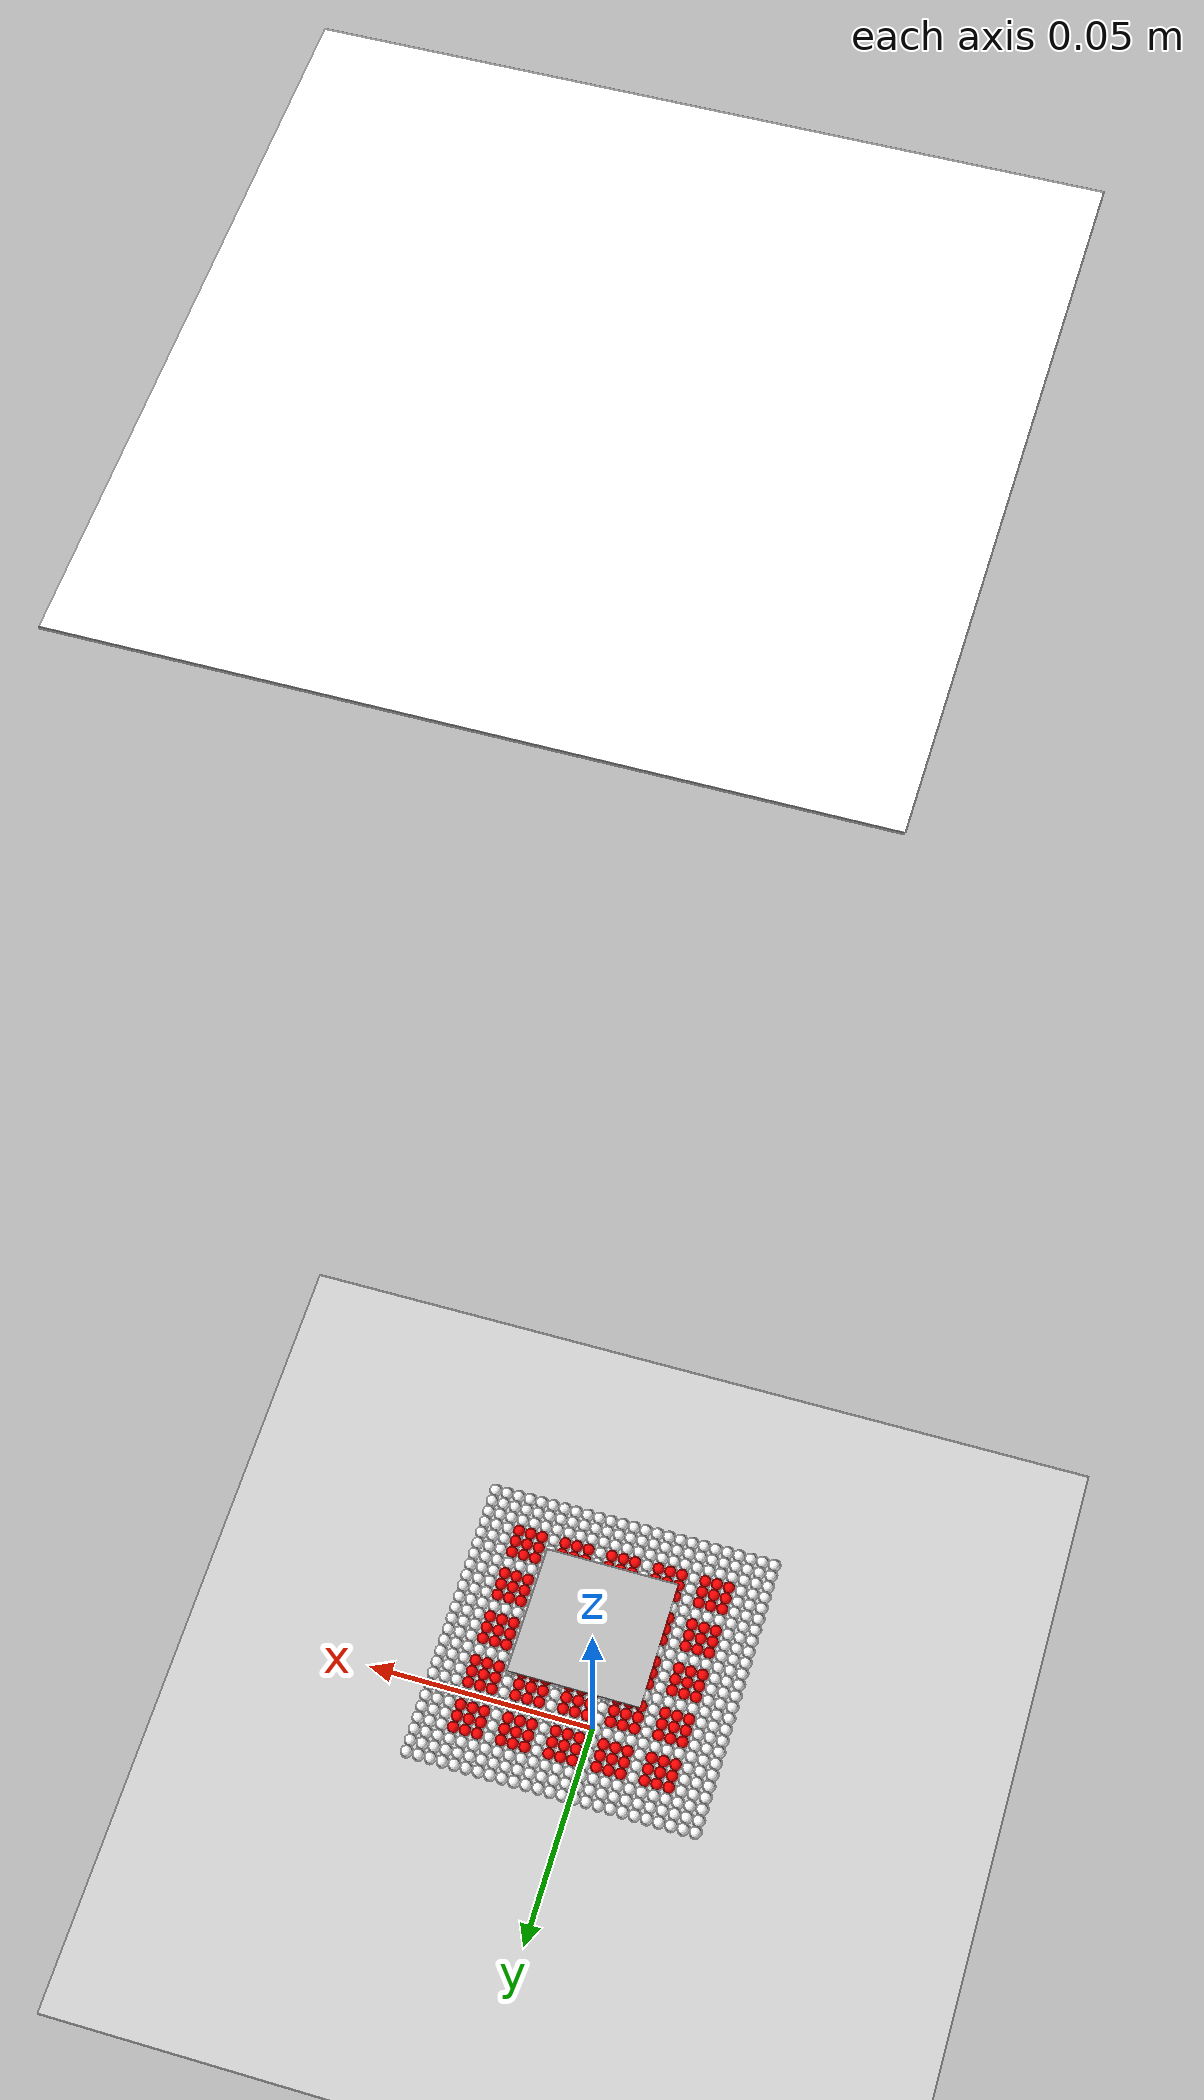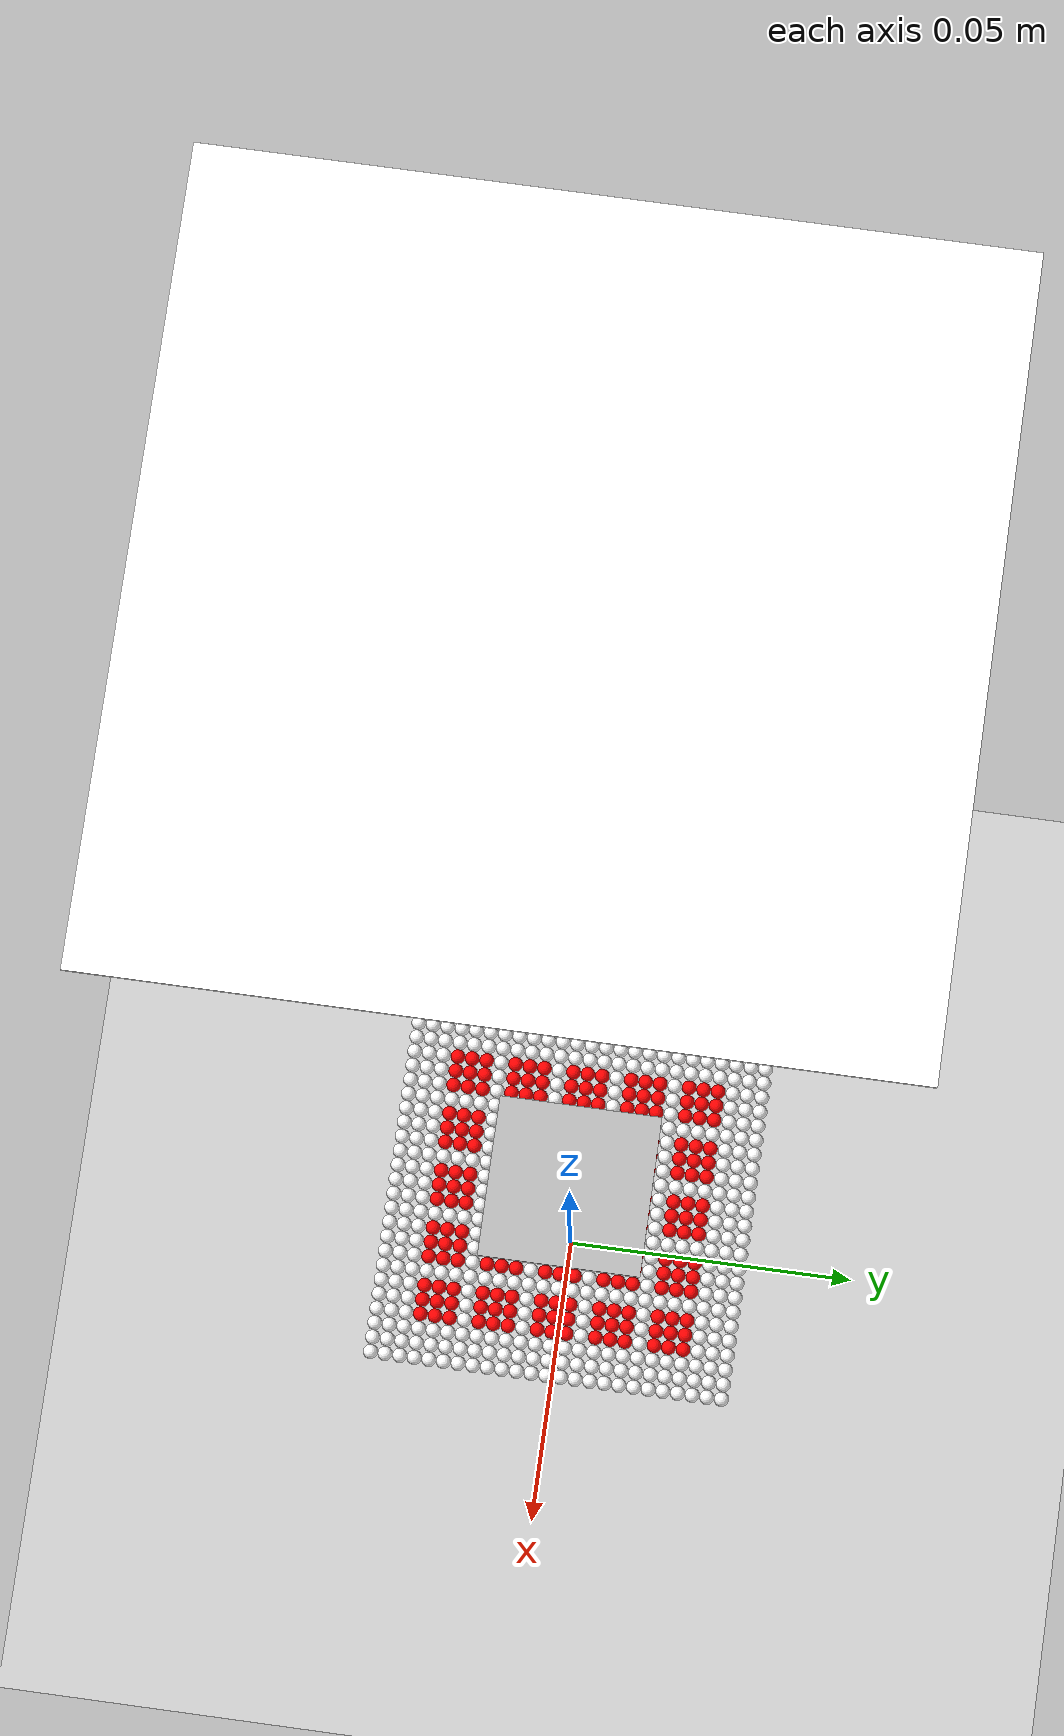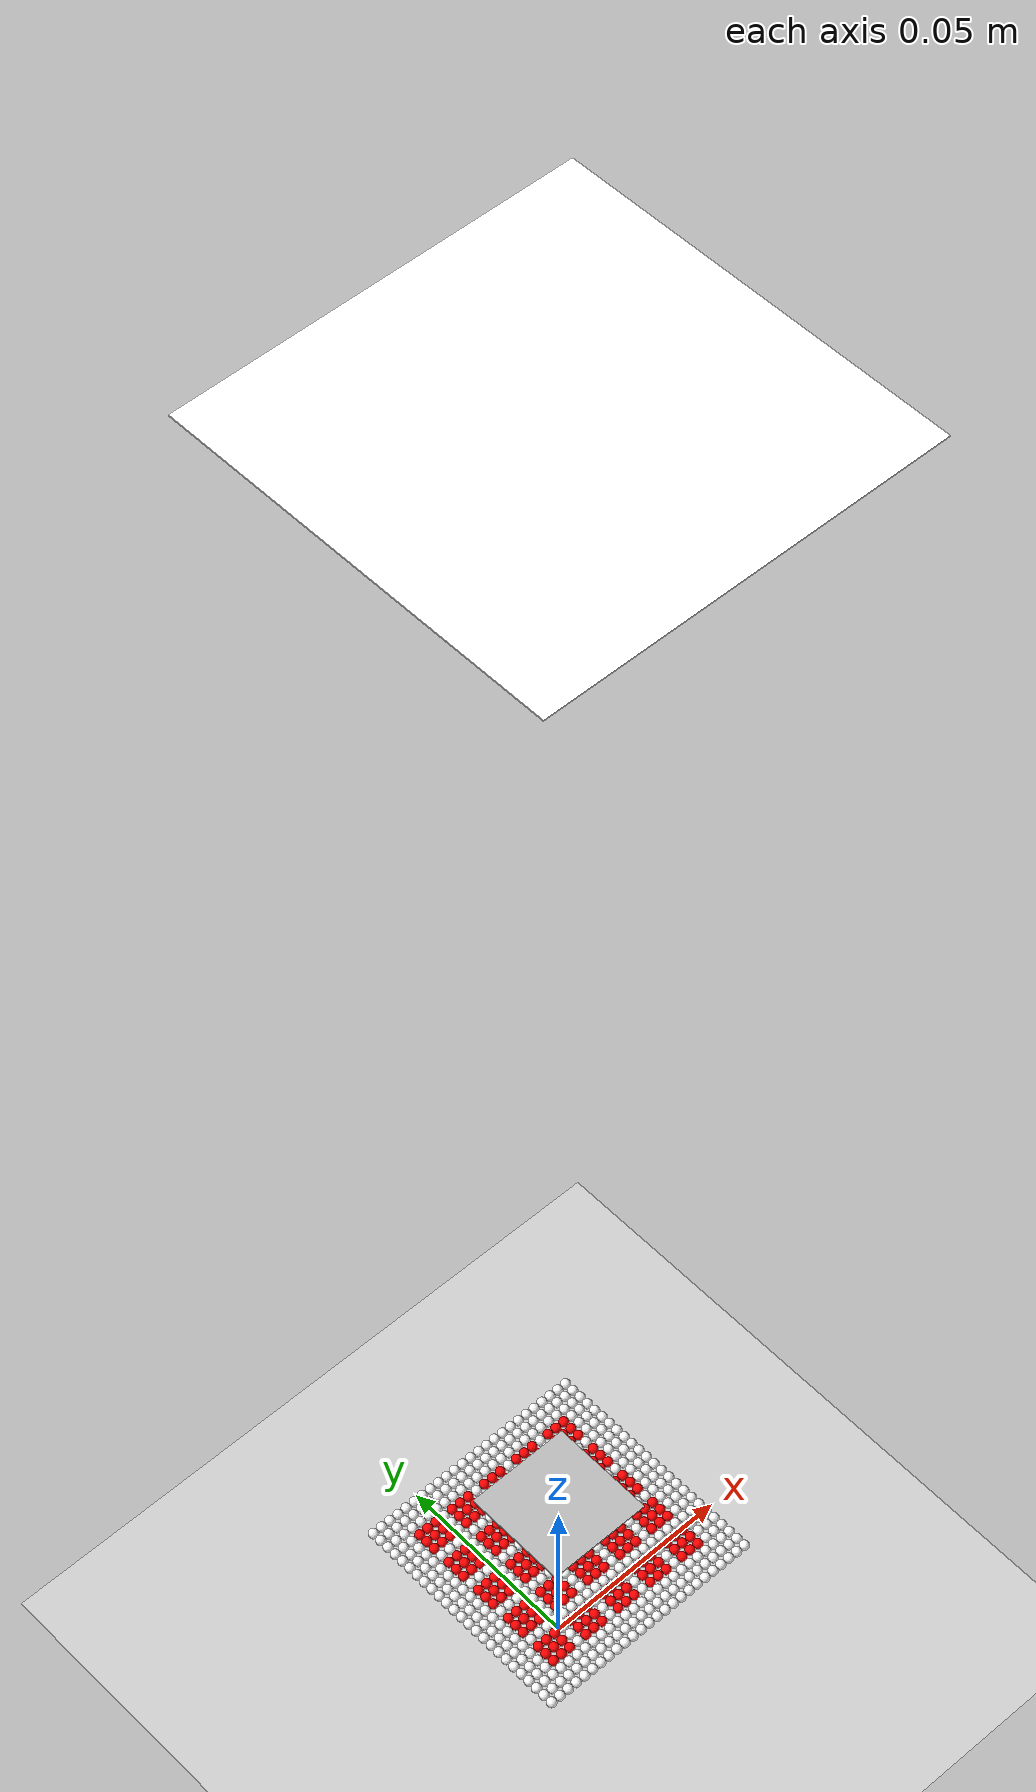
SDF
<?xml version='1.0'?>
<gazebo version='1.3'>
<world name='default'>

<include>
  <uri>model://ground_plane</uri>
</include>

<include>
  <uri>model://sun</uri>
</include>

<include>
  <uri>model://spring_array25</uri>
</include>

<physics type='ode'>
  <gravity>0.0 0.0 -9.8</gravity>
  <ode>
    <solver>
      <iters>150</iters>
    </solver>
    <constraints>
      <cfm>0.2</cfm>
    </constraints>
  </ode>
</physics>

<include>
  <uri>model://box</uri>
  <pose>0 0 0.055 0 0 0</pose>
</include>

<gui fullscreen='0'>
  <camera name='user_camera'>
    <pose>0.130675 -0.121126 0.095229 0 0.347643 2.35619</pose>
    <view_controller>orbit</view_controller>
  </camera>
</gui>

</world>
</gazebo>

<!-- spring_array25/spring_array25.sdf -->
<sdf version='1.5'>
  <model name='spring_array25'>
    <pose>0 0 0 0 -0 0</pose>
    <link name='plane'>
      <pose>0 0 0.4 0 -0 0</pose>
      <inertial>
        <mass>20</mass>
      </inertial>
      <collision name='collision'>
        <geometry>
          <box>
            <size>0.09375 0.09375 0.00025</size>
          </box>
        </geometry>
        <surface>
          <friction>
            <ode>
              <mu>0</mu>
              <mu2>0</mu2>
            </ode>
          </friction>
        </surface>
      </collision>
      <visual name='visual'>
        <geometry>
          <box>
            <size>0.09375 0.09375 0.00025</size>
          </box>
        </geometry>
        <material>
          <ambient>1 1 1 1</ambient>
          <diffuse>1 1 1 1</diffuse>
          <specular>0.1 0.1 0.1 1</specular>
          <emissive>0 0 0 0</emissive>
        </material>
      </visual>
    </link>
    <joint name='plane_joint' type='prismatic'>
      <parent>world</parent>
      <child>plane</child>
      <axis>
        <xyz>0 0 1</xyz>
        <limit>
          <lower>1e+16</lower>
          <upper>-1e+16</upper>
        </limit>
        <use_parent_model_frame>1</use_parent_model_frame>
      </axis>
    </joint>
    <link name='spring_1'>
      <pose>-0.03 0.03 0.04 0 -0 0</pose>
      <inertial>
        <mass>0.00235</mass>
      </inertial>
      <collision name='sphere_collision'>
        <geometry>
          <sphere>
            <radius>0.00125</radius>
          </sphere>
        </geometry>
        <surface>
          <friction>
            <ode>
              <mu>0</mu>
              <mu2>0</mu2>
            </ode>
          </friction>
        </surface>
      </collision>
      <visual name='visual'>
        <geometry>
          <sphere>
            <radius>0.00125</radius>
          </sphere>
        </geometry>
        <material>
          <ambient>1 1 1 1</ambient>
          <diffuse>1 1 1 1</diffuse>
          <specular>0.1 0.1 0.1 1</specular>
          <emissive>0 0 0 0</emissive>
        </material>
      </visual>
    </link>
    <joint name='spring_joint_1' type='prismatic'>
      <parent>plane</parent>
      <child>spring_1</child>
      <axis>
        <xyz>0 0 1</xyz>
        <limit>
          <lower>-1e+16</lower>
          <upper>1e+16</upper>
        </limit>
        <use_parent_model_frame>1</use_parent_model_frame>
      </axis>
    </joint>
    <link name='spring_2'>
      <pose>-0.0275 0.03 0.04 0 -0 0</pose>
      <inertial>
        <mass>0.00235</mass>
      </inertial>
      <collision name='sphere_collision'>
        <geometry>
          <sphere>
            <radius>0.00125</radius>
          </sphere>
        </geometry>
        <surface>
          <friction>
            <ode>
              <mu>0</mu>
              <mu2>0</mu2>
            </ode>
          </friction>
        </surface>
      </collision>
      <visual name='visual'>
        <geometry>
          <sphere>
            <radius>0.00125</radius>
          </sphere>
        </geometry>
        <material>
          <ambient>1 1 1 1</ambient>
          <diffuse>1 1 1 1</diffuse>
          <specular>0.1 0.1 0.1 1</specular>
          <emissive>0 0 0 0</emissive>
        </material>
      </visual>
    </link>
    <joint name='spring_joint_2' type='prismatic'>
      <parent>plane</parent>
      <child>spring_2</child>
      <axis>
        <xyz>0 0 1</xyz>
        <limit>
          <lower>-1e+16</lower>
          <upper>1e+16</upper>
        </limit>
        <use_parent_model_frame>1</use_parent_model_frame>
      </axis>
    </joint>
    <link name='spring_3'>
      <pose>-0.025 0.03 0.04 0 -0 0</pose>
      <inertial>
        <mass>0.00235</mass>
      </inertial>
      <collision name='sphere_collision'>
        <geometry>
          <sphere>
            <radius>0.00125</radius>
          </sphere>
        </geometry>
        <surface>
          <friction>
            <ode>
              <mu>0</mu>
              <mu2>0</mu2>
            </ode>
          </friction>
        </surface>
      </collision>
      <visual name='visual'>
        <geometry>
          <sphere>
            <radius>0.00125</radius>
          </sphere>
        </geometry>
        <material>
          <ambient>1 1 1 1</ambient>
          <diffuse>1 1 1 1</diffuse>
          <specular>0.1 0.1 0.1 1</specular>
          <emissive>0 0 0 0</emissive>
        </material>
      </visual>
    </link>
    <joint name='spring_joint_3' type='prismatic'>
      <parent>plane</parent>
      <child>spring_3</child>
      <axis>
        <xyz>0 0 1</xyz>
        <limit>
          <lower>-1e+16</lower>
          <upper>1e+16</upper>
        </limit>
        <use_parent_model_frame>1</use_parent_model_frame>
      </axis>
    </joint>
    <link name='spring_4'>
      <pose>-0.0225 0.03 0.04 0 -0 0</pose>
      <inertial>
        <mass>0.00235</mass>
      </inertial>
      <collision name='sphere_collision'>
        <geometry>
          <sphere>
            <radius>0.00125</radius>
          </sphere>
        </geometry>
        <surface>
          <friction>
            <ode>
              <mu>0</mu>
              <mu2>0</mu2>
            </ode>
          </friction>
        </surface>
      </collision>
      <visual name='visual'>
        <geometry>
          <sphere>
            <radius>0.00125</radius>
          </sphere>
        </geometry>
        <material>
          <ambient>1 1 1 1</ambient>
          <diffuse>1 1 1 1</diffuse>
          <specular>0.1 0.1 0.1 1</specular>
          <emissive>0 0 0 0</emissive>
        </material>
      </visual>
    </link>
    <joint name='spring_joint_4' type='prismatic'>
      <parent>plane</parent>
      <child>spring_4</child>
      <axis>
        <xyz>0 0 1</xyz>
        <limit>
          <lower>-1e+16</lower>
          <upper>1e+16</upper>
        </limit>
        <use_parent_model_frame>1</use_parent_model_frame>
      </axis>
    </joint>
    <link name='spring_5'>
      <pose>-0.02 0.03 0.04 0 -0 0</pose>
      <inertial>
        <mass>0.00235</mass>
      </inertial>
      <collision name='sphere_collision'>
        <geometry>
          <sphere>
            <radius>0.00125</radius>
          </sphere>
        </geometry>
        <surface>
          <friction>
            <ode>
              <mu>0</mu>
              <mu2>0</mu2>
            </ode>
          </friction>
        </surface>
      </collision>
      <visual name='visual'>
        <geometry>
          <sphere>
            <radius>0.00125</radius>
          </sphere>
        </geometry>
        <material>
          <ambient>1 1 1 1</ambient>
          <diffuse>1 1 1 1</diffuse>
          <specular>0.1 0.1 0.1 1</specular>
          <emissive>0 0 0 0</emissive>
        </material>
      </visual>
    </link>
    <joint name='spring_joint_5' type='prismatic'>
      <parent>plane</parent>
      <child>spring_5</child>
      <axis>
        <xyz>0 0 1</xyz>
        <limit>
          <lower>-1e+16</lower>
          <upper>1e+16</upper>
        </limit>
        <use_parent_model_frame>1</use_parent_model_frame>
      </axis>
    </joint>
    <link name='spring_6'>
      <pose>-0.0175 0.03 0.04 0 -0 0</pose>
      <inertial>
        <mass>0.00235</mass>
      </inertial>
      <collision name='sphere_collision'>
        <geometry>
          <sphere>
            <radius>0.00125</radius>
          </sphere>
        </geometry>
        <surface>
          <friction>
            <ode>
              <mu>0</mu>
              <mu2>0</mu2>
            </ode>
          </friction>
        </surface>
      </collision>
      <visual name='visual'>
        <geometry>
          <sphere>
            <radius>0.00125</radius>
          </sphere>
        </geometry>
        <material>
          <ambient>1 1 1 1</ambient>
          <diffuse>1 1 1 1</diffuse>
          <specular>0.1 0.1 0.1 1</specular>
          <emissive>0 0 0 0</emissive>
        </material>
      </visual>
    </link>
    <joint name='spring_joint_6' type='prismatic'>
      <parent>plane</parent>
      <child>spring_6</child>
      <axis>
        <xyz>0 0 1</xyz>
        <limit>
          <lower>-1e+16</lower>
          <upper>1e+16</upper>
        </limit>
        <use_parent_model_frame>1</use_parent_model_frame>
      </axis>
    </joint>
    <link name='spring_7'>
      <pose>-0.015 0.03 0.04 0 -0 0</pose>
      <inertial>
        <mass>0.00235</mass>
      </inertial>
      <collision name='sphere_collision'>
        <geometry>
          <sphere>
            <radius>0.00125</radius>
          </sphere>
        </geometry>
        <surface>
          <friction>
            <ode>
              <mu>0</mu>
              <mu2>0</mu2>
            </ode>
          </friction>
        </surface>
      </collision>
      <visual name='visual'>
        <geometry>
          <sphere>
            <radius>0.00125</radius>
          </sphere>
        </geometry>
        <material>
          <ambient>1 1 1 1</ambient>
          <diffuse>1 1 1 1</diffuse>
          <specular>0.1 0.1 0.1 1</specular>
          <emissive>0 0 0 0</emissive>
        </material>
      </visual>
    </link>
    <joint name='spring_joint_7' type='prismatic'>
      <parent>plane</parent>
      <child>spring_7</child>
      <axis>
        <xyz>0 0 1</xyz>
        <limit>
          <lower>-1e+16</lower>
          <upper>1e+16</upper>
        </limit>
        <use_parent_model_frame>1</use_parent_model_frame>
      </axis>
    </joint>
    <link name='spring_8'>
      <pose>-0.0125 0.03 0.04 0 -0 0</pose>
      <inertial>
        <mass>0.00235</mass>
      </inertial>
      <collision name='sphere_collision'>
        <geometry>
          <sphere>
            <radius>0.00125</radius>
          </sphere>
        </geometry>
        <surface>
          <friction>
            <ode>
              <mu>0</mu>
              <mu2>0</mu2>
            </ode>
          </friction>
        </surface>
      </collision>
      <visual name='visual'>
        <geometry>
          <sphere>
            <radius>0.00125</radius>
          </sphere>
        </geometry>
        <material>
          <ambient>1 1 1 1</ambient>
          <diffuse>1 1 1 1</diffuse>
          <specular>0.1 0.1 0.1 1</specular>
          <emissive>0 0 0 0</emissive>
        </material>
      </visual>
    </link>
    <joint name='spring_joint_8' type='prismatic'>
      <parent>plane</parent>
      <child>spring_8</child>
      <axis>
        <xyz>0 0 1</xyz>
        <limit>
          <lower>-1e+16</lower>
          <upper>1e+16</upper>
        </limit>
        <use_parent_model_frame>1</use_parent_model_frame>
      </axis>
    </joint>
    <link name='spring_9'>
      <pose>-0.01 0.03 0.04 0 -0 0</pose>
      <inertial>
        <mass>0.00235</mass>
      </inertial>
      <collision name='sphere_collision'>
        <geometry>
          <sphere>
            <radius>0.00125</radius>
          </sphere>
        </geometry>
        <surface>
          <friction>
            <ode>
              <mu>0</mu>
              <mu2>0</mu2>
            </ode>
          </friction>
        </surface>
      </collision>
      <visual name='visual'>
        <geometry>
          <sphere>
            <radius>0.00125</radius>
          </sphere>
        </geometry>
        <material>
          <ambient>1 1 1 1</ambient>
          <diffuse>1 1 1 1</diffuse>
          <specular>0.1 0.1 0.1 1</specular>
          <emissive>0 0 0 0</emissive>
        </material>
      </visual>
    </link>
    <joint name='spring_joint_9' type='prismatic'>
      <parent>plane</parent>
      <child>spring_9</child>
      <axis>
        <xyz>0 0 1</xyz>
        <limit>
          <lower>-1e+16</lower>
          <upper>1e+16</upper>
        </limit>
        <use_parent_model_frame>1</use_parent_model_frame>
      </axis>
    </joint>
    <link name='spring_10'>
      <pose>-0.0075 0.03 0.04 0 -0 0</pose>
      <inertial>
        <mass>0.00235</mass>
      </inertial>
      <collision name='sphere_collision'>
        <geometry>
          <sphere>
            <radius>0.00125</radius>
          </sphere>
        </geometry>
        <surface>
          <friction>
            <ode>
              <mu>0</mu>
              <mu2>0</mu2>
            </ode>
          </friction>
        </surface>
      </collision>
      <visual name='visual'>
        <geometry>
          <sphere>
            <radius>0.00125</radius>
          </sphere>
        </geometry>
        <material>
          <ambient>1 1 1 1</ambient>
          <diffuse>1 1 1 1</diffuse>
          <specular>0.1 0.1 0.1 1</specular>
          <emissive>0 0 0 0</emissive>
        </material>
      </visual>
    </link>
    <joint name='spring_joint_10' type='prismatic'>
      <parent>plane</parent>
      <child>spring_10</child>
      <axis>
        <xyz>0 0 1</xyz>
        <limit>
          <lower>-1e+16</lower>
          <upper>1e+16</upper>
        </limit>
        <use_parent_model_frame>1</use_parent_model_frame>
      </axis>
    </joint>
    <link name='spring_11'>
      <pose>-0.005 0.03 0.04 0 -0 0</pose>
      <inertial>
        <mass>0.00235</mass>
      </inertial>
      <collision name='sphere_collision'>
        <geometry>
          <sphere>
            <radius>0.00125</radius>
          </sphere>
        </geometry>
        <surface>
          <friction>
            <ode>
              <mu>0</mu>
              <mu2>0</mu2>
            </ode>
          </friction>
        </surface>
      </collision>
      <visual name='visual'>
        <geometry>
          <sphere>
            <radius>0.00125</radius>
          </sphere>
        </geometry>
        <material>
          <ambient>1 1 1 1</ambient>
          <diffuse>1 1 1 1</diffuse>
          <specular>0.1 0.1 0.1 1</specular>
          <emissive>0 0 0 0</emissive>
        </material>
      </visual>
    </link>
    <joint name='spring_joint_11' type='prismatic'>
      <parent>plane</parent>
      <child>spring_11</child>
      <axis>
        <xyz>0 0 1</xyz>
        <limit>
          <lower>-1e+16</lower>
          <upper>1e+16</upper>
        </limit>
        <use_parent_model_frame>1</use_parent_model_frame>
      </axis>
    </joint>
    <link name='spring_12'>
      <pose>-0.0025 0.03 0.04 0 -0 0</pose>
      <inertial>
        <mass>0.00235</mass>
      </inertial>
      <collision name='sphere_collision'>
        <geometry>
          <sphere>
            <radius>0.00125</radius>
          </sphere>
        </geometry>
        <surface>
          <friction>
            <ode>
              <mu>0</mu>
              <mu2>0</mu2>
            </ode>
          </friction>
        </surface>
      </collision>
      <visual name='visual'>
        <geometry>
          <sphere>
            <radius>0.00125</radius>
          </sphere>
        </geometry>
        <material>
          <ambient>1 1 1 1</ambient>
          <diffuse>1 1 1 1</diffuse>
          <specular>0.1 0.1 0.1 1</specular>
          <emissive>0 0 0 0</emissive>
        </material>
      </visual>
    </link>
    <joint name='spring_joint_12' type='prismatic'>
      <parent>plane</parent>
      <child>spring_12</child>
      <axis>
        <xyz>0 0 1</xyz>
        <limit>
          <lower>-1e+16</lower>
          <upper>1e+16</upper>
        </limit>
        <use_parent_model_frame>1</use_parent_model_frame>
      </axis>
    </joint>
    <link name='spring_13'>
      <pose>-2.60209e-18 0.03 0.04 0 -0 0</pose>
      <inertial>
        <mass>0.00235</mass>
      </inertial>
      <collision name='sphere_collision'>
        <geometry>
          <sphere>
            <radius>0.00125</radius>
          </sphere>
        </geometry>
        <surface>
          <friction>
            <ode>
              <mu>0</mu>
              <mu2>0</mu2>
            </ode>
          </friction>
        </surface>
      </collision>
      <visual name='visual'>
        <geometry>
          <sphere>
            <radius>0.00125</radius>
          </sphere>
        </geometry>
        <material>
          <ambient>1 1 1 1</ambient>
          <diffuse>1 1 1 1</diffuse>
          <specular>0.1 0.1 0.1 1</specular>
          <emissive>0 0 0 0</emissive>
        </material>
      </visual>
    </link>
    <joint name='spring_joint_13' type='prismatic'>
      <parent>plane</parent>
      <child>spring_13</child>
      <axis>
        <xyz>0 0 1</xyz>
        <limit>
          <lower>-1e+16</lower>
          <upper>1e+16</upper>
        </limit>
        <use_parent_model_frame>1</use_parent_model_frame>
      </axis>
    </joint>
    <link name='spring_14'>
      <pose>0.0025 0.03 0.04 0 -0 0</pose>
      <inertial>
        <mass>0.00235</mass>
      </inertial>
      <collision name='sphere_collision'>
        <geometry>
          <sphere>
            <radius>0.00125</radius>
          </sphere>
        </geometry>
        <surface>
          <friction>
            <ode>
              <mu>0</mu>
              <mu2>0</mu2>
            </ode>
          </friction>
        </surface>
      </collision>
      <visual name='visual'>
        <geometry>
          <sphere>
            <radius>0.00125</radius>
          </sphere>
        </geometry>
        <material>
          <ambient>1 1 1 1</ambient>
          <diffuse>1 1 1 1</diffuse>
          <specular>0.1 0.1 0.1 1</specular>
          <emissive>0 0 0 0</emissive>
        </material>
      </visual>
    </link>
    <joint name='spring_joint_14' type='prismatic'>
      <parent>plane</parent>
      <child>spring_14</child>
      <axis>
        <xyz>0 0 1</xyz>
        <limit>
          <lower>-1e+16</lower>
          <upper>1e+16</upper>
        </limit>
        <use_parent_model_frame>1</use_parent_model_frame>
      </axis>
    </joint>
    <link name='spring_15'>
      <pose>0.005 0.03 0.04 0 -0 0</pose>
      <inertial>
        <mass>0.00235</mass>
      </inertial>
      <collision name='sphere_collision'>
        <geometry>
          <sphere>
            <radius>0.00125</radius>
          </sphere>
        </geometry>
        <surface>
          <friction>
            <ode>
              <mu>0</mu>
              <mu2>0</mu2>
            </ode>
          </friction>
        </surface>
      </collision>
      <visual name='visual'>
        <geometry>
          <sphere>
            <radius>0.00125</radius>
          </sphere>
        </geometry>
        <material>
          <ambient>1 1 1 1</ambient>
          <diffuse>1 1 1 1</diffuse>
          <specular>0.1 0.1 0.1 1</specular>
          <emissive>0 0 0 0</emissive>
        </material>
      </visual>
    </link>
    <joint name='spring_joint_15' type='prismatic'>
      <parent>plane</parent>
      <child>spring_15</child>
      <axis>
        <xyz>0 0 1</xyz>
        <limit>
          <lower>-1e+16</lower>
          <upper>1e+16</upper>
        </limit>
        <use_parent_model_frame>1</use_parent_model_frame>
      </axis>
    </joint>
    <link name='spring_16'>
      <pose>0.0075 0.03 0.04 0 -0 0</pose>
      <inertial>
        <mass>0.00235</mass>
      </inertial>
      <collision name='sphere_collision'>
        <geometry>
          <sphere>
            <radius>0.00125</radius>
          </sphere>
        </geometry>
        <surface>
          <friction>
            <ode>
              <mu>0</mu>
              <mu2>0</mu2>
            </ode>
          </friction>
        </surface>
      </collision>
      <visual name='visual'>
        <geometry>
          <sphere>
            <radius>0.00125</radius>
          </sphere>
        </geometry>
        <material>
          <ambient>1 1 1 1</ambient>
          <diffuse>1 1 1 1</diffuse>
          <specular>0.1 0.1 0.1 1</specular>
          <emissive>0 0 0 0</emissive>
        </material>
      </visual>
    </link>
    <joint name='spring_joint_16' type='prismatic'>
      <parent>plane</parent>
      <child>spring_16</child>
      <axis>
        <xyz>0 0 1</xyz>
        <limit>
          <lower>-1e+16</lower>
          <upper>1e+16</upper>
        </limit>
        <use_parent_model_frame>1</use_parent_model_frame>
      </axis>
    </joint>
    <link name='spring_17'>
      <pose>0.01 0.03 0.04 0 -0 0</pose>
      <inertial>
        <mass>0.00235</mass>
      </inertial>
      <collision name='sphere_collision'>
        <geometry>
          <sphere>
            <radius>0.00125</radius>
          </sphere>
        </geometry>
        <surface>
          <friction>
            <ode>
              <mu>0</mu>
              <mu2>0</mu2>
            </ode>
          </friction>
        </surface>
      </collision>
      <visual name='visual'>
        <geometry>
          <sphere>
            <radius>0.00125</radius>
          </sphere>
        </geometry>
        <material>
          <ambient>1 1 1 1</ambient>
          <diffuse>1 1 1 1</diffuse>
          <specular>0.1 0.1 0.1 1</specular>
          <emissive>0 0 0 0</emissive>
        </material>
      </visual>
    </link>
    <joint name='spring_joint_17' type='prismatic'>
      <parent>plane</parent>
      <child>spring_17</child>
      <axis>
        <xyz>0 0 1</xyz>
        <limit>
          <lower>-1e+16</lower>
          <upper>1e+16</upper>
        </limit>
        <use_parent_model_frame>1</use_parent_model_frame>
      </axis>
    </joint>
    <link name='spring_18'>
      <pose>0.0125 0.03 0.04 0 -0 0</pose>
      <inertial>
        <mass>0.00235</mass>
      </inertial>
      <collision name='sphere_collision'>
        <geometry>
          <sphere>
            <radius>0.00125</radius>
          </sphere>
        </geometry>
        <surface>
          <friction>
            <ode>
              <mu>0</mu>
              <mu2>0</mu2>
            </ode>
          </friction>
        </surface>
      </collision>
      <visual name='visual'>
        <geometry>
          <sphere>
            <radius>0.00125</radius>
          </sphere>
        </geometry>
        <material>
          <ambient>1 1 1 1</ambient>
          <diffuse>1 1 1 1</diffuse>
          <specular>0.1 0.1 0.1 1</specular>
          <emissive>0 0 0 0</emissive>
        </material>
      </visual>
    </link>
    <joint name='spring_joint_18' type='prismatic'>
      <parent>plane</parent>
      <child>spring_18</child>
      <axis>
        <xyz>0 0 1</xyz>
        <limit>
          <lower>-1e+16</lower>
          <upper>1e+16</upper>
        </limit>
        <use_parent_model_frame>1</use_parent_model_frame>
      </axis>
    </joint>
    <link name='spring_19'>
      <pose>0.015 0.03 0.04 0 -0 0</pose>
      <inertial>
        <mass>0.00235</mass>
      </inertial>
      <collision name='sphere_collision'>
        <geometry>
          <sphere>
            <radius>0.00125</radius>
          </sphere>
        </geometry>
        <surface>
          <friction>
            <ode>
              <mu>0</mu>
              <mu2>0</mu2>
            </ode>
          </friction>
        </surface>
      </collision>
      <visual name='visual'>
        <geometry>
          <sphere>
            <radius>0.00125</radius>
          </sphere>
        </geometry>
        <material>
          <ambient>1 1 1 1</ambient>
          <diffuse>1 1 1 1</diffuse>
          <specular>0.1 0.1 0.1 1</specular>
          <emissive>0 0 0 0</emissive>
        </material>
      </visual>
    </link>
    <joint name='spring_joint_19' type='prismatic'>
      <parent>plane</parent>
      <child>spring_19</child>
      <axis>
        <xyz>0 0 1</xyz>
        <limit>
          <lower>-1e+16</lower>
          <upper>1e+16</upper>
        </limit>
        <use_parent_model_frame>1</use_parent_model_frame>
      </axis>
    </joint>
    <link name='spring_20'>
      <pose>0.0175 0.03 0.04 0 -0 0</pose>
      <inertial>
        <mass>0.00235</mass>
      </inertial>
      <collision name='sphere_collision'>
        <geometry>
          <sphere>
            <radius>0.00125</radius>
          </sphere>
        </geometry>
        <surface>
          <friction>
            <ode>
              <mu>0</mu>
              <mu2>0</mu2>
            </ode>
          </friction>
        </surface>
      </collision>
      <visual name='visual'>
        <geometry>
          <sphere>
            <radius>0.00125</radius>
          </sphere>
        </geometry>
        <material>
          <ambient>1 1 1 1</ambient>
          <diffuse>1 1 1 1</diffuse>
          <specular>0.1 0.1 0.1 1</specular>
          <emissive>0 0 0 0</emissive>
        </material>
      </visual>
    </link>
    <joint name='spring_joint_20' type='prismatic'>
      <parent>plane</parent>
      <child>spring_20</child>
      <axis>
        <xyz>0 0 1</xyz>
        <limit>
          <lower>-1e+16</lower>
          <upper>1e+16</upper>
        </limit>
        <use_parent_model_frame>1</use_parent_model_frame>
      </axis>
    </joint>
    <link name='spring_21'>
      <pose>0.02 0.03 0.04 0 -0 0</pose>
      <inertial>
        <mass>0.00235</mass>
      </inertial>
      <collision name='sphere_collision'>
        <geometry>
          <sphere>
            <radius>0.00125</radius>
          </sphere>
        </geometry>
        <surface>
          <friction>
            <ode>
              <mu>0</mu>
              <mu2>0</mu2>
            </ode>
          </friction>
        </surface>
      </collision>
      <visual name='visual'>
        <geometry>
          <sphere>
            <radius>0.00125</radius>
          </sphere>
        </geometry>
        <material>
          <ambient>1 1 1 1</ambient>
          <diffuse>1 1 1 1</diffuse>
          <specular>0.1 0.1 0.1 1</specular>
          <emissive>0 0 0 0</emissive>
        </material>
      </visual>
    </link>
    <joint name='spring_joint_21' type='prismatic'>
      <parent>plane</parent>
      <child>spring_21</child>
      <axis>
        <xyz>0 0 1</xyz>
        <limit>
          <lower>-1e+16</lower>
          <upper>1e+16</upper>
        </limit>
        <use_parent_model_frame>1</use_parent_model_frame>
      </axis>
    </joint>
    <link name='spring_22'>
      <pose>0.0225 0.03 0.04 0 -0 0</pose>
      <inertial>
        <mass>0.00235</mass>
      </inertial>
      <collision name='sphere_collision'>
        <geometry>
          <sphere>
            <radius>0.00125</radius>
          </sphere>
        </geometry>
        <surface>
          <friction>
            <ode>
              <mu>0</mu>
              <mu2>0</mu2>
            </ode>
          </friction>
        </surface>
      </collision>
      <visual name='visual'>
        <geometry>
          <sphere>
            <radius>0.00125</radius>
          </sphere>
        </geometry>
        <material>
          <ambient>1 1 1 1</ambient>
          <diffuse>1 1 1 1</diffuse>
          <specular>0.1 0.1 0.1 1</specular>
          <emissive>0 0 0 0</emissive>
        </material>
      </visual>
    </link>
    <joint name='spring_joint_22' type='prismatic'>
      <parent>plane</parent>
      <child>spring_22</child>
      <axis>
        <xyz>0 0 1</xyz>
        <limit>
          <lower>-1e+16</lower>
          <upper>1e+16</upper>
        </limit>
        <use_parent_model_frame>1</use_parent_model_frame>
      </axis>
    </joint>
    <link name='spring_23'>
      <pose>0.025 0.03 0.04 0 -0 0</pose>
      <inertial>
        <mass>0.00235</mass>
      </inertial>
      <collision name='sphere_collision'>
        <geometry>
          <sphere>
            <radius>0.00125</radius>
          </sphere>
        </geometry>
        <surface>
          <friction>
            <ode>
              <mu>0</mu>
              <mu2>0</mu2>
            </ode>
          </friction>
        </surface>
      </collision>
      <visual name='visual'>
        <geometry>
          <sphere>
            <radius>0.00125</radius>
          </sphere>
        </geometry>
        <material>
          <ambient>1 1 1 1</ambient>
          <diffuse>1 1 1 1</diffuse>
          <specular>0.1 0.1 0.1 1</specular>
          <emissive>0 0 0 0</emissive>
        </material>
      </visual>
    </link>
    <joint name='spring_joint_23' type='prismatic'>
      <parent>plane</parent>
      <child>spring_23</child>
      <axis>
        <xyz>0 0 1</xyz>
        <limit>
          <lower>-1e+16</lower>
          <upper>1e+16</upper>
        </limit>
        <use_parent_model_frame>1</use_parent_model_frame>
      </axis>
    </joint>
    <link name='spring_24'>
      <pose>0.0275 0.03 0.04 0 -0 0</pose>
      <inertial>
        <mass>0.00235</mass>
      </inertial>
      <collision name='sphere_collision'>
        <geometry>
          <sphere>
            <radius>0.00125</radius>
          </sphere>
        </geometry>
        <surface>
          <friction>
            <ode>
              <mu>0</mu>
              <mu2>0</mu2>
            </ode>
          </friction>
        </surface>
      </collision>
      <visual name='visual'>
        <geometry>
          <sphere>
            <radius>0.00125</radius>
          </sphere>
        </geometry>
        <material>
          <ambient>1 1 1 1</ambient>
          <diffuse>1 1 1 1</diffuse>
          <specular>0.1 0.1 0.1 1</specular>
          <emissive>0 0 0 0</emissive>
        </material>
      </visual>
    </link>
    <joint name='spring_joint_24' type='prismatic'>
      <parent>plane</parent>
      <child>spring_24</child>
      <axis>
        <xyz>0 0 1</xyz>
        <limit>
          <lower>-1e+16</lower>
          <upper>1e+16</upper>
        </limit>
        <use_parent_model_frame>1</use_parent_model_frame>
      </axis>
    </joint>
    <link name='spring_25'>
      <pose>0.03 0.03 0.04 0 -0 0</pose>
      <inertial>
        <mass>0.00235</mass>
      </inertial>
      <collision name='sphere_collision'>
        <geometry>
          <sphere>
            <radius>0.00125</radius>
          </sphere>
        </geometry>
        <surface>
          <friction>
            <ode>
              <mu>0</mu>
              <mu2>0</mu2>
            </ode>
          </friction>
        </surface>
      </collision>
      <visual name='visual'>
        <geometry>
          <sphere>
            <radius>0.00125</radius>
          </sphere>
        </geometry>
        <material>
          <ambient>1 1 1 1</ambient>
          <diffuse>1 1 1 1</diffuse>
          <specular>0.1 0.1 0.1 1</specular>
          <emissive>0 0 0 0</emissive>
        </material>
      </visual>
    </link>
    <joint name='spring_joint_25' type='prismatic'>
      <parent>plane</parent>
      <child>spring_25</child>
      <axis>
        <xyz>0 0 1</xyz>
        <limit>
          <lower>-1e+16</lower>
          <upper>1e+16</upper>
        </limit>
        <use_parent_model_frame>1</use_parent_model_frame>
      </axis>
    </joint>
    <link name='spring_26'>
      <pose>-0.03 0.0275 0.04 0 -0 0</pose>
      <inertial>
        <mass>0.00235</mass>
      </inertial>
      <collision name='sphere_collision'>
        <geometry>
          <sphere>
            <radius>0.00125</radius>
          </sphere>
        </geometry>
        <surface>
          <friction>
            <ode>
              <mu>0</mu>
              <mu2>0</mu2>
            </ode>
          </friction>
        </surface>
      </collision>
      <visual name='visual'>
        <geometry>
          <sphere>
            <radius>0.00125</radius>
          </sphere>
        </geometry>
        <material>
          <ambient>1 1 1 1</ambient>
          <diffuse>1 1 1 1</diffuse>
          <specular>0.1 0.1 0.1 1</specular>
          <emissive>0 0 0 0</emissive>
        </material>
      </visual>
    </link>
    <joint name='spring_joint_26' type='prismatic'>
      <parent>plane</parent>
      <child>spring_26</child>
      <axis>
        <xyz>0 0 1</xyz>
        <limit>
          <lower>-1e+16</lower>
          <upper>1e+16</upper>
        </limit>
        <use_parent_model_frame>1</use_parent_model_frame>
      </axis>
    </joint>
    <link name='spring_27'>
      <pose>-0.0275 0.0275 0.04 0 -0 0</pose>
      <inertial>
        <mass>0.00235</mass>
      </inertial>
      <collision name='sphere_collision'>
        <geometry>
          <sphere>
            <radius>0.00125</radius>
          </sphere>
        </geometry>
        <surface>
          <friction>
            <ode>
              <mu>0</mu>
              <mu2>0</mu2>
            </ode>
          </friction>
        </surface>
      </collision>
      <visual name='visual'>
        <geometry>
          <sphere>
            <radius>0.00125</radius>
          </sphere>
        </geometry>
        <material>
          <ambient>1 1 1 1</ambient>
          <diffuse>1 1 1 1</diffuse>
          <specular>0.1 0.1 0.1 1</specular>
          <emissive>0 0 0 0</emissive>
        </material>
      </visual>
    </link>
    <joint name='spring_joint_27' type='prismatic'>
      <parent>plane</parent>
      <child>spring_27</child>
      <axis>
        <xyz>0 0 1</xyz>
        <limit>
          <lower>-1e+16</lower>
          <upper>1e+16</upper>
        </limit>
        <use_parent_model_frame>1</use_parent_model_frame>
      </axis>
    </joint>
    <link name='spring_28'>
      <pose>-0.025 0.0275 0.04 0 -0 0</pose>
      <inertial>
        <mass>0.00235</mass>
      </inertial>
      <collision name='sphere_collision'>
        <geometry>
          <sphere>
            <radius>0.00125</radius>
          </sphere>
        </geometry>
        <surface>
          <friction>
            <ode>
              <mu>0</mu>
              <mu2>0</mu2>
            </ode>
          </friction>
        </surface>
      </collision>
      <visual name='visual'>
        <geometry>
          <sphere>
            <radius>0.00125</radius>
          </sphere>
        </geometry>
        <material>
          <ambient>1 1 1 1</ambient>
          <diffuse>1 1 1 1</diffuse>
          <specular>0.1 0.1 0.1 1</specular>
          <emissive>0 0 0 0</emissive>
        </material>
      </visual>
    </link>
    <joint name='spring_joint_28' type='prismatic'>
      <parent>plane</parent>
      <child>spring_28</child>
      <axis>
        <xyz>0 0 1</xyz>
        <limit>
          <lower>-1e+16</lower>
          <upper>1e+16</upper>
        </limit>
        <use_parent_model_frame>1</use_parent_model_frame>
      </axis>
    </joint>
    <link name='spring_29'>
      <pose>-0.0225 0.0275 0.04 0 -0 0</pose>
      <inertial>
        <mass>0.00235</mass>
      </inertial>
      <collision name='sphere_collision'>
        <geometry>
          <sphere>
            <radius>0.00125</radius>
          </sphere>
        </geometry>
        <surface>
          <friction>
            <ode>
              <mu>0</mu>
              <mu2>0</mu2>
            </ode>
          </friction>
        </surface>
      </collision>
      <visual name='visual'>
        <geometry>
          <sphere>
            <radius>0.00125</radius>
          </sphere>
        </geometry>
        <material>
          <ambient>1 1 1 1</ambient>
          <diffuse>1 1 1 1</diffuse>
          <specular>0.1 0.1 0.1 1</specular>
          <emissive>0 0 0 0</emissive>
        </material>
      </visual>
    </link>
    <joint name='spring_joint_29' type='prismatic'>
      <parent>plane</parent>
      <child>spring_29</child>
      <axis>
        <xyz>0 0 1</xyz>
        <limit>
          <lower>-1e+16</lower>
          <upper>1e+16</upper>
        </limit>
        <use_parent_model_frame>1</use_parent_model_frame>
      </axis>
    </joint>
    <link name='spring_30'>
      <pose>-0.02 0.0275 0.04 0 -0 0</pose>
      <inertial>
        <mass>0.00235</mass>
      </inertial>
      <collision name='sphere_collision'>
        <geometry>
          <sphere>
            <radius>0.00125</radius>
          </sphere>
        </geometry>
        <surface>
          <friction>
            <ode>
              <mu>0</mu>
              <mu2>0</mu2>
            </ode>
          </friction>
        </surface>
      </collision>
      <visual name='visual'>
        <geometry>
          <sphere>
            <radius>0.00125</radius>
          </sphere>
        </geometry>
        <material>
          <ambient>1 1 1 1</ambient>
          <diffuse>1 1 1 1</diffuse>
          <specular>0.1 0.1 0.1 1</specular>
          <emissive>0 0 0 0</emissive>
        </material>
      </visual>
    </link>
    <joint name='spring_joint_30' type='prismatic'>
      <parent>plane</parent>
      <child>spring_30</child>
      <axis>
        <xyz>0 0 1</xyz>
        <limit>
          <lower>-1e+16</lower>
          <upper>1e+16</upper>
        </limit>
        <use_parent_model_frame>1</use_parent_model_frame>
      </axis>
    </joint>
    <link name='spring_31'>
      <pose>-0.0175 0.0275 0.04 0 -0 0</pose>
      <inertial>
        <mass>0.00235</mass>
      </inertial>
      <collision name='sphere_collision'>
        <geometry>
          <sphere>
            <radius>0.00125</radius>
          </sphere>
        </geometry>
        <surface>
          <friction>
            <ode>
              <mu>0</mu>
              <mu2>0</mu2>
            </ode>
          </friction>
        </surface>
      </collision>
      <visual name='visual'>
        <geometry>
          <sphere>
            <radius>0.00125</radius>
          </sphere>
        </geometry>
        <material>
          <ambient>1 1 1 1</ambient>
          <diffuse>1 1 1 1</diffuse>
          <specular>0.1 0.1 0.1 1</specular>
          <emissive>0 0 0 0</emissive>
        </material>
      </visual>
    </link>
    <joint name='spring_joint_31' type='prismatic'>
      <parent>plane</parent>
      <child>spring_31</child>
      <axis>
        <xyz>0 0 1</xyz>
        <limit>
          <lower>-1e+16</lower>
          <upper>1e+16</upper>
        </limit>
        <use_parent_model_frame>1</use_parent_model_frame>
      </axis>
    </joint>
    <link name='spring_32'>
      <pose>-0.015 0.0275 0.04 0 -0 0</pose>
      <inertial>
        <mass>0.00235</mass>
      </inertial>
      <collision name='sphere_collision'>
        <geometry>
          <sphere>
            <radius>0.00125</radius>
          </sphere>
        </geometry>
        <surface>
          <friction>
            <ode>
              <mu>0</mu>
              <mu2>0</mu2>
            </ode>
          </friction>
        </surface>
      </collision>
      <visual name='visual'>
        <geometry>
          <sphere>
            <radius>0.00125</radius>
          </sphere>
        </geometry>
        <material>
          <ambient>1 1 1 1</ambient>
          <diffuse>1 1 1 1</diffuse>
          <specular>0.1 0.1 0.1 1</specular>
          <emissive>0 0 0 0</emissive>
        </material>
      </visual>
    </link>
    <joint name='spring_joint_32' type='prismatic'>
      <parent>plane</parent>
      <child>spring_32</child>
      <axis>
        <xyz>0 0 1</xyz>
        <limit>
          <lower>-1e+16</lower>
          <upper>1e+16</upper>
        </limit>
        <use_parent_model_frame>1</use_parent_model_frame>
      </axis>
    </joint>
    <link name='spring_33'>
      <pose>-0.0125 0.0275 0.04 0 -0 0</pose>
      <inertial>
        <mass>0.00235</mass>
      </inertial>
      <collision name='sphere_collision'>
        <geometry>
          <sphere>
            <radius>0.00125</radius>
          </sphere>
        </geometry>
        <surface>
          <friction>
            <ode>
              <mu>0</mu>
              <mu2>0</mu2>
            </ode>
          </friction>
        </surface>
      </collision>
      <visual name='visual'>
        <geometry>
          <sphere>
            <radius>0.00125</radius>
          </sphere>
        </geometry>
        <material>
          <ambient>1 1 1 1</ambient>
          <diffuse>1 1 1 1</diffuse>
          <specular>0.1 0.1 0.1 1</specular>
          <emissive>0 0 0 0</emissive>
        </material>
      </visual>
    </link>
    <joint name='spring_joint_33' type='prismatic'>
      <parent>plane</parent>
      <child>spring_33</child>
      <axis>
        <xyz>0 0 1</xyz>
        <limit>
          <lower>-1e+16</lower>
          <upper>1e+16</upper>
        </limit>
        <use_parent_model_frame>1</use_parent_model_frame>
      </axis>
    </joint>
    <link name='spring_34'>
      <pose>-0.01 0.0275 0.04 0 -0 0</pose>
      <inertial>
        <mass>0.00235</mass>
      </inertial>
      <collision name='sphere_collision'>
        <geometry>
          <sphere>
            <radius>0.00125</radius>
          </sphere>
        </geometry>
        <surface>
          <friction>
            <ode>
              <mu>0</mu>
              <mu2>0</mu2>
            </ode>
          </friction>
        </surface>
      </collision>
      <visual name='visual'>
        <geometry>
          <sphere>
            <radius>0.00125</radius>
          </sphere>
        </geometry>
        <material>
          <ambient>1 1 1 1</ambient>
          <diffuse>1 1 1 1</diffuse>
          <specular>0.1 0.1 0.1 1</specular>
          <emissive>0 0 0 0</emissive>
        </material>
      </visual>
    </link>
    <joint name='spring_joint_34' type='prismatic'>
      <parent>plane</parent>
      <child>spring_34</child>
      <axis>
        <xyz>0 0 1</xyz>
        <limit>
          <lower>-1e+16</lower>
          <upper>1e+16</upper>
        </limit>
        <use_parent_model_frame>1</use_parent_model_frame>
      </axis>
    </joint>
    <link name='spring_35'>
      <pose>-0.0075 0.0275 0.04 0 -0 0</pose>
      <inertial>
        <mass>0.00235</mass>
      </inertial>
      <collision name='sphere_collision'>
        <geometry>
          <sphere>
            <radius>0.00125</radius>
          </sphere>
        </geometry>
        <surface>
          <friction>
            <ode>
              <mu>0</mu>
              <mu2>0</mu2>
            </ode>
          </friction>
        </surface>
      </collision>
      <visual name='visual'>
        <geometry>
          <sphere>
            <radius>0.00125</radius>
          </sphere>
        </geometry>
        <material>
          <ambient>1 1 1 1</ambient>
          <diffuse>1 1 1 1</diffuse>
          <specular>0.1 0.1 0.1 1</specular>
          <emissive>0 0 0 0</emissive>
        </material>
      </visual>
    </link>
    <joint name='spring_joint_35' type='prismatic'>
      <parent>plane</parent>
      <child>spring_35</child>
      <axis>
        <xyz>0 0 1</xyz>
        <limit>
          <lower>-1e+16</lower>
          <upper>1e+16</upper>
        </limit>
        <use_parent_model_frame>1</use_parent_model_frame>
      </axis>
    </joint>
    <link name='spring_36'>
      <pose>-0.005 0.0275 0.04 0 -0 0</pose>
      <inertial>
        <mass>0.00235</mass>
      </inertial>
      <collision name='sphere_collision'>
        <geometry>
          <sphere>
            <radius>0.00125</radius>
          </sphere>
        </geometry>
        <surface>
          <friction>
            <ode>
              <mu>0</mu>
              <mu2>0</mu2>
            </ode>
          </friction>
        </surface>
      </collision>
      <visual name='visual'>
        <geometry>
          <sphere>
            <radius>0.00125</radius>
          </sphere>
        </geometry>
        <material>
          <ambient>1 1 1 1</ambient>
          <diffuse>1 1 1 1</diffuse>
          <specular>0.1 0.1 0.1 1</specular>
          <emissive>0 0 0 0</emissive>
        </material>
      </visual>
    </link>
    <joint name='spring_joint_36' type='prismatic'>
      <parent>plane</parent>
      <child>spring_36</child>
      <axis>
        <xyz>0 0 1</xyz>
        <limit>
          <lower>-1e+16</lower>
          <upper>1e+16</upper>
        </limit>
        <use_parent_model_frame>1</use_parent_model_frame>
      </axis>
    </joint>
    <link name='spring_37'>
      <pose>-0.0025 0.0275 0.04 0 -0 0</pose>
      <inertial>
        <mass>0.00235</mass>
      </inertial>
      <collision name='sphere_collision'>
        <geometry>
          <sphere>
            <radius>0.00125</radius>
          </sphere>
        </geometry>
        <surface>
          <friction>
            <ode>
              <mu>0</mu>
              <mu2>0</mu2>
            </ode>
          </friction>
        </surface>
      </collision>
      <visual name='visual'>
        <geometry>
          <sphere>
            <radius>0.00125</radius>
          </sphere>
        </geometry>
        <material>
          <ambient>1 1 1 1</ambient>
          <diffuse>1 1 1 1</diffuse>
          <specular>0.1 0.1 0.1 1</specular>
          <emissive>0 0 0 0</emissive>
        </material>
      </visual>
    </link>
    <joint name='spring_joint_37' type='prismatic'>
      <parent>plane</parent>
      <child>spring_37</child>
      <axis>
        <xyz>0 0 1</xyz>
        <limit>
          <lower>-1e+16</lower>
          <upper>1e+16</upper>
        </limit>
        <use_parent_model_frame>1</use_parent_model_frame>
      </axis>
    </joint>
    <link name='spring_38'>
      <pose>-2.60209e-18 0.0275 0.04 0 -0 0</pose>
      <inertial>
        <mass>0.00235</mass>
      </inertial>
      <collision name='sphere_collision'>
        <geometry>
          <sphere>
            <radius>0.00125</radius>
          </sphere>
        </geometry>
        <surface>
          <friction>
            <ode>
              <mu>0</mu>
              <mu2>0</mu2>
            </ode>
          </friction>
        </surface>
      </collision>
      <visual name='visual'>
        <geometry>
          <sphere>
            <radius>0.00125</radius>
          </sphere>
        </geometry>
        <material>
          <ambient>1 1 1 1</ambient>
          <diffuse>1 1 1 1</diffuse>
          <specular>0.1 0.1 0.1 1</specular>
          <emissive>0 0 0 0</emissive>
        </material>
      </visual>
    </link>
    <joint name='spring_joint_38' type='prismatic'>
      <parent>plane</parent>
      <child>spring_38</child>
      <axis>
        <xyz>0 0 1</xyz>
        <limit>
          <lower>-1e+16</lower>
          <upper>1e+16</upper>
        </limit>
        <use_parent_model_frame>1</use_parent_model_frame>
      </axis>
    </joint>
    <link name='spring_39'>
      <pose>0.0025 0.0275 0.04 0 -0 0</pose>
      <inertial>
        <mass>0.00235</mass>
      </inertial>
      <collision name='sphere_collision'>
        <geometry>
          <sphere>
            <radius>0.00125</radius>
          </sphere>
        </geometry>
        <surface>
          <friction>
            <ode>
              <mu>0</mu>
              <mu2>0</mu2>
            </ode>
          </friction>
        </surface>
      </collision>
      <visual name='visual'>
        <geometry>
          <sphere>
            <radius>0.00125</radius>
          </sphere>
        </geometry>
        <material>
          <ambient>1 1 1 1</ambient>
          <diffuse>1 1 1 1</diffuse>
          <specular>0.1 0.1 0.1 1</specular>
          <emissive>0 0 0 0</emissive>
        </material>
      </visual>
    </link>
    <joint name='spring_joint_39' type='prismatic'>
      <parent>plane</parent>
      <child>spring_39</child>
      <axis>
        <xyz>0 0 1</xyz>
        <limit>
          <lower>-1e+16</lower>
          <upper>1e+16</upper>
        </limit>
        <use_parent_model_frame>1</use_parent_model_frame>
      </axis>
    </joint>
    <link name='spring_40'>
      <pose>0.005 0.0275 0.04 0 -0 0</pose>
      <inertial>
        <mass>0.00235</mass>
      </inertial>
      <collision name='sphere_collision'>
        <geometry>
          <sphere>
            <radius>0.00125</radius>
          </sphere>
        </geometry>
        <surface>
          <friction>
            <ode>
              <mu>0</mu>
              <mu2>0</mu2>
            </ode>
          </friction>
        </surface>
      </collision>
      <visual name='visual'>
        <geometry>
          <sphere>
            <radius>0.00125</radius>
          </sphere>
        </geometry>
        <material>
          <ambient>1 1 1 1</ambient>
          <diffuse>1 1 1 1</diffuse>
          <specular>0.1 0.1 0.1 1</specular>
          <emissive>0 0 0 0</emissive>
        </material>
      </visual>
    </link>
    <joint name='spring_joint_40' type='prismatic'>
      <parent>plane</parent>
      <child>spring_40</child>
      <axis>
        <xyz>0 0 1</xyz>
        <limit>
          <lower>-1e+16</lower>
          <upper>1e+16</upper>
        </limit>
        <use_parent_model_frame>1</use_parent_model_frame>
      </axis>
    </joint>
    <link name='spring_41'>
      <pose>0.0075 0.0275 0.04 0 -0 0</pose>
      <inertial>
        <mass>0.00235</mass>
      </inertial>
      <collision name='sphere_collision'>
        <geometry>
          <sphere>
            <radius>0.00125</radius>
          </sphere>
        </geometry>
        <surface>
          <friction>
            <ode>
              <mu>0</mu>
              <mu2>0</mu2>
            </ode>
          </friction>
        </surface>
      </collision>
      <visual name='visual'>
        <geometry>
          <sphere>
            <radius>0.00125</radius>
          </sphere>
        </geometry>
        <material>
          <ambient>1 1 1 1</ambient>
          <diffuse>1 1 1 1</diffuse>
          <specular>0.1 0.1 0.1 1</specular>
          <emissive>0 0 0 0</emissive>
        </material>
      </visual>
    </link>
    <joint name='spring_joint_41' type='prismatic'>
      <parent>plane</parent>
      <child>spring_41</child>
      <axis>
        <xyz>0 0 1</xyz>
        <limit>
          <lower>-1e+16</lower>
          <upper>1e+16</upper>
        </limit>
        <use_parent_model_frame>1</use_parent_model_frame>
      </axis>
    </joint>
    <link name='spring_42'>
      <pose>0.01 0.0275 0.04 0 -0 0</pose>
      <inertial>
        <mass>0.00235</mass>
      </inertial>
      <collision name='sphere_collision'>
        <geometry>
          <sphere>
            <radius>0.00125</radius>
          </sphere>
        </geometry>
        <surface>
          <friction>
            <ode>
              <mu>0</mu>
              <mu2>0</mu2>
            </ode>
          </friction>
        </surface>
      </collision>
      <visual name='visual'>
        <geometry>
          <sphere>
            <radius>0.00125</radius>
          </sphere>
        </geometry>
        <material>
          <ambient>1 1 1 1</ambient>
          <diffuse>1 1 1 1</diffuse>
          <specular>0.1 0.1 0.1 1</specular>
          <emissive>0 0 0 0</emissive>
        </material>
      </visual>
    </link>
    <joint name='spring_joint_42' type='prismatic'>
      <parent>plane</parent>
      <child>spring_42</child>
      <axis>
        <xyz>0 0 1</xyz>
        <limit>
          <lower>-1e+16</lower>
          <upper>1e+16</upper>
        </limit>
        <use_parent_model_frame>1</use_parent_model_frame>
      </axis>
    </joint>
    <link name='spring_43'>
      <pose>0.0125 0.0275 0.04 0 -0 0</pose>
      <inertial>
        <mass>0.00235</mass>
      </inertial>
      <collision name='sphere_collision'>
        <geometry>
          <sphere>
            <radius>0.00125</radius>
          </sphere>
        </geometry>
        <surface>
          <friction>
            <ode>
              <mu>0</mu>
              <mu2>0</mu2>
            </ode>
          </friction>
        </surface>
      </collision>
      <visual name='visual'>
        <geometry>
          <sphere>
            <radius>0.00125</radius>
          </sphere>
        </geometry>
        <material>
          <ambient>1 1 1 1</ambient>
          <diffuse>1 1 1 1</diffuse>
          <specular>0.1 0.1 0.1 1</specular>
          <emissive>0 0 0 0</emissive>
        </material>
      </visual>
    </link>
    <joint name='spring_joint_43' type='prismatic'>
      <parent>plane</parent>
      <child>spring_43</child>
      <axis>
        <xyz>0 0 1</xyz>
        <limit>
          <lower>-1e+16</lower>
          <upper>1e+16</upper>
        </limit>
        <use_parent_model_frame>1</use_parent_model_frame>
      </axis>
    </joint>
    <link name='spring_44'>
      <pose>0.015 0.0275 0.04 0 -0 0</pose>
      <inertial>
        <mass>0.00235</mass>
      </inertial>
      <collision name='sphere_collision'>
        <geometry>
          <sphere>
            <radius>0.00125</radius>
          </sphere>
        </geometry>
        <surface>
          <friction>
            <ode>
              <mu>0</mu>
              <mu2>0</mu2>
            </ode>
          </friction>
        </surface>
      </collision>
      <visual name='visual'>
        <geometry>
          <sphere>
            <radius>0.00125</radius>
          </sphere>
        </geometry>
        <material>
          <ambient>1 1 1 1</ambient>
          <diffuse>1 1 1 1</diffuse>
          <specular>0.1 0.1 0.1 1</specular>
          <emissive>0 0 0 0</emissive>
        </material>
      </visual>
    </link>
    <joint name='spring_joint_44' type='prismatic'>
      <parent>plane</parent>
      <child>spring_44</child>
      <axis>
        <xyz>0 0 1</xyz>
        <limit>
          <lower>-1e+16</lower>
          <upper>1e+16</upper>
        </limit>
        <use_parent_model_frame>1</use_parent_model_frame>
      </axis>
    </joint>
    <link name='spring_45'>
      <pose>0.0175 0.0275 0.04 0 -0 0</pose>
      <inertial>
        <mass>0.00235</mass>
      </inertial>
      <collision name='sphere_collision'>
        <geometry>
          <sphere>
            <radius>0.00125</radius>
          </sphere>
        </geometry>
        <surface>
          <friction>
            <ode>
              <mu>0</mu>
              <mu2>0</mu2>
            </ode>
          </friction>
        </surface>
      </collision>
      <visual name='visual'>
        <geometry>
          <sphere>
            <radius>0.00125</radius>
          </sphere>
        </geometry>
        <material>
          <ambient>1 1 1 1</ambient>
          <diffuse>1 1 1 1</diffuse>
          <specular>0.1 0.1 0.1 1</specular>
          <emissive>0 0 0 0</emissive>
        </material>
      </visual>
    </link>
    <joint name='spring_joint_45' type='prismatic'>
      <parent>plane</parent>
      <child>spring_45</child>
      <axis>
        <xyz>0 0 1</xyz>
        <limit>
          <lower>-1e+16</lower>
          <upper>1e+16</upper>
        </limit>
        <use_parent_model_frame>1</use_parent_model_frame>
      </axis>
    </joint>
    <link name='spring_46'>
      <pose>0.02 0.0275 0.04 0 -0 0</pose>
      <inertial>
        <mass>0.00235</mass>
      </inertial>
      <collision name='sphere_collision'>
        <geometry>
          <sphere>
            <radius>0.00125</radius>
          </sphere>
        </geometry>
        <surface>
          <friction>
            <ode>
              <mu>0</mu>
              <mu2>0</mu2>
            </ode>
          </friction>
        </surface>
      </collision>
      <visual name='visual'>
        <geometry>
          <sphere>
            <radius>0.00125</radius>
          </sphere>
        </geometry>
        <material>
          <ambient>1 1 1 1</ambient>
          <diffuse>1 1 1 1</diffuse>
          <specular>0.1 0.1 0.1 1</specular>
          <emissive>0 0 0 0</emissive>
        </material>
      </visual>
    </link>
    <joint name='spring_joint_46' type='prismatic'>
      <parent>plane</parent>
      <child>spring_46</child>
      <axis>
        <xyz>0 0 1</xyz>
        <limit>
          <lower>-1e+16</lower>
          <upper>1e+16</upper>
        </limit>
        <use_parent_model_frame>1</use_parent_model_frame>
      </axis>
    </joint>
    <link name='spring_47'>
      <pose>0.0225 0.0275 0.04 0 -0 0</pose>
      <inertial>
        <mass>0.00235</mass>
      </inertial>
      <collision name='sphere_collision'>
        <geometry>
          <sphere>
            <radius>0.00125</radius>
          </sphere>
        </geometry>
        <surface>
          <friction>
            <ode>
              <mu>0</mu>
              <mu2>0</mu2>
            </ode>
          </friction>
        </surface>
      </collision>
      <visual name='visual'>
        <geometry>
          <sphere>
            <radius>0.00125</radius>
          </sphere>
        </geometry>
        <material>
          <ambient>1 1 1 1</ambient>
          <diffuse>1 1 1 1</diffuse>
          <specular>0.1 0.1 0.1 1</specular>
          <emissive>0 0 0 0</emissive>
        </material>
      </visual>
    </link>
    <joint name='spring_joint_47' type='prismatic'>
      <parent>plane</parent>
      <child>spring_47</child>
      <axis>
        <xyz>0 0 1</xyz>
        <limit>
          <lower>-1e+16</lower>
          <upper>1e+16</upper>
        </limit>
        <use_parent_model_frame>1</use_parent_model_frame>
      </axis>
    </joint>
    <link name='spring_48'>
      <pose>0.025 0.0275 0.04 0 -0 0</pose>
      <inertial>
        <mass>0.00235</mass>
      </inertial>
      <collision name='sphere_collision'>
        <geometry>
          <sphere>
            <radius>0.00125</radius>
          </sphere>
        </geometry>
        <surface>
          <friction>
            <ode>
              <mu>0</mu>
              <mu2>0</mu2>
            </ode>
          </friction>
        </surface>
      </collision>
      <visual name='visual'>
        <geometry>
          <sphere>
            <radius>0.00125</radius>
          </sphere>
        </geometry>
        <material>
          <ambient>1 1 1 1</ambient>
          <diffuse>1 1 1 1</diffuse>
          <specular>0.1 0.1 0.1 1</specular>
          <emissive>0 0 0 0</emissive>
        </material>
      </visual>
    </link>
    <joint name='spring_joint_48' type='prismatic'>
      <parent>plane</parent>
      <child>spring_48</child>
      <axis>
        <xyz>0 0 1</xyz>
        <limit>
          <lower>-1e+16</lower>
          <upper>1e+16</upper>
        </limit>
        <use_parent_model_frame>1</use_parent_model_frame>
      </axis>
    </joint>
    <link name='spring_49'>
      <pose>0.0275 0.0275 0.04 0 -0 0</pose>
      <inertial>
        <mass>0.00235</mass>
      </inertial>
      <collision name='sphere_collision'>
        <geometry>
          <sphere>
            <radius>0.00125</radius>
          </sphere>
        </geometry>
        <surface>
          <friction>
            <ode>
              <mu>0</mu>
              <mu2>0</mu2>
            </ode>
          </friction>
        </surface>
      </collision>
      <visual name='visual'>
        <geometry>
          <sphere>
            <radius>0.00125</radius>
          </sphere>
        </geometry>
        <material>
          <ambient>1 1 1 1</ambient>
          <diffuse>1 1 1 1</diffuse>
          <specular>0.1 0.1 0.1 1</specular>
          <emissive>0 0 0 0</emissive>
        </material>
      </visual>
    </link>
    <joint name='spring_joint_49' type='prismatic'>
      <parent>plane</parent>
      <child>spring_49</child>
      <axis>
        <xyz>0 0 1</xyz>
        <limit>
          <lower>-1e+16</lower>
          <upper>1e+16</upper>
        </limit>
        <use_parent_model_frame>1</use_parent_model_frame>
      </axis>
    </joint>
    <link name='spring_50'>
      <pose>0.03 0.0275 0.04 0 -0 0</pose>
      <inertial>
        <mass>0.00235</mass>
      </inertial>
      <collision name='sphere_collision'>
        <geometry>
          <sphere>
            <radius>0.00125</radius>
          </sphere>
        </geometry>
        <surface>
          <friction>
            <ode>
              <mu>0</mu>
              <mu2>0</mu2>
            </ode>
          </friction>
        </surface>
      </collision>
      <visual name='visual'>
        <geometry>
          <sphere>
            <radius>0.00125</radius>
          </sphere>
        </geometry>
        <material>
          <ambient>1 1 1 1</ambient>
          <diffuse>1 1 1 1</diffuse>
          <specular>0.1 0.1 0.1 1</specular>
          <emissive>0 0 0 0</emissive>
        </material>
      </visual>
    </link>
    <joint name='spring_joint_50' type='prismatic'>
      <parent>plane</parent>
      <child>spring_50</child>
      <axis>
        <xyz>0 0 1</xyz>
        <limit>
          <lower>-1e+16</lower>
          <upper>1e+16</upper>
        </limit>
        <use_parent_model_frame>1</use_parent_model_frame>
      </axis>
    </joint>
    <link name='spring_51'>
      <pose>-0.03 0.025 0.04 0 -0 0</pose>
      <inertial>
        <mass>0.00235</mass>
      </inertial>
      <collision name='sphere_collision'>
        <geometry>
          <sphere>
            <radius>0.00125</radius>
          </sphere>
        </geometry>
        <surface>
          <friction>
            <ode>
              <mu>0</mu>
              <mu2>0</mu2>
            </ode>
          </friction>
        </surface>
      </collision>
      <visual name='visual'>
        <geometry>
          <sphere>
            <radius>0.00125</radius>
          </sphere>
        </geometry>
        <material>
          <ambient>1 1 1 1</ambient>
          <diffuse>1 1 1 1</diffuse>
          <specular>0.1 0.1 0.1 1</specular>
          <emissive>0 0 0 0</emissive>
        </material>
      </visual>
    </link>
    <joint name='spring_joint_51' type='prismatic'>
      <parent>plane</parent>
      <child>spring_51</child>
      <axis>
        <xyz>0 0 1</xyz>
        <limit>
          <lower>-1e+16</lower>
          <upper>1e+16</upper>
        </limit>
        <use_parent_model_frame>1</use_parent_model_frame>
      </axis>
    </joint>
    <link name='spring_52'>
      <pose>-0.0275 0.025 0.04 0 -0 0</pose>
      <inertial>
        <mass>0.00235</mass>
      </inertial>
      <collision name='sphere_collision'>
        <geometry>
          <sphere>
            <radius>0.00125</radius>
          </sphere>
        </geometry>
        <surface>
          <friction>
            <ode>
              <mu>0</mu>
              <mu2>0</mu2>
            </ode>
          </friction>
        </surface>
      </collision>
      <visual name='visual'>
        <geometry>
          <sphere>
            <radius>0.00125</radius>
          </sphere>
        </geometry>
        <material>
          <ambient>1 1 1 1</ambient>
          <diffuse>1 1 1 1</diffuse>
          <specular>0.1 0.1 0.1 1</specular>
          <emissive>0 0 0 0</emissive>
        </material>
      </visual>
    </link>
    <joint name='spring_joint_52' type='prismatic'>
      <parent>plane</parent>
      <child>spring_52</child>
      <axis>
        <xyz>0 0 1</xyz>
        <limit>
          <lower>-1e+16</lower>
          <upper>1e+16</upper>
        </limit>
        <use_parent_model_frame>1</use_parent_model_frame>
      </axis>
    </joint>
    <link name='spring_53'>
      <pose>-0.025 0.025 0.04 0 -0 0</pose>
      <inertial>
        <mass>0.00235</mass>
      </inertial>
      <collision name='sphere_collision'>
        <geometry>
          <sphere>
            <radius>0.00125</radius>
          </sphere>
        </geometry>
        <surface>
          <friction>
            <ode>
              <mu>0</mu>
              <mu2>0</mu2>
            </ode>
          </friction>
        </surface>
      </collision>
      <visual name='visual'>
        <geometry>
          <sphere>
            <radius>0.00125</radius>
          </sphere>
        </geometry>
        <material>
          <ambient>1 1 1 1</ambient>
          <diffuse>1 1 1 1</diffuse>
          <specular>0.1 0.1 0.1 1</specular>
          <emissive>0 0 0 0</emissive>
        </material>
      </visual>
    </link>
    <joint name='spring_joint_53' type='prismatic'>
      <parent>plane</parent>
      <child>spring_53</child>
      <axis>
        <xyz>0 0 1</xyz>
        <limit>
          <lower>-1e+16</lower>
          <upper>1e+16</upper>
        </limit>
        <use_parent_model_frame>1</use_parent_model_frame>
      </axis>
    </joint>
    <link name='spring_54'>
      <pose>-0.0225 0.025 0.04 0 -0 0</pose>
      <inertial>
        <mass>0.00235</mass>
      </inertial>
      <collision name='sphere_collision'>
        <geometry>
          <sphere>
            <radius>0.00125</radius>
          </sphere>
        </geometry>
        <surface>
          <friction>
            <ode>
              <mu>0</mu>
              <mu2>0</mu2>
            </ode>
          </friction>
        </surface>
      </collision>
      <visual name='visual'>
        <geometry>
          <sphere>
            <radius>0.00125</radius>
          </sphere>
        </geometry>
        <material>
          <ambient>1 1 1 1</ambient>
          <diffuse>1 1 1 1</diffuse>
          <specular>0.1 0.1 0.1 1</specular>
          <emissive>0 0 0 0</emissive>
        </material>
      </visual>
    </link>
    <joint name='spring_joint_54' type='prismatic'>
      <parent>plane</parent>
      <child>spring_54</child>
      <axis>
        <xyz>0 0 1</xyz>
        <limit>
          <lower>-1e+16</lower>
          <upper>1e+16</upper>
        </limit>
        <use_parent_model_frame>1</use_parent_model_frame>
      </axis>
    </joint>
    <link name='spring_55'>
      <pose>-0.02 0.025 0.04 0 -0 0</pose>
      <inertial>
        <mass>0.00235</mass>
      </inertial>
      <collision name='sphere_collision'>
        <geometry>
          <sphere>
            <radius>0.00125</radius>
          </sphere>
        </geometry>
        <surface>
          <friction>
            <ode>
              <mu>0</mu>
              <mu2>0</mu2>
            </ode>
          </friction>
        </surface>
      </collision>
      <visual name='visual'>
        <geometry>
          <sphere>
            <radius>0.00125</radius>
          </sphere>
        </geometry>
        <material>
          <ambient>1 1 1 1</ambient>
          <diffuse>1 1 1 1</diffuse>
          <specular>0.1 0.1 0.1 1</specular>
          <emissive>0 0 0 0</emissive>
        </material>
      </visual>
    </link>
    <joint name='spring_joint_55' type='prismatic'>
      <parent>plane</parent>
      <child>spring_55</child>
      <axis>
        <xyz>0 0 1</xyz>
        <limit>
          <lower>-1e+16</lower>
          <upper>1e+16</upper>
        </limit>
        <use_parent_model_frame>1</use_parent_model_frame>
      </axis>
    </joint>
    <link name='spring_56'>
      <pose>-0.0175 0.025 0.04 0 -0 0</pose>
      <inertial>
        <mass>0.00235</mass>
      </inertial>
      <collision name='sphere_collision'>
        <geometry>
          <sphere>
            <radius>0.00125</radius>
          </sphere>
        </geometry>
        <surface>
          <friction>
            <ode>
              <mu>0</mu>
              <mu2>0</mu2>
            </ode>
          </friction>
        </surface>
      </collision>
      <visual name='visual'>
        <geometry>
          <sphere>
            <radius>0.00125</radius>
          </sphere>
        </geometry>
        <material>
          <ambient>1 1 1 1</ambient>
          <diffuse>1 1 1 1</diffuse>
          <specular>0.1 0.1 0.1 1</specular>
          <emissive>0 0 0 0</emissive>
        </material>
      </visual>
    </link>
    <joint name='spring_joint_56' type='prismatic'>
      <parent>plane</parent>
      <child>spring_56</child>
      <axis>
        <xyz>0 0 1</xyz>
        <limit>
          <lower>-1e+16</lower>
          <upper>1e+16</upper>
        </limit>
        <use_parent_model_frame>1</use_parent_model_frame>
      </axis>
    </joint>
    <link name='spring_57'>
      <pose>-0.015 0.025 0.04 0 -0 0</pose>
      <inertial>
        <mass>0.00235</mass>
      </inertial>
      <collision name='sphere_collision'>
        <geometry>
          <sphere>
            <radius>0.00125</radius>
          </sphere>
        </geometry>
        <surface>
          <friction>
            <ode>
              <mu>0</mu>
              <mu2>0</mu2>
            </ode>
          </friction>
        </surface>
      </collision>
      <visual name='visual'>
        <geometry>
          <sphere>
            <radius>0.00125</radius>
          </sphere>
        </geometry>
        <material>
          <ambient>1 1 1 1</ambient>
          <diffuse>1 1 1 1</diffuse>
          <specular>0.1 0.1 0.1 1</specular>
          <emissive>0 0 0 0</emissive>
        </material>
      </visual>
    </link>
    <joint name='spring_joint_57' type='prismatic'>
      <parent>plane</parent>
      <child>spring_57</child>
      <axis>
        <xyz>0 0 1</xyz>
        <limit>
          <lower>-1e+16</lower>
          <upper>1e+16</upper>
        </limit>
        <use_parent_model_frame>1</use_parent_model_frame>
      </axis>
    </joint>
    <link name='spring_58'>
      <pose>-0.0125 0.025 0.04 0 -0 0</pose>
      <inertial>
        <mass>0.00235</mass>
      </inertial>
      <collision name='sphere_collision'>
        <geometry>
          <sphere>
            <radius>0.00125</radius>
          </sphere>
        </geometry>
        <surface>
          <friction>
            <ode>
              <mu>0</mu>
              <mu2>0</mu2>
            </ode>
          </friction>
        </surface>
      </collision>
      <visual name='visual'>
        <geometry>
          <sphere>
            <radius>0.00125</radius>
          </sphere>
        </geometry>
        <material>
          <ambient>1 1 1 1</ambient>
          <diffuse>1 1 1 1</diffuse>
          <specular>0.1 0.1 0.1 1</specular>
          <emissive>0 0 0 0</emissive>
        </material>
      </visual>
    </link>
    <joint name='spring_joint_58' type='prismatic'>
      <parent>plane</parent>
      <child>spring_58</child>
      <axis>
        <xyz>0 0 1</xyz>
        <limit>
          <lower>-1e+16</lower>
          <upper>1e+16</upper>
        </limit>
        <use_parent_model_frame>1</use_parent_model_frame>
      </axis>
    </joint>
    <link name='spring_59'>
      <pose>-0.01 0.025 0.04 0 -0 0</pose>
      <inertial>
        <mass>0.00235</mass>
      </inertial>
      <collision name='sphere_collision'>
        <geometry>
          <sphere>
            <radius>0.00125</radius>
          </sphere>
        </geometry>
        <surface>
          <friction>
            <ode>
              <mu>0</mu>
              <mu2>0</mu2>
            </ode>
          </friction>
        </surface>
      </collision>
      <visual name='visual'>
        <geometry>
          <sphere>
            <radius>0.00125</radius>
          </sphere>
        </geometry>
        <material>
          <ambient>1 1 1 1</ambient>
          <diffuse>1 1 1 1</diffuse>
          <specular>0.1 0.1 0.1 1</specular>
          <emissive>0 0 0 0</emissive>
        </material>
      </visual>
    </link>
    <joint name='spring_joint_59' type='prismatic'>
      <parent>plane</parent>
      <child>spring_59</child>
      <axis>
        <xyz>0 0 1</xyz>
        <limit>
          <lower>-1e+16</lower>
          <upper>1e+16</upper>
        </limit>
        <use_parent_model_frame>1</use_parent_model_frame>
      </axis>
    </joint>
    <link name='spring_60'>
      <pose>-0.0075 0.025 0.04 0 -0 0</pose>
      <inertial>
        <mass>0.00235</mass>
      </inertial>
      <collision name='sphere_collision'>
        <geometry>
          <sphere>
            <radius>0.00125</radius>
          </sphere>
        </geometry>
        <surface>
          <friction>
            <ode>
              <mu>0</mu>
              <mu2>0</mu2>
            </ode>
          </friction>
        </surface>
      </collision>
      <visual name='visual'>
        <geometry>
          <sphere>
            <radius>0.00125</radius>
          </sphere>
        </geometry>
        <material>
          <ambient>1 1 1 1</ambient>
          <diffuse>1 1 1 1</diffuse>
          <specular>0.1 0.1 0.1 1</specular>
          <emissive>0 0 0 0</emissive>
        </material>
      </visual>
    </link>
    <joint name='spring_joint_60' type='prismatic'>
      <parent>plane</parent>
      <child>spring_60</child>
      <axis>
        <xyz>0 0 1</xyz>
        <limit>
          <lower>-1e+16</lower>
          <upper>1e+16</upper>
        </limit>
        <use_parent_model_frame>1</use_parent_model_frame>
      </axis>
    </joint>
    <link name='spring_61'>
      <pose>-0.005 0.025 0.04 0 -0 0</pose>
      <inertial>
        <mass>0.00235</mass>
      </inertial>
      <collision name='sphere_collision'>
        <geometry>
          <sphere>
            <radius>0.00125</radius>
          </sphere>
        </geometry>
        <surface>
          <friction>
            <ode>
              <mu>0</mu>
              <mu2>0</mu2>
            </ode>
          </friction>
        </surface>
      </collision>
      <visual name='visual'>
        <geometry>
          <sphere>
            <radius>0.00125</radius>
          </sphere>
        </geometry>
        <material>
          <ambient>1 1 1 1</ambient>
          <diffuse>1 1 1 1</diffuse>
          <specular>0.1 0.1 0.1 1</specular>
          <emissive>0 0 0 0</emissive>
        </material>
      </visual>
    </link>
    <joint name='spring_joint_61' type='prismatic'>
      <parent>plane</parent>
      <child>spring_61</child>
      <axis>
        <xyz>0 0 1</xyz>
        <limit>
          <lower>-1e+16</lower>
          <upper>1e+16</upper>
        </limit>
        <use_parent_model_frame>1</use_parent_model_frame>
      </axis>
    </joint>
    <link name='spring_62'>
      <pose>-0.0025 0.025 0.04 0 -0 0</pose>
      <inertial>
        <mass>0.00235</mass>
      </inertial>
      <collision name='sphere_collision'>
        <geometry>
          <sphere>
            <radius>0.00125</radius>
          </sphere>
        </geometry>
        <surface>
          <friction>
            <ode>
              <mu>0</mu>
              <mu2>0</mu2>
            </ode>
          </friction>
        </surface>
      </collision>
      <visual name='visual'>
        <geometry>
          <sphere>
            <radius>0.00125</radius>
          </sphere>
        </geometry>
        <material>
          <ambient>1 1 1 1</ambient>
          <diffuse>1 1 1 1</diffuse>
          <specular>0.1 0.1 0.1 1</specular>
          <emissive>0 0 0 0</emissive>
        </material>
      </visual>
    </link>
    <joint name='spring_joint_62' type='prismatic'>
      <parent>plane</parent>
      <child>spring_62</child>
      <axis>
        <xyz>0 0 1</xyz>
        <limit>
          <lower>-1e+16</lower>
          <upper>1e+16</upper>
        </limit>
        <use_parent_model_frame>1</use_parent_model_frame>
      </axis>
    </joint>
    <link name='spring_63'>
      <pose>-2.60209e-18 0.025 0.04 0 -0 0</pose>
      <inertial>
        <mass>0.00235</mass>
      </inertial>
      <collision name='sphere_collision'>
        <geometry>
          <sphere>
            <radius>0.00125</radius>
          </sphere>
        </geometry>
        <surface>
          <friction>
            <ode>
              <mu>0</mu>
              <mu2>0</mu2>
            </ode>
          </friction>
        </surface>
      </collision>
      <visual name='visual'>
        <geometry>
          <sphere>
            <radius>0.00125</radius>
          </sphere>
        </geometry>
        <material>
          <ambient>1 1 1 1</ambient>
          <diffuse>1 1 1 1</diffuse>
          <specular>0.1 0.1 0.1 1</specular>
          <emissive>0 0 0 0</emissive>
        </material>
      </visual>
    </link>
    <joint name='spring_joint_63' type='prismatic'>
      <parent>plane</parent>
      <child>spring_63</child>
      <axis>
        <xyz>0 0 1</xyz>
        <limit>
          <lower>-1e+16</lower>
          <upper>1e+16</upper>
        </limit>
        <use_parent_model_frame>1</use_parent_model_frame>
      </axis>
    </joint>
    <link name='spring_64'>
      <pose>0.0025 0.025 0.04 0 -0 0</pose>
      <inertial>
        <mass>0.00235</mass>
      </inertial>
      <collision name='sphere_collision'>
        <geometry>
          <sphere>
            <radius>0.00125</radius>
          </sphere>
        </geometry>
        <surface>
          <friction>
            <ode>
              <mu>0</mu>
              <mu2>0</mu2>
            </ode>
          </friction>
        </surface>
      </collision>
      <visual name='visual'>
        <geometry>
          <sphere>
            <radius>0.00125</radius>
          </sphere>
        </geometry>
        <material>
          <ambient>1 1 1 1</ambient>
          <diffuse>1 1 1 1</diffuse>
          <specular>0.1 0.1 0.1 1</specular>
          <emissive>0 0 0 0</emissive>
        </material>
      </visual>
    </link>
    <joint name='spring_joint_64' type='prismatic'>
      <parent>plane</parent>
      <child>spring_64</child>
      <axis>
        <xyz>0 0 1</xyz>
        <limit>
          <lower>-1e+16</lower>
          <upper>1e+16</upper>
        </limit>
        <use_parent_model_frame>1</use_parent_model_frame>
      </axis>
    </joint>
    <link name='spring_65'>
      <pose>0.005 0.025 0.04 0 -0 0</pose>
      <inertial>
        <mass>0.00235</mass>
      </inertial>
      <collision name='sphere_collision'>
        <geometry>
          <sphere>
            <radius>0.00125</radius>
          </sphere>
        </geometry>
        <surface>
          <friction>
            <ode>
              <mu>0</mu>
              <mu2>0</mu2>
            </ode>
          </friction>
        </surface>
      </collision>
      <visual name='visual'>
        <geometry>
          <sphere>
            <radius>0.00125</radius>
          </sphere>
        </geometry>
        <material>
          <ambient>1 1 1 1</ambient>
          <diffuse>1 1 1 1</diffuse>
          <specular>0.1 0.1 0.1 1</specular>
          <emissive>0 0 0 0</emissive>
        </material>
      </visual>
    </link>
    <joint name='spring_joint_65' type='prismatic'>
      <parent>plane</parent>
      <child>spring_65</child>
      <axis>
        <xyz>0 0 1</xyz>
        <limit>
          <lower>-1e+16</lower>
          <upper>1e+16</upper>
        </limit>
        <use_parent_model_frame>1</use_parent_model_frame>
      </axis>
    </joint>
    <link name='spring_66'>
      <pose>0.0075 0.025 0.04 0 -0 0</pose>
      <inertial>
        <mass>0.00235</mass>
      </inertial>
      <collision name='sphere_collision'>
        <geometry>
          <sphere>
            <radius>0.00125</radius>
          </sphere>
        </geometry>
        <surface>
          <friction>
            <ode>
              <mu>0</mu>
              <mu2>0</mu2>
            </ode>
          </friction>
        </surface>
      </collision>
      <visual name='visual'>
        <geometry>
          <sphere>
            <radius>0.00125</radius>
          </sphere>
        </geometry>
        <material>
          <ambient>1 1 1 1</ambient>
          <diffuse>1 1 1 1</diffuse>
          <specular>0.1 0.1 0.1 1</specular>
          <emissive>0 0 0 0</emissive>
        </material>
      </visual>
    </link>
    <joint name='spring_joint_66' type='prismatic'>
      <parent>plane</parent>
      <child>spring_66</child>
      <axis>
        <xyz>0 0 1</xyz>
        <limit>
          <lower>-1e+16</lower>
          <upper>1e+16</upper>
        </limit>
        <use_parent_model_frame>1</use_parent_model_frame>
      </axis>
    </joint>
    <link name='spring_67'>
      <pose>0.01 0.025 0.04 0 -0 0</pose>
      <inertial>
        <mass>0.00235</mass>
      </inertial>
      <collision name='sphere_collision'>
        <geometry>
          <sphere>
            <radius>0.00125</radius>
          </sphere>
        </geometry>
        <surface>
          <friction>
            <ode>
              <mu>0</mu>
              <mu2>0</mu2>
            </ode>
          </friction>
        </surface>
      </collision>
      <visual name='visual'>
        <geometry>
          <sphere>
            <radius>0.00125</radius>
          </sphere>
        </geometry>
        <material>
          <ambient>1 1 1 1</ambient>
          <diffuse>1 1 1 1</diffuse>
          <specular>0.1 0.1 0.1 1</specular>
          <emissive>0 0 0 0</emissive>
        </material>
      </visual>
    </link>
    <joint name='spring_joint_67' type='prismatic'>
      <parent>plane</parent>
      <child>spring_67</child>
      <axis>
        <xyz>0 0 1</xyz>
        <limit>
          <lower>-1e+16</lower>
          <upper>1e+16</upper>
        </limit>
        <use_parent_model_frame>1</use_parent_model_frame>
      </axis>
    </joint>
    <link name='spring_68'>
      <pose>0.0125 0.025 0.04 0 -0 0</pose>
      <inertial>
        <mass>0.00235</mass>
      </inertial>
      <collision name='sphere_collision'>
        <geometry>
          <sphere>
            <radius>0.00125</radius>
          </sphere>
        </geometry>
        <surface>
          <friction>
            <ode>
              <mu>0</mu>
              <mu2>0</mu2>
            </ode>
          </friction>
        </surface>
      </collision>
      <visual name='visual'>
        <geometry>
          <sphere>
            <radius>0.00125</radius>
          </sphere>
        </geometry>
        <material>
          <ambient>1 1 1 1</ambient>
          <diffuse>1 1 1 1</diffuse>
          <specular>0.1 0.1 0.1 1</specular>
          <emissive>0 0 0 0</emissive>
        </material>
      </visual>
    </link>
    <joint name='spring_joint_68' type='prismatic'>
      <parent>plane</parent>
      <child>spring_68</child>
      <axis>
        <xyz>0 0 1</xyz>
        <limit>
          <lower>-1e+16</lower>
          <upper>1e+16</upper>
        </limit>
        <use_parent_model_frame>1</use_parent_model_frame>
      </axis>
    </joint>
    <link name='spring_69'>
      <pose>0.015 0.025 0.04 0 -0 0</pose>
      <inertial>
        <mass>0.00235</mass>
      </inertial>
      <collision name='sphere_collision'>
        <geometry>
          <sphere>
            <radius>0.00125</radius>
          </sphere>
        </geometry>
        <surface>
          <friction>
            <ode>
              <mu>0</mu>
              <mu2>0</mu2>
            </ode>
          </friction>
        </surface>
      </collision>
      <visual name='visual'>
        <geometry>
          <sphere>
            <radius>0.00125</radius>
          </sphere>
        </geometry>
        <material>
          <ambient>1 1 1 1</ambient>
          <diffuse>1 1 1 1</diffuse>
          <specular>0.1 0.1 0.1 1</specular>
          <emissive>0 0 0 0</emissive>
        </material>
      </visual>
    </link>
    <joint name='spring_joint_69' type='prismatic'>
      <parent>plane</parent>
      <child>spring_69</child>
      <axis>
        <xyz>0 0 1</xyz>
        <limit>
          <lower>-1e+16</lower>
          <upper>1e+16</upper>
        </limit>
        <use_parent_model_frame>1</use_parent_model_frame>
      </axis>
    </joint>
    <link name='spring_70'>
      <pose>0.0175 0.025 0.04 0 -0 0</pose>
      <inertial>
        <mass>0.00235</mass>
      </inertial>
      <collision name='sphere_collision'>
        <geometry>
          <sphere>
            <radius>0.00125</radius>
          </sphere>
        </geometry>
        <surface>
          <friction>
            <ode>
              <mu>0</mu>
              <mu2>0</mu2>
            </ode>
          </friction>
        </surface>
      </collision>
      <visual name='visual'>
        <geometry>
          <sphere>
            <radius>0.00125</radius>
          </sphere>
        </geometry>
        <material>
          <ambient>1 1 1 1</ambient>
          <diffuse>1 1 1 1</diffuse>
          <specular>0.1 0.1 0.1 1</specular>
          <emissive>0 0 0 0</emissive>
        </material>
      </visual>
    </link>
    <joint name='spring_joint_70' type='prismatic'>
      <parent>plane</parent>
      <child>spring_70</child>
      <axis>
        <xyz>0 0 1</xyz>
        <limit>
          <lower>-1e+16</lower>
          <upper>1e+16</upper>
        </limit>
        <use_parent_model_frame>1</use_parent_model_frame>
      </axis>
    </joint>
    <link name='spring_71'>
      <pose>0.02 0.025 0.04 0 -0 0</pose>
      <inertial>
        <mass>0.00235</mass>
      </inertial>
      <collision name='sphere_collision'>
        <geometry>
          <sphere>
            <radius>0.00125</radius>
          </sphere>
        </geometry>
        <surface>
          <friction>
            <ode>
              <mu>0</mu>
              <mu2>0</mu2>
            </ode>
          </friction>
        </surface>
      </collision>
      <visual name='visual'>
        <geometry>
          <sphere>
            <radius>0.00125</radius>
          </sphere>
        </geometry>
        <material>
          <ambient>1 1 1 1</ambient>
          <diffuse>1 1 1 1</diffuse>
          <specular>0.1 0.1 0.1 1</specular>
          <emissive>0 0 0 0</emissive>
        </material>
      </visual>
    </link>
    <joint name='spring_joint_71' type='prismatic'>
      <parent>plane</parent>
      <child>spring_71</child>
      <axis>
        <xyz>0 0 1</xyz>
        <limit>
          <lower>-1e+16</lower>
          <upper>1e+16</upper>
        </limit>
        <use_parent_model_frame>1</use_parent_model_frame>
      </axis>
    </joint>
    <link name='spring_72'>
      <pose>0.0225 0.025 0.04 0 -0 0</pose>
      <inertial>
        <mass>0.00235</mass>
      </inertial>
      <collision name='sphere_collision'>
        <geometry>
          <sphere>
            <radius>0.00125</radius>
          </sphere>
        </geometry>
        <surface>
          <friction>
            <ode>
              <mu>0</mu>
              <mu2>0</mu2>
            </ode>
          </friction>
        </surface>
      </collision>
      <visual name='visual'>
        <geometry>
          <sphere>
            <radius>0.00125</radius>
          </sphere>
        </geometry>
        <material>
          <ambient>1 1 1 1</ambient>
          <diffuse>1 1 1 1</diffuse>
          <specular>0.1 0.1 0.1 1</specular>
          <emissive>0 0 0 0</emissive>
        </material>
      </visual>
    </link>
    <joint name='spring_joint_72' type='prismatic'>
      <parent>plane</parent>
      <child>spring_72</child>
      <axis>
        <xyz>0 0 1</xyz>
        <limit>
          <lower>-1e+16</lower>
          <upper>1e+16</upper>
        </limit>
        <use_parent_model_frame>1</use_parent_model_frame>
      </axis>
    </joint>
    <link name='spring_73'>
      <pose>0.025 0.025 0.04 0 -0 0</pose>
      <inertial>
        <mass>0.00235</mass>
      </inertial>
      <collision name='sphere_collision'>
        <geometry>
          <sphere>
            <radius>0.00125</radius>
          </sphere>
        </geometry>
        <surface>
          <friction>
            <ode>
              <mu>0</mu>
              <mu2>0</mu2>
            </ode>
          </friction>
        </surface>
      </collision>
      <visual name='visual'>
        <geometry>
          <sphere>
            <radius>0.00125</radius>
          </sphere>
        </geometry>
        <material>
          <ambient>1 1 1 1</ambient>
          <diffuse>1 1 1 1</diffuse>
          <specular>0.1 0.1 0.1 1</specular>
          <emissive>0 0 0 0</emissive>
        </material>
      </visual>
    </link>
    <joint name='spring_joint_73' type='prismatic'>
      <parent>plane</parent>
      <child>spring_73</child>
      <axis>
        <xyz>0 0 1</xyz>
        <limit>
          <lower>-1e+16</lower>
          <upper>1e+16</upper>
        </limit>
        <use_parent_model_frame>1</use_parent_model_frame>
      </axis>
    </joint>
    <link name='spring_74'>
      <pose>0.0275 0.025 0.04 0 -0 0</pose>
      <inertial>
        <mass>0.00235</mass>
      </inertial>
      <collision name='sphere_collision'>
        <geometry>
          <sphere>
            <radius>0.00125</radius>
          </sphere>
        </geometry>
        <surface>
          <friction>
            <ode>
              <mu>0</mu>
              <mu2>0</mu2>
            </ode>
          </friction>
        </surface>
      </collision>
      <visual name='visual'>
        <geometry>
          <sphere>
            <radius>0.00125</radius>
          </sphere>
        </geometry>
        <material>
          <ambient>1 1 1 1</ambient>
          <diffuse>1 1 1 1</diffuse>
          <specular>0.1 0.1 0.1 1</specular>
          <emissive>0 0 0 0</emissive>
        </material>
      </visual>
    </link>
    <joint name='spring_joint_74' type='prismatic'>
      <parent>plane</parent>
      <child>spring_74</child>
      <axis>
        <xyz>0 0 1</xyz>
        <limit>
          <lower>-1e+16</lower>
          <upper>1e+16</upper>
        </limit>
        <use_parent_model_frame>1</use_parent_model_frame>
      </axis>
    </joint>
    <link name='spring_75'>
      <pose>0.03 0.025 0.04 0 -0 0</pose>
      <inertial>
        <mass>0.00235</mass>
      </inertial>
      <collision name='sphere_collision'>
        <geometry>
          <sphere>
            <radius>0.00125</radius>
          </sphere>
        </geometry>
        <surface>
          <friction>
            <ode>
              <mu>0</mu>
              <mu2>0</mu2>
            </ode>
          </friction>
        </surface>
      </collision>
      <visual name='visual'>
        <geometry>
          <sphere>
            <radius>0.00125</radius>
          </sphere>
        </geometry>
        <material>
          <ambient>1 1 1 1</ambient>
          <diffuse>1 1 1 1</diffuse>
          <specular>0.1 0.1 0.1 1</specular>
          <emissive>0 0 0 0</emissive>
        </material>
      </visual>
    </link>
    <joint name='spring_joint_75' type='prismatic'>
      <parent>plane</parent>
      <child>spring_75</child>
      <axis>
        <xyz>0 0 1</xyz>
        <limit>
          <lower>-1e+16</lower>
          <upper>1e+16</upper>
        </limit>
        <use_parent_model_frame>1</use_parent_model_frame>
      </axis>
    </joint>
    <link name='spring_76'>
      <pose>-0.03 0.0225 0.04 0 -0 0</pose>
      <inertial>
        <mass>0.00235</mass>
      </inertial>
      <collision name='sphere_collision'>
        <geometry>
          <sphere>
            <radius>0.00125</radius>
          </sphere>
        </geometry>
        <surface>
          <friction>
            <ode>
              <mu>0</mu>
              <mu2>0</mu2>
            </ode>
          </friction>
        </surface>
      </collision>
      <visual name='visual'>
        <geometry>
          <sphere>
            <radius>0.00125</radius>
          </sphere>
        </geometry>
        <material>
          <ambient>1 1 1 1</ambient>
          <diffuse>1 1 1 1</diffuse>
          <specular>0.1 0.1 0.1 1</specular>
          <emissive>0 0 0 0</emissive>
        </material>
      </visual>
    </link>
    <joint name='spring_joint_76' type='prismatic'>
      <parent>plane</parent>
      <child>spring_76</child>
      <axis>
        <xyz>0 0 1</xyz>
        <limit>
          <lower>-1e+16</lower>
          <upper>1e+16</upper>
        </limit>
        <use_parent_model_frame>1</use_parent_model_frame>
      </axis>
    </joint>
    <link name='spring_77'>
      <pose>-0.0275 0.0225 0.04 0 -0 0</pose>
      <inertial>
        <mass>0.00235</mass>
      </inertial>
      <collision name='sphere_collision'>
        <geometry>
          <sphere>
            <radius>0.00125</radius>
          </sphere>
        </geometry>
        <surface>
          <friction>
            <ode>
              <mu>0</mu>
              <mu2>0</mu2>
            </ode>
          </friction>
        </surface>
      </collision>
      <visual name='visual'>
        <geometry>
          <sphere>
            <radius>0.00125</radius>
          </sphere>
        </geometry>
        <material>
          <ambient>1 1 1 1</ambient>
          <diffuse>1 1 1 1</diffuse>
          <specular>0.1 0.1 0.1 1</specular>
          <emissive>0 0 0 0</emissive>
        </material>
      </visual>
    </link>
    <joint name='spring_joint_77' type='prismatic'>
      <parent>plane</parent>
      <child>spring_77</child>
      <axis>
        <xyz>0 0 1</xyz>
        <limit>
          <lower>-1e+16</lower>
          <upper>1e+16</upper>
        </limit>
        <use_parent_model_frame>1</use_parent_model_frame>
      </axis>
    </joint>
    <link name='spring_78'>
      <pose>-0.025 0.0225 0.04 0 -0 0</pose>
      <inertial>
        <mass>0.00235</mass>
      </inertial>
      <collision name='sphere_collision'>
        <geometry>
          <sphere>
            <radius>0.00125</radius>
          </sphere>
        </geometry>
        <surface>
          <friction>
            <ode>
              <mu>0</mu>
              <mu2>0</mu2>
            </ode>
          </friction>
        </surface>
      </collision>
      <visual name='visual'>
        <geometry>
          <sphere>
            <radius>0.00125</radius>
          </sphere>
        </geometry>
        <material>
          <ambient>1 1 1 1</ambient>
          <diffuse>1 1 1 1</diffuse>
          <specular>0.1 0.1 0.1 1</specular>
          <emissive>0 0 0 0</emissive>
        </material>
      </visual>
    </link>
    <joint name='spring_joint_78' type='prismatic'>
      <parent>plane</parent>
      <child>spring_78</child>
      <axis>
        <xyz>0 0 1</xyz>
        <limit>
          <lower>-1e+16</lower>
          <upper>1e+16</upper>
        </limit>
        <use_parent_model_frame>1</use_parent_model_frame>
      </axis>
    </joint>
    <link name='spring_79'>
      <pose>-0.0225 0.0225 0.04 0 -0 0</pose>
      <inertial>
        <mass>0.00235</mass>
      </inertial>
      <collision name='sphere_collision'>
        <geometry>
          <sphere>
            <radius>0.00125</radius>
          </sphere>
        </geometry>
        <surface>
          <friction>
            <ode>
              <mu>0</mu>
              <mu2>0</mu2>
            </ode>
          </friction>
        </surface>
      </collision>
      <visual name='visual'>
        <geometry>
          <sphere>
            <radius>0.00125</radius>
          </sphere>
        </geometry>
        <material>
          <ambient>1 0 0 1</ambient>
          <diffuse>1 0 0 1</diffuse>
          <specular>0.1 0.1 0.1 1</specular>
          <emissive>0 0 0 0</emissive>
        </material>
      </visual>
    </link>
    <joint name='spring_joint_79' type='prismatic'>
      <parent>plane</parent>
      <child>spring_79</child>
      <axis>
        <xyz>0 0 1</xyz>
        <limit>
          <lower>-1e+16</lower>
          <upper>1e+16</upper>
        </limit>
        <use_parent_model_frame>1</use_parent_model_frame>
      </axis>
    </joint>
    <link name='spring_80'>
      <pose>-0.02 0.0225 0.04 0 -0 0</pose>
      <inertial>
        <mass>0.00235</mass>
      </inertial>
      <collision name='sphere_collision'>
        <geometry>
          <sphere>
            <radius>0.00125</radius>
          </sphere>
        </geometry>
        <surface>
          <friction>
            <ode>
              <mu>0</mu>
              <mu2>0</mu2>
            </ode>
          </friction>
        </surface>
      </collision>
      <visual name='visual'>
        <geometry>
          <sphere>
            <radius>0.00125</radius>
          </sphere>
        </geometry>
        <material>
          <ambient>1 0 0 1</ambient>
          <diffuse>1 0 0 1</diffuse>
          <specular>0.1 0.1 0.1 1</specular>
          <emissive>0 0 0 0</emissive>
        </material>
      </visual>
    </link>
    <joint name='spring_joint_80' type='prismatic'>
      <parent>plane</parent>
      <child>spring_80</child>
      <axis>
        <xyz>0 0 1</xyz>
        <limit>
          <lower>-1e+16</lower>
          <upper>1e+16</upper>
        </limit>
        <use_parent_model_frame>1</use_parent_model_frame>
      </axis>
    </joint>
    <link name='spring_81'>
      <pose>-0.0175 0.0225 0.04 0 -0 0</pose>
      <inertial>
        <mass>0.00235</mass>
      </inertial>
      <collision name='sphere_collision'>
        <geometry>
          <sphere>
            <radius>0.00125</radius>
          </sphere>
        </geometry>
        <surface>
          <friction>
            <ode>
              <mu>0</mu>
              <mu2>0</mu2>
            </ode>
          </friction>
        </surface>
      </collision>
      <visual name='visual'>
        <geometry>
          <sphere>
            <radius>0.00125</radius>
          </sphere>
        </geometry>
        <material>
          <ambient>1 0 0 1</ambient>
          <diffuse>1 0 0 1</diffuse>
          <specular>0.1 0.1 0.1 1</specular>
          <emissive>0 0 0 0</emissive>
        </material>
      </visual>
    </link>
    <joint name='spring_joint_81' type='prismatic'>
      <parent>plane</parent>
      <child>spring_81</child>
      <axis>
        <xyz>0 0 1</xyz>
        <limit>
          <lower>-1e+16</lower>
          <upper>1e+16</upper>
        </limit>
        <use_parent_model_frame>1</use_parent_model_frame>
      </axis>
    </joint>
    <link name='spring_82'>
      <pose>-0.015 0.0225 0.04 0 -0 0</pose>
      <inertial>
        <mass>0.00235</mass>
      </inertial>
      <collision name='sphere_collision'>
        <geometry>
          <sphere>
            <radius>0.00125</radius>
          </sphere>
        </geometry>
        <surface>
          <friction>
            <ode>
              <mu>0</mu>
              <mu2>0</mu2>
            </ode>
          </friction>
        </surface>
      </collision>
      <visual name='visual'>
        <geometry>
          <sphere>
            <radius>0.00125</radius>
          </sphere>
        </geometry>
        <material>
          <ambient>1 1 1 1</ambient>
          <diffuse>1 1 1 1</diffuse>
          <specular>0.1 0.1 0.1 1</specular>
          <emissive>0 0 0 0</emissive>
        </material>
      </visual>
    </link>
    <joint name='spring_joint_82' type='prismatic'>
      <parent>plane</parent>
      <child>spring_82</child>
      <axis>
        <xyz>0 0 1</xyz>
        <limit>
          <lower>-1e+16</lower>
          <upper>1e+16</upper>
        </limit>
        <use_parent_model_frame>1</use_parent_model_frame>
      </axis>
    </joint>
    <link name='spring_83'>
      <pose>-0.0125 0.0225 0.04 0 -0 0</pose>
      <inertial>
        <mass>0.00235</mass>
      </inertial>
      <collision name='sphere_collision'>
        <geometry>
          <sphere>
            <radius>0.00125</radius>
          </sphere>
        </geometry>
        <surface>
          <friction>
            <ode>
              <mu>0</mu>
              <mu2>0</mu2>
            </ode>
          </friction>
        </surface>
      </collision>
      <visual name='visual'>
        <geometry>
          <sphere>
            <radius>0.00125</radius>
          </sphere>
        </geometry>
        <material>
          <ambient>1 0 0 1</ambient>
          <diffuse>1 0 0 1</diffuse>
          <specular>0.1 0.1 0.1 1</specular>
          <emissive>0 0 0 0</emissive>
        </material>
      </visual>
    </link>
    <joint name='spring_joint_83' type='prismatic'>
      <parent>plane</parent>
      <child>spring_83</child>
      <axis>
        <xyz>0 0 1</xyz>
        <limit>
          <lower>-1e+16</lower>
          <upper>1e+16</upper>
        </limit>
        <use_parent_model_frame>1</use_parent_model_frame>
      </axis>
    </joint>
    <link name='spring_84'>
      <pose>-0.01 0.0225 0.04 0 -0 0</pose>
      <inertial>
        <mass>0.00235</mass>
      </inertial>
      <collision name='sphere_collision'>
        <geometry>
          <sphere>
            <radius>0.00125</radius>
          </sphere>
        </geometry>
        <surface>
          <friction>
            <ode>
              <mu>0</mu>
              <mu2>0</mu2>
            </ode>
          </friction>
        </surface>
      </collision>
      <visual name='visual'>
        <geometry>
          <sphere>
            <radius>0.00125</radius>
          </sphere>
        </geometry>
        <material>
          <ambient>1 0 0 1</ambient>
          <diffuse>1 0 0 1</diffuse>
          <specular>0.1 0.1 0.1 1</specular>
          <emissive>0 0 0 0</emissive>
        </material>
      </visual>
    </link>
    <joint name='spring_joint_84' type='prismatic'>
      <parent>plane</parent>
      <child>spring_84</child>
      <axis>
        <xyz>0 0 1</xyz>
        <limit>
          <lower>-1e+16</lower>
          <upper>1e+16</upper>
        </limit>
        <use_parent_model_frame>1</use_parent_model_frame>
      </axis>
    </joint>
    <link name='spring_85'>
      <pose>-0.0075 0.0225 0.04 0 -0 0</pose>
      <inertial>
        <mass>0.00235</mass>
      </inertial>
      <collision name='sphere_collision'>
        <geometry>
          <sphere>
            <radius>0.00125</radius>
          </sphere>
        </geometry>
        <surface>
          <friction>
            <ode>
              <mu>0</mu>
              <mu2>0</mu2>
            </ode>
          </friction>
        </surface>
      </collision>
      <visual name='visual'>
        <geometry>
          <sphere>
            <radius>0.00125</radius>
          </sphere>
        </geometry>
        <material>
          <ambient>1 0 0 1</ambient>
          <diffuse>1 0 0 1</diffuse>
          <specular>0.1 0.1 0.1 1</specular>
          <emissive>0 0 0 0</emissive>
        </material>
      </visual>
    </link>
    <joint name='spring_joint_85' type='prismatic'>
      <parent>plane</parent>
      <child>spring_85</child>
      <axis>
        <xyz>0 0 1</xyz>
        <limit>
          <lower>-1e+16</lower>
          <upper>1e+16</upper>
        </limit>
        <use_parent_model_frame>1</use_parent_model_frame>
      </axis>
    </joint>
    <link name='spring_86'>
      <pose>-0.005 0.0225 0.04 0 -0 0</pose>
      <inertial>
        <mass>0.00235</mass>
      </inertial>
      <collision name='sphere_collision'>
        <geometry>
          <sphere>
            <radius>0.00125</radius>
          </sphere>
        </geometry>
        <surface>
          <friction>
            <ode>
              <mu>0</mu>
              <mu2>0</mu2>
            </ode>
          </friction>
        </surface>
      </collision>
      <visual name='visual'>
        <geometry>
          <sphere>
            <radius>0.00125</radius>
          </sphere>
        </geometry>
        <material>
          <ambient>1 1 1 1</ambient>
          <diffuse>1 1 1 1</diffuse>
          <specular>0.1 0.1 0.1 1</specular>
          <emissive>0 0 0 0</emissive>
        </material>
      </visual>
    </link>
    <joint name='spring_joint_86' type='prismatic'>
      <parent>plane</parent>
      <child>spring_86</child>
      <axis>
        <xyz>0 0 1</xyz>
        <limit>
          <lower>-1e+16</lower>
          <upper>1e+16</upper>
        </limit>
        <use_parent_model_frame>1</use_parent_model_frame>
      </axis>
    </joint>
    <link name='spring_87'>
      <pose>-0.0025 0.0225 0.04 0 -0 0</pose>
      <inertial>
        <mass>0.00235</mass>
      </inertial>
      <collision name='sphere_collision'>
        <geometry>
          <sphere>
            <radius>0.00125</radius>
          </sphere>
        </geometry>
        <surface>
          <friction>
            <ode>
              <mu>0</mu>
              <mu2>0</mu2>
            </ode>
          </friction>
        </surface>
      </collision>
      <visual name='visual'>
        <geometry>
          <sphere>
            <radius>0.00125</radius>
          </sphere>
        </geometry>
        <material>
          <ambient>1 0 0 1</ambient>
          <diffuse>1 0 0 1</diffuse>
          <specular>0.1 0.1 0.1 1</specular>
          <emissive>0 0 0 0</emissive>
        </material>
      </visual>
    </link>
    <joint name='spring_joint_87' type='prismatic'>
      <parent>plane</parent>
      <child>spring_87</child>
      <axis>
        <xyz>0 0 1</xyz>
        <limit>
          <lower>-1e+16</lower>
          <upper>1e+16</upper>
        </limit>
        <use_parent_model_frame>1</use_parent_model_frame>
      </axis>
    </joint>
    <link name='spring_88'>
      <pose>-2.60209e-18 0.0225 0.04 0 -0 0</pose>
      <inertial>
        <mass>0.00235</mass>
      </inertial>
      <collision name='sphere_collision'>
        <geometry>
          <sphere>
            <radius>0.00125</radius>
          </sphere>
        </geometry>
        <surface>
          <friction>
            <ode>
              <mu>0</mu>
              <mu2>0</mu2>
            </ode>
          </friction>
        </surface>
      </collision>
      <visual name='visual'>
        <geometry>
          <sphere>
            <radius>0.00125</radius>
          </sphere>
        </geometry>
        <material>
          <ambient>1 0 0 1</ambient>
          <diffuse>1 0 0 1</diffuse>
          <specular>0.1 0.1 0.1 1</specular>
          <emissive>0 0 0 0</emissive>
        </material>
      </visual>
    </link>
    <joint name='spring_joint_88' type='prismatic'>
      <parent>plane</parent>
      <child>spring_88</child>
      <axis>
        <xyz>0 0 1</xyz>
        <limit>
          <lower>-1e+16</lower>
          <upper>1e+16</upper>
        </limit>
        <use_parent_model_frame>1</use_parent_model_frame>
      </axis>
    </joint>
    <link name='spring_89'>
      <pose>0.0025 0.0225 0.04 0 -0 0</pose>
      <inertial>
        <mass>0.00235</mass>
      </inertial>
      <collision name='sphere_collision'>
        <geometry>
          <sphere>
            <radius>0.00125</radius>
          </sphere>
        </geometry>
        <surface>
          <friction>
            <ode>
              <mu>0</mu>
              <mu2>0</mu2>
            </ode>
          </friction>
        </surface>
      </collision>
      <visual name='visual'>
        <geometry>
          <sphere>
            <radius>0.00125</radius>
          </sphere>
        </geometry>
        <material>
          <ambient>1 0 0 1</ambient>
          <diffuse>1 0 0 1</diffuse>
          <specular>0.1 0.1 0.1 1</specular>
          <emissive>0 0 0 0</emissive>
        </material>
      </visual>
    </link>
    <joint name='spring_joint_89' type='prismatic'>
      <parent>plane</parent>
      <child>spring_89</child>
      <axis>
        <xyz>0 0 1</xyz>
        <limit>
          <lower>-1e+16</lower>
          <upper>1e+16</upper>
        </limit>
        <use_parent_model_frame>1</use_parent_model_frame>
      </axis>
    </joint>
    <link name='spring_90'>
      <pose>0.005 0.0225 0.04 0 -0 0</pose>
      <inertial>
        <mass>0.00235</mass>
      </inertial>
      <collision name='sphere_collision'>
        <geometry>
          <sphere>
            <radius>0.00125</radius>
          </sphere>
        </geometry>
        <surface>
          <friction>
            <ode>
              <mu>0</mu>
              <mu2>0</mu2>
            </ode>
          </friction>
        </surface>
      </collision>
      <visual name='visual'>
        <geometry>
          <sphere>
            <radius>0.00125</radius>
          </sphere>
        </geometry>
        <material>
          <ambient>1 1 1 1</ambient>
          <diffuse>1 1 1 1</diffuse>
          <specular>0.1 0.1 0.1 1</specular>
          <emissive>0 0 0 0</emissive>
        </material>
      </visual>
    </link>
    <joint name='spring_joint_90' type='prismatic'>
      <parent>plane</parent>
      <child>spring_90</child>
      <axis>
        <xyz>0 0 1</xyz>
        <limit>
          <lower>-1e+16</lower>
          <upper>1e+16</upper>
        </limit>
        <use_parent_model_frame>1</use_parent_model_frame>
      </axis>
    </joint>
    <link name='spring_91'>
      <pose>0.0075 0.0225 0.04 0 -0 0</pose>
      <inertial>
        <mass>0.00235</mass>
      </inertial>
      <collision name='sphere_collision'>
        <geometry>
          <sphere>
            <radius>0.00125</radius>
          </sphere>
        </geometry>
        <surface>
          <friction>
            <ode>
              <mu>0</mu>
              <mu2>0</mu2>
            </ode>
          </friction>
        </surface>
      </collision>
      <visual name='visual'>
        <geometry>
          <sphere>
            <radius>0.00125</radius>
          </sphere>
        </geometry>
        <material>
          <ambient>1 0 0 1</ambient>
          <diffuse>1 0 0 1</diffuse>
          <specular>0.1 0.1 0.1 1</specular>
          <emissive>0 0 0 0</emissive>
        </material>
      </visual>
    </link>
    <joint name='spring_joint_91' type='prismatic'>
      <parent>plane</parent>
      <child>spring_91</child>
      <axis>
        <xyz>0 0 1</xyz>
        <limit>
          <lower>-1e+16</lower>
          <upper>1e+16</upper>
        </limit>
        <use_parent_model_frame>1</use_parent_model_frame>
      </axis>
    </joint>
    <link name='spring_92'>
      <pose>0.01 0.0225 0.04 0 -0 0</pose>
      <inertial>
        <mass>0.00235</mass>
      </inertial>
      <collision name='sphere_collision'>
        <geometry>
          <sphere>
            <radius>0.00125</radius>
          </sphere>
        </geometry>
        <surface>
          <friction>
            <ode>
              <mu>0</mu>
              <mu2>0</mu2>
            </ode>
          </friction>
        </surface>
      </collision>
      <visual name='visual'>
        <geometry>
          <sphere>
            <radius>0.00125</radius>
          </sphere>
        </geometry>
        <material>
          <ambient>1 0 0 1</ambient>
          <diffuse>1 0 0 1</diffuse>
          <specular>0.1 0.1 0.1 1</specular>
          <emissive>0 0 0 0</emissive>
        </material>
      </visual>
    </link>
    <joint name='spring_joint_92' type='prismatic'>
      <parent>plane</parent>
      <child>spring_92</child>
      <axis>
        <xyz>0 0 1</xyz>
        <limit>
          <lower>-1e+16</lower>
          <upper>1e+16</upper>
        </limit>
        <use_parent_model_frame>1</use_parent_model_frame>
      </axis>
    </joint>
    <link name='spring_93'>
      <pose>0.0125 0.0225 0.04 0 -0 0</pose>
      <inertial>
        <mass>0.00235</mass>
      </inertial>
      <collision name='sphere_collision'>
        <geometry>
          <sphere>
            <radius>0.00125</radius>
          </sphere>
        </geometry>
        <surface>
          <friction>
            <ode>
              <mu>0</mu>
              <mu2>0</mu2>
            </ode>
          </friction>
        </surface>
      </collision>
      <visual name='visual'>
        <geometry>
          <sphere>
            <radius>0.00125</radius>
          </sphere>
        </geometry>
        <material>
          <ambient>1 0 0 1</ambient>
          <diffuse>1 0 0 1</diffuse>
          <specular>0.1 0.1 0.1 1</specular>
          <emissive>0 0 0 0</emissive>
        </material>
      </visual>
    </link>
    <joint name='spring_joint_93' type='prismatic'>
      <parent>plane</parent>
      <child>spring_93</child>
      <axis>
        <xyz>0 0 1</xyz>
        <limit>
          <lower>-1e+16</lower>
          <upper>1e+16</upper>
        </limit>
        <use_parent_model_frame>1</use_parent_model_frame>
      </axis>
    </joint>
    <link name='spring_94'>
      <pose>0.015 0.0225 0.04 0 -0 0</pose>
      <inertial>
        <mass>0.00235</mass>
      </inertial>
      <collision name='sphere_collision'>
        <geometry>
          <sphere>
            <radius>0.00125</radius>
          </sphere>
        </geometry>
        <surface>
          <friction>
            <ode>
              <mu>0</mu>
              <mu2>0</mu2>
            </ode>
          </friction>
        </surface>
      </collision>
      <visual name='visual'>
        <geometry>
          <sphere>
            <radius>0.00125</radius>
          </sphere>
        </geometry>
        <material>
          <ambient>1 1 1 1</ambient>
          <diffuse>1 1 1 1</diffuse>
          <specular>0.1 0.1 0.1 1</specular>
          <emissive>0 0 0 0</emissive>
        </material>
      </visual>
    </link>
    <joint name='spring_joint_94' type='prismatic'>
      <parent>plane</parent>
      <child>spring_94</child>
      <axis>
        <xyz>0 0 1</xyz>
        <limit>
          <lower>-1e+16</lower>
          <upper>1e+16</upper>
        </limit>
        <use_parent_model_frame>1</use_parent_model_frame>
      </axis>
    </joint>
    <link name='spring_95'>
      <pose>0.0175 0.0225 0.04 0 -0 0</pose>
      <inertial>
        <mass>0.00235</mass>
      </inertial>
      <collision name='sphere_collision'>
        <geometry>
          <sphere>
            <radius>0.00125</radius>
          </sphere>
        </geometry>
        <surface>
          <friction>
            <ode>
              <mu>0</mu>
              <mu2>0</mu2>
            </ode>
          </friction>
        </surface>
      </collision>
      <visual name='visual'>
        <geometry>
          <sphere>
            <radius>0.00125</radius>
          </sphere>
        </geometry>
        <material>
          <ambient>1 0 0 1</ambient>
          <diffuse>1 0 0 1</diffuse>
          <specular>0.1 0.1 0.1 1</specular>
          <emissive>0 0 0 0</emissive>
        </material>
      </visual>
    </link>
    <joint name='spring_joint_95' type='prismatic'>
      <parent>plane</parent>
      <child>spring_95</child>
      <axis>
        <xyz>0 0 1</xyz>
        <limit>
          <lower>-1e+16</lower>
          <upper>1e+16</upper>
        </limit>
        <use_parent_model_frame>1</use_parent_model_frame>
      </axis>
    </joint>
    <link name='spring_96'>
      <pose>0.02 0.0225 0.04 0 -0 0</pose>
      <inertial>
        <mass>0.00235</mass>
      </inertial>
      <collision name='sphere_collision'>
        <geometry>
          <sphere>
            <radius>0.00125</radius>
          </sphere>
        </geometry>
        <surface>
          <friction>
            <ode>
              <mu>0</mu>
              <mu2>0</mu2>
            </ode>
          </friction>
        </surface>
      </collision>
      <visual name='visual'>
        <geometry>
          <sphere>
            <radius>0.00125</radius>
          </sphere>
        </geometry>
        <material>
          <ambient>1 0 0 1</ambient>
          <diffuse>1 0 0 1</diffuse>
          <specular>0.1 0.1 0.1 1</specular>
          <emissive>0 0 0 0</emissive>
        </material>
      </visual>
    </link>
    <joint name='spring_joint_96' type='prismatic'>
      <parent>plane</parent>
      <child>spring_96</child>
      <axis>
        <xyz>0 0 1</xyz>
        <limit>
          <lower>-1e+16</lower>
          <upper>1e+16</upper>
        </limit>
        <use_parent_model_frame>1</use_parent_model_frame>
      </axis>
    </joint>
    <link name='spring_97'>
      <pose>0.0225 0.0225 0.04 0 -0 0</pose>
      <inertial>
        <mass>0.00235</mass>
      </inertial>
      <collision name='sphere_collision'>
        <geometry>
          <sphere>
            <radius>0.00125</radius>
          </sphere>
        </geometry>
        <surface>
          <friction>
            <ode>
              <mu>0</mu>
              <mu2>0</mu2>
            </ode>
          </friction>
        </surface>
      </collision>
      <visual name='visual'>
        <geometry>
          <sphere>
            <radius>0.00125</radius>
          </sphere>
        </geometry>
        <material>
          <ambient>1 0 0 1</ambient>
          <diffuse>1 0 0 1</diffuse>
          <specular>0.1 0.1 0.1 1</specular>
          <emissive>0 0 0 0</emissive>
        </material>
      </visual>
    </link>
    <joint name='spring_joint_97' type='prismatic'>
      <parent>plane</parent>
      <child>spring_97</child>
      <axis>
        <xyz>0 0 1</xyz>
        <limit>
          <lower>-1e+16</lower>
          <upper>1e+16</upper>
        </limit>
        <use_parent_model_frame>1</use_parent_model_frame>
      </axis>
    </joint>
    <link name='spring_98'>
      <pose>0.025 0.0225 0.04 0 -0 0</pose>
      <inertial>
        <mass>0.00235</mass>
      </inertial>
      <collision name='sphere_collision'>
        <geometry>
          <sphere>
            <radius>0.00125</radius>
          </sphere>
        </geometry>
        <surface>
          <friction>
            <ode>
              <mu>0</mu>
              <mu2>0</mu2>
            </ode>
          </friction>
        </surface>
      </collision>
      <visual name='visual'>
        <geometry>
          <sphere>
            <radius>0.00125</radius>
          </sphere>
        </geometry>
        <material>
          <ambient>1 1 1 1</ambient>
          <diffuse>1 1 1 1</diffuse>
          <specular>0.1 0.1 0.1 1</specular>
          <emissive>0 0 0 0</emissive>
        </material>
      </visual>
    </link>
    <joint name='spring_joint_98' type='prismatic'>
      <parent>plane</parent>
      <child>spring_98</child>
      <axis>
        <xyz>0 0 1</xyz>
        <limit>
          <lower>-1e+16</lower>
          <upper>1e+16</upper>
        </limit>
        <use_parent_model_frame>1</use_parent_model_frame>
      </axis>
    </joint>
    <link name='spring_99'>
      <pose>0.0275 0.0225 0.04 0 -0 0</pose>
      <inertial>
        <mass>0.00235</mass>
      </inertial>
      <collision name='sphere_collision'>
        <geometry>
          <sphere>
            <radius>0.00125</radius>
          </sphere>
        </geometry>
        <surface>
          <friction>
            <ode>
              <mu>0</mu>
              <mu2>0</mu2>
            </ode>
          </friction>
        </surface>
      </collision>
      <visual name='visual'>
        <geometry>
          <sphere>
            <radius>0.00125</radius>
          </sphere>
        </geometry>
        <material>
          <ambient>1 1 1 1</ambient>
          <diffuse>1 1 1 1</diffuse>
          <specular>0.1 0.1 0.1 1</specular>
          <emissive>0 0 0 0</emissive>
        </material>
      </visual>
    </link>
    <joint name='spring_joint_99' type='prismatic'>
      <parent>plane</parent>
      <child>spring_99</child>
      <axis>
        <xyz>0 0 1</xyz>
        <limit>
          <lower>-1e+16</lower>
          <upper>1e+16</upper>
        </limit>
        <use_parent_model_frame>1</use_parent_model_frame>
      </axis>
    </joint>
    <link name='spring_100'>
      <pose>0.03 0.0225 0.04 0 -0 0</pose>
      <inertial>
        <mass>0.00235</mass>
      </inertial>
      <collision name='sphere_collision'>
        <geometry>
          <sphere>
            <radius>0.00125</radius>
          </sphere>
        </geometry>
        <surface>
          <friction>
            <ode>
              <mu>0</mu>
              <mu2>0</mu2>
            </ode>
          </friction>
        </surface>
      </collision>
      <visual name='visual'>
        <geometry>
          <sphere>
            <radius>0.00125</radius>
          </sphere>
        </geometry>
        <material>
          <ambient>1 1 1 1</ambient>
          <diffuse>1 1 1 1</diffuse>
          <specular>0.1 0.1 0.1 1</specular>
          <emissive>0 0 0 0</emissive>
        </material>
      </visual>
    </link>
    <joint name='spring_joint_100' type='prismatic'>
      <parent>plane</parent>
      <child>spring_100</child>
      <axis>
        <xyz>0 0 1</xyz>
        <limit>
          <lower>-1e+16</lower>
          <upper>1e+16</upper>
        </limit>
        <use_parent_model_frame>1</use_parent_model_frame>
      </axis>
    </joint>
    <link name='spring_101'>
      <pose>-0.03 0.02 0.04 0 -0 0</pose>
      <inertial>
        <mass>0.00235</mass>
      </inertial>
      <collision name='sphere_collision'>
        <geometry>
          <sphere>
            <radius>0.00125</radius>
          </sphere>
        </geometry>
        <surface>
          <friction>
            <ode>
              <mu>0</mu>
              <mu2>0</mu2>
            </ode>
          </friction>
        </surface>
      </collision>
      <visual name='visual'>
        <geometry>
          <sphere>
            <radius>0.00125</radius>
          </sphere>
        </geometry>
        <material>
          <ambient>1 1 1 1</ambient>
          <diffuse>1 1 1 1</diffuse>
          <specular>0.1 0.1 0.1 1</specular>
          <emissive>0 0 0 0</emissive>
        </material>
      </visual>
    </link>
    <joint name='spring_joint_101' type='prismatic'>
      <parent>plane</parent>
      <child>spring_101</child>
      <axis>
        <xyz>0 0 1</xyz>
        <limit>
          <lower>-1e+16</lower>
          <upper>1e+16</upper>
        </limit>
        <use_parent_model_frame>1</use_parent_model_frame>
      </axis>
    </joint>
    <link name='spring_102'>
      <pose>-0.0275 0.02 0.04 0 -0 0</pose>
      <inertial>
        <mass>0.00235</mass>
      </inertial>
      <collision name='sphere_collision'>
        <geometry>
          <sphere>
            <radius>0.00125</radius>
          </sphere>
        </geometry>
        <surface>
          <friction>
            <ode>
              <mu>0</mu>
              <mu2>0</mu2>
            </ode>
          </friction>
        </surface>
      </collision>
      <visual name='visual'>
        <geometry>
          <sphere>
            <radius>0.00125</radius>
          </sphere>
        </geometry>
        <material>
          <ambient>1 1 1 1</ambient>
          <diffuse>1 1 1 1</diffuse>
          <specular>0.1 0.1 0.1 1</specular>
          <emissive>0 0 0 0</emissive>
        </material>
      </visual>
    </link>
    <joint name='spring_joint_102' type='prismatic'>
      <parent>plane</parent>
      <child>spring_102</child>
      <axis>
        <xyz>0 0 1</xyz>
        <limit>
          <lower>-1e+16</lower>
          <upper>1e+16</upper>
        </limit>
        <use_parent_model_frame>1</use_parent_model_frame>
      </axis>
    </joint>
    <link name='spring_103'>
      <pose>-0.025 0.02 0.04 0 -0 0</pose>
      <inertial>
        <mass>0.00235</mass>
      </inertial>
      <collision name='sphere_collision'>
        <geometry>
          <sphere>
            <radius>0.00125</radius>
          </sphere>
        </geometry>
        <surface>
          <friction>
            <ode>
              <mu>0</mu>
              <mu2>0</mu2>
            </ode>
          </friction>
        </surface>
      </collision>
      <visual name='visual'>
        <geometry>
          <sphere>
            <radius>0.00125</radius>
          </sphere>
        </geometry>
        <material>
          <ambient>1 1 1 1</ambient>
          <diffuse>1 1 1 1</diffuse>
          <specular>0.1 0.1 0.1 1</specular>
          <emissive>0 0 0 0</emissive>
        </material>
      </visual>
    </link>
    <joint name='spring_joint_103' type='prismatic'>
      <parent>plane</parent>
      <child>spring_103</child>
      <axis>
        <xyz>0 0 1</xyz>
        <limit>
          <lower>-1e+16</lower>
          <upper>1e+16</upper>
        </limit>
        <use_parent_model_frame>1</use_parent_model_frame>
      </axis>
    </joint>
    <link name='spring_104'>
      <pose>-0.0225 0.02 0.04 0 -0 0</pose>
      <inertial>
        <mass>0.00235</mass>
      </inertial>
      <collision name='sphere_collision'>
        <geometry>
          <sphere>
            <radius>0.00125</radius>
          </sphere>
        </geometry>
        <surface>
          <friction>
            <ode>
              <mu>0</mu>
              <mu2>0</mu2>
            </ode>
          </friction>
        </surface>
      </collision>
      <visual name='visual'>
        <geometry>
          <sphere>
            <radius>0.00125</radius>
          </sphere>
        </geometry>
        <material>
          <ambient>1 0 0 1</ambient>
          <diffuse>1 0 0 1</diffuse>
          <specular>0.1 0.1 0.1 1</specular>
          <emissive>0 0 0 0</emissive>
        </material>
      </visual>
    </link>
    <joint name='spring_joint_104' type='prismatic'>
      <parent>plane</parent>
      <child>spring_104</child>
      <axis>
        <xyz>0 0 1</xyz>
        <limit>
          <lower>-1e+16</lower>
          <upper>1e+16</upper>
        </limit>
        <use_parent_model_frame>1</use_parent_model_frame>
      </axis>
    </joint>
    <link name='spring_105'>
      <pose>-0.02 0.02 0.04 0 -0 0</pose>
      <inertial>
        <mass>0.00235</mass>
      </inertial>
      <collision name='sphere_collision'>
        <geometry>
          <sphere>
            <radius>0.00125</radius>
          </sphere>
        </geometry>
        <surface>
          <friction>
            <ode>
              <mu>0</mu>
              <mu2>0</mu2>
            </ode>
          </friction>
        </surface>
      </collision>
      <visual name='visual'>
        <geometry>
          <sphere>
            <radius>0.00125</radius>
          </sphere>
        </geometry>
        <material>
          <ambient>1 0 0 1</ambient>
          <diffuse>1 0 0 1</diffuse>
          <specular>0.1 0.1 0.1 1</specular>
          <emissive>0 0 0 0</emissive>
        </material>
      </visual>
    </link>
    <joint name='spring_joint_105' type='prismatic'>
      <parent>plane</parent>
      <child>spring_105</child>
      <axis>
        <xyz>0 0 1</xyz>
        <limit>
          <lower>-1e+16</lower>
          <upper>1e+16</upper>
        </limit>
        <use_parent_model_frame>1</use_parent_model_frame>
      </axis>
    </joint>
    <link name='spring_106'>
      <pose>-0.0175 0.02 0.04 0 -0 0</pose>
      <inertial>
        <mass>0.00235</mass>
      </inertial>
      <collision name='sphere_collision'>
        <geometry>
          <sphere>
            <radius>0.00125</radius>
          </sphere>
        </geometry>
        <surface>
          <friction>
            <ode>
              <mu>0</mu>
              <mu2>0</mu2>
            </ode>
          </friction>
        </surface>
      </collision>
      <visual name='visual'>
        <geometry>
          <sphere>
            <radius>0.00125</radius>
          </sphere>
        </geometry>
        <material>
          <ambient>1 0 0 1</ambient>
          <diffuse>1 0 0 1</diffuse>
          <specular>0.1 0.1 0.1 1</specular>
          <emissive>0 0 0 0</emissive>
        </material>
      </visual>
    </link>
    <joint name='spring_joint_106' type='prismatic'>
      <parent>plane</parent>
      <child>spring_106</child>
      <axis>
        <xyz>0 0 1</xyz>
        <limit>
          <lower>-1e+16</lower>
          <upper>1e+16</upper>
        </limit>
        <use_parent_model_frame>1</use_parent_model_frame>
      </axis>
    </joint>
    <link name='spring_107'>
      <pose>-0.015 0.02 0.04 0 -0 0</pose>
      <inertial>
        <mass>0.00235</mass>
      </inertial>
      <collision name='sphere_collision'>
        <geometry>
          <sphere>
            <radius>0.00125</radius>
          </sphere>
        </geometry>
        <surface>
          <friction>
            <ode>
              <mu>0</mu>
              <mu2>0</mu2>
            </ode>
          </friction>
        </surface>
      </collision>
      <visual name='visual'>
        <geometry>
          <sphere>
            <radius>0.00125</radius>
          </sphere>
        </geometry>
        <material>
          <ambient>1 1 1 1</ambient>
          <diffuse>1 1 1 1</diffuse>
          <specular>0.1 0.1 0.1 1</specular>
          <emissive>0 0 0 0</emissive>
        </material>
      </visual>
    </link>
    <joint name='spring_joint_107' type='prismatic'>
      <parent>plane</parent>
      <child>spring_107</child>
      <axis>
        <xyz>0 0 1</xyz>
        <limit>
          <lower>-1e+16</lower>
          <upper>1e+16</upper>
        </limit>
        <use_parent_model_frame>1</use_parent_model_frame>
      </axis>
    </joint>
    <link name='spring_108'>
      <pose>-0.0125 0.02 0.04 0 -0 0</pose>
      <inertial>
        <mass>0.00235</mass>
      </inertial>
      <collision name='sphere_collision'>
        <geometry>
          <sphere>
            <radius>0.00125</radius>
          </sphere>
        </geometry>
        <surface>
          <friction>
            <ode>
              <mu>0</mu>
              <mu2>0</mu2>
            </ode>
          </friction>
        </surface>
      </collision>
      <visual name='visual'>
        <geometry>
          <sphere>
            <radius>0.00125</radius>
          </sphere>
        </geometry>
        <material>
          <ambient>1 0 0 1</ambient>
          <diffuse>1 0 0 1</diffuse>
          <specular>0.1 0.1 0.1 1</specular>
          <emissive>0 0 0 0</emissive>
        </material>
      </visual>
    </link>
    <joint name='spring_joint_108' type='prismatic'>
      <parent>plane</parent>
      <child>spring_108</child>
      <axis>
        <xyz>0 0 1</xyz>
        <limit>
          <lower>-1e+16</lower>
          <upper>1e+16</upper>
        </limit>
        <use_parent_model_frame>1</use_parent_model_frame>
      </axis>
    </joint>
    <link name='spring_109'>
      <pose>-0.01 0.02 0.04 0 -0 0</pose>
      <inertial>
        <mass>0.00235</mass>
      </inertial>
      <collision name='sphere_collision'>
        <geometry>
          <sphere>
            <radius>0.00125</radius>
          </sphere>
        </geometry>
        <surface>
          <friction>
            <ode>
              <mu>0</mu>
              <mu2>0</mu2>
            </ode>
          </friction>
        </surface>
      </collision>
      <visual name='visual'>
        <geometry>
          <sphere>
            <radius>0.00125</radius>
          </sphere>
        </geometry>
        <material>
          <ambient>1 0 0 1</ambient>
          <diffuse>1 0 0 1</diffuse>
          <specular>0.1 0.1 0.1 1</specular>
          <emissive>0 0 0 0</emissive>
        </material>
      </visual>
    </link>
    <joint name='spring_joint_109' type='prismatic'>
      <parent>plane</parent>
      <child>spring_109</child>
      <axis>
        <xyz>0 0 1</xyz>
        <limit>
          <lower>-1e+16</lower>
          <upper>1e+16</upper>
        </limit>
        <use_parent_model_frame>1</use_parent_model_frame>
      </axis>
    </joint>
    <link name='spring_110'>
      <pose>-0.0075 0.02 0.04 0 -0 0</pose>
      <inertial>
        <mass>0.00235</mass>
      </inertial>
      <collision name='sphere_collision'>
        <geometry>
          <sphere>
            <radius>0.00125</radius>
          </sphere>
        </geometry>
        <surface>
          <friction>
            <ode>
              <mu>0</mu>
              <mu2>0</mu2>
            </ode>
          </friction>
        </surface>
      </collision>
      <visual name='visual'>
        <geometry>
          <sphere>
            <radius>0.00125</radius>
          </sphere>
        </geometry>
        <material>
          <ambient>1 0 0 1</ambient>
          <diffuse>1 0 0 1</diffuse>
          <specular>0.1 0.1 0.1 1</specular>
          <emissive>0 0 0 0</emissive>
        </material>
      </visual>
    </link>
    <joint name='spring_joint_110' type='prismatic'>
      <parent>plane</parent>
      <child>spring_110</child>
      <axis>
        <xyz>0 0 1</xyz>
        <limit>
          <lower>-1e+16</lower>
          <upper>1e+16</upper>
        </limit>
        <use_parent_model_frame>1</use_parent_model_frame>
      </axis>
    </joint>
    <link name='spring_111'>
      <pose>-0.005 0.02 0.04 0 -0 0</pose>
      <inertial>
        <mass>0.00235</mass>
      </inertial>
      <collision name='sphere_collision'>
        <geometry>
          <sphere>
            <radius>0.00125</radius>
          </sphere>
        </geometry>
        <surface>
          <friction>
            <ode>
              <mu>0</mu>
              <mu2>0</mu2>
            </ode>
          </friction>
        </surface>
      </collision>
      <visual name='visual'>
        <geometry>
          <sphere>
            <radius>0.00125</radius>
          </sphere>
        </geometry>
        <material>
          <ambient>1 1 1 1</ambient>
          <diffuse>1 1 1 1</diffuse>
          <specular>0.1 0.1 0.1 1</specular>
          <emissive>0 0 0 0</emissive>
        </material>
      </visual>
    </link>
    <joint name='spring_joint_111' type='prismatic'>
      <parent>plane</parent>
      <child>spring_111</child>
      <axis>
        <xyz>0 0 1</xyz>
        <limit>
          <lower>-1e+16</lower>
          <upper>1e+16</upper>
        </limit>
        <use_parent_model_frame>1</use_parent_model_frame>
      </axis>
    </joint>
    <link name='spring_112'>
      <pose>-0.0025 0.02 0.04 0 -0 0</pose>
      <inertial>
        <mass>0.00235</mass>
      </inertial>
      <collision name='sphere_collision'>
        <geometry>
          <sphere>
            <radius>0.00125</radius>
          </sphere>
        </geometry>
        <surface>
          <friction>
            <ode>
              <mu>0</mu>
              <mu2>0</mu2>
            </ode>
          </friction>
        </surface>
      </collision>
      <visual name='visual'>
        <geometry>
          <sphere>
            <radius>0.00125</radius>
          </sphere>
        </geometry>
        <material>
          <ambient>1 0 0 1</ambient>
          <diffuse>1 0 0 1</diffuse>
          <specular>0.1 0.1 0.1 1</specular>
          <emissive>0 0 0 0</emissive>
        </material>
      </visual>
    </link>
    <joint name='spring_joint_112' type='prismatic'>
      <parent>plane</parent>
      <child>spring_112</child>
      <axis>
        <xyz>0 0 1</xyz>
        <limit>
          <lower>-1e+16</lower>
          <upper>1e+16</upper>
        </limit>
        <use_parent_model_frame>1</use_parent_model_frame>
      </axis>
    </joint>
    <link name='spring_113'>
      <pose>-2.60209e-18 0.02 0.04 0 -0 0</pose>
      <inertial>
        <mass>0.00235</mass>
      </inertial>
      <collision name='sphere_collision'>
        <geometry>
          <sphere>
            <radius>0.00125</radius>
          </sphere>
        </geometry>
        <surface>
          <friction>
            <ode>
              <mu>0</mu>
              <mu2>0</mu2>
            </ode>
          </friction>
        </surface>
      </collision>
      <visual name='visual'>
        <geometry>
          <sphere>
            <radius>0.00125</radius>
          </sphere>
        </geometry>
        <material>
          <ambient>1 0 0 1</ambient>
          <diffuse>1 0 0 1</diffuse>
          <specular>0.1 0.1 0.1 1</specular>
          <emissive>0 0 0 0</emissive>
        </material>
      </visual>
    </link>
    <joint name='spring_joint_113' type='prismatic'>
      <parent>plane</parent>
      <child>spring_113</child>
      <axis>
        <xyz>0 0 1</xyz>
        <limit>
          <lower>-1e+16</lower>
          <upper>1e+16</upper>
        </limit>
        <use_parent_model_frame>1</use_parent_model_frame>
      </axis>
    </joint>
    <link name='spring_114'>
      <pose>0.0025 0.02 0.04 0 -0 0</pose>
      <inertial>
        <mass>0.00235</mass>
      </inertial>
      <collision name='sphere_collision'>
        <geometry>
          <sphere>
            <radius>0.00125</radius>
          </sphere>
        </geometry>
        <surface>
          <friction>
            <ode>
              <mu>0</mu>
              <mu2>0</mu2>
            </ode>
          </friction>
        </surface>
      </collision>
      <visual name='visual'>
        <geometry>
          <sphere>
            <radius>0.00125</radius>
          </sphere>
        </geometry>
        <material>
          <ambient>1 0 0 1</ambient>
          <diffuse>1 0 0 1</diffuse>
          <specular>0.1 0.1 0.1 1</specular>
          <emissive>0 0 0 0</emissive>
        </material>
      </visual>
    </link>
    <joint name='spring_joint_114' type='prismatic'>
      <parent>plane</parent>
      <child>spring_114</child>
      <axis>
        <xyz>0 0 1</xyz>
        <limit>
          <lower>-1e+16</lower>
          <upper>1e+16</upper>
        </limit>
        <use_parent_model_frame>1</use_parent_model_frame>
      </axis>
    </joint>
    <link name='spring_115'>
      <pose>0.005 0.02 0.04 0 -0 0</pose>
      <inertial>
        <mass>0.00235</mass>
      </inertial>
      <collision name='sphere_collision'>
        <geometry>
          <sphere>
            <radius>0.00125</radius>
          </sphere>
        </geometry>
        <surface>
          <friction>
            <ode>
              <mu>0</mu>
              <mu2>0</mu2>
            </ode>
          </friction>
        </surface>
      </collision>
      <visual name='visual'>
        <geometry>
          <sphere>
            <radius>0.00125</radius>
          </sphere>
        </geometry>
        <material>
          <ambient>1 1 1 1</ambient>
          <diffuse>1 1 1 1</diffuse>
          <specular>0.1 0.1 0.1 1</specular>
          <emissive>0 0 0 0</emissive>
        </material>
      </visual>
    </link>
    <joint name='spring_joint_115' type='prismatic'>
      <parent>plane</parent>
      <child>spring_115</child>
      <axis>
        <xyz>0 0 1</xyz>
        <limit>
          <lower>-1e+16</lower>
          <upper>1e+16</upper>
        </limit>
        <use_parent_model_frame>1</use_parent_model_frame>
      </axis>
    </joint>
    <link name='spring_116'>
      <pose>0.0075 0.02 0.04 0 -0 0</pose>
      <inertial>
        <mass>0.00235</mass>
      </inertial>
      <collision name='sphere_collision'>
        <geometry>
          <sphere>
            <radius>0.00125</radius>
          </sphere>
        </geometry>
        <surface>
          <friction>
            <ode>
              <mu>0</mu>
              <mu2>0</mu2>
            </ode>
          </friction>
        </surface>
      </collision>
      <visual name='visual'>
        <geometry>
          <sphere>
            <radius>0.00125</radius>
          </sphere>
        </geometry>
        <material>
          <ambient>1 0 0 1</ambient>
          <diffuse>1 0 0 1</diffuse>
          <specular>0.1 0.1 0.1 1</specular>
          <emissive>0 0 0 0</emissive>
        </material>
      </visual>
    </link>
    <joint name='spring_joint_116' type='prismatic'>
      <parent>plane</parent>
      <child>spring_116</child>
      <axis>
        <xyz>0 0 1</xyz>
        <limit>
          <lower>-1e+16</lower>
          <upper>1e+16</upper>
        </limit>
        <use_parent_model_frame>1</use_parent_model_frame>
      </axis>
    </joint>
    <link name='spring_117'>
      <pose>0.01 0.02 0.04 0 -0 0</pose>
      <inertial>
        <mass>0.00235</mass>
      </inertial>
      <collision name='sphere_collision'>
        <geometry>
          <sphere>
            <radius>0.00125</radius>
          </sphere>
        </geometry>
        <surface>
          <friction>
            <ode>
              <mu>0</mu>
              <mu2>0</mu2>
            </ode>
          </friction>
        </surface>
      </collision>
      <visual name='visual'>
        <geometry>
          <sphere>
            <radius>0.00125</radius>
          </sphere>
        </geometry>
        <material>
          <ambient>1 0 0 1</ambient>
          <diffuse>1 0 0 1</diffuse>
          <specular>0.1 0.1 0.1 1</specular>
          <emissive>0 0 0 0</emissive>
        </material>
      </visual>
    </link>
    <joint name='spring_joint_117' type='prismatic'>
      <parent>plane</parent>
      <child>spring_117</child>
      <axis>
        <xyz>0 0 1</xyz>
        <limit>
          <lower>-1e+16</lower>
          <upper>1e+16</upper>
        </limit>
        <use_parent_model_frame>1</use_parent_model_frame>
      </axis>
    </joint>
    <link name='spring_118'>
      <pose>0.0125 0.02 0.04 0 -0 0</pose>
      <inertial>
        <mass>0.00235</mass>
      </inertial>
      <collision name='sphere_collision'>
        <geometry>
          <sphere>
            <radius>0.00125</radius>
          </sphere>
        </geometry>
        <surface>
          <friction>
            <ode>
              <mu>0</mu>
              <mu2>0</mu2>
            </ode>
          </friction>
        </surface>
      </collision>
      <visual name='visual'>
        <geometry>
          <sphere>
            <radius>0.00125</radius>
          </sphere>
        </geometry>
        <material>
          <ambient>1 0 0 1</ambient>
          <diffuse>1 0 0 1</diffuse>
          <specular>0.1 0.1 0.1 1</specular>
          <emissive>0 0 0 0</emissive>
        </material>
      </visual>
    </link>
    <joint name='spring_joint_118' type='prismatic'>
      <parent>plane</parent>
      <child>spring_118</child>
      <axis>
        <xyz>0 0 1</xyz>
        <limit>
          <lower>-1e+16</lower>
          <upper>1e+16</upper>
        </limit>
        <use_parent_model_frame>1</use_parent_model_frame>
      </axis>
    </joint>
    <link name='spring_119'>
      <pose>0.015 0.02 0.04 0 -0 0</pose>
      <inertial>
        <mass>0.00235</mass>
      </inertial>
      <collision name='sphere_collision'>
        <geometry>
          <sphere>
            <radius>0.00125</radius>
          </sphere>
        </geometry>
        <surface>
          <friction>
            <ode>
              <mu>0</mu>
              <mu2>0</mu2>
            </ode>
          </friction>
        </surface>
      </collision>
      <visual name='visual'>
        <geometry>
          <sphere>
            <radius>0.00125</radius>
          </sphere>
        </geometry>
        <material>
          <ambient>1 1 1 1</ambient>
          <diffuse>1 1 1 1</diffuse>
          <specular>0.1 0.1 0.1 1</specular>
          <emissive>0 0 0 0</emissive>
        </material>
      </visual>
    </link>
    <joint name='spring_joint_119' type='prismatic'>
      <parent>plane</parent>
      <child>spring_119</child>
      <axis>
        <xyz>0 0 1</xyz>
        <limit>
          <lower>-1e+16</lower>
          <upper>1e+16</upper>
        </limit>
        <use_parent_model_frame>1</use_parent_model_frame>
      </axis>
    </joint>
    <link name='spring_120'>
      <pose>0.0175 0.02 0.04 0 -0 0</pose>
      <inertial>
        <mass>0.00235</mass>
      </inertial>
      <collision name='sphere_collision'>
        <geometry>
          <sphere>
            <radius>0.00125</radius>
          </sphere>
        </geometry>
        <surface>
          <friction>
            <ode>
              <mu>0</mu>
              <mu2>0</mu2>
            </ode>
          </friction>
        </surface>
      </collision>
      <visual name='visual'>
        <geometry>
          <sphere>
            <radius>0.00125</radius>
          </sphere>
        </geometry>
        <material>
          <ambient>1 0 0 1</ambient>
          <diffuse>1 0 0 1</diffuse>
          <specular>0.1 0.1 0.1 1</specular>
          <emissive>0 0 0 0</emissive>
        </material>
      </visual>
    </link>
    <joint name='spring_joint_120' type='prismatic'>
      <parent>plane</parent>
      <child>spring_120</child>
      <axis>
        <xyz>0 0 1</xyz>
        <limit>
          <lower>-1e+16</lower>
          <upper>1e+16</upper>
        </limit>
        <use_parent_model_frame>1</use_parent_model_frame>
      </axis>
    </joint>
    <link name='spring_121'>
      <pose>0.02 0.02 0.04 0 -0 0</pose>
      <inertial>
        <mass>0.00235</mass>
      </inertial>
      <collision name='sphere_collision'>
        <geometry>
          <sphere>
            <radius>0.00125</radius>
          </sphere>
        </geometry>
        <surface>
          <friction>
            <ode>
              <mu>0</mu>
              <mu2>0</mu2>
            </ode>
          </friction>
        </surface>
      </collision>
      <visual name='visual'>
        <geometry>
          <sphere>
            <radius>0.00125</radius>
          </sphere>
        </geometry>
        <material>
          <ambient>1 0 0 1</ambient>
          <diffuse>1 0 0 1</diffuse>
          <specular>0.1 0.1 0.1 1</specular>
          <emissive>0 0 0 0</emissive>
        </material>
      </visual>
    </link>
    <joint name='spring_joint_121' type='prismatic'>
      <parent>plane</parent>
      <child>spring_121</child>
      <axis>
        <xyz>0 0 1</xyz>
        <limit>
          <lower>-1e+16</lower>
          <upper>1e+16</upper>
        </limit>
        <use_parent_model_frame>1</use_parent_model_frame>
      </axis>
    </joint>
    <link name='spring_122'>
      <pose>0.0225 0.02 0.04 0 -0 0</pose>
      <inertial>
        <mass>0.00235</mass>
      </inertial>
      <collision name='sphere_collision'>
        <geometry>
          <sphere>
            <radius>0.00125</radius>
          </sphere>
        </geometry>
        <surface>
          <friction>
            <ode>
              <mu>0</mu>
              <mu2>0</mu2>
            </ode>
          </friction>
        </surface>
      </collision>
      <visual name='visual'>
        <geometry>
          <sphere>
            <radius>0.00125</radius>
          </sphere>
        </geometry>
        <material>
          <ambient>1 0 0 1</ambient>
          <diffuse>1 0 0 1</diffuse>
          <specular>0.1 0.1 0.1 1</specular>
          <emissive>0 0 0 0</emissive>
        </material>
      </visual>
    </link>
    <joint name='spring_joint_122' type='prismatic'>
      <parent>plane</parent>
      <child>spring_122</child>
      <axis>
        <xyz>0 0 1</xyz>
        <limit>
          <lower>-1e+16</lower>
          <upper>1e+16</upper>
        </limit>
        <use_parent_model_frame>1</use_parent_model_frame>
      </axis>
    </joint>
    <link name='spring_123'>
      <pose>0.025 0.02 0.04 0 -0 0</pose>
      <inertial>
        <mass>0.00235</mass>
      </inertial>
      <collision name='sphere_collision'>
        <geometry>
          <sphere>
            <radius>0.00125</radius>
          </sphere>
        </geometry>
        <surface>
          <friction>
            <ode>
              <mu>0</mu>
              <mu2>0</mu2>
            </ode>
          </friction>
        </surface>
      </collision>
      <visual name='visual'>
        <geometry>
          <sphere>
            <radius>0.00125</radius>
          </sphere>
        </geometry>
        <material>
          <ambient>1 1 1 1</ambient>
          <diffuse>1 1 1 1</diffuse>
          <specular>0.1 0.1 0.1 1</specular>
          <emissive>0 0 0 0</emissive>
        </material>
      </visual>
    </link>
    <joint name='spring_joint_123' type='prismatic'>
      <parent>plane</parent>
      <child>spring_123</child>
      <axis>
        <xyz>0 0 1</xyz>
        <limit>
          <lower>-1e+16</lower>
          <upper>1e+16</upper>
        </limit>
        <use_parent_model_frame>1</use_parent_model_frame>
      </axis>
    </joint>
    <link name='spring_124'>
      <pose>0.0275 0.02 0.04 0 -0 0</pose>
      <inertial>
        <mass>0.00235</mass>
      </inertial>
      <collision name='sphere_collision'>
        <geometry>
          <sphere>
            <radius>0.00125</radius>
          </sphere>
        </geometry>
        <surface>
          <friction>
            <ode>
              <mu>0</mu>
              <mu2>0</mu2>
            </ode>
          </friction>
        </surface>
      </collision>
      <visual name='visual'>
        <geometry>
          <sphere>
            <radius>0.00125</radius>
          </sphere>
        </geometry>
        <material>
          <ambient>1 1 1 1</ambient>
          <diffuse>1 1 1 1</diffuse>
          <specular>0.1 0.1 0.1 1</specular>
          <emissive>0 0 0 0</emissive>
        </material>
      </visual>
    </link>
    <joint name='spring_joint_124' type='prismatic'>
      <parent>plane</parent>
      <child>spring_124</child>
      <axis>
        <xyz>0 0 1</xyz>
        <limit>
          <lower>-1e+16</lower>
          <upper>1e+16</upper>
        </limit>
        <use_parent_model_frame>1</use_parent_model_frame>
      </axis>
    </joint>
    <link name='spring_125'>
      <pose>0.03 0.02 0.04 0 -0 0</pose>
      <inertial>
        <mass>0.00235</mass>
      </inertial>
      <collision name='sphere_collision'>
        <geometry>
          <sphere>
            <radius>0.00125</radius>
          </sphere>
        </geometry>
        <surface>
          <friction>
            <ode>
              <mu>0</mu>
              <mu2>0</mu2>
            </ode>
          </friction>
        </surface>
      </collision>
      <visual name='visual'>
        <geometry>
          <sphere>
            <radius>0.00125</radius>
          </sphere>
        </geometry>
        <material>
          <ambient>1 1 1 1</ambient>
          <diffuse>1 1 1 1</diffuse>
          <specular>0.1 0.1 0.1 1</specular>
          <emissive>0 0 0 0</emissive>
        </material>
      </visual>
    </link>
    <joint name='spring_joint_125' type='prismatic'>
      <parent>plane</parent>
      <child>spring_125</child>
      <axis>
        <xyz>0 0 1</xyz>
        <limit>
          <lower>-1e+16</lower>
          <upper>1e+16</upper>
        </limit>
        <use_parent_model_frame>1</use_parent_model_frame>
      </axis>
    </joint>
    <link name='spring_126'>
      <pose>-0.03 0.0175 0.04 0 -0 0</pose>
      <inertial>
        <mass>0.00235</mass>
      </inertial>
      <collision name='sphere_collision'>
        <geometry>
          <sphere>
            <radius>0.00125</radius>
          </sphere>
        </geometry>
        <surface>
          <friction>
            <ode>
              <mu>0</mu>
              <mu2>0</mu2>
            </ode>
          </friction>
        </surface>
      </collision>
      <visual name='visual'>
        <geometry>
          <sphere>
            <radius>0.00125</radius>
          </sphere>
        </geometry>
        <material>
          <ambient>1 1 1 1</ambient>
          <diffuse>1 1 1 1</diffuse>
          <specular>0.1 0.1 0.1 1</specular>
          <emissive>0 0 0 0</emissive>
        </material>
      </visual>
    </link>
    <joint name='spring_joint_126' type='prismatic'>
      <parent>plane</parent>
      <child>spring_126</child>
      <axis>
        <xyz>0 0 1</xyz>
        <limit>
          <lower>-1e+16</lower>
          <upper>1e+16</upper>
        </limit>
        <use_parent_model_frame>1</use_parent_model_frame>
      </axis>
    </joint>
    <link name='spring_127'>
      <pose>-0.0275 0.0175 0.04 0 -0 0</pose>
      <inertial>
        <mass>0.00235</mass>
      </inertial>
      <collision name='sphere_collision'>
        <geometry>
          <sphere>
            <radius>0.00125</radius>
          </sphere>
        </geometry>
        <surface>
          <friction>
            <ode>
              <mu>0</mu>
              <mu2>0</mu2>
            </ode>
          </friction>
        </surface>
      </collision>
      <visual name='visual'>
        <geometry>
          <sphere>
            <radius>0.00125</radius>
          </sphere>
        </geometry>
        <material>
          <ambient>1 1 1 1</ambient>
          <diffuse>1 1 1 1</diffuse>
          <specular>0.1 0.1 0.1 1</specular>
          <emissive>0 0 0 0</emissive>
        </material>
      </visual>
    </link>
    <joint name='spring_joint_127' type='prismatic'>
      <parent>plane</parent>
      <child>spring_127</child>
      <axis>
        <xyz>0 0 1</xyz>
        <limit>
          <lower>-1e+16</lower>
          <upper>1e+16</upper>
        </limit>
        <use_parent_model_frame>1</use_parent_model_frame>
      </axis>
    </joint>
    <link name='spring_128'>
      <pose>-0.025 0.0175 0.04 0 -0 0</pose>
      <inertial>
        <mass>0.00235</mass>
      </inertial>
      <collision name='sphere_collision'>
        <geometry>
          <sphere>
            <radius>0.00125</radius>
          </sphere>
        </geometry>
        <surface>
          <friction>
            <ode>
              <mu>0</mu>
              <mu2>0</mu2>
            </ode>
          </friction>
        </surface>
      </collision>
      <visual name='visual'>
        <geometry>
          <sphere>
            <radius>0.00125</radius>
          </sphere>
        </geometry>
        <material>
          <ambient>1 1 1 1</ambient>
          <diffuse>1 1 1 1</diffuse>
          <specular>0.1 0.1 0.1 1</specular>
          <emissive>0 0 0 0</emissive>
        </material>
      </visual>
    </link>
    <joint name='spring_joint_128' type='prismatic'>
      <parent>plane</parent>
      <child>spring_128</child>
      <axis>
        <xyz>0 0 1</xyz>
        <limit>
          <lower>-1e+16</lower>
          <upper>1e+16</upper>
        </limit>
        <use_parent_model_frame>1</use_parent_model_frame>
      </axis>
    </joint>
    <link name='spring_129'>
      <pose>-0.0225 0.0175 0.04 0 -0 0</pose>
      <inertial>
        <mass>0.00235</mass>
      </inertial>
      <collision name='sphere_collision'>
        <geometry>
          <sphere>
            <radius>0.00125</radius>
          </sphere>
        </geometry>
        <surface>
          <friction>
            <ode>
              <mu>0</mu>
              <mu2>0</mu2>
            </ode>
          </friction>
        </surface>
      </collision>
      <visual name='visual'>
        <geometry>
          <sphere>
            <radius>0.00125</radius>
          </sphere>
        </geometry>
        <material>
          <ambient>1 0 0 1</ambient>
          <diffuse>1 0 0 1</diffuse>
          <specular>0.1 0.1 0.1 1</specular>
          <emissive>0 0 0 0</emissive>
        </material>
      </visual>
    </link>
    <joint name='spring_joint_129' type='prismatic'>
      <parent>plane</parent>
      <child>spring_129</child>
      <axis>
        <xyz>0 0 1</xyz>
        <limit>
          <lower>-1e+16</lower>
          <upper>1e+16</upper>
        </limit>
        <use_parent_model_frame>1</use_parent_model_frame>
      </axis>
    </joint>
    <link name='spring_130'>
      <pose>-0.02 0.0175 0.04 0 -0 0</pose>
      <inertial>
        <mass>0.00235</mass>
      </inertial>
      <collision name='sphere_collision'>
        <geometry>
          <sphere>
            <radius>0.00125</radius>
          </sphere>
        </geometry>
        <surface>
          <friction>
            <ode>
              <mu>0</mu>
              <mu2>0</mu2>
            </ode>
          </friction>
        </surface>
      </collision>
      <visual name='visual'>
        <geometry>
          <sphere>
            <radius>0.00125</radius>
          </sphere>
        </geometry>
        <material>
          <ambient>1 0 0 1</ambient>
          <diffuse>1 0 0 1</diffuse>
          <specular>0.1 0.1 0.1 1</specular>
          <emissive>0 0 0 0</emissive>
        </material>
      </visual>
    </link>
    <joint name='spring_joint_130' type='prismatic'>
      <parent>plane</parent>
      <child>spring_130</child>
      <axis>
        <xyz>0 0 1</xyz>
        <limit>
          <lower>-1e+16</lower>
          <upper>1e+16</upper>
        </limit>
        <use_parent_model_frame>1</use_parent_model_frame>
      </axis>
    </joint>
    <link name='spring_131'>
      <pose>-0.0175 0.0175 0.04 0 -0 0</pose>
      <inertial>
        <mass>0.00235</mass>
      </inertial>
      <collision name='sphere_collision'>
        <geometry>
          <sphere>
            <radius>0.00125</radius>
          </sphere>
        </geometry>
        <surface>
          <friction>
            <ode>
              <mu>0</mu>
              <mu2>0</mu2>
            </ode>
          </friction>
        </surface>
      </collision>
      <visual name='visual'>
        <geometry>
          <sphere>
            <radius>0.00125</radius>
          </sphere>
        </geometry>
        <material>
          <ambient>1 0 0 1</ambient>
          <diffuse>1 0 0 1</diffuse>
          <specular>0.1 0.1 0.1 1</specular>
          <emissive>0 0 0 0</emissive>
        </material>
      </visual>
    </link>
    <joint name='spring_joint_131' type='prismatic'>
      <parent>plane</parent>
      <child>spring_131</child>
      <axis>
        <xyz>0 0 1</xyz>
        <limit>
          <lower>-1e+16</lower>
          <upper>1e+16</upper>
        </limit>
        <use_parent_model_frame>1</use_parent_model_frame>
      </axis>
    </joint>
    <link name='spring_132'>
      <pose>-0.015 0.0175 0.04 0 -0 0</pose>
      <inertial>
        <mass>0.00235</mass>
      </inertial>
      <collision name='sphere_collision'>
        <geometry>
          <sphere>
            <radius>0.00125</radius>
          </sphere>
        </geometry>
        <surface>
          <friction>
            <ode>
              <mu>0</mu>
              <mu2>0</mu2>
            </ode>
          </friction>
        </surface>
      </collision>
      <visual name='visual'>
        <geometry>
          <sphere>
            <radius>0.00125</radius>
          </sphere>
        </geometry>
        <material>
          <ambient>1 1 1 1</ambient>
          <diffuse>1 1 1 1</diffuse>
          <specular>0.1 0.1 0.1 1</specular>
          <emissive>0 0 0 0</emissive>
        </material>
      </visual>
    </link>
    <joint name='spring_joint_132' type='prismatic'>
      <parent>plane</parent>
      <child>spring_132</child>
      <axis>
        <xyz>0 0 1</xyz>
        <limit>
          <lower>-1e+16</lower>
          <upper>1e+16</upper>
        </limit>
        <use_parent_model_frame>1</use_parent_model_frame>
      </axis>
    </joint>
    <link name='spring_133'>
      <pose>-0.0125 0.0175 0.04 0 -0 0</pose>
      <inertial>
        <mass>0.00235</mass>
      </inertial>
      <collision name='sphere_collision'>
        <geometry>
          <sphere>
            <radius>0.00125</radius>
          </sphere>
        </geometry>
        <surface>
          <friction>
            <ode>
              <mu>0</mu>
              <mu2>0</mu2>
            </ode>
          </friction>
        </surface>
      </collision>
      <visual name='visual'>
        <geometry>
          <sphere>
            <radius>0.00125</radius>
          </sphere>
        </geometry>
        <material>
          <ambient>1 0 0 1</ambient>
          <diffuse>1 0 0 1</diffuse>
          <specular>0.1 0.1 0.1 1</specular>
          <emissive>0 0 0 0</emissive>
        </material>
      </visual>
    </link>
    <joint name='spring_joint_133' type='prismatic'>
      <parent>plane</parent>
      <child>spring_133</child>
      <axis>
        <xyz>0 0 1</xyz>
        <limit>
          <lower>-1e+16</lower>
          <upper>1e+16</upper>
        </limit>
        <use_parent_model_frame>1</use_parent_model_frame>
      </axis>
    </joint>
    <link name='spring_134'>
      <pose>-0.01 0.0175 0.04 0 -0 0</pose>
      <inertial>
        <mass>0.00235</mass>
      </inertial>
      <collision name='sphere_collision'>
        <geometry>
          <sphere>
            <radius>0.00125</radius>
          </sphere>
        </geometry>
        <surface>
          <friction>
            <ode>
              <mu>0</mu>
              <mu2>0</mu2>
            </ode>
          </friction>
        </surface>
      </collision>
      <visual name='visual'>
        <geometry>
          <sphere>
            <radius>0.00125</radius>
          </sphere>
        </geometry>
        <material>
          <ambient>1 0 0 1</ambient>
          <diffuse>1 0 0 1</diffuse>
          <specular>0.1 0.1 0.1 1</specular>
          <emissive>0 0 0 0</emissive>
        </material>
      </visual>
    </link>
    <joint name='spring_joint_134' type='prismatic'>
      <parent>plane</parent>
      <child>spring_134</child>
      <axis>
        <xyz>0 0 1</xyz>
        <limit>
          <lower>-1e+16</lower>
          <upper>1e+16</upper>
        </limit>
        <use_parent_model_frame>1</use_parent_model_frame>
      </axis>
    </joint>
    <link name='spring_135'>
      <pose>-0.0075 0.0175 0.04 0 -0 0</pose>
      <inertial>
        <mass>0.00235</mass>
      </inertial>
      <collision name='sphere_collision'>
        <geometry>
          <sphere>
            <radius>0.00125</radius>
          </sphere>
        </geometry>
        <surface>
          <friction>
            <ode>
              <mu>0</mu>
              <mu2>0</mu2>
            </ode>
          </friction>
        </surface>
      </collision>
      <visual name='visual'>
        <geometry>
          <sphere>
            <radius>0.00125</radius>
          </sphere>
        </geometry>
        <material>
          <ambient>1 0 0 1</ambient>
          <diffuse>1 0 0 1</diffuse>
          <specular>0.1 0.1 0.1 1</specular>
          <emissive>0 0 0 0</emissive>
        </material>
      </visual>
    </link>
    <joint name='spring_joint_135' type='prismatic'>
      <parent>plane</parent>
      <child>spring_135</child>
      <axis>
        <xyz>0 0 1</xyz>
        <limit>
          <lower>-1e+16</lower>
          <upper>1e+16</upper>
        </limit>
        <use_parent_model_frame>1</use_parent_model_frame>
      </axis>
    </joint>
    <link name='spring_136'>
      <pose>-0.005 0.0175 0.04 0 -0 0</pose>
      <inertial>
        <mass>0.00235</mass>
      </inertial>
      <collision name='sphere_collision'>
        <geometry>
          <sphere>
            <radius>0.00125</radius>
          </sphere>
        </geometry>
        <surface>
          <friction>
            <ode>
              <mu>0</mu>
              <mu2>0</mu2>
            </ode>
          </friction>
        </surface>
      </collision>
      <visual name='visual'>
        <geometry>
          <sphere>
            <radius>0.00125</radius>
          </sphere>
        </geometry>
        <material>
          <ambient>1 1 1 1</ambient>
          <diffuse>1 1 1 1</diffuse>
          <specular>0.1 0.1 0.1 1</specular>
          <emissive>0 0 0 0</emissive>
        </material>
      </visual>
    </link>
    <joint name='spring_joint_136' type='prismatic'>
      <parent>plane</parent>
      <child>spring_136</child>
      <axis>
        <xyz>0 0 1</xyz>
        <limit>
          <lower>-1e+16</lower>
          <upper>1e+16</upper>
        </limit>
        <use_parent_model_frame>1</use_parent_model_frame>
      </axis>
    </joint>
    <link name='spring_137'>
      <pose>-0.0025 0.0175 0.04 0 -0 0</pose>
      <inertial>
        <mass>0.00235</mass>
      </inertial>
      <collision name='sphere_collision'>
        <geometry>
          <sphere>
            <radius>0.00125</radius>
          </sphere>
        </geometry>
        <surface>
          <friction>
            <ode>
              <mu>0</mu>
              <mu2>0</mu2>
            </ode>
          </friction>
        </surface>
      </collision>
      <visual name='visual'>
        <geometry>
          <sphere>
            <radius>0.00125</radius>
          </sphere>
        </geometry>
        <material>
          <ambient>1 0 0 1</ambient>
          <diffuse>1 0 0 1</diffuse>
          <specular>0.1 0.1 0.1 1</specular>
          <emissive>0 0 0 0</emissive>
        </material>
      </visual>
    </link>
    <joint name='spring_joint_137' type='prismatic'>
      <parent>plane</parent>
      <child>spring_137</child>
      <axis>
        <xyz>0 0 1</xyz>
        <limit>
          <lower>-1e+16</lower>
          <upper>1e+16</upper>
        </limit>
        <use_parent_model_frame>1</use_parent_model_frame>
      </axis>
    </joint>
    <link name='spring_138'>
      <pose>-2.60209e-18 0.0175 0.04 0 -0 0</pose>
      <inertial>
        <mass>0.00235</mass>
      </inertial>
      <collision name='sphere_collision'>
        <geometry>
          <sphere>
            <radius>0.00125</radius>
          </sphere>
        </geometry>
        <surface>
          <friction>
            <ode>
              <mu>0</mu>
              <mu2>0</mu2>
            </ode>
          </friction>
        </surface>
      </collision>
      <visual name='visual'>
        <geometry>
          <sphere>
            <radius>0.00125</radius>
          </sphere>
        </geometry>
        <material>
          <ambient>1 0 0 1</ambient>
          <diffuse>1 0 0 1</diffuse>
          <specular>0.1 0.1 0.1 1</specular>
          <emissive>0 0 0 0</emissive>
        </material>
      </visual>
    </link>
    <joint name='spring_joint_138' type='prismatic'>
      <parent>plane</parent>
      <child>spring_138</child>
      <axis>
        <xyz>0 0 1</xyz>
        <limit>
          <lower>-1e+16</lower>
          <upper>1e+16</upper>
        </limit>
        <use_parent_model_frame>1</use_parent_model_frame>
      </axis>
    </joint>
    <link name='spring_139'>
      <pose>0.0025 0.0175 0.04 0 -0 0</pose>
      <inertial>
        <mass>0.00235</mass>
      </inertial>
      <collision name='sphere_collision'>
        <geometry>
          <sphere>
            <radius>0.00125</radius>
          </sphere>
        </geometry>
        <surface>
          <friction>
            <ode>
              <mu>0</mu>
              <mu2>0</mu2>
            </ode>
          </friction>
        </surface>
      </collision>
      <visual name='visual'>
        <geometry>
          <sphere>
            <radius>0.00125</radius>
          </sphere>
        </geometry>
        <material>
          <ambient>1 0 0 1</ambient>
          <diffuse>1 0 0 1</diffuse>
          <specular>0.1 0.1 0.1 1</specular>
          <emissive>0 0 0 0</emissive>
        </material>
      </visual>
    </link>
    <joint name='spring_joint_139' type='prismatic'>
      <parent>plane</parent>
      <child>spring_139</child>
      <axis>
        <xyz>0 0 1</xyz>
        <limit>
          <lower>-1e+16</lower>
          <upper>1e+16</upper>
        </limit>
        <use_parent_model_frame>1</use_parent_model_frame>
      </axis>
    </joint>
    <link name='spring_140'>
      <pose>0.005 0.0175 0.04 0 -0 0</pose>
      <inertial>
        <mass>0.00235</mass>
      </inertial>
      <collision name='sphere_collision'>
        <geometry>
          <sphere>
            <radius>0.00125</radius>
          </sphere>
        </geometry>
        <surface>
          <friction>
            <ode>
              <mu>0</mu>
              <mu2>0</mu2>
            </ode>
          </friction>
        </surface>
      </collision>
      <visual name='visual'>
        <geometry>
          <sphere>
            <radius>0.00125</radius>
          </sphere>
        </geometry>
        <material>
          <ambient>1 1 1 1</ambient>
          <diffuse>1 1 1 1</diffuse>
          <specular>0.1 0.1 0.1 1</specular>
          <emissive>0 0 0 0</emissive>
        </material>
      </visual>
    </link>
    <joint name='spring_joint_140' type='prismatic'>
      <parent>plane</parent>
      <child>spring_140</child>
      <axis>
        <xyz>0 0 1</xyz>
        <limit>
          <lower>-1e+16</lower>
          <upper>1e+16</upper>
        </limit>
        <use_parent_model_frame>1</use_parent_model_frame>
      </axis>
    </joint>
    <link name='spring_141'>
      <pose>0.0075 0.0175 0.04 0 -0 0</pose>
      <inertial>
        <mass>0.00235</mass>
      </inertial>
      <collision name='sphere_collision'>
        <geometry>
          <sphere>
            <radius>0.00125</radius>
          </sphere>
        </geometry>
        <surface>
          <friction>
            <ode>
              <mu>0</mu>
              <mu2>0</mu2>
            </ode>
          </friction>
        </surface>
      </collision>
      <visual name='visual'>
        <geometry>
          <sphere>
            <radius>0.00125</radius>
          </sphere>
        </geometry>
        <material>
          <ambient>1 0 0 1</ambient>
          <diffuse>1 0 0 1</diffuse>
          <specular>0.1 0.1 0.1 1</specular>
          <emissive>0 0 0 0</emissive>
        </material>
      </visual>
    </link>
    <joint name='spring_joint_141' type='prismatic'>
      <parent>plane</parent>
      <child>spring_141</child>
      <axis>
        <xyz>0 0 1</xyz>
        <limit>
          <lower>-1e+16</lower>
          <upper>1e+16</upper>
        </limit>
        <use_parent_model_frame>1</use_parent_model_frame>
      </axis>
    </joint>
    <link name='spring_142'>
      <pose>0.01 0.0175 0.04 0 -0 0</pose>
      <inertial>
        <mass>0.00235</mass>
      </inertial>
      <collision name='sphere_collision'>
        <geometry>
          <sphere>
            <radius>0.00125</radius>
          </sphere>
        </geometry>
        <surface>
          <friction>
            <ode>
              <mu>0</mu>
              <mu2>0</mu2>
            </ode>
          </friction>
        </surface>
      </collision>
      <visual name='visual'>
        <geometry>
          <sphere>
            <radius>0.00125</radius>
          </sphere>
        </geometry>
        <material>
          <ambient>1 0 0 1</ambient>
          <diffuse>1 0 0 1</diffuse>
          <specular>0.1 0.1 0.1 1</specular>
          <emissive>0 0 0 0</emissive>
        </material>
      </visual>
    </link>
    <joint name='spring_joint_142' type='prismatic'>
      <parent>plane</parent>
      <child>spring_142</child>
      <axis>
        <xyz>0 0 1</xyz>
        <limit>
          <lower>-1e+16</lower>
          <upper>1e+16</upper>
        </limit>
        <use_parent_model_frame>1</use_parent_model_frame>
      </axis>
    </joint>
    <link name='spring_143'>
      <pose>0.0125 0.0175 0.04 0 -0 0</pose>
      <inertial>
        <mass>0.00235</mass>
      </inertial>
      <collision name='sphere_collision'>
        <geometry>
          <sphere>
            <radius>0.00125</radius>
          </sphere>
        </geometry>
        <surface>
          <friction>
            <ode>
              <mu>0</mu>
              <mu2>0</mu2>
            </ode>
          </friction>
        </surface>
      </collision>
      <visual name='visual'>
        <geometry>
          <sphere>
            <radius>0.00125</radius>
          </sphere>
        </geometry>
        <material>
          <ambient>1 0 0 1</ambient>
          <diffuse>1 0 0 1</diffuse>
          <specular>0.1 0.1 0.1 1</specular>
          <emissive>0 0 0 0</emissive>
        </material>
      </visual>
    </link>
    <joint name='spring_joint_143' type='prismatic'>
      <parent>plane</parent>
      <child>spring_143</child>
      <axis>
        <xyz>0 0 1</xyz>
        <limit>
          <lower>-1e+16</lower>
          <upper>1e+16</upper>
        </limit>
        <use_parent_model_frame>1</use_parent_model_frame>
      </axis>
    </joint>
    <link name='spring_144'>
      <pose>0.015 0.0175 0.04 0 -0 0</pose>
      <inertial>
        <mass>0.00235</mass>
      </inertial>
      <collision name='sphere_collision'>
        <geometry>
          <sphere>
            <radius>0.00125</radius>
          </sphere>
        </geometry>
        <surface>
          <friction>
            <ode>
              <mu>0</mu>
              <mu2>0</mu2>
            </ode>
          </friction>
        </surface>
      </collision>
      <visual name='visual'>
        <geometry>
          <sphere>
            <radius>0.00125</radius>
          </sphere>
        </geometry>
        <material>
          <ambient>1 1 1 1</ambient>
          <diffuse>1 1 1 1</diffuse>
          <specular>0.1 0.1 0.1 1</specular>
          <emissive>0 0 0 0</emissive>
        </material>
      </visual>
    </link>
    <joint name='spring_joint_144' type='prismatic'>
      <parent>plane</parent>
      <child>spring_144</child>
      <axis>
        <xyz>0 0 1</xyz>
        <limit>
          <lower>-1e+16</lower>
          <upper>1e+16</upper>
        </limit>
        <use_parent_model_frame>1</use_parent_model_frame>
      </axis>
    </joint>
    <link name='spring_145'>
      <pose>0.0175 0.0175 0.04 0 -0 0</pose>
      <inertial>
        <mass>0.00235</mass>
      </inertial>
      <collision name='sphere_collision'>
        <geometry>
          <sphere>
            <radius>0.00125</radius>
          </sphere>
        </geometry>
        <surface>
          <friction>
            <ode>
              <mu>0</mu>
              <mu2>0</mu2>
            </ode>
          </friction>
        </surface>
      </collision>
      <visual name='visual'>
        <geometry>
          <sphere>
            <radius>0.00125</radius>
          </sphere>
        </geometry>
        <material>
          <ambient>1 0 0 1</ambient>
          <diffuse>1 0 0 1</diffuse>
          <specular>0.1 0.1 0.1 1</specular>
          <emissive>0 0 0 0</emissive>
        </material>
      </visual>
    </link>
    <joint name='spring_joint_145' type='prismatic'>
      <parent>plane</parent>
      <child>spring_145</child>
      <axis>
        <xyz>0 0 1</xyz>
        <limit>
          <lower>-1e+16</lower>
          <upper>1e+16</upper>
        </limit>
        <use_parent_model_frame>1</use_parent_model_frame>
      </axis>
    </joint>
    <link name='spring_146'>
      <pose>0.02 0.0175 0.04 0 -0 0</pose>
      <inertial>
        <mass>0.00235</mass>
      </inertial>
      <collision name='sphere_collision'>
        <geometry>
          <sphere>
            <radius>0.00125</radius>
          </sphere>
        </geometry>
        <surface>
          <friction>
            <ode>
              <mu>0</mu>
              <mu2>0</mu2>
            </ode>
          </friction>
        </surface>
      </collision>
      <visual name='visual'>
        <geometry>
          <sphere>
            <radius>0.00125</radius>
          </sphere>
        </geometry>
        <material>
          <ambient>1 0 0 1</ambient>
          <diffuse>1 0 0 1</diffuse>
          <specular>0.1 0.1 0.1 1</specular>
          <emissive>0 0 0 0</emissive>
        </material>
      </visual>
    </link>
    <joint name='spring_joint_146' type='prismatic'>
      <parent>plane</parent>
      <child>spring_146</child>
      <axis>
        <xyz>0 0 1</xyz>
        <limit>
          <lower>-1e+16</lower>
          <upper>1e+16</upper>
        </limit>
        <use_parent_model_frame>1</use_parent_model_frame>
      </axis>
    </joint>
    <link name='spring_147'>
      <pose>0.0225 0.0175 0.04 0 -0 0</pose>
      <inertial>
        <mass>0.00235</mass>
      </inertial>
      <collision name='sphere_collision'>
        <geometry>
          <sphere>
            <radius>0.00125</radius>
          </sphere>
        </geometry>
        <surface>
          <friction>
            <ode>
              <mu>0</mu>
              <mu2>0</mu2>
            </ode>
          </friction>
        </surface>
      </collision>
      <visual name='visual'>
        <geometry>
          <sphere>
            <radius>0.00125</radius>
          </sphere>
        </geometry>
        <material>
          <ambient>1 0 0 1</ambient>
          <diffuse>1 0 0 1</diffuse>
          <specular>0.1 0.1 0.1 1</specular>
          <emissive>0 0 0 0</emissive>
        </material>
      </visual>
    </link>
    <joint name='spring_joint_147' type='prismatic'>
      <parent>plane</parent>
      <child>spring_147</child>
      <axis>
        <xyz>0 0 1</xyz>
        <limit>
          <lower>-1e+16</lower>
          <upper>1e+16</upper>
        </limit>
        <use_parent_model_frame>1</use_parent_model_frame>
      </axis>
    </joint>
    <link name='spring_148'>
      <pose>0.025 0.0175 0.04 0 -0 0</pose>
      <inertial>
        <mass>0.00235</mass>
      </inertial>
      <collision name='sphere_collision'>
        <geometry>
          <sphere>
            <radius>0.00125</radius>
          </sphere>
        </geometry>
        <surface>
          <friction>
            <ode>
              <mu>0</mu>
              <mu2>0</mu2>
            </ode>
          </friction>
        </surface>
      </collision>
      <visual name='visual'>
        <geometry>
          <sphere>
            <radius>0.00125</radius>
          </sphere>
        </geometry>
        <material>
          <ambient>1 1 1 1</ambient>
          <diffuse>1 1 1 1</diffuse>
          <specular>0.1 0.1 0.1 1</specular>
          <emissive>0 0 0 0</emissive>
        </material>
      </visual>
    </link>
    <joint name='spring_joint_148' type='prismatic'>
      <parent>plane</parent>
      <child>spring_148</child>
      <axis>
        <xyz>0 0 1</xyz>
        <limit>
          <lower>-1e+16</lower>
          <upper>1e+16</upper>
        </limit>
        <use_parent_model_frame>1</use_parent_model_frame>
      </axis>
    </joint>
    <link name='spring_149'>
      <pose>0.0275 0.0175 0.04 0 -0 0</pose>
      <inertial>
        <mass>0.00235</mass>
      </inertial>
      <collision name='sphere_collision'>
        <geometry>
          <sphere>
            <radius>0.00125</radius>
          </sphere>
        </geometry>
        <surface>
          <friction>
            <ode>
              <mu>0</mu>
              <mu2>0</mu2>
            </ode>
          </friction>
        </surface>
      </collision>
      <visual name='visual'>
        <geometry>
          <sphere>
            <radius>0.00125</radius>
          </sphere>
        </geometry>
        <material>
          <ambient>1 1 1 1</ambient>
          <diffuse>1 1 1 1</diffuse>
          <specular>0.1 0.1 0.1 1</specular>
          <emissive>0 0 0 0</emissive>
        </material>
      </visual>
    </link>
    <joint name='spring_joint_149' type='prismatic'>
      <parent>plane</parent>
      <child>spring_149</child>
      <axis>
        <xyz>0 0 1</xyz>
        <limit>
          <lower>-1e+16</lower>
          <upper>1e+16</upper>
        </limit>
        <use_parent_model_frame>1</use_parent_model_frame>
      </axis>
    </joint>
    <link name='spring_150'>
      <pose>0.03 0.0175 0.04 0 -0 0</pose>
      <inertial>
        <mass>0.00235</mass>
      </inertial>
      <collision name='sphere_collision'>
        <geometry>
          <sphere>
            <radius>0.00125</radius>
          </sphere>
        </geometry>
        <surface>
          <friction>
            <ode>
              <mu>0</mu>
              <mu2>0</mu2>
            </ode>
          </friction>
        </surface>
      </collision>
      <visual name='visual'>
        <geometry>
          <sphere>
            <radius>0.00125</radius>
          </sphere>
        </geometry>
        <material>
          <ambient>1 1 1 1</ambient>
          <diffuse>1 1 1 1</diffuse>
          <specular>0.1 0.1 0.1 1</specular>
          <emissive>0 0 0 0</emissive>
        </material>
      </visual>
    </link>
    <joint name='spring_joint_150' type='prismatic'>
      <parent>plane</parent>
      <child>spring_150</child>
      <axis>
        <xyz>0 0 1</xyz>
        <limit>
          <lower>-1e+16</lower>
          <upper>1e+16</upper>
        </limit>
        <use_parent_model_frame>1</use_parent_model_frame>
      </axis>
    </joint>
    <link name='spring_151'>
      <pose>-0.03 0.015 0.04 0 -0 0</pose>
      <inertial>
        <mass>0.00235</mass>
      </inertial>
      <collision name='sphere_collision'>
        <geometry>
          <sphere>
            <radius>0.00125</radius>
          </sphere>
        </geometry>
        <surface>
          <friction>
            <ode>
              <mu>0</mu>
              <mu2>0</mu2>
            </ode>
          </friction>
        </surface>
      </collision>
      <visual name='visual'>
        <geometry>
          <sphere>
            <radius>0.00125</radius>
          </sphere>
        </geometry>
        <material>
          <ambient>1 1 1 1</ambient>
          <diffuse>1 1 1 1</diffuse>
          <specular>0.1 0.1 0.1 1</specular>
          <emissive>0 0 0 0</emissive>
        </material>
      </visual>
    </link>
    <joint name='spring_joint_151' type='prismatic'>
      <parent>plane</parent>
      <child>spring_151</child>
      <axis>
        <xyz>0 0 1</xyz>
        <limit>
          <lower>-1e+16</lower>
          <upper>1e+16</upper>
        </limit>
        <use_parent_model_frame>1</use_parent_model_frame>
      </axis>
    </joint>
    <link name='spring_152'>
      <pose>-0.0275 0.015 0.04 0 -0 0</pose>
      <inertial>
        <mass>0.00235</mass>
      </inertial>
      <collision name='sphere_collision'>
        <geometry>
          <sphere>
            <radius>0.00125</radius>
          </sphere>
        </geometry>
        <surface>
          <friction>
            <ode>
              <mu>0</mu>
              <mu2>0</mu2>
            </ode>
          </friction>
        </surface>
      </collision>
      <visual name='visual'>
        <geometry>
          <sphere>
            <radius>0.00125</radius>
          </sphere>
        </geometry>
        <material>
          <ambient>1 1 1 1</ambient>
          <diffuse>1 1 1 1</diffuse>
          <specular>0.1 0.1 0.1 1</specular>
          <emissive>0 0 0 0</emissive>
        </material>
      </visual>
    </link>
    <joint name='spring_joint_152' type='prismatic'>
      <parent>plane</parent>
      <child>spring_152</child>
      <axis>
        <xyz>0 0 1</xyz>
        <limit>
          <lower>-1e+16</lower>
          <upper>1e+16</upper>
        </limit>
        <use_parent_model_frame>1</use_parent_model_frame>
      </axis>
    </joint>
    <link name='spring_153'>
      <pose>-0.025 0.015 0.04 0 -0 0</pose>
      <inertial>
        <mass>0.00235</mass>
      </inertial>
      <collision name='sphere_collision'>
        <geometry>
          <sphere>
            <radius>0.00125</radius>
          </sphere>
        </geometry>
        <surface>
          <friction>
            <ode>
              <mu>0</mu>
              <mu2>0</mu2>
            </ode>
          </friction>
        </surface>
      </collision>
      <visual name='visual'>
        <geometry>
          <sphere>
            <radius>0.00125</radius>
          </sphere>
        </geometry>
        <material>
          <ambient>1 1 1 1</ambient>
          <diffuse>1 1 1 1</diffuse>
          <specular>0.1 0.1 0.1 1</specular>
          <emissive>0 0 0 0</emissive>
        </material>
      </visual>
    </link>
    <joint name='spring_joint_153' type='prismatic'>
      <parent>plane</parent>
      <child>spring_153</child>
      <axis>
        <xyz>0 0 1</xyz>
        <limit>
          <lower>-1e+16</lower>
          <upper>1e+16</upper>
        </limit>
        <use_parent_model_frame>1</use_parent_model_frame>
      </axis>
    </joint>
    <link name='spring_154'>
      <pose>-0.0225 0.015 0.04 0 -0 0</pose>
      <inertial>
        <mass>0.00235</mass>
      </inertial>
      <collision name='sphere_collision'>
        <geometry>
          <sphere>
            <radius>0.00125</radius>
          </sphere>
        </geometry>
        <surface>
          <friction>
            <ode>
              <mu>0</mu>
              <mu2>0</mu2>
            </ode>
          </friction>
        </surface>
      </collision>
      <visual name='visual'>
        <geometry>
          <sphere>
            <radius>0.00125</radius>
          </sphere>
        </geometry>
        <material>
          <ambient>1 1 1 1</ambient>
          <diffuse>1 1 1 1</diffuse>
          <specular>0.1 0.1 0.1 1</specular>
          <emissive>0 0 0 0</emissive>
        </material>
      </visual>
    </link>
    <joint name='spring_joint_154' type='prismatic'>
      <parent>plane</parent>
      <child>spring_154</child>
      <axis>
        <xyz>0 0 1</xyz>
        <limit>
          <lower>-1e+16</lower>
          <upper>1e+16</upper>
        </limit>
        <use_parent_model_frame>1</use_parent_model_frame>
      </axis>
    </joint>
    <link name='spring_155'>
      <pose>-0.02 0.015 0.04 0 -0 0</pose>
      <inertial>
        <mass>0.00235</mass>
      </inertial>
      <collision name='sphere_collision'>
        <geometry>
          <sphere>
            <radius>0.00125</radius>
          </sphere>
        </geometry>
        <surface>
          <friction>
            <ode>
              <mu>0</mu>
              <mu2>0</mu2>
            </ode>
          </friction>
        </surface>
      </collision>
      <visual name='visual'>
        <geometry>
          <sphere>
            <radius>0.00125</radius>
          </sphere>
        </geometry>
        <material>
          <ambient>1 1 1 1</ambient>
          <diffuse>1 1 1 1</diffuse>
          <specular>0.1 0.1 0.1 1</specular>
          <emissive>0 0 0 0</emissive>
        </material>
      </visual>
    </link>
    <joint name='spring_joint_155' type='prismatic'>
      <parent>plane</parent>
      <child>spring_155</child>
      <axis>
        <xyz>0 0 1</xyz>
        <limit>
          <lower>-1e+16</lower>
          <upper>1e+16</upper>
        </limit>
        <use_parent_model_frame>1</use_parent_model_frame>
      </axis>
    </joint>
    <link name='spring_156'>
      <pose>-0.0175 0.015 0.04 0 -0 0</pose>
      <inertial>
        <mass>0.00235</mass>
      </inertial>
      <collision name='sphere_collision'>
        <geometry>
          <sphere>
            <radius>0.00125</radius>
          </sphere>
        </geometry>
        <surface>
          <friction>
            <ode>
              <mu>0</mu>
              <mu2>0</mu2>
            </ode>
          </friction>
        </surface>
      </collision>
      <visual name='visual'>
        <geometry>
          <sphere>
            <radius>0.00125</radius>
          </sphere>
        </geometry>
        <material>
          <ambient>1 1 1 1</ambient>
          <diffuse>1 1 1 1</diffuse>
          <specular>0.1 0.1 0.1 1</specular>
          <emissive>0 0 0 0</emissive>
        </material>
      </visual>
    </link>
    <joint name='spring_joint_156' type='prismatic'>
      <parent>plane</parent>
      <child>spring_156</child>
      <axis>
        <xyz>0 0 1</xyz>
        <limit>
          <lower>-1e+16</lower>
          <upper>1e+16</upper>
        </limit>
        <use_parent_model_frame>1</use_parent_model_frame>
      </axis>
    </joint>
    <link name='spring_157'>
      <pose>-0.015 0.015 0.04 0 -0 0</pose>
      <inertial>
        <mass>0.00235</mass>
      </inertial>
      <collision name='sphere_collision'>
        <geometry>
          <sphere>
            <radius>0.00125</radius>
          </sphere>
        </geometry>
        <surface>
          <friction>
            <ode>
              <mu>0</mu>
              <mu2>0</mu2>
            </ode>
          </friction>
        </surface>
      </collision>
      <visual name='visual'>
        <geometry>
          <sphere>
            <radius>0.00125</radius>
          </sphere>
        </geometry>
        <material>
          <ambient>1 1 1 1</ambient>
          <diffuse>1 1 1 1</diffuse>
          <specular>0.1 0.1 0.1 1</specular>
          <emissive>0 0 0 0</emissive>
        </material>
      </visual>
    </link>
    <joint name='spring_joint_157' type='prismatic'>
      <parent>plane</parent>
      <child>spring_157</child>
      <axis>
        <xyz>0 0 1</xyz>
        <limit>
          <lower>-1e+16</lower>
          <upper>1e+16</upper>
        </limit>
        <use_parent_model_frame>1</use_parent_model_frame>
      </axis>
    </joint>
    <link name='spring_158'>
      <pose>-0.0125 0.015 0.04 0 -0 0</pose>
      <inertial>
        <mass>0.00235</mass>
      </inertial>
      <collision name='sphere_collision'>
        <geometry>
          <sphere>
            <radius>0.00125</radius>
          </sphere>
        </geometry>
        <surface>
          <friction>
            <ode>
              <mu>0</mu>
              <mu2>0</mu2>
            </ode>
          </friction>
        </surface>
      </collision>
      <visual name='visual'>
        <geometry>
          <sphere>
            <radius>0.00125</radius>
          </sphere>
        </geometry>
        <material>
          <ambient>1 1 1 1</ambient>
          <diffuse>1 1 1 1</diffuse>
          <specular>0.1 0.1 0.1 1</specular>
          <emissive>0 0 0 0</emissive>
        </material>
      </visual>
    </link>
    <joint name='spring_joint_158' type='prismatic'>
      <parent>plane</parent>
      <child>spring_158</child>
      <axis>
        <xyz>0 0 1</xyz>
        <limit>
          <lower>-1e+16</lower>
          <upper>1e+16</upper>
        </limit>
        <use_parent_model_frame>1</use_parent_model_frame>
      </axis>
    </joint>
    <link name='spring_159'>
      <pose>-0.01 0.015 0.04 0 -0 0</pose>
      <inertial>
        <mass>0.00235</mass>
      </inertial>
      <collision name='sphere_collision'>
        <geometry>
          <sphere>
            <radius>0.00125</radius>
          </sphere>
        </geometry>
        <surface>
          <friction>
            <ode>
              <mu>0</mu>
              <mu2>0</mu2>
            </ode>
          </friction>
        </surface>
      </collision>
      <visual name='visual'>
        <geometry>
          <sphere>
            <radius>0.00125</radius>
          </sphere>
        </geometry>
        <material>
          <ambient>1 1 1 1</ambient>
          <diffuse>1 1 1 1</diffuse>
          <specular>0.1 0.1 0.1 1</specular>
          <emissive>0 0 0 0</emissive>
        </material>
      </visual>
    </link>
    <joint name='spring_joint_159' type='prismatic'>
      <parent>plane</parent>
      <child>spring_159</child>
      <axis>
        <xyz>0 0 1</xyz>
        <limit>
          <lower>-1e+16</lower>
          <upper>1e+16</upper>
        </limit>
        <use_parent_model_frame>1</use_parent_model_frame>
      </axis>
    </joint>
    <link name='spring_160'>
      <pose>-0.0075 0.015 0.04 0 -0 0</pose>
      <inertial>
        <mass>0.00235</mass>
      </inertial>
      <collision name='sphere_collision'>
        <geometry>
          <sphere>
            <radius>0.00125</radius>
          </sphere>
        </geometry>
        <surface>
          <friction>
            <ode>
              <mu>0</mu>
              <mu2>0</mu2>
            </ode>
          </friction>
        </surface>
      </collision>
      <visual name='visual'>
        <geometry>
          <sphere>
            <radius>0.00125</radius>
          </sphere>
        </geometry>
        <material>
          <ambient>1 1 1 1</ambient>
          <diffuse>1 1 1 1</diffuse>
          <specular>0.1 0.1 0.1 1</specular>
          <emissive>0 0 0 0</emissive>
        </material>
      </visual>
    </link>
    <joint name='spring_joint_160' type='prismatic'>
      <parent>plane</parent>
      <child>spring_160</child>
      <axis>
        <xyz>0 0 1</xyz>
        <limit>
          <lower>-1e+16</lower>
          <upper>1e+16</upper>
        </limit>
        <use_parent_model_frame>1</use_parent_model_frame>
      </axis>
    </joint>
    <link name='spring_161'>
      <pose>-0.005 0.015 0.04 0 -0 0</pose>
      <inertial>
        <mass>0.00235</mass>
      </inertial>
      <collision name='sphere_collision'>
        <geometry>
          <sphere>
            <radius>0.00125</radius>
          </sphere>
        </geometry>
        <surface>
          <friction>
            <ode>
              <mu>0</mu>
              <mu2>0</mu2>
            </ode>
          </friction>
        </surface>
      </collision>
      <visual name='visual'>
        <geometry>
          <sphere>
            <radius>0.00125</radius>
          </sphere>
        </geometry>
        <material>
          <ambient>1 1 1 1</ambient>
          <diffuse>1 1 1 1</diffuse>
          <specular>0.1 0.1 0.1 1</specular>
          <emissive>0 0 0 0</emissive>
        </material>
      </visual>
    </link>
    <joint name='spring_joint_161' type='prismatic'>
      <parent>plane</parent>
      <child>spring_161</child>
      <axis>
        <xyz>0 0 1</xyz>
        <limit>
          <lower>-1e+16</lower>
          <upper>1e+16</upper>
        </limit>
        <use_parent_model_frame>1</use_parent_model_frame>
      </axis>
    </joint>
    <link name='spring_162'>
      <pose>-0.0025 0.015 0.04 0 -0 0</pose>
      <inertial>
        <mass>0.00235</mass>
      </inertial>
      <collision name='sphere_collision'>
        <geometry>
          <sphere>
            <radius>0.00125</radius>
          </sphere>
        </geometry>
        <surface>
          <friction>
            <ode>
              <mu>0</mu>
              <mu2>0</mu2>
            </ode>
          </friction>
        </surface>
      </collision>
      <visual name='visual'>
        <geometry>
          <sphere>
            <radius>0.00125</radius>
          </sphere>
        </geometry>
        <material>
          <ambient>1 1 1 1</ambient>
          <diffuse>1 1 1 1</diffuse>
          <specular>0.1 0.1 0.1 1</specular>
          <emissive>0 0 0 0</emissive>
        </material>
      </visual>
    </link>
    <joint name='spring_joint_162' type='prismatic'>
      <parent>plane</parent>
      <child>spring_162</child>
      <axis>
        <xyz>0 0 1</xyz>
        <limit>
          <lower>-1e+16</lower>
          <upper>1e+16</upper>
        </limit>
        <use_parent_model_frame>1</use_parent_model_frame>
      </axis>
    </joint>
    <link name='spring_163'>
      <pose>-2.60209e-18 0.015 0.04 0 -0 0</pose>
      <inertial>
        <mass>0.00235</mass>
      </inertial>
      <collision name='sphere_collision'>
        <geometry>
          <sphere>
            <radius>0.00125</radius>
          </sphere>
        </geometry>
        <surface>
          <friction>
            <ode>
              <mu>0</mu>
              <mu2>0</mu2>
            </ode>
          </friction>
        </surface>
      </collision>
      <visual name='visual'>
        <geometry>
          <sphere>
            <radius>0.00125</radius>
          </sphere>
        </geometry>
        <material>
          <ambient>1 1 1 1</ambient>
          <diffuse>1 1 1 1</diffuse>
          <specular>0.1 0.1 0.1 1</specular>
          <emissive>0 0 0 0</emissive>
        </material>
      </visual>
    </link>
    <joint name='spring_joint_163' type='prismatic'>
      <parent>plane</parent>
      <child>spring_163</child>
      <axis>
        <xyz>0 0 1</xyz>
        <limit>
          <lower>-1e+16</lower>
          <upper>1e+16</upper>
        </limit>
        <use_parent_model_frame>1</use_parent_model_frame>
      </axis>
    </joint>
    <link name='spring_164'>
      <pose>0.0025 0.015 0.04 0 -0 0</pose>
      <inertial>
        <mass>0.00235</mass>
      </inertial>
      <collision name='sphere_collision'>
        <geometry>
          <sphere>
            <radius>0.00125</radius>
          </sphere>
        </geometry>
        <surface>
          <friction>
            <ode>
              <mu>0</mu>
              <mu2>0</mu2>
            </ode>
          </friction>
        </surface>
      </collision>
      <visual name='visual'>
        <geometry>
          <sphere>
            <radius>0.00125</radius>
          </sphere>
        </geometry>
        <material>
          <ambient>1 1 1 1</ambient>
          <diffuse>1 1 1 1</diffuse>
          <specular>0.1 0.1 0.1 1</specular>
          <emissive>0 0 0 0</emissive>
        </material>
      </visual>
    </link>
    <joint name='spring_joint_164' type='prismatic'>
      <parent>plane</parent>
      <child>spring_164</child>
      <axis>
        <xyz>0 0 1</xyz>
        <limit>
          <lower>-1e+16</lower>
          <upper>1e+16</upper>
        </limit>
        <use_parent_model_frame>1</use_parent_model_frame>
      </axis>
    </joint>
    <link name='spring_165'>
      <pose>0.005 0.015 0.04 0 -0 0</pose>
      <inertial>
        <mass>0.00235</mass>
      </inertial>
      <collision name='sphere_collision'>
        <geometry>
          <sphere>
            <radius>0.00125</radius>
          </sphere>
        </geometry>
        <surface>
          <friction>
            <ode>
              <mu>0</mu>
              <mu2>0</mu2>
            </ode>
          </friction>
        </surface>
      </collision>
      <visual name='visual'>
        <geometry>
          <sphere>
            <radius>0.00125</radius>
          </sphere>
        </geometry>
        <material>
          <ambient>1 1 1 1</ambient>
          <diffuse>1 1 1 1</diffuse>
          <specular>0.1 0.1 0.1 1</specular>
          <emissive>0 0 0 0</emissive>
        </material>
      </visual>
    </link>
    <joint name='spring_joint_165' type='prismatic'>
      <parent>plane</parent>
      <child>spring_165</child>
      <axis>
        <xyz>0 0 1</xyz>
        <limit>
          <lower>-1e+16</lower>
          <upper>1e+16</upper>
        </limit>
        <use_parent_model_frame>1</use_parent_model_frame>
      </axis>
    </joint>
    <link name='spring_166'>
      <pose>0.0075 0.015 0.04 0 -0 0</pose>
      <inertial>
        <mass>0.00235</mass>
      </inertial>
      <collision name='sphere_collision'>
        <geometry>
          <sphere>
            <radius>0.00125</radius>
          </sphere>
        </geometry>
        <surface>
          <friction>
            <ode>
              <mu>0</mu>
              <mu2>0</mu2>
            </ode>
          </friction>
        </surface>
      </collision>
      <visual name='visual'>
        <geometry>
          <sphere>
            <radius>0.00125</radius>
          </sphere>
        </geometry>
        <material>
          <ambient>1 1 1 1</ambient>
          <diffuse>1 1 1 1</diffuse>
          <specular>0.1 0.1 0.1 1</specular>
          <emissive>0 0 0 0</emissive>
        </material>
      </visual>
    </link>
    <joint name='spring_joint_166' type='prismatic'>
      <parent>plane</parent>
      <child>spring_166</child>
      <axis>
        <xyz>0 0 1</xyz>
        <limit>
          <lower>-1e+16</lower>
          <upper>1e+16</upper>
        </limit>
        <use_parent_model_frame>1</use_parent_model_frame>
      </axis>
    </joint>
    <link name='spring_167'>
      <pose>0.01 0.015 0.04 0 -0 0</pose>
      <inertial>
        <mass>0.00235</mass>
      </inertial>
      <collision name='sphere_collision'>
        <geometry>
          <sphere>
            <radius>0.00125</radius>
          </sphere>
        </geometry>
        <surface>
          <friction>
            <ode>
              <mu>0</mu>
              <mu2>0</mu2>
            </ode>
          </friction>
        </surface>
      </collision>
      <visual name='visual'>
        <geometry>
          <sphere>
            <radius>0.00125</radius>
          </sphere>
        </geometry>
        <material>
          <ambient>1 1 1 1</ambient>
          <diffuse>1 1 1 1</diffuse>
          <specular>0.1 0.1 0.1 1</specular>
          <emissive>0 0 0 0</emissive>
        </material>
      </visual>
    </link>
    <joint name='spring_joint_167' type='prismatic'>
      <parent>plane</parent>
      <child>spring_167</child>
      <axis>
        <xyz>0 0 1</xyz>
        <limit>
          <lower>-1e+16</lower>
          <upper>1e+16</upper>
        </limit>
        <use_parent_model_frame>1</use_parent_model_frame>
      </axis>
    </joint>
    <link name='spring_168'>
      <pose>0.0125 0.015 0.04 0 -0 0</pose>
      <inertial>
        <mass>0.00235</mass>
      </inertial>
      <collision name='sphere_collision'>
        <geometry>
          <sphere>
            <radius>0.00125</radius>
          </sphere>
        </geometry>
        <surface>
          <friction>
            <ode>
              <mu>0</mu>
              <mu2>0</mu2>
            </ode>
          </friction>
        </surface>
      </collision>
      <visual name='visual'>
        <geometry>
          <sphere>
            <radius>0.00125</radius>
          </sphere>
        </geometry>
        <material>
          <ambient>1 1 1 1</ambient>
          <diffuse>1 1 1 1</diffuse>
          <specular>0.1 0.1 0.1 1</specular>
          <emissive>0 0 0 0</emissive>
        </material>
      </visual>
    </link>
    <joint name='spring_joint_168' type='prismatic'>
      <parent>plane</parent>
      <child>spring_168</child>
      <axis>
        <xyz>0 0 1</xyz>
        <limit>
          <lower>-1e+16</lower>
          <upper>1e+16</upper>
        </limit>
        <use_parent_model_frame>1</use_parent_model_frame>
      </axis>
    </joint>
    <link name='spring_169'>
      <pose>0.015 0.015 0.04 0 -0 0</pose>
      <inertial>
        <mass>0.00235</mass>
      </inertial>
      <collision name='sphere_collision'>
        <geometry>
          <sphere>
            <radius>0.00125</radius>
          </sphere>
        </geometry>
        <surface>
          <friction>
            <ode>
              <mu>0</mu>
              <mu2>0</mu2>
            </ode>
          </friction>
        </surface>
      </collision>
      <visual name='visual'>
        <geometry>
          <sphere>
            <radius>0.00125</radius>
          </sphere>
        </geometry>
        <material>
          <ambient>1 1 1 1</ambient>
          <diffuse>1 1 1 1</diffuse>
          <specular>0.1 0.1 0.1 1</specular>
          <emissive>0 0 0 0</emissive>
        </material>
      </visual>
    </link>
    <joint name='spring_joint_169' type='prismatic'>
      <parent>plane</parent>
      <child>spring_169</child>
      <axis>
        <xyz>0 0 1</xyz>
        <limit>
          <lower>-1e+16</lower>
          <upper>1e+16</upper>
        </limit>
        <use_parent_model_frame>1</use_parent_model_frame>
      </axis>
    </joint>
    <link name='spring_170'>
      <pose>0.0175 0.015 0.04 0 -0 0</pose>
      <inertial>
        <mass>0.00235</mass>
      </inertial>
      <collision name='sphere_collision'>
        <geometry>
          <sphere>
            <radius>0.00125</radius>
          </sphere>
        </geometry>
        <surface>
          <friction>
            <ode>
              <mu>0</mu>
              <mu2>0</mu2>
            </ode>
          </friction>
        </surface>
      </collision>
      <visual name='visual'>
        <geometry>
          <sphere>
            <radius>0.00125</radius>
          </sphere>
        </geometry>
        <material>
          <ambient>1 1 1 1</ambient>
          <diffuse>1 1 1 1</diffuse>
          <specular>0.1 0.1 0.1 1</specular>
          <emissive>0 0 0 0</emissive>
        </material>
      </visual>
    </link>
    <joint name='spring_joint_170' type='prismatic'>
      <parent>plane</parent>
      <child>spring_170</child>
      <axis>
        <xyz>0 0 1</xyz>
        <limit>
          <lower>-1e+16</lower>
          <upper>1e+16</upper>
        </limit>
        <use_parent_model_frame>1</use_parent_model_frame>
      </axis>
    </joint>
    <link name='spring_171'>
      <pose>0.02 0.015 0.04 0 -0 0</pose>
      <inertial>
        <mass>0.00235</mass>
      </inertial>
      <collision name='sphere_collision'>
        <geometry>
          <sphere>
            <radius>0.00125</radius>
          </sphere>
        </geometry>
        <surface>
          <friction>
            <ode>
              <mu>0</mu>
              <mu2>0</mu2>
            </ode>
          </friction>
        </surface>
      </collision>
      <visual name='visual'>
        <geometry>
          <sphere>
            <radius>0.00125</radius>
          </sphere>
        </geometry>
        <material>
          <ambient>1 1 1 1</ambient>
          <diffuse>1 1 1 1</diffuse>
          <specular>0.1 0.1 0.1 1</specular>
          <emissive>0 0 0 0</emissive>
        </material>
      </visual>
    </link>
    <joint name='spring_joint_171' type='prismatic'>
      <parent>plane</parent>
      <child>spring_171</child>
      <axis>
        <xyz>0 0 1</xyz>
        <limit>
          <lower>-1e+16</lower>
          <upper>1e+16</upper>
        </limit>
        <use_parent_model_frame>1</use_parent_model_frame>
      </axis>
    </joint>
    <link name='spring_172'>
      <pose>0.0225 0.015 0.04 0 -0 0</pose>
      <inertial>
        <mass>0.00235</mass>
      </inertial>
      <collision name='sphere_collision'>
        <geometry>
          <sphere>
            <radius>0.00125</radius>
          </sphere>
        </geometry>
        <surface>
          <friction>
            <ode>
              <mu>0</mu>
              <mu2>0</mu2>
            </ode>
          </friction>
        </surface>
      </collision>
      <visual name='visual'>
        <geometry>
          <sphere>
            <radius>0.00125</radius>
          </sphere>
        </geometry>
        <material>
          <ambient>1 1 1 1</ambient>
          <diffuse>1 1 1 1</diffuse>
          <specular>0.1 0.1 0.1 1</specular>
          <emissive>0 0 0 0</emissive>
        </material>
      </visual>
    </link>
    <joint name='spring_joint_172' type='prismatic'>
      <parent>plane</parent>
      <child>spring_172</child>
      <axis>
        <xyz>0 0 1</xyz>
        <limit>
          <lower>-1e+16</lower>
          <upper>1e+16</upper>
        </limit>
        <use_parent_model_frame>1</use_parent_model_frame>
      </axis>
    </joint>
    <link name='spring_173'>
      <pose>0.025 0.015 0.04 0 -0 0</pose>
      <inertial>
        <mass>0.00235</mass>
      </inertial>
      <collision name='sphere_collision'>
        <geometry>
          <sphere>
            <radius>0.00125</radius>
          </sphere>
        </geometry>
        <surface>
          <friction>
            <ode>
              <mu>0</mu>
              <mu2>0</mu2>
            </ode>
          </friction>
        </surface>
      </collision>
      <visual name='visual'>
        <geometry>
          <sphere>
            <radius>0.00125</radius>
          </sphere>
        </geometry>
        <material>
          <ambient>1 1 1 1</ambient>
          <diffuse>1 1 1 1</diffuse>
          <specular>0.1 0.1 0.1 1</specular>
          <emissive>0 0 0 0</emissive>
        </material>
      </visual>
    </link>
    <joint name='spring_joint_173' type='prismatic'>
      <parent>plane</parent>
      <child>spring_173</child>
      <axis>
        <xyz>0 0 1</xyz>
        <limit>
          <lower>-1e+16</lower>
          <upper>1e+16</upper>
        </limit>
        <use_parent_model_frame>1</use_parent_model_frame>
      </axis>
    </joint>
    <link name='spring_174'>
      <pose>0.0275 0.015 0.04 0 -0 0</pose>
      <inertial>
        <mass>0.00235</mass>
      </inertial>
      <collision name='sphere_collision'>
        <geometry>
          <sphere>
            <radius>0.00125</radius>
          </sphere>
        </geometry>
        <surface>
          <friction>
            <ode>
              <mu>0</mu>
              <mu2>0</mu2>
            </ode>
          </friction>
        </surface>
      </collision>
      <visual name='visual'>
        <geometry>
          <sphere>
            <radius>0.00125</radius>
          </sphere>
        </geometry>
        <material>
          <ambient>1 1 1 1</ambient>
          <diffuse>1 1 1 1</diffuse>
          <specular>0.1 0.1 0.1 1</specular>
          <emissive>0 0 0 0</emissive>
        </material>
      </visual>
    </link>
    <joint name='spring_joint_174' type='prismatic'>
      <parent>plane</parent>
      <child>spring_174</child>
      <axis>
        <xyz>0 0 1</xyz>
        <limit>
          <lower>-1e+16</lower>
          <upper>1e+16</upper>
        </limit>
        <use_parent_model_frame>1</use_parent_model_frame>
      </axis>
    </joint>
    <link name='spring_175'>
      <pose>0.03 0.015 0.04 0 -0 0</pose>
      <inertial>
        <mass>0.00235</mass>
      </inertial>
      <collision name='sphere_collision'>
        <geometry>
          <sphere>
            <radius>0.00125</radius>
          </sphere>
        </geometry>
        <surface>
          <friction>
            <ode>
              <mu>0</mu>
              <mu2>0</mu2>
            </ode>
          </friction>
        </surface>
      </collision>
      <visual name='visual'>
        <geometry>
          <sphere>
            <radius>0.00125</radius>
          </sphere>
        </geometry>
        <material>
          <ambient>1 1 1 1</ambient>
          <diffuse>1 1 1 1</diffuse>
          <specular>0.1 0.1 0.1 1</specular>
          <emissive>0 0 0 0</emissive>
        </material>
      </visual>
    </link>
    <joint name='spring_joint_175' type='prismatic'>
      <parent>plane</parent>
      <child>spring_175</child>
      <axis>
        <xyz>0 0 1</xyz>
        <limit>
          <lower>-1e+16</lower>
          <upper>1e+16</upper>
        </limit>
        <use_parent_model_frame>1</use_parent_model_frame>
      </axis>
    </joint>
    <link name='spring_176'>
      <pose>-0.03 0.0125 0.04 0 -0 0</pose>
      <inertial>
        <mass>0.00235</mass>
      </inertial>
      <collision name='sphere_collision'>
        <geometry>
          <sphere>
            <radius>0.00125</radius>
          </sphere>
        </geometry>
        <surface>
          <friction>
            <ode>
              <mu>0</mu>
              <mu2>0</mu2>
            </ode>
          </friction>
        </surface>
      </collision>
      <visual name='visual'>
        <geometry>
          <sphere>
            <radius>0.00125</radius>
          </sphere>
        </geometry>
        <material>
          <ambient>1 1 1 1</ambient>
          <diffuse>1 1 1 1</diffuse>
          <specular>0.1 0.1 0.1 1</specular>
          <emissive>0 0 0 0</emissive>
        </material>
      </visual>
    </link>
    <joint name='spring_joint_176' type='prismatic'>
      <parent>plane</parent>
      <child>spring_176</child>
      <axis>
        <xyz>0 0 1</xyz>
        <limit>
          <lower>-1e+16</lower>
          <upper>1e+16</upper>
        </limit>
        <use_parent_model_frame>1</use_parent_model_frame>
      </axis>
    </joint>
    <link name='spring_177'>
      <pose>-0.0275 0.0125 0.04 0 -0 0</pose>
      <inertial>
        <mass>0.00235</mass>
      </inertial>
      <collision name='sphere_collision'>
        <geometry>
          <sphere>
            <radius>0.00125</radius>
          </sphere>
        </geometry>
        <surface>
          <friction>
            <ode>
              <mu>0</mu>
              <mu2>0</mu2>
            </ode>
          </friction>
        </surface>
      </collision>
      <visual name='visual'>
        <geometry>
          <sphere>
            <radius>0.00125</radius>
          </sphere>
        </geometry>
        <material>
          <ambient>1 1 1 1</ambient>
          <diffuse>1 1 1 1</diffuse>
          <specular>0.1 0.1 0.1 1</specular>
          <emissive>0 0 0 0</emissive>
        </material>
      </visual>
    </link>
    <joint name='spring_joint_177' type='prismatic'>
      <parent>plane</parent>
      <child>spring_177</child>
      <axis>
        <xyz>0 0 1</xyz>
        <limit>
          <lower>-1e+16</lower>
          <upper>1e+16</upper>
        </limit>
        <use_parent_model_frame>1</use_parent_model_frame>
      </axis>
    </joint>
    <link name='spring_178'>
      <pose>-0.025 0.0125 0.04 0 -0 0</pose>
      <inertial>
        <mass>0.00235</mass>
      </inertial>
      <collision name='sphere_collision'>
        <geometry>
          <sphere>
            <radius>0.00125</radius>
          </sphere>
        </geometry>
        <surface>
          <friction>
            <ode>
              <mu>0</mu>
              <mu2>0</mu2>
            </ode>
          </friction>
        </surface>
      </collision>
      <visual name='visual'>
        <geometry>
          <sphere>
            <radius>0.00125</radius>
          </sphere>
        </geometry>
        <material>
          <ambient>1 1 1 1</ambient>
          <diffuse>1 1 1 1</diffuse>
          <specular>0.1 0.1 0.1 1</specular>
          <emissive>0 0 0 0</emissive>
        </material>
      </visual>
    </link>
    <joint name='spring_joint_178' type='prismatic'>
      <parent>plane</parent>
      <child>spring_178</child>
      <axis>
        <xyz>0 0 1</xyz>
        <limit>
          <lower>-1e+16</lower>
          <upper>1e+16</upper>
        </limit>
        <use_parent_model_frame>1</use_parent_model_frame>
      </axis>
    </joint>
    <link name='spring_179'>
      <pose>-0.0225 0.0125 0.04 0 -0 0</pose>
      <inertial>
        <mass>0.00235</mass>
      </inertial>
      <collision name='sphere_collision'>
        <geometry>
          <sphere>
            <radius>0.00125</radius>
          </sphere>
        </geometry>
        <surface>
          <friction>
            <ode>
              <mu>0</mu>
              <mu2>0</mu2>
            </ode>
          </friction>
        </surface>
      </collision>
      <visual name='visual'>
        <geometry>
          <sphere>
            <radius>0.00125</radius>
          </sphere>
        </geometry>
        <material>
          <ambient>1 0 0 1</ambient>
          <diffuse>1 0 0 1</diffuse>
          <specular>0.1 0.1 0.1 1</specular>
          <emissive>0 0 0 0</emissive>
        </material>
      </visual>
    </link>
    <joint name='spring_joint_179' type='prismatic'>
      <parent>plane</parent>
      <child>spring_179</child>
      <axis>
        <xyz>0 0 1</xyz>
        <limit>
          <lower>-1e+16</lower>
          <upper>1e+16</upper>
        </limit>
        <use_parent_model_frame>1</use_parent_model_frame>
      </axis>
    </joint>
    <link name='spring_180'>
      <pose>-0.02 0.0125 0.04 0 -0 0</pose>
      <inertial>
        <mass>0.00235</mass>
      </inertial>
      <collision name='sphere_collision'>
        <geometry>
          <sphere>
            <radius>0.00125</radius>
          </sphere>
        </geometry>
        <surface>
          <friction>
            <ode>
              <mu>0</mu>
              <mu2>0</mu2>
            </ode>
          </friction>
        </surface>
      </collision>
      <visual name='visual'>
        <geometry>
          <sphere>
            <radius>0.00125</radius>
          </sphere>
        </geometry>
        <material>
          <ambient>1 0 0 1</ambient>
          <diffuse>1 0 0 1</diffuse>
          <specular>0.1 0.1 0.1 1</specular>
          <emissive>0 0 0 0</emissive>
        </material>
      </visual>
    </link>
    <joint name='spring_joint_180' type='prismatic'>
      <parent>plane</parent>
      <child>spring_180</child>
      <axis>
        <xyz>0 0 1</xyz>
        <limit>
          <lower>-1e+16</lower>
          <upper>1e+16</upper>
        </limit>
        <use_parent_model_frame>1</use_parent_model_frame>
      </axis>
    </joint>
    <link name='spring_181'>
      <pose>-0.0175 0.0125 0.04 0 -0 0</pose>
      <inertial>
        <mass>0.00235</mass>
      </inertial>
      <collision name='sphere_collision'>
        <geometry>
          <sphere>
            <radius>0.00125</radius>
          </sphere>
        </geometry>
        <surface>
          <friction>
            <ode>
              <mu>0</mu>
              <mu2>0</mu2>
            </ode>
          </friction>
        </surface>
      </collision>
      <visual name='visual'>
        <geometry>
          <sphere>
            <radius>0.00125</radius>
          </sphere>
        </geometry>
        <material>
          <ambient>1 0 0 1</ambient>
          <diffuse>1 0 0 1</diffuse>
          <specular>0.1 0.1 0.1 1</specular>
          <emissive>0 0 0 0</emissive>
        </material>
      </visual>
    </link>
    <joint name='spring_joint_181' type='prismatic'>
      <parent>plane</parent>
      <child>spring_181</child>
      <axis>
        <xyz>0 0 1</xyz>
        <limit>
          <lower>-1e+16</lower>
          <upper>1e+16</upper>
        </limit>
        <use_parent_model_frame>1</use_parent_model_frame>
      </axis>
    </joint>
    <link name='spring_182'>
      <pose>-0.015 0.0125 0.04 0 -0 0</pose>
      <inertial>
        <mass>0.00235</mass>
      </inertial>
      <collision name='sphere_collision'>
        <geometry>
          <sphere>
            <radius>0.00125</radius>
          </sphere>
        </geometry>
        <surface>
          <friction>
            <ode>
              <mu>0</mu>
              <mu2>0</mu2>
            </ode>
          </friction>
        </surface>
      </collision>
      <visual name='visual'>
        <geometry>
          <sphere>
            <radius>0.00125</radius>
          </sphere>
        </geometry>
        <material>
          <ambient>1 1 1 1</ambient>
          <diffuse>1 1 1 1</diffuse>
          <specular>0.1 0.1 0.1 1</specular>
          <emissive>0 0 0 0</emissive>
        </material>
      </visual>
    </link>
    <joint name='spring_joint_182' type='prismatic'>
      <parent>plane</parent>
      <child>spring_182</child>
      <axis>
        <xyz>0 0 1</xyz>
        <limit>
          <lower>-1e+16</lower>
          <upper>1e+16</upper>
        </limit>
        <use_parent_model_frame>1</use_parent_model_frame>
      </axis>
    </joint>
    <link name='spring_183'>
      <pose>-0.0125 0.0125 0.04 0 -0 0</pose>
      <inertial>
        <mass>0.00235</mass>
      </inertial>
      <collision name='sphere_collision'>
        <geometry>
          <sphere>
            <radius>0.00125</radius>
          </sphere>
        </geometry>
        <surface>
          <friction>
            <ode>
              <mu>0</mu>
              <mu2>0</mu2>
            </ode>
          </friction>
        </surface>
      </collision>
      <visual name='visual'>
        <geometry>
          <sphere>
            <radius>0.00125</radius>
          </sphere>
        </geometry>
        <material>
          <ambient>1 0 0 1</ambient>
          <diffuse>1 0 0 1</diffuse>
          <specular>0.1 0.1 0.1 1</specular>
          <emissive>0 0 0 0</emissive>
        </material>
      </visual>
    </link>
    <joint name='spring_joint_183' type='prismatic'>
      <parent>plane</parent>
      <child>spring_183</child>
      <axis>
        <xyz>0 0 1</xyz>
        <limit>
          <lower>-1e+16</lower>
          <upper>1e+16</upper>
        </limit>
        <use_parent_model_frame>1</use_parent_model_frame>
      </axis>
    </joint>
    <link name='spring_184'>
      <pose>-0.01 0.0125 0.04 0 -0 0</pose>
      <inertial>
        <mass>0.00235</mass>
      </inertial>
      <collision name='sphere_collision'>
        <geometry>
          <sphere>
            <radius>0.00125</radius>
          </sphere>
        </geometry>
        <surface>
          <friction>
            <ode>
              <mu>0</mu>
              <mu2>0</mu2>
            </ode>
          </friction>
        </surface>
      </collision>
      <visual name='visual'>
        <geometry>
          <sphere>
            <radius>0.00125</radius>
          </sphere>
        </geometry>
        <material>
          <ambient>1 0 0 1</ambient>
          <diffuse>1 0 0 1</diffuse>
          <specular>0.1 0.1 0.1 1</specular>
          <emissive>0 0 0 0</emissive>
        </material>
      </visual>
    </link>
    <joint name='spring_joint_184' type='prismatic'>
      <parent>plane</parent>
      <child>spring_184</child>
      <axis>
        <xyz>0 0 1</xyz>
        <limit>
          <lower>-1e+16</lower>
          <upper>1e+16</upper>
        </limit>
        <use_parent_model_frame>1</use_parent_model_frame>
      </axis>
    </joint>
    <link name='spring_185'>
      <pose>-0.0075 0.0125 0.04 0 -0 0</pose>
      <inertial>
        <mass>0.00235</mass>
      </inertial>
      <collision name='sphere_collision'>
        <geometry>
          <sphere>
            <radius>0.00125</radius>
          </sphere>
        </geometry>
        <surface>
          <friction>
            <ode>
              <mu>0</mu>
              <mu2>0</mu2>
            </ode>
          </friction>
        </surface>
      </collision>
      <visual name='visual'>
        <geometry>
          <sphere>
            <radius>0.00125</radius>
          </sphere>
        </geometry>
        <material>
          <ambient>1 0 0 1</ambient>
          <diffuse>1 0 0 1</diffuse>
          <specular>0.1 0.1 0.1 1</specular>
          <emissive>0 0 0 0</emissive>
        </material>
      </visual>
    </link>
    <joint name='spring_joint_185' type='prismatic'>
      <parent>plane</parent>
      <child>spring_185</child>
      <axis>
        <xyz>0 0 1</xyz>
        <limit>
          <lower>-1e+16</lower>
          <upper>1e+16</upper>
        </limit>
        <use_parent_model_frame>1</use_parent_model_frame>
      </axis>
    </joint>
    <link name='spring_186'>
      <pose>-0.005 0.0125 0.04 0 -0 0</pose>
      <inertial>
        <mass>0.00235</mass>
      </inertial>
      <collision name='sphere_collision'>
        <geometry>
          <sphere>
            <radius>0.00125</radius>
          </sphere>
        </geometry>
        <surface>
          <friction>
            <ode>
              <mu>0</mu>
              <mu2>0</mu2>
            </ode>
          </friction>
        </surface>
      </collision>
      <visual name='visual'>
        <geometry>
          <sphere>
            <radius>0.00125</radius>
          </sphere>
        </geometry>
        <material>
          <ambient>1 1 1 1</ambient>
          <diffuse>1 1 1 1</diffuse>
          <specular>0.1 0.1 0.1 1</specular>
          <emissive>0 0 0 0</emissive>
        </material>
      </visual>
    </link>
    <joint name='spring_joint_186' type='prismatic'>
      <parent>plane</parent>
      <child>spring_186</child>
      <axis>
        <xyz>0 0 1</xyz>
        <limit>
          <lower>-1e+16</lower>
          <upper>1e+16</upper>
        </limit>
        <use_parent_model_frame>1</use_parent_model_frame>
      </axis>
    </joint>
    <link name='spring_187'>
      <pose>-0.0025 0.0125 0.04 0 -0 0</pose>
      <inertial>
        <mass>0.00235</mass>
      </inertial>
      <collision name='sphere_collision'>
        <geometry>
          <sphere>
            <radius>0.00125</radius>
          </sphere>
        </geometry>
        <surface>
          <friction>
            <ode>
              <mu>0</mu>
              <mu2>0</mu2>
            </ode>
          </friction>
        </surface>
      </collision>
      <visual name='visual'>
        <geometry>
          <sphere>
            <radius>0.00125</radius>
          </sphere>
        </geometry>
        <material>
          <ambient>1 0 0 1</ambient>
          <diffuse>1 0 0 1</diffuse>
          <specular>0.1 0.1 0.1 1</specular>
          <emissive>0 0 0 0</emissive>
        </material>
      </visual>
    </link>
    <joint name='spring_joint_187' type='prismatic'>
      <parent>plane</parent>
      <child>spring_187</child>
      <axis>
        <xyz>0 0 1</xyz>
        <limit>
          <lower>-1e+16</lower>
          <upper>1e+16</upper>
        </limit>
        <use_parent_model_frame>1</use_parent_model_frame>
      </axis>
    </joint>
    <link name='spring_188'>
      <pose>-2.60209e-18 0.0125 0.04 0 -0 0</pose>
      <inertial>
        <mass>0.00235</mass>
      </inertial>
      <collision name='sphere_collision'>
        <geometry>
          <sphere>
            <radius>0.00125</radius>
          </sphere>
        </geometry>
        <surface>
          <friction>
            <ode>
              <mu>0</mu>
              <mu2>0</mu2>
            </ode>
          </friction>
        </surface>
      </collision>
      <visual name='visual'>
        <geometry>
          <sphere>
            <radius>0.00125</radius>
          </sphere>
        </geometry>
        <material>
          <ambient>1 0 0 1</ambient>
          <diffuse>1 0 0 1</diffuse>
          <specular>0.1 0.1 0.1 1</specular>
          <emissive>0 0 0 0</emissive>
        </material>
      </visual>
    </link>
    <joint name='spring_joint_188' type='prismatic'>
      <parent>plane</parent>
      <child>spring_188</child>
      <axis>
        <xyz>0 0 1</xyz>
        <limit>
          <lower>-1e+16</lower>
          <upper>1e+16</upper>
        </limit>
        <use_parent_model_frame>1</use_parent_model_frame>
      </axis>
    </joint>
    <link name='spring_189'>
      <pose>0.0025 0.0125 0.04 0 -0 0</pose>
      <inertial>
        <mass>0.00235</mass>
      </inertial>
      <collision name='sphere_collision'>
        <geometry>
          <sphere>
            <radius>0.00125</radius>
          </sphere>
        </geometry>
        <surface>
          <friction>
            <ode>
              <mu>0</mu>
              <mu2>0</mu2>
            </ode>
          </friction>
        </surface>
      </collision>
      <visual name='visual'>
        <geometry>
          <sphere>
            <radius>0.00125</radius>
          </sphere>
        </geometry>
        <material>
          <ambient>1 0 0 1</ambient>
          <diffuse>1 0 0 1</diffuse>
          <specular>0.1 0.1 0.1 1</specular>
          <emissive>0 0 0 0</emissive>
        </material>
      </visual>
    </link>
    <joint name='spring_joint_189' type='prismatic'>
      <parent>plane</parent>
      <child>spring_189</child>
      <axis>
        <xyz>0 0 1</xyz>
        <limit>
          <lower>-1e+16</lower>
          <upper>1e+16</upper>
        </limit>
        <use_parent_model_frame>1</use_parent_model_frame>
      </axis>
    </joint>
    <link name='spring_190'>
      <pose>0.005 0.0125 0.04 0 -0 0</pose>
      <inertial>
        <mass>0.00235</mass>
      </inertial>
      <collision name='sphere_collision'>
        <geometry>
          <sphere>
            <radius>0.00125</radius>
          </sphere>
        </geometry>
        <surface>
          <friction>
            <ode>
              <mu>0</mu>
              <mu2>0</mu2>
            </ode>
          </friction>
        </surface>
      </collision>
      <visual name='visual'>
        <geometry>
          <sphere>
            <radius>0.00125</radius>
          </sphere>
        </geometry>
        <material>
          <ambient>1 1 1 1</ambient>
          <diffuse>1 1 1 1</diffuse>
          <specular>0.1 0.1 0.1 1</specular>
          <emissive>0 0 0 0</emissive>
        </material>
      </visual>
    </link>
    <joint name='spring_joint_190' type='prismatic'>
      <parent>plane</parent>
      <child>spring_190</child>
      <axis>
        <xyz>0 0 1</xyz>
        <limit>
          <lower>-1e+16</lower>
          <upper>1e+16</upper>
        </limit>
        <use_parent_model_frame>1</use_parent_model_frame>
      </axis>
    </joint>
    <link name='spring_191'>
      <pose>0.0075 0.0125 0.04 0 -0 0</pose>
      <inertial>
        <mass>0.00235</mass>
      </inertial>
      <collision name='sphere_collision'>
        <geometry>
          <sphere>
            <radius>0.00125</radius>
          </sphere>
        </geometry>
        <surface>
          <friction>
            <ode>
              <mu>0</mu>
              <mu2>0</mu2>
            </ode>
          </friction>
        </surface>
      </collision>
      <visual name='visual'>
        <geometry>
          <sphere>
            <radius>0.00125</radius>
          </sphere>
        </geometry>
        <material>
          <ambient>1 0 0 1</ambient>
          <diffuse>1 0 0 1</diffuse>
          <specular>0.1 0.1 0.1 1</specular>
          <emissive>0 0 0 0</emissive>
        </material>
      </visual>
    </link>
    <joint name='spring_joint_191' type='prismatic'>
      <parent>plane</parent>
      <child>spring_191</child>
      <axis>
        <xyz>0 0 1</xyz>
        <limit>
          <lower>-1e+16</lower>
          <upper>1e+16</upper>
        </limit>
        <use_parent_model_frame>1</use_parent_model_frame>
      </axis>
    </joint>
    <link name='spring_192'>
      <pose>0.01 0.0125 0.04 0 -0 0</pose>
      <inertial>
        <mass>0.00235</mass>
      </inertial>
      <collision name='sphere_collision'>
        <geometry>
          <sphere>
            <radius>0.00125</radius>
          </sphere>
        </geometry>
        <surface>
          <friction>
            <ode>
              <mu>0</mu>
              <mu2>0</mu2>
            </ode>
          </friction>
        </surface>
      </collision>
      <visual name='visual'>
        <geometry>
          <sphere>
            <radius>0.00125</radius>
          </sphere>
        </geometry>
        <material>
          <ambient>1 0 0 1</ambient>
          <diffuse>1 0 0 1</diffuse>
          <specular>0.1 0.1 0.1 1</specular>
          <emissive>0 0 0 0</emissive>
        </material>
      </visual>
    </link>
    <joint name='spring_joint_192' type='prismatic'>
      <parent>plane</parent>
      <child>spring_192</child>
      <axis>
        <xyz>0 0 1</xyz>
        <limit>
          <lower>-1e+16</lower>
          <upper>1e+16</upper>
        </limit>
        <use_parent_model_frame>1</use_parent_model_frame>
      </axis>
    </joint>
    <link name='spring_193'>
      <pose>0.0125 0.0125 0.04 0 -0 0</pose>
      <inertial>
        <mass>0.00235</mass>
      </inertial>
      <collision name='sphere_collision'>
        <geometry>
          <sphere>
            <radius>0.00125</radius>
          </sphere>
        </geometry>
        <surface>
          <friction>
            <ode>
              <mu>0</mu>
              <mu2>0</mu2>
            </ode>
          </friction>
        </surface>
      </collision>
      <visual name='visual'>
        <geometry>
          <sphere>
            <radius>0.00125</radius>
          </sphere>
        </geometry>
        <material>
          <ambient>1 0 0 1</ambient>
          <diffuse>1 0 0 1</diffuse>
          <specular>0.1 0.1 0.1 1</specular>
          <emissive>0 0 0 0</emissive>
        </material>
      </visual>
    </link>
    <joint name='spring_joint_193' type='prismatic'>
      <parent>plane</parent>
      <child>spring_193</child>
      <axis>
        <xyz>0 0 1</xyz>
        <limit>
          <lower>-1e+16</lower>
          <upper>1e+16</upper>
        </limit>
        <use_parent_model_frame>1</use_parent_model_frame>
      </axis>
    </joint>
    <link name='spring_194'>
      <pose>0.015 0.0125 0.04 0 -0 0</pose>
      <inertial>
        <mass>0.00235</mass>
      </inertial>
      <collision name='sphere_collision'>
        <geometry>
          <sphere>
            <radius>0.00125</radius>
          </sphere>
        </geometry>
        <surface>
          <friction>
            <ode>
              <mu>0</mu>
              <mu2>0</mu2>
            </ode>
          </friction>
        </surface>
      </collision>
      <visual name='visual'>
        <geometry>
          <sphere>
            <radius>0.00125</radius>
          </sphere>
        </geometry>
        <material>
          <ambient>1 1 1 1</ambient>
          <diffuse>1 1 1 1</diffuse>
          <specular>0.1 0.1 0.1 1</specular>
          <emissive>0 0 0 0</emissive>
        </material>
      </visual>
    </link>
    <joint name='spring_joint_194' type='prismatic'>
      <parent>plane</parent>
      <child>spring_194</child>
      <axis>
        <xyz>0 0 1</xyz>
        <limit>
          <lower>-1e+16</lower>
          <upper>1e+16</upper>
        </limit>
        <use_parent_model_frame>1</use_parent_model_frame>
      </axis>
    </joint>
    <link name='spring_195'>
      <pose>0.0175 0.0125 0.04 0 -0 0</pose>
      <inertial>
        <mass>0.00235</mass>
      </inertial>
      <collision name='sphere_collision'>
        <geometry>
          <sphere>
            <radius>0.00125</radius>
          </sphere>
        </geometry>
        <surface>
          <friction>
            <ode>
              <mu>0</mu>
              <mu2>0</mu2>
            </ode>
          </friction>
        </surface>
      </collision>
      <visual name='visual'>
        <geometry>
          <sphere>
            <radius>0.00125</radius>
          </sphere>
        </geometry>
        <material>
          <ambient>1 0 0 1</ambient>
          <diffuse>1 0 0 1</diffuse>
          <specular>0.1 0.1 0.1 1</specular>
          <emissive>0 0 0 0</emissive>
        </material>
      </visual>
    </link>
    <joint name='spring_joint_195' type='prismatic'>
      <parent>plane</parent>
      <child>spring_195</child>
      <axis>
        <xyz>0 0 1</xyz>
        <limit>
          <lower>-1e+16</lower>
          <upper>1e+16</upper>
        </limit>
        <use_parent_model_frame>1</use_parent_model_frame>
      </axis>
    </joint>
    <link name='spring_196'>
      <pose>0.02 0.0125 0.04 0 -0 0</pose>
      <inertial>
        <mass>0.00235</mass>
      </inertial>
      <collision name='sphere_collision'>
        <geometry>
          <sphere>
            <radius>0.00125</radius>
          </sphere>
        </geometry>
        <surface>
          <friction>
            <ode>
              <mu>0</mu>
              <mu2>0</mu2>
            </ode>
          </friction>
        </surface>
      </collision>
      <visual name='visual'>
        <geometry>
          <sphere>
            <radius>0.00125</radius>
          </sphere>
        </geometry>
        <material>
          <ambient>1 0 0 1</ambient>
          <diffuse>1 0 0 1</diffuse>
          <specular>0.1 0.1 0.1 1</specular>
          <emissive>0 0 0 0</emissive>
        </material>
      </visual>
    </link>
    <joint name='spring_joint_196' type='prismatic'>
      <parent>plane</parent>
      <child>spring_196</child>
      <axis>
        <xyz>0 0 1</xyz>
        <limit>
          <lower>-1e+16</lower>
          <upper>1e+16</upper>
        </limit>
        <use_parent_model_frame>1</use_parent_model_frame>
      </axis>
    </joint>
    <link name='spring_197'>
      <pose>0.0225 0.0125 0.04 0 -0 0</pose>
      <inertial>
        <mass>0.00235</mass>
      </inertial>
      <collision name='sphere_collision'>
        <geometry>
          <sphere>
            <radius>0.00125</radius>
          </sphere>
        </geometry>
        <surface>
          <friction>
            <ode>
              <mu>0</mu>
              <mu2>0</mu2>
            </ode>
          </friction>
        </surface>
      </collision>
      <visual name='visual'>
        <geometry>
          <sphere>
            <radius>0.00125</radius>
          </sphere>
        </geometry>
        <material>
          <ambient>1 0 0 1</ambient>
          <diffuse>1 0 0 1</diffuse>
          <specular>0.1 0.1 0.1 1</specular>
          <emissive>0 0 0 0</emissive>
        </material>
      </visual>
    </link>
    <joint name='spring_joint_197' type='prismatic'>
      <parent>plane</parent>
      <child>spring_197</child>
      <axis>
        <xyz>0 0 1</xyz>
        <limit>
          <lower>-1e+16</lower>
          <upper>1e+16</upper>
        </limit>
        <use_parent_model_frame>1</use_parent_model_frame>
      </axis>
    </joint>
    <link name='spring_198'>
      <pose>0.025 0.0125 0.04 0 -0 0</pose>
      <inertial>
        <mass>0.00235</mass>
      </inertial>
      <collision name='sphere_collision'>
        <geometry>
          <sphere>
            <radius>0.00125</radius>
          </sphere>
        </geometry>
        <surface>
          <friction>
            <ode>
              <mu>0</mu>
              <mu2>0</mu2>
            </ode>
          </friction>
        </surface>
      </collision>
      <visual name='visual'>
        <geometry>
          <sphere>
            <radius>0.00125</radius>
          </sphere>
        </geometry>
        <material>
          <ambient>1 1 1 1</ambient>
          <diffuse>1 1 1 1</diffuse>
          <specular>0.1 0.1 0.1 1</specular>
          <emissive>0 0 0 0</emissive>
        </material>
      </visual>
    </link>
    <joint name='spring_joint_198' type='prismatic'>
      <parent>plane</parent>
      <child>spring_198</child>
      <axis>
        <xyz>0 0 1</xyz>
        <limit>
          <lower>-1e+16</lower>
          <upper>1e+16</upper>
        </limit>
        <use_parent_model_frame>1</use_parent_model_frame>
      </axis>
    </joint>
    <link name='spring_199'>
      <pose>0.0275 0.0125 0.04 0 -0 0</pose>
      <inertial>
        <mass>0.00235</mass>
      </inertial>
      <collision name='sphere_collision'>
        <geometry>
          <sphere>
            <radius>0.00125</radius>
          </sphere>
        </geometry>
        <surface>
          <friction>
            <ode>
              <mu>0</mu>
              <mu2>0</mu2>
            </ode>
          </friction>
        </surface>
      </collision>
      <visual name='visual'>
        <geometry>
          <sphere>
            <radius>0.00125</radius>
          </sphere>
        </geometry>
        <material>
          <ambient>1 1 1 1</ambient>
          <diffuse>1 1 1 1</diffuse>
          <specular>0.1 0.1 0.1 1</specular>
          <emissive>0 0 0 0</emissive>
        </material>
      </visual>
    </link>
    <joint name='spring_joint_199' type='prismatic'>
      <parent>plane</parent>
      <child>spring_199</child>
      <axis>
        <xyz>0 0 1</xyz>
        <limit>
          <lower>-1e+16</lower>
          <upper>1e+16</upper>
        </limit>
        <use_parent_model_frame>1</use_parent_model_frame>
      </axis>
    </joint>
    <link name='spring_200'>
      <pose>0.03 0.0125 0.04 0 -0 0</pose>
      <inertial>
        <mass>0.00235</mass>
      </inertial>
      <collision name='sphere_collision'>
        <geometry>
          <sphere>
            <radius>0.00125</radius>
          </sphere>
        </geometry>
        <surface>
          <friction>
            <ode>
              <mu>0</mu>
              <mu2>0</mu2>
            </ode>
          </friction>
        </surface>
      </collision>
      <visual name='visual'>
        <geometry>
          <sphere>
            <radius>0.00125</radius>
          </sphere>
        </geometry>
        <material>
          <ambient>1 1 1 1</ambient>
          <diffuse>1 1 1 1</diffuse>
          <specular>0.1 0.1 0.1 1</specular>
          <emissive>0 0 0 0</emissive>
        </material>
      </visual>
    </link>
    <joint name='spring_joint_200' type='prismatic'>
      <parent>plane</parent>
      <child>spring_200</child>
      <axis>
        <xyz>0 0 1</xyz>
        <limit>
          <lower>-1e+16</lower>
          <upper>1e+16</upper>
        </limit>
        <use_parent_model_frame>1</use_parent_model_frame>
      </axis>
    </joint>
    <link name='spring_201'>
      <pose>-0.03 0.01 0.04 0 -0 0</pose>
      <inertial>
        <mass>0.00235</mass>
      </inertial>
      <collision name='sphere_collision'>
        <geometry>
          <sphere>
            <radius>0.00125</radius>
          </sphere>
        </geometry>
        <surface>
          <friction>
            <ode>
              <mu>0</mu>
              <mu2>0</mu2>
            </ode>
          </friction>
        </surface>
      </collision>
      <visual name='visual'>
        <geometry>
          <sphere>
            <radius>0.00125</radius>
          </sphere>
        </geometry>
        <material>
          <ambient>1 1 1 1</ambient>
          <diffuse>1 1 1 1</diffuse>
          <specular>0.1 0.1 0.1 1</specular>
          <emissive>0 0 0 0</emissive>
        </material>
      </visual>
    </link>
    <joint name='spring_joint_201' type='prismatic'>
      <parent>plane</parent>
      <child>spring_201</child>
      <axis>
        <xyz>0 0 1</xyz>
        <limit>
          <lower>-1e+16</lower>
          <upper>1e+16</upper>
        </limit>
        <use_parent_model_frame>1</use_parent_model_frame>
      </axis>
    </joint>
    <link name='spring_202'>
      <pose>-0.0275 0.01 0.04 0 -0 0</pose>
      <inertial>
        <mass>0.00235</mass>
      </inertial>
      <collision name='sphere_collision'>
        <geometry>
          <sphere>
            <radius>0.00125</radius>
          </sphere>
        </geometry>
        <surface>
          <friction>
            <ode>
              <mu>0</mu>
              <mu2>0</mu2>
            </ode>
          </friction>
        </surface>
      </collision>
      <visual name='visual'>
        <geometry>
          <sphere>
            <radius>0.00125</radius>
          </sphere>
        </geometry>
        <material>
          <ambient>1 1 1 1</ambient>
          <diffuse>1 1 1 1</diffuse>
          <specular>0.1 0.1 0.1 1</specular>
          <emissive>0 0 0 0</emissive>
        </material>
      </visual>
    </link>
    <joint name='spring_joint_202' type='prismatic'>
      <parent>plane</parent>
      <child>spring_202</child>
      <axis>
        <xyz>0 0 1</xyz>
        <limit>
          <lower>-1e+16</lower>
          <upper>1e+16</upper>
        </limit>
        <use_parent_model_frame>1</use_parent_model_frame>
      </axis>
    </joint>
    <link name='spring_203'>
      <pose>-0.025 0.01 0.04 0 -0 0</pose>
      <inertial>
        <mass>0.00235</mass>
      </inertial>
      <collision name='sphere_collision'>
        <geometry>
          <sphere>
            <radius>0.00125</radius>
          </sphere>
        </geometry>
        <surface>
          <friction>
            <ode>
              <mu>0</mu>
              <mu2>0</mu2>
            </ode>
          </friction>
        </surface>
      </collision>
      <visual name='visual'>
        <geometry>
          <sphere>
            <radius>0.00125</radius>
          </sphere>
        </geometry>
        <material>
          <ambient>1 1 1 1</ambient>
          <diffuse>1 1 1 1</diffuse>
          <specular>0.1 0.1 0.1 1</specular>
          <emissive>0 0 0 0</emissive>
        </material>
      </visual>
    </link>
    <joint name='spring_joint_203' type='prismatic'>
      <parent>plane</parent>
      <child>spring_203</child>
      <axis>
        <xyz>0 0 1</xyz>
        <limit>
          <lower>-1e+16</lower>
          <upper>1e+16</upper>
        </limit>
        <use_parent_model_frame>1</use_parent_model_frame>
      </axis>
    </joint>
    <link name='spring_204'>
      <pose>-0.0225 0.01 0.04 0 -0 0</pose>
      <inertial>
        <mass>0.00235</mass>
      </inertial>
      <collision name='sphere_collision'>
        <geometry>
          <sphere>
            <radius>0.00125</radius>
          </sphere>
        </geometry>
        <surface>
          <friction>
            <ode>
              <mu>0</mu>
              <mu2>0</mu2>
            </ode>
          </friction>
        </surface>
      </collision>
      <visual name='visual'>
        <geometry>
          <sphere>
            <radius>0.00125</radius>
          </sphere>
        </geometry>
        <material>
          <ambient>1 0 0 1</ambient>
          <diffuse>1 0 0 1</diffuse>
          <specular>0.1 0.1 0.1 1</specular>
          <emissive>0 0 0 0</emissive>
        </material>
      </visual>
    </link>
    <joint name='spring_joint_204' type='prismatic'>
      <parent>plane</parent>
      <child>spring_204</child>
      <axis>
        <xyz>0 0 1</xyz>
        <limit>
          <lower>-1e+16</lower>
          <upper>1e+16</upper>
        </limit>
        <use_parent_model_frame>1</use_parent_model_frame>
      </axis>
    </joint>
    <link name='spring_205'>
      <pose>-0.02 0.01 0.04 0 -0 0</pose>
      <inertial>
        <mass>0.00235</mass>
      </inertial>
      <collision name='sphere_collision'>
        <geometry>
          <sphere>
            <radius>0.00125</radius>
          </sphere>
        </geometry>
        <surface>
          <friction>
            <ode>
              <mu>0</mu>
              <mu2>0</mu2>
            </ode>
          </friction>
        </surface>
      </collision>
      <visual name='visual'>
        <geometry>
          <sphere>
            <radius>0.00125</radius>
          </sphere>
        </geometry>
        <material>
          <ambient>1 0 0 1</ambient>
          <diffuse>1 0 0 1</diffuse>
          <specular>0.1 0.1 0.1 1</specular>
          <emissive>0 0 0 0</emissive>
        </material>
      </visual>
    </link>
    <joint name='spring_joint_205' type='prismatic'>
      <parent>plane</parent>
      <child>spring_205</child>
      <axis>
        <xyz>0 0 1</xyz>
        <limit>
          <lower>-1e+16</lower>
          <upper>1e+16</upper>
        </limit>
        <use_parent_model_frame>1</use_parent_model_frame>
      </axis>
    </joint>
    <link name='spring_206'>
      <pose>-0.0175 0.01 0.04 0 -0 0</pose>
      <inertial>
        <mass>0.00235</mass>
      </inertial>
      <collision name='sphere_collision'>
        <geometry>
          <sphere>
            <radius>0.00125</radius>
          </sphere>
        </geometry>
        <surface>
          <friction>
            <ode>
              <mu>0</mu>
              <mu2>0</mu2>
            </ode>
          </friction>
        </surface>
      </collision>
      <visual name='visual'>
        <geometry>
          <sphere>
            <radius>0.00125</radius>
          </sphere>
        </geometry>
        <material>
          <ambient>1 0 0 1</ambient>
          <diffuse>1 0 0 1</diffuse>
          <specular>0.1 0.1 0.1 1</specular>
          <emissive>0 0 0 0</emissive>
        </material>
      </visual>
    </link>
    <joint name='spring_joint_206' type='prismatic'>
      <parent>plane</parent>
      <child>spring_206</child>
      <axis>
        <xyz>0 0 1</xyz>
        <limit>
          <lower>-1e+16</lower>
          <upper>1e+16</upper>
        </limit>
        <use_parent_model_frame>1</use_parent_model_frame>
      </axis>
    </joint>
    <link name='spring_207'>
      <pose>-0.015 0.01 0.04 0 -0 0</pose>
      <inertial>
        <mass>0.00235</mass>
      </inertial>
      <collision name='sphere_collision'>
        <geometry>
          <sphere>
            <radius>0.00125</radius>
          </sphere>
        </geometry>
        <surface>
          <friction>
            <ode>
              <mu>0</mu>
              <mu2>0</mu2>
            </ode>
          </friction>
        </surface>
      </collision>
      <visual name='visual'>
        <geometry>
          <sphere>
            <radius>0.00125</radius>
          </sphere>
        </geometry>
        <material>
          <ambient>1 1 1 1</ambient>
          <diffuse>1 1 1 1</diffuse>
          <specular>0.1 0.1 0.1 1</specular>
          <emissive>0 0 0 0</emissive>
        </material>
      </visual>
    </link>
    <joint name='spring_joint_207' type='prismatic'>
      <parent>plane</parent>
      <child>spring_207</child>
      <axis>
        <xyz>0 0 1</xyz>
        <limit>
          <lower>-1e+16</lower>
          <upper>1e+16</upper>
        </limit>
        <use_parent_model_frame>1</use_parent_model_frame>
      </axis>
    </joint>
    <link name='spring_208'>
      <pose>-0.0125 0.01 0.04 0 -0 0</pose>
      <inertial>
        <mass>0.00235</mass>
      </inertial>
      <collision name='sphere_collision'>
        <geometry>
          <sphere>
            <radius>0.00125</radius>
          </sphere>
        </geometry>
        <surface>
          <friction>
            <ode>
              <mu>0</mu>
              <mu2>0</mu2>
            </ode>
          </friction>
        </surface>
      </collision>
      <visual name='visual'>
        <geometry>
          <sphere>
            <radius>0.00125</radius>
          </sphere>
        </geometry>
        <material>
          <ambient>1 0 0 1</ambient>
          <diffuse>1 0 0 1</diffuse>
          <specular>0.1 0.1 0.1 1</specular>
          <emissive>0 0 0 0</emissive>
        </material>
      </visual>
    </link>
    <joint name='spring_joint_208' type='prismatic'>
      <parent>plane</parent>
      <child>spring_208</child>
      <axis>
        <xyz>0 0 1</xyz>
        <limit>
          <lower>-1e+16</lower>
          <upper>1e+16</upper>
        </limit>
        <use_parent_model_frame>1</use_parent_model_frame>
      </axis>
    </joint>
    <link name='spring_209'>
      <pose>-0.01 0.01 0.04 0 -0 0</pose>
      <inertial>
        <mass>0.00235</mass>
      </inertial>
      <collision name='sphere_collision'>
        <geometry>
          <sphere>
            <radius>0.00125</radius>
          </sphere>
        </geometry>
        <surface>
          <friction>
            <ode>
              <mu>0</mu>
              <mu2>0</mu2>
            </ode>
          </friction>
        </surface>
      </collision>
      <visual name='visual'>
        <geometry>
          <sphere>
            <radius>0.00125</radius>
          </sphere>
        </geometry>
        <material>
          <ambient>1 0 0 1</ambient>
          <diffuse>1 0 0 1</diffuse>
          <specular>0.1 0.1 0.1 1</specular>
          <emissive>0 0 0 0</emissive>
        </material>
      </visual>
    </link>
    <joint name='spring_joint_209' type='prismatic'>
      <parent>plane</parent>
      <child>spring_209</child>
      <axis>
        <xyz>0 0 1</xyz>
        <limit>
          <lower>-1e+16</lower>
          <upper>1e+16</upper>
        </limit>
        <use_parent_model_frame>1</use_parent_model_frame>
      </axis>
    </joint>
    <link name='spring_210'>
      <pose>-0.0075 0.01 0.04 0 -0 0</pose>
      <inertial>
        <mass>0.00235</mass>
      </inertial>
      <collision name='sphere_collision'>
        <geometry>
          <sphere>
            <radius>0.00125</radius>
          </sphere>
        </geometry>
        <surface>
          <friction>
            <ode>
              <mu>0</mu>
              <mu2>0</mu2>
            </ode>
          </friction>
        </surface>
      </collision>
      <visual name='visual'>
        <geometry>
          <sphere>
            <radius>0.00125</radius>
          </sphere>
        </geometry>
        <material>
          <ambient>1 0 0 1</ambient>
          <diffuse>1 0 0 1</diffuse>
          <specular>0.1 0.1 0.1 1</specular>
          <emissive>0 0 0 0</emissive>
        </material>
      </visual>
    </link>
    <joint name='spring_joint_210' type='prismatic'>
      <parent>plane</parent>
      <child>spring_210</child>
      <axis>
        <xyz>0 0 1</xyz>
        <limit>
          <lower>-1e+16</lower>
          <upper>1e+16</upper>
        </limit>
        <use_parent_model_frame>1</use_parent_model_frame>
      </axis>
    </joint>
    <link name='spring_211'>
      <pose>-0.005 0.01 0.04 0 -0 0</pose>
      <inertial>
        <mass>0.00235</mass>
      </inertial>
      <collision name='sphere_collision'>
        <geometry>
          <sphere>
            <radius>0.00125</radius>
          </sphere>
        </geometry>
        <surface>
          <friction>
            <ode>
              <mu>0</mu>
              <mu2>0</mu2>
            </ode>
          </friction>
        </surface>
      </collision>
      <visual name='visual'>
        <geometry>
          <sphere>
            <radius>0.00125</radius>
          </sphere>
        </geometry>
        <material>
          <ambient>1 1 1 1</ambient>
          <diffuse>1 1 1 1</diffuse>
          <specular>0.1 0.1 0.1 1</specular>
          <emissive>0 0 0 0</emissive>
        </material>
      </visual>
    </link>
    <joint name='spring_joint_211' type='prismatic'>
      <parent>plane</parent>
      <child>spring_211</child>
      <axis>
        <xyz>0 0 1</xyz>
        <limit>
          <lower>-1e+16</lower>
          <upper>1e+16</upper>
        </limit>
        <use_parent_model_frame>1</use_parent_model_frame>
      </axis>
    </joint>
    <link name='spring_212'>
      <pose>-0.0025 0.01 0.04 0 -0 0</pose>
      <inertial>
        <mass>0.00235</mass>
      </inertial>
      <collision name='sphere_collision'>
        <geometry>
          <sphere>
            <radius>0.00125</radius>
          </sphere>
        </geometry>
        <surface>
          <friction>
            <ode>
              <mu>0</mu>
              <mu2>0</mu2>
            </ode>
          </friction>
        </surface>
      </collision>
      <visual name='visual'>
        <geometry>
          <sphere>
            <radius>0.00125</radius>
          </sphere>
        </geometry>
        <material>
          <ambient>1 0 0 1</ambient>
          <diffuse>1 0 0 1</diffuse>
          <specular>0.1 0.1 0.1 1</specular>
          <emissive>0 0 0 0</emissive>
        </material>
      </visual>
    </link>
    <joint name='spring_joint_212' type='prismatic'>
      <parent>plane</parent>
      <child>spring_212</child>
      <axis>
        <xyz>0 0 1</xyz>
        <limit>
          <lower>-1e+16</lower>
          <upper>1e+16</upper>
        </limit>
        <use_parent_model_frame>1</use_parent_model_frame>
      </axis>
    </joint>
    <link name='spring_213'>
      <pose>-2.60209e-18 0.01 0.04 0 -0 0</pose>
      <inertial>
        <mass>0.00235</mass>
      </inertial>
      <collision name='sphere_collision'>
        <geometry>
          <sphere>
            <radius>0.00125</radius>
          </sphere>
        </geometry>
        <surface>
          <friction>
            <ode>
              <mu>0</mu>
              <mu2>0</mu2>
            </ode>
          </friction>
        </surface>
      </collision>
      <visual name='visual'>
        <geometry>
          <sphere>
            <radius>0.00125</radius>
          </sphere>
        </geometry>
        <material>
          <ambient>1 0 0 1</ambient>
          <diffuse>1 0 0 1</diffuse>
          <specular>0.1 0.1 0.1 1</specular>
          <emissive>0 0 0 0</emissive>
        </material>
      </visual>
    </link>
    <joint name='spring_joint_213' type='prismatic'>
      <parent>plane</parent>
      <child>spring_213</child>
      <axis>
        <xyz>0 0 1</xyz>
        <limit>
          <lower>-1e+16</lower>
          <upper>1e+16</upper>
        </limit>
        <use_parent_model_frame>1</use_parent_model_frame>
      </axis>
    </joint>
    <link name='spring_214'>
      <pose>0.0025 0.01 0.04 0 -0 0</pose>
      <inertial>
        <mass>0.00235</mass>
      </inertial>
      <collision name='sphere_collision'>
        <geometry>
          <sphere>
            <radius>0.00125</radius>
          </sphere>
        </geometry>
        <surface>
          <friction>
            <ode>
              <mu>0</mu>
              <mu2>0</mu2>
            </ode>
          </friction>
        </surface>
      </collision>
      <visual name='visual'>
        <geometry>
          <sphere>
            <radius>0.00125</radius>
          </sphere>
        </geometry>
        <material>
          <ambient>1 0 0 1</ambient>
          <diffuse>1 0 0 1</diffuse>
          <specular>0.1 0.1 0.1 1</specular>
          <emissive>0 0 0 0</emissive>
        </material>
      </visual>
    </link>
    <joint name='spring_joint_214' type='prismatic'>
      <parent>plane</parent>
      <child>spring_214</child>
      <axis>
        <xyz>0 0 1</xyz>
        <limit>
          <lower>-1e+16</lower>
          <upper>1e+16</upper>
        </limit>
        <use_parent_model_frame>1</use_parent_model_frame>
      </axis>
    </joint>
    <link name='spring_215'>
      <pose>0.005 0.01 0.04 0 -0 0</pose>
      <inertial>
        <mass>0.00235</mass>
      </inertial>
      <collision name='sphere_collision'>
        <geometry>
          <sphere>
            <radius>0.00125</radius>
          </sphere>
        </geometry>
        <surface>
          <friction>
            <ode>
              <mu>0</mu>
              <mu2>0</mu2>
            </ode>
          </friction>
        </surface>
      </collision>
      <visual name='visual'>
        <geometry>
          <sphere>
            <radius>0.00125</radius>
          </sphere>
        </geometry>
        <material>
          <ambient>1 1 1 1</ambient>
          <diffuse>1 1 1 1</diffuse>
          <specular>0.1 0.1 0.1 1</specular>
          <emissive>0 0 0 0</emissive>
        </material>
      </visual>
    </link>
    <joint name='spring_joint_215' type='prismatic'>
      <parent>plane</parent>
      <child>spring_215</child>
      <axis>
        <xyz>0 0 1</xyz>
        <limit>
          <lower>-1e+16</lower>
          <upper>1e+16</upper>
        </limit>
        <use_parent_model_frame>1</use_parent_model_frame>
      </axis>
    </joint>
    <link name='spring_216'>
      <pose>0.0075 0.01 0.04 0 -0 0</pose>
      <inertial>
        <mass>0.00235</mass>
      </inertial>
      <collision name='sphere_collision'>
        <geometry>
          <sphere>
            <radius>0.00125</radius>
          </sphere>
        </geometry>
        <surface>
          <friction>
            <ode>
              <mu>0</mu>
              <mu2>0</mu2>
            </ode>
          </friction>
        </surface>
      </collision>
      <visual name='visual'>
        <geometry>
          <sphere>
            <radius>0.00125</radius>
          </sphere>
        </geometry>
        <material>
          <ambient>1 0 0 1</ambient>
          <diffuse>1 0 0 1</diffuse>
          <specular>0.1 0.1 0.1 1</specular>
          <emissive>0 0 0 0</emissive>
        </material>
      </visual>
    </link>
    <joint name='spring_joint_216' type='prismatic'>
      <parent>plane</parent>
      <child>spring_216</child>
      <axis>
        <xyz>0 0 1</xyz>
        <limit>
          <lower>-1e+16</lower>
          <upper>1e+16</upper>
        </limit>
        <use_parent_model_frame>1</use_parent_model_frame>
      </axis>
    </joint>
    <link name='spring_217'>
      <pose>0.01 0.01 0.04 0 -0 0</pose>
      <inertial>
        <mass>0.00235</mass>
      </inertial>
      <collision name='sphere_collision'>
        <geometry>
          <sphere>
            <radius>0.00125</radius>
          </sphere>
        </geometry>
        <surface>
          <friction>
            <ode>
              <mu>0</mu>
              <mu2>0</mu2>
            </ode>
          </friction>
        </surface>
      </collision>
      <visual name='visual'>
        <geometry>
          <sphere>
            <radius>0.00125</radius>
          </sphere>
        </geometry>
        <material>
          <ambient>1 0 0 1</ambient>
          <diffuse>1 0 0 1</diffuse>
          <specular>0.1 0.1 0.1 1</specular>
          <emissive>0 0 0 0</emissive>
        </material>
      </visual>
    </link>
    <joint name='spring_joint_217' type='prismatic'>
      <parent>plane</parent>
      <child>spring_217</child>
      <axis>
        <xyz>0 0 1</xyz>
        <limit>
          <lower>-1e+16</lower>
          <upper>1e+16</upper>
        </limit>
        <use_parent_model_frame>1</use_parent_model_frame>
      </axis>
    </joint>
    <link name='spring_218'>
      <pose>0.0125 0.01 0.04 0 -0 0</pose>
      <inertial>
        <mass>0.00235</mass>
      </inertial>
      <collision name='sphere_collision'>
        <geometry>
          <sphere>
            <radius>0.00125</radius>
          </sphere>
        </geometry>
        <surface>
          <friction>
            <ode>
              <mu>0</mu>
              <mu2>0</mu2>
            </ode>
          </friction>
        </surface>
      </collision>
      <visual name='visual'>
        <geometry>
          <sphere>
            <radius>0.00125</radius>
          </sphere>
        </geometry>
        <material>
          <ambient>1 0 0 1</ambient>
          <diffuse>1 0 0 1</diffuse>
          <specular>0.1 0.1 0.1 1</specular>
          <emissive>0 0 0 0</emissive>
        </material>
      </visual>
    </link>
    <joint name='spring_joint_218' type='prismatic'>
      <parent>plane</parent>
      <child>spring_218</child>
      <axis>
        <xyz>0 0 1</xyz>
        <limit>
          <lower>-1e+16</lower>
          <upper>1e+16</upper>
        </limit>
        <use_parent_model_frame>1</use_parent_model_frame>
      </axis>
    </joint>
    <link name='spring_219'>
      <pose>0.015 0.01 0.04 0 -0 0</pose>
      <inertial>
        <mass>0.00235</mass>
      </inertial>
      <collision name='sphere_collision'>
        <geometry>
          <sphere>
            <radius>0.00125</radius>
          </sphere>
        </geometry>
        <surface>
          <friction>
            <ode>
              <mu>0</mu>
              <mu2>0</mu2>
            </ode>
          </friction>
        </surface>
      </collision>
      <visual name='visual'>
        <geometry>
          <sphere>
            <radius>0.00125</radius>
          </sphere>
        </geometry>
        <material>
          <ambient>1 1 1 1</ambient>
          <diffuse>1 1 1 1</diffuse>
          <specular>0.1 0.1 0.1 1</specular>
          <emissive>0 0 0 0</emissive>
        </material>
      </visual>
    </link>
    <joint name='spring_joint_219' type='prismatic'>
      <parent>plane</parent>
      <child>spring_219</child>
      <axis>
        <xyz>0 0 1</xyz>
        <limit>
          <lower>-1e+16</lower>
          <upper>1e+16</upper>
        </limit>
        <use_parent_model_frame>1</use_parent_model_frame>
      </axis>
    </joint>
    <link name='spring_220'>
      <pose>0.0175 0.01 0.04 0 -0 0</pose>
      <inertial>
        <mass>0.00235</mass>
      </inertial>
      <collision name='sphere_collision'>
        <geometry>
          <sphere>
            <radius>0.00125</radius>
          </sphere>
        </geometry>
        <surface>
          <friction>
            <ode>
              <mu>0</mu>
              <mu2>0</mu2>
            </ode>
          </friction>
        </surface>
      </collision>
      <visual name='visual'>
        <geometry>
          <sphere>
            <radius>0.00125</radius>
          </sphere>
        </geometry>
        <material>
          <ambient>1 0 0 1</ambient>
          <diffuse>1 0 0 1</diffuse>
          <specular>0.1 0.1 0.1 1</specular>
          <emissive>0 0 0 0</emissive>
        </material>
      </visual>
    </link>
    <joint name='spring_joint_220' type='prismatic'>
      <parent>plane</parent>
      <child>spring_220</child>
      <axis>
        <xyz>0 0 1</xyz>
        <limit>
          <lower>-1e+16</lower>
          <upper>1e+16</upper>
        </limit>
        <use_parent_model_frame>1</use_parent_model_frame>
      </axis>
    </joint>
    <link name='spring_221'>
      <pose>0.02 0.01 0.04 0 -0 0</pose>
      <inertial>
        <mass>0.00235</mass>
      </inertial>
      <collision name='sphere_collision'>
        <geometry>
          <sphere>
            <radius>0.00125</radius>
          </sphere>
        </geometry>
        <surface>
          <friction>
            <ode>
              <mu>0</mu>
              <mu2>0</mu2>
            </ode>
          </friction>
        </surface>
      </collision>
      <visual name='visual'>
        <geometry>
          <sphere>
            <radius>0.00125</radius>
          </sphere>
        </geometry>
        <material>
          <ambient>1 0 0 1</ambient>
          <diffuse>1 0 0 1</diffuse>
          <specular>0.1 0.1 0.1 1</specular>
          <emissive>0 0 0 0</emissive>
        </material>
      </visual>
    </link>
    <joint name='spring_joint_221' type='prismatic'>
      <parent>plane</parent>
      <child>spring_221</child>
      <axis>
        <xyz>0 0 1</xyz>
        <limit>
          <lower>-1e+16</lower>
          <upper>1e+16</upper>
        </limit>
        <use_parent_model_frame>1</use_parent_model_frame>
      </axis>
    </joint>
    <link name='spring_222'>
      <pose>0.0225 0.01 0.04 0 -0 0</pose>
      <inertial>
        <mass>0.00235</mass>
      </inertial>
      <collision name='sphere_collision'>
        <geometry>
          <sphere>
            <radius>0.00125</radius>
          </sphere>
        </geometry>
        <surface>
          <friction>
            <ode>
              <mu>0</mu>
              <mu2>0</mu2>
            </ode>
          </friction>
        </surface>
      </collision>
      <visual name='visual'>
        <geometry>
          <sphere>
            <radius>0.00125</radius>
          </sphere>
        </geometry>
        <material>
          <ambient>1 0 0 1</ambient>
          <diffuse>1 0 0 1</diffuse>
          <specular>0.1 0.1 0.1 1</specular>
          <emissive>0 0 0 0</emissive>
        </material>
      </visual>
    </link>
    <joint name='spring_joint_222' type='prismatic'>
      <parent>plane</parent>
      <child>spring_222</child>
      <axis>
        <xyz>0 0 1</xyz>
        <limit>
          <lower>-1e+16</lower>
          <upper>1e+16</upper>
        </limit>
        <use_parent_model_frame>1</use_parent_model_frame>
      </axis>
    </joint>
    <link name='spring_223'>
      <pose>0.025 0.01 0.04 0 -0 0</pose>
      <inertial>
        <mass>0.00235</mass>
      </inertial>
      <collision name='sphere_collision'>
        <geometry>
          <sphere>
            <radius>0.00125</radius>
          </sphere>
        </geometry>
        <surface>
          <friction>
            <ode>
              <mu>0</mu>
              <mu2>0</mu2>
            </ode>
          </friction>
        </surface>
      </collision>
      <visual name='visual'>
        <geometry>
          <sphere>
            <radius>0.00125</radius>
          </sphere>
        </geometry>
        <material>
          <ambient>1 1 1 1</ambient>
          <diffuse>1 1 1 1</diffuse>
          <specular>0.1 0.1 0.1 1</specular>
          <emissive>0 0 0 0</emissive>
        </material>
      </visual>
    </link>
    <joint name='spring_joint_223' type='prismatic'>
      <parent>plane</parent>
      <child>spring_223</child>
      <axis>
        <xyz>0 0 1</xyz>
        <limit>
          <lower>-1e+16</lower>
          <upper>1e+16</upper>
        </limit>
        <use_parent_model_frame>1</use_parent_model_frame>
      </axis>
    </joint>
    <link name='spring_224'>
      <pose>0.0275 0.01 0.04 0 -0 0</pose>
      <inertial>
        <mass>0.00235</mass>
      </inertial>
      <collision name='sphere_collision'>
        <geometry>
          <sphere>
            <radius>0.00125</radius>
          </sphere>
        </geometry>
        <surface>
          <friction>
            <ode>
              <mu>0</mu>
              <mu2>0</mu2>
            </ode>
          </friction>
        </surface>
      </collision>
      <visual name='visual'>
        <geometry>
          <sphere>
            <radius>0.00125</radius>
          </sphere>
        </geometry>
        <material>
          <ambient>1 1 1 1</ambient>
          <diffuse>1 1 1 1</diffuse>
          <specular>0.1 0.1 0.1 1</specular>
          <emissive>0 0 0 0</emissive>
        </material>
      </visual>
    </link>
    <joint name='spring_joint_224' type='prismatic'>
      <parent>plane</parent>
      <child>spring_224</child>
      <axis>
        <xyz>0 0 1</xyz>
        <limit>
          <lower>-1e+16</lower>
          <upper>1e+16</upper>
        </limit>
        <use_parent_model_frame>1</use_parent_model_frame>
      </axis>
    </joint>
    <link name='spring_225'>
      <pose>0.03 0.01 0.04 0 -0 0</pose>
      <inertial>
        <mass>0.00235</mass>
      </inertial>
      <collision name='sphere_collision'>
        <geometry>
          <sphere>
            <radius>0.00125</radius>
          </sphere>
        </geometry>
        <surface>
          <friction>
            <ode>
              <mu>0</mu>
              <mu2>0</mu2>
            </ode>
          </friction>
        </surface>
      </collision>
      <visual name='visual'>
        <geometry>
          <sphere>
            <radius>0.00125</radius>
          </sphere>
        </geometry>
        <material>
          <ambient>1 1 1 1</ambient>
          <diffuse>1 1 1 1</diffuse>
          <specular>0.1 0.1 0.1 1</specular>
          <emissive>0 0 0 0</emissive>
        </material>
      </visual>
    </link>
    <joint name='spring_joint_225' type='prismatic'>
      <parent>plane</parent>
      <child>spring_225</child>
      <axis>
        <xyz>0 0 1</xyz>
        <limit>
          <lower>-1e+16</lower>
          <upper>1e+16</upper>
        </limit>
        <use_parent_model_frame>1</use_parent_model_frame>
      </axis>
    </joint>
    <link name='spring_226'>
      <pose>-0.03 0.0075 0.04 0 -0 0</pose>
      <inertial>
        <mass>0.00235</mass>
      </inertial>
      <collision name='sphere_collision'>
        <geometry>
          <sphere>
            <radius>0.00125</radius>
          </sphere>
        </geometry>
        <surface>
          <friction>
            <ode>
              <mu>0</mu>
              <mu2>0</mu2>
            </ode>
          </friction>
        </surface>
      </collision>
      <visual name='visual'>
        <geometry>
          <sphere>
            <radius>0.00125</radius>
          </sphere>
        </geometry>
        <material>
          <ambient>1 1 1 1</ambient>
          <diffuse>1 1 1 1</diffuse>
          <specular>0.1 0.1 0.1 1</specular>
          <emissive>0 0 0 0</emissive>
        </material>
      </visual>
    </link>
    <joint name='spring_joint_226' type='prismatic'>
      <parent>plane</parent>
      <child>spring_226</child>
      <axis>
        <xyz>0 0 1</xyz>
        <limit>
          <lower>-1e+16</lower>
          <upper>1e+16</upper>
        </limit>
        <use_parent_model_frame>1</use_parent_model_frame>
      </axis>
    </joint>
    <link name='spring_227'>
      <pose>-0.0275 0.0075 0.04 0 -0 0</pose>
      <inertial>
        <mass>0.00235</mass>
      </inertial>
      <collision name='sphere_collision'>
        <geometry>
          <sphere>
            <radius>0.00125</radius>
          </sphere>
        </geometry>
        <surface>
          <friction>
            <ode>
              <mu>0</mu>
              <mu2>0</mu2>
            </ode>
          </friction>
        </surface>
      </collision>
      <visual name='visual'>
        <geometry>
          <sphere>
            <radius>0.00125</radius>
          </sphere>
        </geometry>
        <material>
          <ambient>1 1 1 1</ambient>
          <diffuse>1 1 1 1</diffuse>
          <specular>0.1 0.1 0.1 1</specular>
          <emissive>0 0 0 0</emissive>
        </material>
      </visual>
    </link>
    <joint name='spring_joint_227' type='prismatic'>
      <parent>plane</parent>
      <child>spring_227</child>
      <axis>
        <xyz>0 0 1</xyz>
        <limit>
          <lower>-1e+16</lower>
          <upper>1e+16</upper>
        </limit>
        <use_parent_model_frame>1</use_parent_model_frame>
      </axis>
    </joint>
    <link name='spring_228'>
      <pose>-0.025 0.0075 0.04 0 -0 0</pose>
      <inertial>
        <mass>0.00235</mass>
      </inertial>
      <collision name='sphere_collision'>
        <geometry>
          <sphere>
            <radius>0.00125</radius>
          </sphere>
        </geometry>
        <surface>
          <friction>
            <ode>
              <mu>0</mu>
              <mu2>0</mu2>
            </ode>
          </friction>
        </surface>
      </collision>
      <visual name='visual'>
        <geometry>
          <sphere>
            <radius>0.00125</radius>
          </sphere>
        </geometry>
        <material>
          <ambient>1 1 1 1</ambient>
          <diffuse>1 1 1 1</diffuse>
          <specular>0.1 0.1 0.1 1</specular>
          <emissive>0 0 0 0</emissive>
        </material>
      </visual>
    </link>
    <joint name='spring_joint_228' type='prismatic'>
      <parent>plane</parent>
      <child>spring_228</child>
      <axis>
        <xyz>0 0 1</xyz>
        <limit>
          <lower>-1e+16</lower>
          <upper>1e+16</upper>
        </limit>
        <use_parent_model_frame>1</use_parent_model_frame>
      </axis>
    </joint>
    <link name='spring_229'>
      <pose>-0.0225 0.0075 0.04 0 -0 0</pose>
      <inertial>
        <mass>0.00235</mass>
      </inertial>
      <collision name='sphere_collision'>
        <geometry>
          <sphere>
            <radius>0.00125</radius>
          </sphere>
        </geometry>
        <surface>
          <friction>
            <ode>
              <mu>0</mu>
              <mu2>0</mu2>
            </ode>
          </friction>
        </surface>
      </collision>
      <visual name='visual'>
        <geometry>
          <sphere>
            <radius>0.00125</radius>
          </sphere>
        </geometry>
        <material>
          <ambient>1 0 0 1</ambient>
          <diffuse>1 0 0 1</diffuse>
          <specular>0.1 0.1 0.1 1</specular>
          <emissive>0 0 0 0</emissive>
        </material>
      </visual>
    </link>
    <joint name='spring_joint_229' type='prismatic'>
      <parent>plane</parent>
      <child>spring_229</child>
      <axis>
        <xyz>0 0 1</xyz>
        <limit>
          <lower>-1e+16</lower>
          <upper>1e+16</upper>
        </limit>
        <use_parent_model_frame>1</use_parent_model_frame>
      </axis>
    </joint>
    <link name='spring_230'>
      <pose>-0.02 0.0075 0.04 0 -0 0</pose>
      <inertial>
        <mass>0.00235</mass>
      </inertial>
      <collision name='sphere_collision'>
        <geometry>
          <sphere>
            <radius>0.00125</radius>
          </sphere>
        </geometry>
        <surface>
          <friction>
            <ode>
              <mu>0</mu>
              <mu2>0</mu2>
            </ode>
          </friction>
        </surface>
      </collision>
      <visual name='visual'>
        <geometry>
          <sphere>
            <radius>0.00125</radius>
          </sphere>
        </geometry>
        <material>
          <ambient>1 0 0 1</ambient>
          <diffuse>1 0 0 1</diffuse>
          <specular>0.1 0.1 0.1 1</specular>
          <emissive>0 0 0 0</emissive>
        </material>
      </visual>
    </link>
    <joint name='spring_joint_230' type='prismatic'>
      <parent>plane</parent>
      <child>spring_230</child>
      <axis>
        <xyz>0 0 1</xyz>
        <limit>
          <lower>-1e+16</lower>
          <upper>1e+16</upper>
        </limit>
        <use_parent_model_frame>1</use_parent_model_frame>
      </axis>
    </joint>
    <link name='spring_231'>
      <pose>-0.0175 0.0075 0.04 0 -0 0</pose>
      <inertial>
        <mass>0.00235</mass>
      </inertial>
      <collision name='sphere_collision'>
        <geometry>
          <sphere>
            <radius>0.00125</radius>
          </sphere>
        </geometry>
        <surface>
          <friction>
            <ode>
              <mu>0</mu>
              <mu2>0</mu2>
            </ode>
          </friction>
        </surface>
      </collision>
      <visual name='visual'>
        <geometry>
          <sphere>
            <radius>0.00125</radius>
          </sphere>
        </geometry>
        <material>
          <ambient>1 0 0 1</ambient>
          <diffuse>1 0 0 1</diffuse>
          <specular>0.1 0.1 0.1 1</specular>
          <emissive>0 0 0 0</emissive>
        </material>
      </visual>
    </link>
    <joint name='spring_joint_231' type='prismatic'>
      <parent>plane</parent>
      <child>spring_231</child>
      <axis>
        <xyz>0 0 1</xyz>
        <limit>
          <lower>-1e+16</lower>
          <upper>1e+16</upper>
        </limit>
        <use_parent_model_frame>1</use_parent_model_frame>
      </axis>
    </joint>
    <link name='spring_232'>
      <pose>-0.015 0.0075 0.04 0 -0 0</pose>
      <inertial>
        <mass>0.00235</mass>
      </inertial>
      <collision name='sphere_collision'>
        <geometry>
          <sphere>
            <radius>0.00125</radius>
          </sphere>
        </geometry>
        <surface>
          <friction>
            <ode>
              <mu>0</mu>
              <mu2>0</mu2>
            </ode>
          </friction>
        </surface>
      </collision>
      <visual name='visual'>
        <geometry>
          <sphere>
            <radius>0.00125</radius>
          </sphere>
        </geometry>
        <material>
          <ambient>1 1 1 1</ambient>
          <diffuse>1 1 1 1</diffuse>
          <specular>0.1 0.1 0.1 1</specular>
          <emissive>0 0 0 0</emissive>
        </material>
      </visual>
    </link>
    <joint name='spring_joint_232' type='prismatic'>
      <parent>plane</parent>
      <child>spring_232</child>
      <axis>
        <xyz>0 0 1</xyz>
        <limit>
          <lower>-1e+16</lower>
          <upper>1e+16</upper>
        </limit>
        <use_parent_model_frame>1</use_parent_model_frame>
      </axis>
    </joint>
    <link name='spring_233'>
      <pose>-0.0125 0.0075 0.04 0 -0 0</pose>
      <inertial>
        <mass>0.00235</mass>
      </inertial>
      <collision name='sphere_collision'>
        <geometry>
          <sphere>
            <radius>0.00125</radius>
          </sphere>
        </geometry>
        <surface>
          <friction>
            <ode>
              <mu>0</mu>
              <mu2>0</mu2>
            </ode>
          </friction>
        </surface>
      </collision>
      <visual name='visual'>
        <geometry>
          <sphere>
            <radius>0.00125</radius>
          </sphere>
        </geometry>
        <material>
          <ambient>1 0 0 1</ambient>
          <diffuse>1 0 0 1</diffuse>
          <specular>0.1 0.1 0.1 1</specular>
          <emissive>0 0 0 0</emissive>
        </material>
      </visual>
    </link>
    <joint name='spring_joint_233' type='prismatic'>
      <parent>plane</parent>
      <child>spring_233</child>
      <axis>
        <xyz>0 0 1</xyz>
        <limit>
          <lower>-1e+16</lower>
          <upper>1e+16</upper>
        </limit>
        <use_parent_model_frame>1</use_parent_model_frame>
      </axis>
    </joint>
    <link name='spring_234'>
      <pose>-0.01 0.0075 0.04 0 -0 0</pose>
      <inertial>
        <mass>0.00235</mass>
      </inertial>
      <collision name='sphere_collision'>
        <geometry>
          <sphere>
            <radius>0.00125</radius>
          </sphere>
        </geometry>
        <surface>
          <friction>
            <ode>
              <mu>0</mu>
              <mu2>0</mu2>
            </ode>
          </friction>
        </surface>
      </collision>
      <visual name='visual'>
        <geometry>
          <sphere>
            <radius>0.00125</radius>
          </sphere>
        </geometry>
        <material>
          <ambient>1 0 0 1</ambient>
          <diffuse>1 0 0 1</diffuse>
          <specular>0.1 0.1 0.1 1</specular>
          <emissive>0 0 0 0</emissive>
        </material>
      </visual>
    </link>
    <joint name='spring_joint_234' type='prismatic'>
      <parent>plane</parent>
      <child>spring_234</child>
      <axis>
        <xyz>0 0 1</xyz>
        <limit>
          <lower>-1e+16</lower>
          <upper>1e+16</upper>
        </limit>
        <use_parent_model_frame>1</use_parent_model_frame>
      </axis>
    </joint>
    <link name='spring_235'>
      <pose>-0.0075 0.0075 0.04 0 -0 0</pose>
      <inertial>
        <mass>0.00235</mass>
      </inertial>
      <collision name='sphere_collision'>
        <geometry>
          <sphere>
            <radius>0.00125</radius>
          </sphere>
        </geometry>
        <surface>
          <friction>
            <ode>
              <mu>0</mu>
              <mu2>0</mu2>
            </ode>
          </friction>
        </surface>
      </collision>
      <visual name='visual'>
        <geometry>
          <sphere>
            <radius>0.00125</radius>
          </sphere>
        </geometry>
        <material>
          <ambient>1 0 0 1</ambient>
          <diffuse>1 0 0 1</diffuse>
          <specular>0.1 0.1 0.1 1</specular>
          <emissive>0 0 0 0</emissive>
        </material>
      </visual>
    </link>
    <joint name='spring_joint_235' type='prismatic'>
      <parent>plane</parent>
      <child>spring_235</child>
      <axis>
        <xyz>0 0 1</xyz>
        <limit>
          <lower>-1e+16</lower>
          <upper>1e+16</upper>
        </limit>
        <use_parent_model_frame>1</use_parent_model_frame>
      </axis>
    </joint>
    <link name='spring_236'>
      <pose>-0.005 0.0075 0.04 0 -0 0</pose>
      <inertial>
        <mass>0.00235</mass>
      </inertial>
      <collision name='sphere_collision'>
        <geometry>
          <sphere>
            <radius>0.00125</radius>
          </sphere>
        </geometry>
        <surface>
          <friction>
            <ode>
              <mu>0</mu>
              <mu2>0</mu2>
            </ode>
          </friction>
        </surface>
      </collision>
      <visual name='visual'>
        <geometry>
          <sphere>
            <radius>0.00125</radius>
          </sphere>
        </geometry>
        <material>
          <ambient>1 1 1 1</ambient>
          <diffuse>1 1 1 1</diffuse>
          <specular>0.1 0.1 0.1 1</specular>
          <emissive>0 0 0 0</emissive>
        </material>
      </visual>
    </link>
    <joint name='spring_joint_236' type='prismatic'>
      <parent>plane</parent>
      <child>spring_236</child>
      <axis>
        <xyz>0 0 1</xyz>
        <limit>
          <lower>-1e+16</lower>
          <upper>1e+16</upper>
        </limit>
        <use_parent_model_frame>1</use_parent_model_frame>
      </axis>
    </joint>
    <link name='spring_237'>
      <pose>-0.0025 0.0075 0.04 0 -0 0</pose>
      <inertial>
        <mass>0.00235</mass>
      </inertial>
      <collision name='sphere_collision'>
        <geometry>
          <sphere>
            <radius>0.00125</radius>
          </sphere>
        </geometry>
        <surface>
          <friction>
            <ode>
              <mu>0</mu>
              <mu2>0</mu2>
            </ode>
          </friction>
        </surface>
      </collision>
      <visual name='visual'>
        <geometry>
          <sphere>
            <radius>0.00125</radius>
          </sphere>
        </geometry>
        <material>
          <ambient>1 0 0 1</ambient>
          <diffuse>1 0 0 1</diffuse>
          <specular>0.1 0.1 0.1 1</specular>
          <emissive>0 0 0 0</emissive>
        </material>
      </visual>
    </link>
    <joint name='spring_joint_237' type='prismatic'>
      <parent>plane</parent>
      <child>spring_237</child>
      <axis>
        <xyz>0 0 1</xyz>
        <limit>
          <lower>-1e+16</lower>
          <upper>1e+16</upper>
        </limit>
        <use_parent_model_frame>1</use_parent_model_frame>
      </axis>
    </joint>
    <link name='spring_238'>
      <pose>-2.60209e-18 0.0075 0.04 0 -0 0</pose>
      <inertial>
        <mass>0.00235</mass>
      </inertial>
      <collision name='sphere_collision'>
        <geometry>
          <sphere>
            <radius>0.00125</radius>
          </sphere>
        </geometry>
        <surface>
          <friction>
            <ode>
              <mu>0</mu>
              <mu2>0</mu2>
            </ode>
          </friction>
        </surface>
      </collision>
      <visual name='visual'>
        <geometry>
          <sphere>
            <radius>0.00125</radius>
          </sphere>
        </geometry>
        <material>
          <ambient>1 0 0 1</ambient>
          <diffuse>1 0 0 1</diffuse>
          <specular>0.1 0.1 0.1 1</specular>
          <emissive>0 0 0 0</emissive>
        </material>
      </visual>
    </link>
    <joint name='spring_joint_238' type='prismatic'>
      <parent>plane</parent>
      <child>spring_238</child>
      <axis>
        <xyz>0 0 1</xyz>
        <limit>
          <lower>-1e+16</lower>
          <upper>1e+16</upper>
        </limit>
        <use_parent_model_frame>1</use_parent_model_frame>
      </axis>
    </joint>
    <link name='spring_239'>
      <pose>0.0025 0.0075 0.04 0 -0 0</pose>
      <inertial>
        <mass>0.00235</mass>
      </inertial>
      <collision name='sphere_collision'>
        <geometry>
          <sphere>
            <radius>0.00125</radius>
          </sphere>
        </geometry>
        <surface>
          <friction>
            <ode>
              <mu>0</mu>
              <mu2>0</mu2>
            </ode>
          </friction>
        </surface>
      </collision>
      <visual name='visual'>
        <geometry>
          <sphere>
            <radius>0.00125</radius>
          </sphere>
        </geometry>
        <material>
          <ambient>1 0 0 1</ambient>
          <diffuse>1 0 0 1</diffuse>
          <specular>0.1 0.1 0.1 1</specular>
          <emissive>0 0 0 0</emissive>
        </material>
      </visual>
    </link>
    <joint name='spring_joint_239' type='prismatic'>
      <parent>plane</parent>
      <child>spring_239</child>
      <axis>
        <xyz>0 0 1</xyz>
        <limit>
          <lower>-1e+16</lower>
          <upper>1e+16</upper>
        </limit>
        <use_parent_model_frame>1</use_parent_model_frame>
      </axis>
    </joint>
    <link name='spring_240'>
      <pose>0.005 0.0075 0.04 0 -0 0</pose>
      <inertial>
        <mass>0.00235</mass>
      </inertial>
      <collision name='sphere_collision'>
        <geometry>
          <sphere>
            <radius>0.00125</radius>
          </sphere>
        </geometry>
        <surface>
          <friction>
            <ode>
              <mu>0</mu>
              <mu2>0</mu2>
            </ode>
          </friction>
        </surface>
      </collision>
      <visual name='visual'>
        <geometry>
          <sphere>
            <radius>0.00125</radius>
          </sphere>
        </geometry>
        <material>
          <ambient>1 1 1 1</ambient>
          <diffuse>1 1 1 1</diffuse>
          <specular>0.1 0.1 0.1 1</specular>
          <emissive>0 0 0 0</emissive>
        </material>
      </visual>
    </link>
    <joint name='spring_joint_240' type='prismatic'>
      <parent>plane</parent>
      <child>spring_240</child>
      <axis>
        <xyz>0 0 1</xyz>
        <limit>
          <lower>-1e+16</lower>
          <upper>1e+16</upper>
        </limit>
        <use_parent_model_frame>1</use_parent_model_frame>
      </axis>
    </joint>
    <link name='spring_241'>
      <pose>0.0075 0.0075 0.04 0 -0 0</pose>
      <inertial>
        <mass>0.00235</mass>
      </inertial>
      <collision name='sphere_collision'>
        <geometry>
          <sphere>
            <radius>0.00125</radius>
          </sphere>
        </geometry>
        <surface>
          <friction>
            <ode>
              <mu>0</mu>
              <mu2>0</mu2>
            </ode>
          </friction>
        </surface>
      </collision>
      <visual name='visual'>
        <geometry>
          <sphere>
            <radius>0.00125</radius>
          </sphere>
        </geometry>
        <material>
          <ambient>1 0 0 1</ambient>
          <diffuse>1 0 0 1</diffuse>
          <specular>0.1 0.1 0.1 1</specular>
          <emissive>0 0 0 0</emissive>
        </material>
      </visual>
    </link>
    <joint name='spring_joint_241' type='prismatic'>
      <parent>plane</parent>
      <child>spring_241</child>
      <axis>
        <xyz>0 0 1</xyz>
        <limit>
          <lower>-1e+16</lower>
          <upper>1e+16</upper>
        </limit>
        <use_parent_model_frame>1</use_parent_model_frame>
      </axis>
    </joint>
    <link name='spring_242'>
      <pose>0.01 0.0075 0.04 0 -0 0</pose>
      <inertial>
        <mass>0.00235</mass>
      </inertial>
      <collision name='sphere_collision'>
        <geometry>
          <sphere>
            <radius>0.00125</radius>
          </sphere>
        </geometry>
        <surface>
          <friction>
            <ode>
              <mu>0</mu>
              <mu2>0</mu2>
            </ode>
          </friction>
        </surface>
      </collision>
      <visual name='visual'>
        <geometry>
          <sphere>
            <radius>0.00125</radius>
          </sphere>
        </geometry>
        <material>
          <ambient>1 0 0 1</ambient>
          <diffuse>1 0 0 1</diffuse>
          <specular>0.1 0.1 0.1 1</specular>
          <emissive>0 0 0 0</emissive>
        </material>
      </visual>
    </link>
    <joint name='spring_joint_242' type='prismatic'>
      <parent>plane</parent>
      <child>spring_242</child>
      <axis>
        <xyz>0 0 1</xyz>
        <limit>
          <lower>-1e+16</lower>
          <upper>1e+16</upper>
        </limit>
        <use_parent_model_frame>1</use_parent_model_frame>
      </axis>
    </joint>
    <link name='spring_243'>
      <pose>0.0125 0.0075 0.04 0 -0 0</pose>
      <inertial>
        <mass>0.00235</mass>
      </inertial>
      <collision name='sphere_collision'>
        <geometry>
          <sphere>
            <radius>0.00125</radius>
          </sphere>
        </geometry>
        <surface>
          <friction>
            <ode>
              <mu>0</mu>
              <mu2>0</mu2>
            </ode>
          </friction>
        </surface>
      </collision>
      <visual name='visual'>
        <geometry>
          <sphere>
            <radius>0.00125</radius>
          </sphere>
        </geometry>
        <material>
          <ambient>1 0 0 1</ambient>
          <diffuse>1 0 0 1</diffuse>
          <specular>0.1 0.1 0.1 1</specular>
          <emissive>0 0 0 0</emissive>
        </material>
      </visual>
    </link>
    <joint name='spring_joint_243' type='prismatic'>
      <parent>plane</parent>
      <child>spring_243</child>
      <axis>
        <xyz>0 0 1</xyz>
        <limit>
          <lower>-1e+16</lower>
          <upper>1e+16</upper>
        </limit>
        <use_parent_model_frame>1</use_parent_model_frame>
      </axis>
    </joint>
    <link name='spring_244'>
      <pose>0.015 0.0075 0.04 0 -0 0</pose>
      <inertial>
        <mass>0.00235</mass>
      </inertial>
      <collision name='sphere_collision'>
        <geometry>
          <sphere>
            <radius>0.00125</radius>
          </sphere>
        </geometry>
        <surface>
          <friction>
            <ode>
              <mu>0</mu>
              <mu2>0</mu2>
            </ode>
          </friction>
        </surface>
      </collision>
      <visual name='visual'>
        <geometry>
          <sphere>
            <radius>0.00125</radius>
          </sphere>
        </geometry>
        <material>
          <ambient>1 1 1 1</ambient>
          <diffuse>1 1 1 1</diffuse>
          <specular>0.1 0.1 0.1 1</specular>
          <emissive>0 0 0 0</emissive>
        </material>
      </visual>
    </link>
    <joint name='spring_joint_244' type='prismatic'>
      <parent>plane</parent>
      <child>spring_244</child>
      <axis>
        <xyz>0 0 1</xyz>
        <limit>
          <lower>-1e+16</lower>
          <upper>1e+16</upper>
        </limit>
        <use_parent_model_frame>1</use_parent_model_frame>
      </axis>
    </joint>
    <link name='spring_245'>
      <pose>0.0175 0.0075 0.04 0 -0 0</pose>
      <inertial>
        <mass>0.00235</mass>
      </inertial>
      <collision name='sphere_collision'>
        <geometry>
          <sphere>
            <radius>0.00125</radius>
          </sphere>
        </geometry>
        <surface>
          <friction>
            <ode>
              <mu>0</mu>
              <mu2>0</mu2>
            </ode>
          </friction>
        </surface>
      </collision>
      <visual name='visual'>
        <geometry>
          <sphere>
            <radius>0.00125</radius>
          </sphere>
        </geometry>
        <material>
          <ambient>1 0 0 1</ambient>
          <diffuse>1 0 0 1</diffuse>
          <specular>0.1 0.1 0.1 1</specular>
          <emissive>0 0 0 0</emissive>
        </material>
      </visual>
    </link>
    <joint name='spring_joint_245' type='prismatic'>
      <parent>plane</parent>
      <child>spring_245</child>
      <axis>
        <xyz>0 0 1</xyz>
        <limit>
          <lower>-1e+16</lower>
          <upper>1e+16</upper>
        </limit>
        <use_parent_model_frame>1</use_parent_model_frame>
      </axis>
    </joint>
    <link name='spring_246'>
      <pose>0.02 0.0075 0.04 0 -0 0</pose>
      <inertial>
        <mass>0.00235</mass>
      </inertial>
      <collision name='sphere_collision'>
        <geometry>
          <sphere>
            <radius>0.00125</radius>
          </sphere>
        </geometry>
        <surface>
          <friction>
            <ode>
              <mu>0</mu>
              <mu2>0</mu2>
            </ode>
          </friction>
        </surface>
      </collision>
      <visual name='visual'>
        <geometry>
          <sphere>
            <radius>0.00125</radius>
          </sphere>
        </geometry>
        <material>
          <ambient>1 0 0 1</ambient>
          <diffuse>1 0 0 1</diffuse>
          <specular>0.1 0.1 0.1 1</specular>
          <emissive>0 0 0 0</emissive>
        </material>
      </visual>
    </link>
    <joint name='spring_joint_246' type='prismatic'>
      <parent>plane</parent>
      <child>spring_246</child>
      <axis>
        <xyz>0 0 1</xyz>
        <limit>
          <lower>-1e+16</lower>
          <upper>1e+16</upper>
        </limit>
        <use_parent_model_frame>1</use_parent_model_frame>
      </axis>
    </joint>
    <link name='spring_247'>
      <pose>0.0225 0.0075 0.04 0 -0 0</pose>
      <inertial>
        <mass>0.00235</mass>
      </inertial>
      <collision name='sphere_collision'>
        <geometry>
          <sphere>
            <radius>0.00125</radius>
          </sphere>
        </geometry>
        <surface>
          <friction>
            <ode>
              <mu>0</mu>
              <mu2>0</mu2>
            </ode>
          </friction>
        </surface>
      </collision>
      <visual name='visual'>
        <geometry>
          <sphere>
            <radius>0.00125</radius>
          </sphere>
        </geometry>
        <material>
          <ambient>1 0 0 1</ambient>
          <diffuse>1 0 0 1</diffuse>
          <specular>0.1 0.1 0.1 1</specular>
          <emissive>0 0 0 0</emissive>
        </material>
      </visual>
    </link>
    <joint name='spring_joint_247' type='prismatic'>
      <parent>plane</parent>
      <child>spring_247</child>
      <axis>
        <xyz>0 0 1</xyz>
        <limit>
          <lower>-1e+16</lower>
          <upper>1e+16</upper>
        </limit>
        <use_parent_model_frame>1</use_parent_model_frame>
      </axis>
    </joint>
    <link name='spring_248'>
      <pose>0.025 0.0075 0.04 0 -0 0</pose>
      <inertial>
        <mass>0.00235</mass>
      </inertial>
      <collision name='sphere_collision'>
        <geometry>
          <sphere>
            <radius>0.00125</radius>
          </sphere>
        </geometry>
        <surface>
          <friction>
            <ode>
              <mu>0</mu>
              <mu2>0</mu2>
            </ode>
          </friction>
        </surface>
      </collision>
      <visual name='visual'>
        <geometry>
          <sphere>
            <radius>0.00125</radius>
          </sphere>
        </geometry>
        <material>
          <ambient>1 1 1 1</ambient>
          <diffuse>1 1 1 1</diffuse>
          <specular>0.1 0.1 0.1 1</specular>
          <emissive>0 0 0 0</emissive>
        </material>
      </visual>
    </link>
    <joint name='spring_joint_248' type='prismatic'>
      <parent>plane</parent>
      <child>spring_248</child>
      <axis>
        <xyz>0 0 1</xyz>
        <limit>
          <lower>-1e+16</lower>
          <upper>1e+16</upper>
        </limit>
        <use_parent_model_frame>1</use_parent_model_frame>
      </axis>
    </joint>
    <link name='spring_249'>
      <pose>0.0275 0.0075 0.04 0 -0 0</pose>
      <inertial>
        <mass>0.00235</mass>
      </inertial>
      <collision name='sphere_collision'>
        <geometry>
          <sphere>
            <radius>0.00125</radius>
          </sphere>
        </geometry>
        <surface>
          <friction>
            <ode>
              <mu>0</mu>
              <mu2>0</mu2>
            </ode>
          </friction>
        </surface>
      </collision>
      <visual name='visual'>
        <geometry>
          <sphere>
            <radius>0.00125</radius>
          </sphere>
        </geometry>
        <material>
          <ambient>1 1 1 1</ambient>
          <diffuse>1 1 1 1</diffuse>
          <specular>0.1 0.1 0.1 1</specular>
          <emissive>0 0 0 0</emissive>
        </material>
      </visual>
    </link>
    <joint name='spring_joint_249' type='prismatic'>
      <parent>plane</parent>
      <child>spring_249</child>
      <axis>
        <xyz>0 0 1</xyz>
        <limit>
          <lower>-1e+16</lower>
          <upper>1e+16</upper>
        </limit>
        <use_parent_model_frame>1</use_parent_model_frame>
      </axis>
    </joint>
    <link name='spring_250'>
      <pose>0.03 0.0075 0.04 0 -0 0</pose>
      <inertial>
        <mass>0.00235</mass>
      </inertial>
      <collision name='sphere_collision'>
        <geometry>
          <sphere>
            <radius>0.00125</radius>
          </sphere>
        </geometry>
        <surface>
          <friction>
            <ode>
              <mu>0</mu>
              <mu2>0</mu2>
            </ode>
          </friction>
        </surface>
      </collision>
      <visual name='visual'>
        <geometry>
          <sphere>
            <radius>0.00125</radius>
          </sphere>
        </geometry>
        <material>
          <ambient>1 1 1 1</ambient>
          <diffuse>1 1 1 1</diffuse>
          <specular>0.1 0.1 0.1 1</specular>
          <emissive>0 0 0 0</emissive>
        </material>
      </visual>
    </link>
    <joint name='spring_joint_250' type='prismatic'>
      <parent>plane</parent>
      <child>spring_250</child>
      <axis>
        <xyz>0 0 1</xyz>
        <limit>
          <lower>-1e+16</lower>
          <upper>1e+16</upper>
        </limit>
        <use_parent_model_frame>1</use_parent_model_frame>
      </axis>
    </joint>
    <link name='spring_251'>
      <pose>-0.03 0.005 0.04 0 -0 0</pose>
      <inertial>
        <mass>0.00235</mass>
      </inertial>
      <collision name='sphere_collision'>
        <geometry>
          <sphere>
            <radius>0.00125</radius>
          </sphere>
        </geometry>
        <surface>
          <friction>
            <ode>
              <mu>0</mu>
              <mu2>0</mu2>
            </ode>
          </friction>
        </surface>
      </collision>
      <visual name='visual'>
        <geometry>
          <sphere>
            <radius>0.00125</radius>
          </sphere>
        </geometry>
        <material>
          <ambient>1 1 1 1</ambient>
          <diffuse>1 1 1 1</diffuse>
          <specular>0.1 0.1 0.1 1</specular>
          <emissive>0 0 0 0</emissive>
        </material>
      </visual>
    </link>
    <joint name='spring_joint_251' type='prismatic'>
      <parent>plane</parent>
      <child>spring_251</child>
      <axis>
        <xyz>0 0 1</xyz>
        <limit>
          <lower>-1e+16</lower>
          <upper>1e+16</upper>
        </limit>
        <use_parent_model_frame>1</use_parent_model_frame>
      </axis>
    </joint>
    <link name='spring_252'>
      <pose>-0.0275 0.005 0.04 0 -0 0</pose>
      <inertial>
        <mass>0.00235</mass>
      </inertial>
      <collision name='sphere_collision'>
        <geometry>
          <sphere>
            <radius>0.00125</radius>
          </sphere>
        </geometry>
        <surface>
          <friction>
            <ode>
              <mu>0</mu>
              <mu2>0</mu2>
            </ode>
          </friction>
        </surface>
      </collision>
      <visual name='visual'>
        <geometry>
          <sphere>
            <radius>0.00125</radius>
          </sphere>
        </geometry>
        <material>
          <ambient>1 1 1 1</ambient>
          <diffuse>1 1 1 1</diffuse>
          <specular>0.1 0.1 0.1 1</specular>
          <emissive>0 0 0 0</emissive>
        </material>
      </visual>
    </link>
    <joint name='spring_joint_252' type='prismatic'>
      <parent>plane</parent>
      <child>spring_252</child>
      <axis>
        <xyz>0 0 1</xyz>
        <limit>
          <lower>-1e+16</lower>
          <upper>1e+16</upper>
        </limit>
        <use_parent_model_frame>1</use_parent_model_frame>
      </axis>
    </joint>
    <link name='spring_253'>
      <pose>-0.025 0.005 0.04 0 -0 0</pose>
      <inertial>
        <mass>0.00235</mass>
      </inertial>
      <collision name='sphere_collision'>
        <geometry>
          <sphere>
            <radius>0.00125</radius>
          </sphere>
        </geometry>
        <surface>
          <friction>
            <ode>
              <mu>0</mu>
              <mu2>0</mu2>
            </ode>
          </friction>
        </surface>
      </collision>
      <visual name='visual'>
        <geometry>
          <sphere>
            <radius>0.00125</radius>
          </sphere>
        </geometry>
        <material>
          <ambient>1 1 1 1</ambient>
          <diffuse>1 1 1 1</diffuse>
          <specular>0.1 0.1 0.1 1</specular>
          <emissive>0 0 0 0</emissive>
        </material>
      </visual>
    </link>
    <joint name='spring_joint_253' type='prismatic'>
      <parent>plane</parent>
      <child>spring_253</child>
      <axis>
        <xyz>0 0 1</xyz>
        <limit>
          <lower>-1e+16</lower>
          <upper>1e+16</upper>
        </limit>
        <use_parent_model_frame>1</use_parent_model_frame>
      </axis>
    </joint>
    <link name='spring_254'>
      <pose>-0.0225 0.005 0.04 0 -0 0</pose>
      <inertial>
        <mass>0.00235</mass>
      </inertial>
      <collision name='sphere_collision'>
        <geometry>
          <sphere>
            <radius>0.00125</radius>
          </sphere>
        </geometry>
        <surface>
          <friction>
            <ode>
              <mu>0</mu>
              <mu2>0</mu2>
            </ode>
          </friction>
        </surface>
      </collision>
      <visual name='visual'>
        <geometry>
          <sphere>
            <radius>0.00125</radius>
          </sphere>
        </geometry>
        <material>
          <ambient>1 1 1 1</ambient>
          <diffuse>1 1 1 1</diffuse>
          <specular>0.1 0.1 0.1 1</specular>
          <emissive>0 0 0 0</emissive>
        </material>
      </visual>
    </link>
    <joint name='spring_joint_254' type='prismatic'>
      <parent>plane</parent>
      <child>spring_254</child>
      <axis>
        <xyz>0 0 1</xyz>
        <limit>
          <lower>-1e+16</lower>
          <upper>1e+16</upper>
        </limit>
        <use_parent_model_frame>1</use_parent_model_frame>
      </axis>
    </joint>
    <link name='spring_255'>
      <pose>-0.02 0.005 0.04 0 -0 0</pose>
      <inertial>
        <mass>0.00235</mass>
      </inertial>
      <collision name='sphere_collision'>
        <geometry>
          <sphere>
            <radius>0.00125</radius>
          </sphere>
        </geometry>
        <surface>
          <friction>
            <ode>
              <mu>0</mu>
              <mu2>0</mu2>
            </ode>
          </friction>
        </surface>
      </collision>
      <visual name='visual'>
        <geometry>
          <sphere>
            <radius>0.00125</radius>
          </sphere>
        </geometry>
        <material>
          <ambient>1 1 1 1</ambient>
          <diffuse>1 1 1 1</diffuse>
          <specular>0.1 0.1 0.1 1</specular>
          <emissive>0 0 0 0</emissive>
        </material>
      </visual>
    </link>
    <joint name='spring_joint_255' type='prismatic'>
      <parent>plane</parent>
      <child>spring_255</child>
      <axis>
        <xyz>0 0 1</xyz>
        <limit>
          <lower>-1e+16</lower>
          <upper>1e+16</upper>
        </limit>
        <use_parent_model_frame>1</use_parent_model_frame>
      </axis>
    </joint>
    <link name='spring_256'>
      <pose>-0.0175 0.005 0.04 0 -0 0</pose>
      <inertial>
        <mass>0.00235</mass>
      </inertial>
      <collision name='sphere_collision'>
        <geometry>
          <sphere>
            <radius>0.00125</radius>
          </sphere>
        </geometry>
        <surface>
          <friction>
            <ode>
              <mu>0</mu>
              <mu2>0</mu2>
            </ode>
          </friction>
        </surface>
      </collision>
      <visual name='visual'>
        <geometry>
          <sphere>
            <radius>0.00125</radius>
          </sphere>
        </geometry>
        <material>
          <ambient>1 1 1 1</ambient>
          <diffuse>1 1 1 1</diffuse>
          <specular>0.1 0.1 0.1 1</specular>
          <emissive>0 0 0 0</emissive>
        </material>
      </visual>
    </link>
    <joint name='spring_joint_256' type='prismatic'>
      <parent>plane</parent>
      <child>spring_256</child>
      <axis>
        <xyz>0 0 1</xyz>
        <limit>
          <lower>-1e+16</lower>
          <upper>1e+16</upper>
        </limit>
        <use_parent_model_frame>1</use_parent_model_frame>
      </axis>
    </joint>
    <link name='spring_257'>
      <pose>-0.015 0.005 0.04 0 -0 0</pose>
      <inertial>
        <mass>0.00235</mass>
      </inertial>
      <collision name='sphere_collision'>
        <geometry>
          <sphere>
            <radius>0.00125</radius>
          </sphere>
        </geometry>
        <surface>
          <friction>
            <ode>
              <mu>0</mu>
              <mu2>0</mu2>
            </ode>
          </friction>
        </surface>
      </collision>
      <visual name='visual'>
        <geometry>
          <sphere>
            <radius>0.00125</radius>
          </sphere>
        </geometry>
        <material>
          <ambient>1 1 1 1</ambient>
          <diffuse>1 1 1 1</diffuse>
          <specular>0.1 0.1 0.1 1</specular>
          <emissive>0 0 0 0</emissive>
        </material>
      </visual>
    </link>
    <joint name='spring_joint_257' type='prismatic'>
      <parent>plane</parent>
      <child>spring_257</child>
      <axis>
        <xyz>0 0 1</xyz>
        <limit>
          <lower>-1e+16</lower>
          <upper>1e+16</upper>
        </limit>
        <use_parent_model_frame>1</use_parent_model_frame>
      </axis>
    </joint>
    <link name='spring_258'>
      <pose>-0.0125 0.005 0.04 0 -0 0</pose>
      <inertial>
        <mass>0.00235</mass>
      </inertial>
      <collision name='sphere_collision'>
        <geometry>
          <sphere>
            <radius>0.00125</radius>
          </sphere>
        </geometry>
        <surface>
          <friction>
            <ode>
              <mu>0</mu>
              <mu2>0</mu2>
            </ode>
          </friction>
        </surface>
      </collision>
      <visual name='visual'>
        <geometry>
          <sphere>
            <radius>0.00125</radius>
          </sphere>
        </geometry>
        <material>
          <ambient>1 1 1 1</ambient>
          <diffuse>1 1 1 1</diffuse>
          <specular>0.1 0.1 0.1 1</specular>
          <emissive>0 0 0 0</emissive>
        </material>
      </visual>
    </link>
    <joint name='spring_joint_258' type='prismatic'>
      <parent>plane</parent>
      <child>spring_258</child>
      <axis>
        <xyz>0 0 1</xyz>
        <limit>
          <lower>-1e+16</lower>
          <upper>1e+16</upper>
        </limit>
        <use_parent_model_frame>1</use_parent_model_frame>
      </axis>
    </joint>
    <link name='spring_259'>
      <pose>-0.01 0.005 0.04 0 -0 0</pose>
      <inertial>
        <mass>0.00235</mass>
      </inertial>
      <collision name='sphere_collision'>
        <geometry>
          <sphere>
            <radius>0.00125</radius>
          </sphere>
        </geometry>
        <surface>
          <friction>
            <ode>
              <mu>0</mu>
              <mu2>0</mu2>
            </ode>
          </friction>
        </surface>
      </collision>
      <visual name='visual'>
        <geometry>
          <sphere>
            <radius>0.00125</radius>
          </sphere>
        </geometry>
        <material>
          <ambient>1 1 1 1</ambient>
          <diffuse>1 1 1 1</diffuse>
          <specular>0.1 0.1 0.1 1</specular>
          <emissive>0 0 0 0</emissive>
        </material>
      </visual>
    </link>
    <joint name='spring_joint_259' type='prismatic'>
      <parent>plane</parent>
      <child>spring_259</child>
      <axis>
        <xyz>0 0 1</xyz>
        <limit>
          <lower>-1e+16</lower>
          <upper>1e+16</upper>
        </limit>
        <use_parent_model_frame>1</use_parent_model_frame>
      </axis>
    </joint>
    <link name='spring_260'>
      <pose>-0.0075 0.005 0.04 0 -0 0</pose>
      <inertial>
        <mass>0.00235</mass>
      </inertial>
      <collision name='sphere_collision'>
        <geometry>
          <sphere>
            <radius>0.00125</radius>
          </sphere>
        </geometry>
        <surface>
          <friction>
            <ode>
              <mu>0</mu>
              <mu2>0</mu2>
            </ode>
          </friction>
        </surface>
      </collision>
      <visual name='visual'>
        <geometry>
          <sphere>
            <radius>0.00125</radius>
          </sphere>
        </geometry>
        <material>
          <ambient>1 1 1 1</ambient>
          <diffuse>1 1 1 1</diffuse>
          <specular>0.1 0.1 0.1 1</specular>
          <emissive>0 0 0 0</emissive>
        </material>
      </visual>
    </link>
    <joint name='spring_joint_260' type='prismatic'>
      <parent>plane</parent>
      <child>spring_260</child>
      <axis>
        <xyz>0 0 1</xyz>
        <limit>
          <lower>-1e+16</lower>
          <upper>1e+16</upper>
        </limit>
        <use_parent_model_frame>1</use_parent_model_frame>
      </axis>
    </joint>
    <link name='spring_261'>
      <pose>-0.005 0.005 0.04 0 -0 0</pose>
      <inertial>
        <mass>0.00235</mass>
      </inertial>
      <collision name='sphere_collision'>
        <geometry>
          <sphere>
            <radius>0.00125</radius>
          </sphere>
        </geometry>
        <surface>
          <friction>
            <ode>
              <mu>0</mu>
              <mu2>0</mu2>
            </ode>
          </friction>
        </surface>
      </collision>
      <visual name='visual'>
        <geometry>
          <sphere>
            <radius>0.00125</radius>
          </sphere>
        </geometry>
        <material>
          <ambient>1 1 1 1</ambient>
          <diffuse>1 1 1 1</diffuse>
          <specular>0.1 0.1 0.1 1</specular>
          <emissive>0 0 0 0</emissive>
        </material>
      </visual>
    </link>
    <joint name='spring_joint_261' type='prismatic'>
      <parent>plane</parent>
      <child>spring_261</child>
      <axis>
        <xyz>0 0 1</xyz>
        <limit>
          <lower>-1e+16</lower>
          <upper>1e+16</upper>
        </limit>
        <use_parent_model_frame>1</use_parent_model_frame>
      </axis>
    </joint>
    <link name='spring_262'>
      <pose>-0.0025 0.005 0.04 0 -0 0</pose>
      <inertial>
        <mass>0.00235</mass>
      </inertial>
      <collision name='sphere_collision'>
        <geometry>
          <sphere>
            <radius>0.00125</radius>
          </sphere>
        </geometry>
        <surface>
          <friction>
            <ode>
              <mu>0</mu>
              <mu2>0</mu2>
            </ode>
          </friction>
        </surface>
      </collision>
      <visual name='visual'>
        <geometry>
          <sphere>
            <radius>0.00125</radius>
          </sphere>
        </geometry>
        <material>
          <ambient>1 1 1 1</ambient>
          <diffuse>1 1 1 1</diffuse>
          <specular>0.1 0.1 0.1 1</specular>
          <emissive>0 0 0 0</emissive>
        </material>
      </visual>
    </link>
    <joint name='spring_joint_262' type='prismatic'>
      <parent>plane</parent>
      <child>spring_262</child>
      <axis>
        <xyz>0 0 1</xyz>
        <limit>
          <lower>-1e+16</lower>
          <upper>1e+16</upper>
        </limit>
        <use_parent_model_frame>1</use_parent_model_frame>
      </axis>
    </joint>
    <link name='spring_263'>
      <pose>-2.60209e-18 0.005 0.04 0 -0 0</pose>
      <inertial>
        <mass>0.00235</mass>
      </inertial>
      <collision name='sphere_collision'>
        <geometry>
          <sphere>
            <radius>0.00125</radius>
          </sphere>
        </geometry>
        <surface>
          <friction>
            <ode>
              <mu>0</mu>
              <mu2>0</mu2>
            </ode>
          </friction>
        </surface>
      </collision>
      <visual name='visual'>
        <geometry>
          <sphere>
            <radius>0.00125</radius>
          </sphere>
        </geometry>
        <material>
          <ambient>1 1 1 1</ambient>
          <diffuse>1 1 1 1</diffuse>
          <specular>0.1 0.1 0.1 1</specular>
          <emissive>0 0 0 0</emissive>
        </material>
      </visual>
    </link>
    <joint name='spring_joint_263' type='prismatic'>
      <parent>plane</parent>
      <child>spring_263</child>
      <axis>
        <xyz>0 0 1</xyz>
        <limit>
          <lower>-1e+16</lower>
          <upper>1e+16</upper>
        </limit>
        <use_parent_model_frame>1</use_parent_model_frame>
      </axis>
    </joint>
    <link name='spring_264'>
      <pose>0.0025 0.005 0.04 0 -0 0</pose>
      <inertial>
        <mass>0.00235</mass>
      </inertial>
      <collision name='sphere_collision'>
        <geometry>
          <sphere>
            <radius>0.00125</radius>
          </sphere>
        </geometry>
        <surface>
          <friction>
            <ode>
              <mu>0</mu>
              <mu2>0</mu2>
            </ode>
          </friction>
        </surface>
      </collision>
      <visual name='visual'>
        <geometry>
          <sphere>
            <radius>0.00125</radius>
          </sphere>
        </geometry>
        <material>
          <ambient>1 1 1 1</ambient>
          <diffuse>1 1 1 1</diffuse>
          <specular>0.1 0.1 0.1 1</specular>
          <emissive>0 0 0 0</emissive>
        </material>
      </visual>
    </link>
    <joint name='spring_joint_264' type='prismatic'>
      <parent>plane</parent>
      <child>spring_264</child>
      <axis>
        <xyz>0 0 1</xyz>
        <limit>
          <lower>-1e+16</lower>
          <upper>1e+16</upper>
        </limit>
        <use_parent_model_frame>1</use_parent_model_frame>
      </axis>
    </joint>
    <link name='spring_265'>
      <pose>0.005 0.005 0.04 0 -0 0</pose>
      <inertial>
        <mass>0.00235</mass>
      </inertial>
      <collision name='sphere_collision'>
        <geometry>
          <sphere>
            <radius>0.00125</radius>
          </sphere>
        </geometry>
        <surface>
          <friction>
            <ode>
              <mu>0</mu>
              <mu2>0</mu2>
            </ode>
          </friction>
        </surface>
      </collision>
      <visual name='visual'>
        <geometry>
          <sphere>
            <radius>0.00125</radius>
          </sphere>
        </geometry>
        <material>
          <ambient>1 1 1 1</ambient>
          <diffuse>1 1 1 1</diffuse>
          <specular>0.1 0.1 0.1 1</specular>
          <emissive>0 0 0 0</emissive>
        </material>
      </visual>
    </link>
    <joint name='spring_joint_265' type='prismatic'>
      <parent>plane</parent>
      <child>spring_265</child>
      <axis>
        <xyz>0 0 1</xyz>
        <limit>
          <lower>-1e+16</lower>
          <upper>1e+16</upper>
        </limit>
        <use_parent_model_frame>1</use_parent_model_frame>
      </axis>
    </joint>
    <link name='spring_266'>
      <pose>0.0075 0.005 0.04 0 -0 0</pose>
      <inertial>
        <mass>0.00235</mass>
      </inertial>
      <collision name='sphere_collision'>
        <geometry>
          <sphere>
            <radius>0.00125</radius>
          </sphere>
        </geometry>
        <surface>
          <friction>
            <ode>
              <mu>0</mu>
              <mu2>0</mu2>
            </ode>
          </friction>
        </surface>
      </collision>
      <visual name='visual'>
        <geometry>
          <sphere>
            <radius>0.00125</radius>
          </sphere>
        </geometry>
        <material>
          <ambient>1 1 1 1</ambient>
          <diffuse>1 1 1 1</diffuse>
          <specular>0.1 0.1 0.1 1</specular>
          <emissive>0 0 0 0</emissive>
        </material>
      </visual>
    </link>
    <joint name='spring_joint_266' type='prismatic'>
      <parent>plane</parent>
      <child>spring_266</child>
      <axis>
        <xyz>0 0 1</xyz>
        <limit>
          <lower>-1e+16</lower>
          <upper>1e+16</upper>
        </limit>
        <use_parent_model_frame>1</use_parent_model_frame>
      </axis>
    </joint>
    <link name='spring_267'>
      <pose>0.01 0.005 0.04 0 -0 0</pose>
      <inertial>
        <mass>0.00235</mass>
      </inertial>
      <collision name='sphere_collision'>
        <geometry>
          <sphere>
            <radius>0.00125</radius>
          </sphere>
        </geometry>
        <surface>
          <friction>
            <ode>
              <mu>0</mu>
              <mu2>0</mu2>
            </ode>
          </friction>
        </surface>
      </collision>
      <visual name='visual'>
        <geometry>
          <sphere>
            <radius>0.00125</radius>
          </sphere>
        </geometry>
        <material>
          <ambient>1 1 1 1</ambient>
          <diffuse>1 1 1 1</diffuse>
          <specular>0.1 0.1 0.1 1</specular>
          <emissive>0 0 0 0</emissive>
        </material>
      </visual>
    </link>
    <joint name='spring_joint_267' type='prismatic'>
      <parent>plane</parent>
      <child>spring_267</child>
      <axis>
        <xyz>0 0 1</xyz>
        <limit>
          <lower>-1e+16</lower>
          <upper>1e+16</upper>
        </limit>
        <use_parent_model_frame>1</use_parent_model_frame>
      </axis>
    </joint>
    <link name='spring_268'>
      <pose>0.0125 0.005 0.04 0 -0 0</pose>
      <inertial>
        <mass>0.00235</mass>
      </inertial>
      <collision name='sphere_collision'>
        <geometry>
          <sphere>
            <radius>0.00125</radius>
          </sphere>
        </geometry>
        <surface>
          <friction>
            <ode>
              <mu>0</mu>
              <mu2>0</mu2>
            </ode>
          </friction>
        </surface>
      </collision>
      <visual name='visual'>
        <geometry>
          <sphere>
            <radius>0.00125</radius>
          </sphere>
        </geometry>
        <material>
          <ambient>1 1 1 1</ambient>
          <diffuse>1 1 1 1</diffuse>
          <specular>0.1 0.1 0.1 1</specular>
          <emissive>0 0 0 0</emissive>
        </material>
      </visual>
    </link>
    <joint name='spring_joint_268' type='prismatic'>
      <parent>plane</parent>
      <child>spring_268</child>
      <axis>
        <xyz>0 0 1</xyz>
        <limit>
          <lower>-1e+16</lower>
          <upper>1e+16</upper>
        </limit>
        <use_parent_model_frame>1</use_parent_model_frame>
      </axis>
    </joint>
    <link name='spring_269'>
      <pose>0.015 0.005 0.04 0 -0 0</pose>
      <inertial>
        <mass>0.00235</mass>
      </inertial>
      <collision name='sphere_collision'>
        <geometry>
          <sphere>
            <radius>0.00125</radius>
          </sphere>
        </geometry>
        <surface>
          <friction>
            <ode>
              <mu>0</mu>
              <mu2>0</mu2>
            </ode>
          </friction>
        </surface>
      </collision>
      <visual name='visual'>
        <geometry>
          <sphere>
            <radius>0.00125</radius>
          </sphere>
        </geometry>
        <material>
          <ambient>1 1 1 1</ambient>
          <diffuse>1 1 1 1</diffuse>
          <specular>0.1 0.1 0.1 1</specular>
          <emissive>0 0 0 0</emissive>
        </material>
      </visual>
    </link>
    <joint name='spring_joint_269' type='prismatic'>
      <parent>plane</parent>
      <child>spring_269</child>
      <axis>
        <xyz>0 0 1</xyz>
        <limit>
          <lower>-1e+16</lower>
          <upper>1e+16</upper>
        </limit>
        <use_parent_model_frame>1</use_parent_model_frame>
      </axis>
    </joint>
    <link name='spring_270'>
      <pose>0.0175 0.005 0.04 0 -0 0</pose>
      <inertial>
        <mass>0.00235</mass>
      </inertial>
      <collision name='sphere_collision'>
        <geometry>
          <sphere>
            <radius>0.00125</radius>
          </sphere>
        </geometry>
        <surface>
          <friction>
            <ode>
              <mu>0</mu>
              <mu2>0</mu2>
            </ode>
          </friction>
        </surface>
      </collision>
      <visual name='visual'>
        <geometry>
          <sphere>
            <radius>0.00125</radius>
          </sphere>
        </geometry>
        <material>
          <ambient>1 1 1 1</ambient>
          <diffuse>1 1 1 1</diffuse>
          <specular>0.1 0.1 0.1 1</specular>
          <emissive>0 0 0 0</emissive>
        </material>
      </visual>
    </link>
    <joint name='spring_joint_270' type='prismatic'>
      <parent>plane</parent>
      <child>spring_270</child>
      <axis>
        <xyz>0 0 1</xyz>
        <limit>
          <lower>-1e+16</lower>
          <upper>1e+16</upper>
        </limit>
        <use_parent_model_frame>1</use_parent_model_frame>
      </axis>
    </joint>
    <link name='spring_271'>
      <pose>0.02 0.005 0.04 0 -0 0</pose>
      <inertial>
        <mass>0.00235</mass>
      </inertial>
      <collision name='sphere_collision'>
        <geometry>
          <sphere>
            <radius>0.00125</radius>
          </sphere>
        </geometry>
        <surface>
          <friction>
            <ode>
              <mu>0</mu>
              <mu2>0</mu2>
            </ode>
          </friction>
        </surface>
      </collision>
      <visual name='visual'>
        <geometry>
          <sphere>
            <radius>0.00125</radius>
          </sphere>
        </geometry>
        <material>
          <ambient>1 1 1 1</ambient>
          <diffuse>1 1 1 1</diffuse>
          <specular>0.1 0.1 0.1 1</specular>
          <emissive>0 0 0 0</emissive>
        </material>
      </visual>
    </link>
    <joint name='spring_joint_271' type='prismatic'>
      <parent>plane</parent>
      <child>spring_271</child>
      <axis>
        <xyz>0 0 1</xyz>
        <limit>
          <lower>-1e+16</lower>
          <upper>1e+16</upper>
        </limit>
        <use_parent_model_frame>1</use_parent_model_frame>
      </axis>
    </joint>
    <link name='spring_272'>
      <pose>0.0225 0.005 0.04 0 -0 0</pose>
      <inertial>
        <mass>0.00235</mass>
      </inertial>
      <collision name='sphere_collision'>
        <geometry>
          <sphere>
            <radius>0.00125</radius>
          </sphere>
        </geometry>
        <surface>
          <friction>
            <ode>
              <mu>0</mu>
              <mu2>0</mu2>
            </ode>
          </friction>
        </surface>
      </collision>
      <visual name='visual'>
        <geometry>
          <sphere>
            <radius>0.00125</radius>
          </sphere>
        </geometry>
        <material>
          <ambient>1 1 1 1</ambient>
          <diffuse>1 1 1 1</diffuse>
          <specular>0.1 0.1 0.1 1</specular>
          <emissive>0 0 0 0</emissive>
        </material>
      </visual>
    </link>
    <joint name='spring_joint_272' type='prismatic'>
      <parent>plane</parent>
      <child>spring_272</child>
      <axis>
        <xyz>0 0 1</xyz>
        <limit>
          <lower>-1e+16</lower>
          <upper>1e+16</upper>
        </limit>
        <use_parent_model_frame>1</use_parent_model_frame>
      </axis>
    </joint>
    <link name='spring_273'>
      <pose>0.025 0.005 0.04 0 -0 0</pose>
      <inertial>
        <mass>0.00235</mass>
      </inertial>
      <collision name='sphere_collision'>
        <geometry>
          <sphere>
            <radius>0.00125</radius>
          </sphere>
        </geometry>
        <surface>
          <friction>
            <ode>
              <mu>0</mu>
              <mu2>0</mu2>
            </ode>
          </friction>
        </surface>
      </collision>
      <visual name='visual'>
        <geometry>
          <sphere>
            <radius>0.00125</radius>
          </sphere>
        </geometry>
        <material>
          <ambient>1 1 1 1</ambient>
          <diffuse>1 1 1 1</diffuse>
          <specular>0.1 0.1 0.1 1</specular>
          <emissive>0 0 0 0</emissive>
        </material>
      </visual>
    </link>
    <joint name='spring_joint_273' type='prismatic'>
      <parent>plane</parent>
      <child>spring_273</child>
      <axis>
        <xyz>0 0 1</xyz>
        <limit>
          <lower>-1e+16</lower>
          <upper>1e+16</upper>
        </limit>
        <use_parent_model_frame>1</use_parent_model_frame>
      </axis>
    </joint>
    <link name='spring_274'>
      <pose>0.0275 0.005 0.04 0 -0 0</pose>
      <inertial>
        <mass>0.00235</mass>
      </inertial>
      <collision name='sphere_collision'>
        <geometry>
          <sphere>
            <radius>0.00125</radius>
          </sphere>
        </geometry>
        <surface>
          <friction>
            <ode>
              <mu>0</mu>
              <mu2>0</mu2>
            </ode>
          </friction>
        </surface>
      </collision>
      <visual name='visual'>
        <geometry>
          <sphere>
            <radius>0.00125</radius>
          </sphere>
        </geometry>
        <material>
          <ambient>1 1 1 1</ambient>
          <diffuse>1 1 1 1</diffuse>
          <specular>0.1 0.1 0.1 1</specular>
          <emissive>0 0 0 0</emissive>
        </material>
      </visual>
    </link>
    <joint name='spring_joint_274' type='prismatic'>
      <parent>plane</parent>
      <child>spring_274</child>
      <axis>
        <xyz>0 0 1</xyz>
        <limit>
          <lower>-1e+16</lower>
          <upper>1e+16</upper>
        </limit>
        <use_parent_model_frame>1</use_parent_model_frame>
      </axis>
    </joint>
    <link name='spring_275'>
      <pose>0.03 0.005 0.04 0 -0 0</pose>
      <inertial>
        <mass>0.00235</mass>
      </inertial>
      <collision name='sphere_collision'>
        <geometry>
          <sphere>
            <radius>0.00125</radius>
          </sphere>
        </geometry>
        <surface>
          <friction>
            <ode>
              <mu>0</mu>
              <mu2>0</mu2>
            </ode>
          </friction>
        </surface>
      </collision>
      <visual name='visual'>
        <geometry>
          <sphere>
            <radius>0.00125</radius>
          </sphere>
        </geometry>
        <material>
          <ambient>1 1 1 1</ambient>
          <diffuse>1 1 1 1</diffuse>
          <specular>0.1 0.1 0.1 1</specular>
          <emissive>0 0 0 0</emissive>
        </material>
      </visual>
    </link>
    <joint name='spring_joint_275' type='prismatic'>
      <parent>plane</parent>
      <child>spring_275</child>
      <axis>
        <xyz>0 0 1</xyz>
        <limit>
          <lower>-1e+16</lower>
          <upper>1e+16</upper>
        </limit>
        <use_parent_model_frame>1</use_parent_model_frame>
      </axis>
    </joint>
    <link name='spring_276'>
      <pose>-0.03 0.0025 0.04 0 -0 0</pose>
      <inertial>
        <mass>0.00235</mass>
      </inertial>
      <collision name='sphere_collision'>
        <geometry>
          <sphere>
            <radius>0.00125</radius>
          </sphere>
        </geometry>
        <surface>
          <friction>
            <ode>
              <mu>0</mu>
              <mu2>0</mu2>
            </ode>
          </friction>
        </surface>
      </collision>
      <visual name='visual'>
        <geometry>
          <sphere>
            <radius>0.00125</radius>
          </sphere>
        </geometry>
        <material>
          <ambient>1 1 1 1</ambient>
          <diffuse>1 1 1 1</diffuse>
          <specular>0.1 0.1 0.1 1</specular>
          <emissive>0 0 0 0</emissive>
        </material>
      </visual>
    </link>
    <joint name='spring_joint_276' type='prismatic'>
      <parent>plane</parent>
      <child>spring_276</child>
      <axis>
        <xyz>0 0 1</xyz>
        <limit>
          <lower>-1e+16</lower>
          <upper>1e+16</upper>
        </limit>
        <use_parent_model_frame>1</use_parent_model_frame>
      </axis>
    </joint>
    <link name='spring_277'>
      <pose>-0.0275 0.0025 0.04 0 -0 0</pose>
      <inertial>
        <mass>0.00235</mass>
      </inertial>
      <collision name='sphere_collision'>
        <geometry>
          <sphere>
            <radius>0.00125</radius>
          </sphere>
        </geometry>
        <surface>
          <friction>
            <ode>
              <mu>0</mu>
              <mu2>0</mu2>
            </ode>
          </friction>
        </surface>
      </collision>
      <visual name='visual'>
        <geometry>
          <sphere>
            <radius>0.00125</radius>
          </sphere>
        </geometry>
        <material>
          <ambient>1 1 1 1</ambient>
          <diffuse>1 1 1 1</diffuse>
          <specular>0.1 0.1 0.1 1</specular>
          <emissive>0 0 0 0</emissive>
        </material>
      </visual>
    </link>
    <joint name='spring_joint_277' type='prismatic'>
      <parent>plane</parent>
      <child>spring_277</child>
      <axis>
        <xyz>0 0 1</xyz>
        <limit>
          <lower>-1e+16</lower>
          <upper>1e+16</upper>
        </limit>
        <use_parent_model_frame>1</use_parent_model_frame>
      </axis>
    </joint>
    <link name='spring_278'>
      <pose>-0.025 0.0025 0.04 0 -0 0</pose>
      <inertial>
        <mass>0.00235</mass>
      </inertial>
      <collision name='sphere_collision'>
        <geometry>
          <sphere>
            <radius>0.00125</radius>
          </sphere>
        </geometry>
        <surface>
          <friction>
            <ode>
              <mu>0</mu>
              <mu2>0</mu2>
            </ode>
          </friction>
        </surface>
      </collision>
      <visual name='visual'>
        <geometry>
          <sphere>
            <radius>0.00125</radius>
          </sphere>
        </geometry>
        <material>
          <ambient>1 1 1 1</ambient>
          <diffuse>1 1 1 1</diffuse>
          <specular>0.1 0.1 0.1 1</specular>
          <emissive>0 0 0 0</emissive>
        </material>
      </visual>
    </link>
    <joint name='spring_joint_278' type='prismatic'>
      <parent>plane</parent>
      <child>spring_278</child>
      <axis>
        <xyz>0 0 1</xyz>
        <limit>
          <lower>-1e+16</lower>
          <upper>1e+16</upper>
        </limit>
        <use_parent_model_frame>1</use_parent_model_frame>
      </axis>
    </joint>
    <link name='spring_279'>
      <pose>-0.0225 0.0025 0.04 0 -0 0</pose>
      <inertial>
        <mass>0.00235</mass>
      </inertial>
      <collision name='sphere_collision'>
        <geometry>
          <sphere>
            <radius>0.00125</radius>
          </sphere>
        </geometry>
        <surface>
          <friction>
            <ode>
              <mu>0</mu>
              <mu2>0</mu2>
            </ode>
          </friction>
        </surface>
      </collision>
      <visual name='visual'>
        <geometry>
          <sphere>
            <radius>0.00125</radius>
          </sphere>
        </geometry>
        <material>
          <ambient>1 0 0 1</ambient>
          <diffuse>1 0 0 1</diffuse>
          <specular>0.1 0.1 0.1 1</specular>
          <emissive>0 0 0 0</emissive>
        </material>
      </visual>
    </link>
    <joint name='spring_joint_279' type='prismatic'>
      <parent>plane</parent>
      <child>spring_279</child>
      <axis>
        <xyz>0 0 1</xyz>
        <limit>
          <lower>-1e+16</lower>
          <upper>1e+16</upper>
        </limit>
        <use_parent_model_frame>1</use_parent_model_frame>
      </axis>
    </joint>
    <link name='spring_280'>
      <pose>-0.02 0.0025 0.04 0 -0 0</pose>
      <inertial>
        <mass>0.00235</mass>
      </inertial>
      <collision name='sphere_collision'>
        <geometry>
          <sphere>
            <radius>0.00125</radius>
          </sphere>
        </geometry>
        <surface>
          <friction>
            <ode>
              <mu>0</mu>
              <mu2>0</mu2>
            </ode>
          </friction>
        </surface>
      </collision>
      <visual name='visual'>
        <geometry>
          <sphere>
            <radius>0.00125</radius>
          </sphere>
        </geometry>
        <material>
          <ambient>1 0 0 1</ambient>
          <diffuse>1 0 0 1</diffuse>
          <specular>0.1 0.1 0.1 1</specular>
          <emissive>0 0 0 0</emissive>
        </material>
      </visual>
    </link>
    <joint name='spring_joint_280' type='prismatic'>
      <parent>plane</parent>
      <child>spring_280</child>
      <axis>
        <xyz>0 0 1</xyz>
        <limit>
          <lower>-1e+16</lower>
          <upper>1e+16</upper>
        </limit>
        <use_parent_model_frame>1</use_parent_model_frame>
      </axis>
    </joint>
    <link name='spring_281'>
      <pose>-0.0175 0.0025 0.04 0 -0 0</pose>
      <inertial>
        <mass>0.00235</mass>
      </inertial>
      <collision name='sphere_collision'>
        <geometry>
          <sphere>
            <radius>0.00125</radius>
          </sphere>
        </geometry>
        <surface>
          <friction>
            <ode>
              <mu>0</mu>
              <mu2>0</mu2>
            </ode>
          </friction>
        </surface>
      </collision>
      <visual name='visual'>
        <geometry>
          <sphere>
            <radius>0.00125</radius>
          </sphere>
        </geometry>
        <material>
          <ambient>1 0 0 1</ambient>
          <diffuse>1 0 0 1</diffuse>
          <specular>0.1 0.1 0.1 1</specular>
          <emissive>0 0 0 0</emissive>
        </material>
      </visual>
    </link>
    <joint name='spring_joint_281' type='prismatic'>
      <parent>plane</parent>
      <child>spring_281</child>
      <axis>
        <xyz>0 0 1</xyz>
        <limit>
          <lower>-1e+16</lower>
          <upper>1e+16</upper>
        </limit>
        <use_parent_model_frame>1</use_parent_model_frame>
      </axis>
    </joint>
    <link name='spring_282'>
      <pose>-0.015 0.0025 0.04 0 -0 0</pose>
      <inertial>
        <mass>0.00235</mass>
      </inertial>
      <collision name='sphere_collision'>
        <geometry>
          <sphere>
            <radius>0.00125</radius>
          </sphere>
        </geometry>
        <surface>
          <friction>
            <ode>
              <mu>0</mu>
              <mu2>0</mu2>
            </ode>
          </friction>
        </surface>
      </collision>
      <visual name='visual'>
        <geometry>
          <sphere>
            <radius>0.00125</radius>
          </sphere>
        </geometry>
        <material>
          <ambient>1 1 1 1</ambient>
          <diffuse>1 1 1 1</diffuse>
          <specular>0.1 0.1 0.1 1</specular>
          <emissive>0 0 0 0</emissive>
        </material>
      </visual>
    </link>
    <joint name='spring_joint_282' type='prismatic'>
      <parent>plane</parent>
      <child>spring_282</child>
      <axis>
        <xyz>0 0 1</xyz>
        <limit>
          <lower>-1e+16</lower>
          <upper>1e+16</upper>
        </limit>
        <use_parent_model_frame>1</use_parent_model_frame>
      </axis>
    </joint>
    <link name='spring_283'>
      <pose>-0.0125 0.0025 0.04 0 -0 0</pose>
      <inertial>
        <mass>0.00235</mass>
      </inertial>
      <collision name='sphere_collision'>
        <geometry>
          <sphere>
            <radius>0.00125</radius>
          </sphere>
        </geometry>
        <surface>
          <friction>
            <ode>
              <mu>0</mu>
              <mu2>0</mu2>
            </ode>
          </friction>
        </surface>
      </collision>
      <visual name='visual'>
        <geometry>
          <sphere>
            <radius>0.00125</radius>
          </sphere>
        </geometry>
        <material>
          <ambient>1 0 0 1</ambient>
          <diffuse>1 0 0 1</diffuse>
          <specular>0.1 0.1 0.1 1</specular>
          <emissive>0 0 0 0</emissive>
        </material>
      </visual>
    </link>
    <joint name='spring_joint_283' type='prismatic'>
      <parent>plane</parent>
      <child>spring_283</child>
      <axis>
        <xyz>0 0 1</xyz>
        <limit>
          <lower>-1e+16</lower>
          <upper>1e+16</upper>
        </limit>
        <use_parent_model_frame>1</use_parent_model_frame>
      </axis>
    </joint>
    <link name='spring_284'>
      <pose>-0.01 0.0025 0.04 0 -0 0</pose>
      <inertial>
        <mass>0.00235</mass>
      </inertial>
      <collision name='sphere_collision'>
        <geometry>
          <sphere>
            <radius>0.00125</radius>
          </sphere>
        </geometry>
        <surface>
          <friction>
            <ode>
              <mu>0</mu>
              <mu2>0</mu2>
            </ode>
          </friction>
        </surface>
      </collision>
      <visual name='visual'>
        <geometry>
          <sphere>
            <radius>0.00125</radius>
          </sphere>
        </geometry>
        <material>
          <ambient>1 0 0 1</ambient>
          <diffuse>1 0 0 1</diffuse>
          <specular>0.1 0.1 0.1 1</specular>
          <emissive>0 0 0 0</emissive>
        </material>
      </visual>
    </link>
    <joint name='spring_joint_284' type='prismatic'>
      <parent>plane</parent>
      <child>spring_284</child>
      <axis>
        <xyz>0 0 1</xyz>
        <limit>
          <lower>-1e+16</lower>
          <upper>1e+16</upper>
        </limit>
        <use_parent_model_frame>1</use_parent_model_frame>
      </axis>
    </joint>
    <link name='spring_285'>
      <pose>-0.0075 0.0025 0.04 0 -0 0</pose>
      <inertial>
        <mass>0.00235</mass>
      </inertial>
      <collision name='sphere_collision'>
        <geometry>
          <sphere>
            <radius>0.00125</radius>
          </sphere>
        </geometry>
        <surface>
          <friction>
            <ode>
              <mu>0</mu>
              <mu2>0</mu2>
            </ode>
          </friction>
        </surface>
      </collision>
      <visual name='visual'>
        <geometry>
          <sphere>
            <radius>0.00125</radius>
          </sphere>
        </geometry>
        <material>
          <ambient>1 0 0 1</ambient>
          <diffuse>1 0 0 1</diffuse>
          <specular>0.1 0.1 0.1 1</specular>
          <emissive>0 0 0 0</emissive>
        </material>
      </visual>
    </link>
    <joint name='spring_joint_285' type='prismatic'>
      <parent>plane</parent>
      <child>spring_285</child>
      <axis>
        <xyz>0 0 1</xyz>
        <limit>
          <lower>-1e+16</lower>
          <upper>1e+16</upper>
        </limit>
        <use_parent_model_frame>1</use_parent_model_frame>
      </axis>
    </joint>
    <link name='spring_286'>
      <pose>-0.005 0.0025 0.04 0 -0 0</pose>
      <inertial>
        <mass>0.00235</mass>
      </inertial>
      <collision name='sphere_collision'>
        <geometry>
          <sphere>
            <radius>0.00125</radius>
          </sphere>
        </geometry>
        <surface>
          <friction>
            <ode>
              <mu>0</mu>
              <mu2>0</mu2>
            </ode>
          </friction>
        </surface>
      </collision>
      <visual name='visual'>
        <geometry>
          <sphere>
            <radius>0.00125</radius>
          </sphere>
        </geometry>
        <material>
          <ambient>1 1 1 1</ambient>
          <diffuse>1 1 1 1</diffuse>
          <specular>0.1 0.1 0.1 1</specular>
          <emissive>0 0 0 0</emissive>
        </material>
      </visual>
    </link>
    <joint name='spring_joint_286' type='prismatic'>
      <parent>plane</parent>
      <child>spring_286</child>
      <axis>
        <xyz>0 0 1</xyz>
        <limit>
          <lower>-1e+16</lower>
          <upper>1e+16</upper>
        </limit>
        <use_parent_model_frame>1</use_parent_model_frame>
      </axis>
    </joint>
    <link name='spring_287'>
      <pose>-0.0025 0.0025 0.04 0 -0 0</pose>
      <inertial>
        <mass>0.00235</mass>
      </inertial>
      <collision name='sphere_collision'>
        <geometry>
          <sphere>
            <radius>0.00125</radius>
          </sphere>
        </geometry>
        <surface>
          <friction>
            <ode>
              <mu>0</mu>
              <mu2>0</mu2>
            </ode>
          </friction>
        </surface>
      </collision>
      <visual name='visual'>
        <geometry>
          <sphere>
            <radius>0.00125</radius>
          </sphere>
        </geometry>
        <material>
          <ambient>1 0 0 1</ambient>
          <diffuse>1 0 0 1</diffuse>
          <specular>0.1 0.1 0.1 1</specular>
          <emissive>0 0 0 0</emissive>
        </material>
      </visual>
    </link>
    <joint name='spring_joint_287' type='prismatic'>
      <parent>plane</parent>
      <child>spring_287</child>
      <axis>
        <xyz>0 0 1</xyz>
        <limit>
          <lower>-1e+16</lower>
          <upper>1e+16</upper>
        </limit>
        <use_parent_model_frame>1</use_parent_model_frame>
      </axis>
    </joint>
    <link name='spring_288'>
      <pose>-2.60209e-18 0.0025 0.04 0 -0 0</pose>
      <inertial>
        <mass>0.00235</mass>
      </inertial>
      <collision name='sphere_collision'>
        <geometry>
          <sphere>
            <radius>0.00125</radius>
          </sphere>
        </geometry>
        <surface>
          <friction>
            <ode>
              <mu>0</mu>
              <mu2>0</mu2>
            </ode>
          </friction>
        </surface>
      </collision>
      <visual name='visual'>
        <geometry>
          <sphere>
            <radius>0.00125</radius>
          </sphere>
        </geometry>
        <material>
          <ambient>1 0 0 1</ambient>
          <diffuse>1 0 0 1</diffuse>
          <specular>0.1 0.1 0.1 1</specular>
          <emissive>0 0 0 0</emissive>
        </material>
      </visual>
    </link>
    <joint name='spring_joint_288' type='prismatic'>
      <parent>plane</parent>
      <child>spring_288</child>
      <axis>
        <xyz>0 0 1</xyz>
        <limit>
          <lower>-1e+16</lower>
          <upper>1e+16</upper>
        </limit>
        <use_parent_model_frame>1</use_parent_model_frame>
      </axis>
    </joint>
    <link name='spring_289'>
      <pose>0.0025 0.0025 0.04 0 -0 0</pose>
      <inertial>
        <mass>0.00235</mass>
      </inertial>
      <collision name='sphere_collision'>
        <geometry>
          <sphere>
            <radius>0.00125</radius>
          </sphere>
        </geometry>
        <surface>
          <friction>
            <ode>
              <mu>0</mu>
              <mu2>0</mu2>
            </ode>
          </friction>
        </surface>
      </collision>
      <visual name='visual'>
        <geometry>
          <sphere>
            <radius>0.00125</radius>
          </sphere>
        </geometry>
        <material>
          <ambient>1 0 0 1</ambient>
          <diffuse>1 0 0 1</diffuse>
          <specular>0.1 0.1 0.1 1</specular>
          <emissive>0 0 0 0</emissive>
        </material>
      </visual>
    </link>
    <joint name='spring_joint_289' type='prismatic'>
      <parent>plane</parent>
      <child>spring_289</child>
      <axis>
        <xyz>0 0 1</xyz>
        <limit>
          <lower>-1e+16</lower>
          <upper>1e+16</upper>
        </limit>
        <use_parent_model_frame>1</use_parent_model_frame>
      </axis>
    </joint>
    <link name='spring_290'>
      <pose>0.005 0.0025 0.04 0 -0 0</pose>
      <inertial>
        <mass>0.00235</mass>
      </inertial>
      <collision name='sphere_collision'>
        <geometry>
          <sphere>
            <radius>0.00125</radius>
          </sphere>
        </geometry>
        <surface>
          <friction>
            <ode>
              <mu>0</mu>
              <mu2>0</mu2>
            </ode>
          </friction>
        </surface>
      </collision>
      <visual name='visual'>
        <geometry>
          <sphere>
            <radius>0.00125</radius>
          </sphere>
        </geometry>
        <material>
          <ambient>1 1 1 1</ambient>
          <diffuse>1 1 1 1</diffuse>
          <specular>0.1 0.1 0.1 1</specular>
          <emissive>0 0 0 0</emissive>
        </material>
      </visual>
    </link>
    <joint name='spring_joint_290' type='prismatic'>
      <parent>plane</parent>
      <child>spring_290</child>
      <axis>
        <xyz>0 0 1</xyz>
        <limit>
          <lower>-1e+16</lower>
          <upper>1e+16</upper>
        </limit>
        <use_parent_model_frame>1</use_parent_model_frame>
      </axis>
    </joint>
    <link name='spring_291'>
      <pose>0.0075 0.0025 0.04 0 -0 0</pose>
      <inertial>
        <mass>0.00235</mass>
      </inertial>
      <collision name='sphere_collision'>
        <geometry>
          <sphere>
            <radius>0.00125</radius>
          </sphere>
        </geometry>
        <surface>
          <friction>
            <ode>
              <mu>0</mu>
              <mu2>0</mu2>
            </ode>
          </friction>
        </surface>
      </collision>
      <visual name='visual'>
        <geometry>
          <sphere>
            <radius>0.00125</radius>
          </sphere>
        </geometry>
        <material>
          <ambient>1 0 0 1</ambient>
          <diffuse>1 0 0 1</diffuse>
          <specular>0.1 0.1 0.1 1</specular>
          <emissive>0 0 0 0</emissive>
        </material>
      </visual>
    </link>
    <joint name='spring_joint_291' type='prismatic'>
      <parent>plane</parent>
      <child>spring_291</child>
      <axis>
        <xyz>0 0 1</xyz>
        <limit>
          <lower>-1e+16</lower>
          <upper>1e+16</upper>
        </limit>
        <use_parent_model_frame>1</use_parent_model_frame>
      </axis>
    </joint>
    <link name='spring_292'>
      <pose>0.01 0.0025 0.04 0 -0 0</pose>
      <inertial>
        <mass>0.00235</mass>
      </inertial>
      <collision name='sphere_collision'>
        <geometry>
          <sphere>
            <radius>0.00125</radius>
          </sphere>
        </geometry>
        <surface>
          <friction>
            <ode>
              <mu>0</mu>
              <mu2>0</mu2>
            </ode>
          </friction>
        </surface>
      </collision>
      <visual name='visual'>
        <geometry>
          <sphere>
            <radius>0.00125</radius>
          </sphere>
        </geometry>
        <material>
          <ambient>1 0 0 1</ambient>
          <diffuse>1 0 0 1</diffuse>
          <specular>0.1 0.1 0.1 1</specular>
          <emissive>0 0 0 0</emissive>
        </material>
      </visual>
    </link>
    <joint name='spring_joint_292' type='prismatic'>
      <parent>plane</parent>
      <child>spring_292</child>
      <axis>
        <xyz>0 0 1</xyz>
        <limit>
          <lower>-1e+16</lower>
          <upper>1e+16</upper>
        </limit>
        <use_parent_model_frame>1</use_parent_model_frame>
      </axis>
    </joint>
    <link name='spring_293'>
      <pose>0.0125 0.0025 0.04 0 -0 0</pose>
      <inertial>
        <mass>0.00235</mass>
      </inertial>
      <collision name='sphere_collision'>
        <geometry>
          <sphere>
            <radius>0.00125</radius>
          </sphere>
        </geometry>
        <surface>
          <friction>
            <ode>
              <mu>0</mu>
              <mu2>0</mu2>
            </ode>
          </friction>
        </surface>
      </collision>
      <visual name='visual'>
        <geometry>
          <sphere>
            <radius>0.00125</radius>
          </sphere>
        </geometry>
        <material>
          <ambient>1 0 0 1</ambient>
          <diffuse>1 0 0 1</diffuse>
          <specular>0.1 0.1 0.1 1</specular>
          <emissive>0 0 0 0</emissive>
        </material>
      </visual>
    </link>
    <joint name='spring_joint_293' type='prismatic'>
      <parent>plane</parent>
      <child>spring_293</child>
      <axis>
        <xyz>0 0 1</xyz>
        <limit>
          <lower>-1e+16</lower>
          <upper>1e+16</upper>
        </limit>
        <use_parent_model_frame>1</use_parent_model_frame>
      </axis>
    </joint>
    <link name='spring_294'>
      <pose>0.015 0.0025 0.04 0 -0 0</pose>
      <inertial>
        <mass>0.00235</mass>
      </inertial>
      <collision name='sphere_collision'>
        <geometry>
          <sphere>
            <radius>0.00125</radius>
          </sphere>
        </geometry>
        <surface>
          <friction>
            <ode>
              <mu>0</mu>
              <mu2>0</mu2>
            </ode>
          </friction>
        </surface>
      </collision>
      <visual name='visual'>
        <geometry>
          <sphere>
            <radius>0.00125</radius>
          </sphere>
        </geometry>
        <material>
          <ambient>1 1 1 1</ambient>
          <diffuse>1 1 1 1</diffuse>
          <specular>0.1 0.1 0.1 1</specular>
          <emissive>0 0 0 0</emissive>
        </material>
      </visual>
    </link>
    <joint name='spring_joint_294' type='prismatic'>
      <parent>plane</parent>
      <child>spring_294</child>
      <axis>
        <xyz>0 0 1</xyz>
        <limit>
          <lower>-1e+16</lower>
          <upper>1e+16</upper>
        </limit>
        <use_parent_model_frame>1</use_parent_model_frame>
      </axis>
    </joint>
    <link name='spring_295'>
      <pose>0.0175 0.0025 0.04 0 -0 0</pose>
      <inertial>
        <mass>0.00235</mass>
      </inertial>
      <collision name='sphere_collision'>
        <geometry>
          <sphere>
            <radius>0.00125</radius>
          </sphere>
        </geometry>
        <surface>
          <friction>
            <ode>
              <mu>0</mu>
              <mu2>0</mu2>
            </ode>
          </friction>
        </surface>
      </collision>
      <visual name='visual'>
        <geometry>
          <sphere>
            <radius>0.00125</radius>
          </sphere>
        </geometry>
        <material>
          <ambient>1 0 0 1</ambient>
          <diffuse>1 0 0 1</diffuse>
          <specular>0.1 0.1 0.1 1</specular>
          <emissive>0 0 0 0</emissive>
        </material>
      </visual>
    </link>
    <joint name='spring_joint_295' type='prismatic'>
      <parent>plane</parent>
      <child>spring_295</child>
      <axis>
        <xyz>0 0 1</xyz>
        <limit>
          <lower>-1e+16</lower>
          <upper>1e+16</upper>
        </limit>
        <use_parent_model_frame>1</use_parent_model_frame>
      </axis>
    </joint>
    <link name='spring_296'>
      <pose>0.02 0.0025 0.04 0 -0 0</pose>
      <inertial>
        <mass>0.00235</mass>
      </inertial>
      <collision name='sphere_collision'>
        <geometry>
          <sphere>
            <radius>0.00125</radius>
          </sphere>
        </geometry>
        <surface>
          <friction>
            <ode>
              <mu>0</mu>
              <mu2>0</mu2>
            </ode>
          </friction>
        </surface>
      </collision>
      <visual name='visual'>
        <geometry>
          <sphere>
            <radius>0.00125</radius>
          </sphere>
        </geometry>
        <material>
          <ambient>1 0 0 1</ambient>
          <diffuse>1 0 0 1</diffuse>
          <specular>0.1 0.1 0.1 1</specular>
          <emissive>0 0 0 0</emissive>
        </material>
      </visual>
    </link>
    <joint name='spring_joint_296' type='prismatic'>
      <parent>plane</parent>
      <child>spring_296</child>
      <axis>
        <xyz>0 0 1</xyz>
        <limit>
          <lower>-1e+16</lower>
          <upper>1e+16</upper>
        </limit>
        <use_parent_model_frame>1</use_parent_model_frame>
      </axis>
    </joint>
    <link name='spring_297'>
      <pose>0.0225 0.0025 0.04 0 -0 0</pose>
      <inertial>
        <mass>0.00235</mass>
      </inertial>
      <collision name='sphere_collision'>
        <geometry>
          <sphere>
            <radius>0.00125</radius>
          </sphere>
        </geometry>
        <surface>
          <friction>
            <ode>
              <mu>0</mu>
              <mu2>0</mu2>
            </ode>
          </friction>
        </surface>
      </collision>
      <visual name='visual'>
        <geometry>
          <sphere>
            <radius>0.00125</radius>
          </sphere>
        </geometry>
        <material>
          <ambient>1 0 0 1</ambient>
          <diffuse>1 0 0 1</diffuse>
          <specular>0.1 0.1 0.1 1</specular>
          <emissive>0 0 0 0</emissive>
        </material>
      </visual>
    </link>
    <joint name='spring_joint_297' type='prismatic'>
      <parent>plane</parent>
      <child>spring_297</child>
      <axis>
        <xyz>0 0 1</xyz>
        <limit>
          <lower>-1e+16</lower>
          <upper>1e+16</upper>
        </limit>
        <use_parent_model_frame>1</use_parent_model_frame>
      </axis>
    </joint>
    <link name='spring_298'>
      <pose>0.025 0.0025 0.04 0 -0 0</pose>
      <inertial>
        <mass>0.00235</mass>
      </inertial>
      <collision name='sphere_collision'>
        <geometry>
          <sphere>
            <radius>0.00125</radius>
          </sphere>
        </geometry>
        <surface>
          <friction>
            <ode>
              <mu>0</mu>
              <mu2>0</mu2>
            </ode>
          </friction>
        </surface>
      </collision>
      <visual name='visual'>
        <geometry>
          <sphere>
            <radius>0.00125</radius>
          </sphere>
        </geometry>
        <material>
          <ambient>1 1 1 1</ambient>
          <diffuse>1 1 1 1</diffuse>
          <specular>0.1 0.1 0.1 1</specular>
          <emissive>0 0 0 0</emissive>
        </material>
      </visual>
    </link>
    <joint name='spring_joint_298' type='prismatic'>
      <parent>plane</parent>
      <child>spring_298</child>
      <axis>
        <xyz>0 0 1</xyz>
        <limit>
          <lower>-1e+16</lower>
          <upper>1e+16</upper>
        </limit>
        <use_parent_model_frame>1</use_parent_model_frame>
      </axis>
    </joint>
    <link name='spring_299'>
      <pose>0.0275 0.0025 0.04 0 -0 0</pose>
      <inertial>
        <mass>0.00235</mass>
      </inertial>
      <collision name='sphere_collision'>
        <geometry>
          <sphere>
            <radius>0.00125</radius>
          </sphere>
        </geometry>
        <surface>
          <friction>
            <ode>
              <mu>0</mu>
              <mu2>0</mu2>
            </ode>
          </friction>
        </surface>
      </collision>
      <visual name='visual'>
        <geometry>
          <sphere>
            <radius>0.00125</radius>
          </sphere>
        </geometry>
        <material>
          <ambient>1 1 1 1</ambient>
          <diffuse>1 1 1 1</diffuse>
          <specular>0.1 0.1 0.1 1</specular>
          <emissive>0 0 0 0</emissive>
        </material>
      </visual>
    </link>
    <joint name='spring_joint_299' type='prismatic'>
      <parent>plane</parent>
      <child>spring_299</child>
      <axis>
        <xyz>0 0 1</xyz>
        <limit>
          <lower>-1e+16</lower>
          <upper>1e+16</upper>
        </limit>
        <use_parent_model_frame>1</use_parent_model_frame>
      </axis>
    </joint>
    <link name='spring_300'>
      <pose>0.03 0.0025 0.04 0 -0 0</pose>
      <inertial>
        <mass>0.00235</mass>
      </inertial>
      <collision name='sphere_collision'>
        <geometry>
          <sphere>
            <radius>0.00125</radius>
          </sphere>
        </geometry>
        <surface>
          <friction>
            <ode>
              <mu>0</mu>
              <mu2>0</mu2>
            </ode>
          </friction>
        </surface>
      </collision>
      <visual name='visual'>
        <geometry>
          <sphere>
            <radius>0.00125</radius>
          </sphere>
        </geometry>
        <material>
          <ambient>1 1 1 1</ambient>
          <diffuse>1 1 1 1</diffuse>
          <specular>0.1 0.1 0.1 1</specular>
          <emissive>0 0 0 0</emissive>
        </material>
      </visual>
    </link>
    <joint name='spring_joint_300' type='prismatic'>
      <parent>plane</parent>
      <child>spring_300</child>
      <axis>
        <xyz>0 0 1</xyz>
        <limit>
          <lower>-1e+16</lower>
          <upper>1e+16</upper>
        </limit>
        <use_parent_model_frame>1</use_parent_model_frame>
      </axis>
    </joint>
    <link name='spring_301'>
      <pose>-0.03 2.60209e-18 0.04 0 -0 0</pose>
      <inertial>
        <mass>0.00235</mass>
      </inertial>
      <collision name='sphere_collision'>
        <geometry>
          <sphere>
            <radius>0.00125</radius>
          </sphere>
        </geometry>
        <surface>
          <friction>
            <ode>
              <mu>0</mu>
              <mu2>0</mu2>
            </ode>
          </friction>
        </surface>
      </collision>
      <visual name='visual'>
        <geometry>
          <sphere>
            <radius>0.00125</radius>
          </sphere>
        </geometry>
        <material>
          <ambient>1 1 1 1</ambient>
          <diffuse>1 1 1 1</diffuse>
          <specular>0.1 0.1 0.1 1</specular>
          <emissive>0 0 0 0</emissive>
        </material>
      </visual>
    </link>
    <joint name='spring_joint_301' type='prismatic'>
      <parent>plane</parent>
      <child>spring_301</child>
      <axis>
        <xyz>0 0 1</xyz>
        <limit>
          <lower>-1e+16</lower>
          <upper>1e+16</upper>
        </limit>
        <use_parent_model_frame>1</use_parent_model_frame>
      </axis>
    </joint>
    <link name='spring_302'>
      <pose>-0.0275 2.60209e-18 0.04 0 -0 0</pose>
      <inertial>
        <mass>0.00235</mass>
      </inertial>
      <collision name='sphere_collision'>
        <geometry>
          <sphere>
            <radius>0.00125</radius>
          </sphere>
        </geometry>
        <surface>
          <friction>
            <ode>
              <mu>0</mu>
              <mu2>0</mu2>
            </ode>
          </friction>
        </surface>
      </collision>
      <visual name='visual'>
        <geometry>
          <sphere>
            <radius>0.00125</radius>
          </sphere>
        </geometry>
        <material>
          <ambient>1 1 1 1</ambient>
          <diffuse>1 1 1 1</diffuse>
          <specular>0.1 0.1 0.1 1</specular>
          <emissive>0 0 0 0</emissive>
        </material>
      </visual>
    </link>
    <joint name='spring_joint_302' type='prismatic'>
      <parent>plane</parent>
      <child>spring_302</child>
      <axis>
        <xyz>0 0 1</xyz>
        <limit>
          <lower>-1e+16</lower>
          <upper>1e+16</upper>
        </limit>
        <use_parent_model_frame>1</use_parent_model_frame>
      </axis>
    </joint>
    <link name='spring_303'>
      <pose>-0.025 2.60209e-18 0.04 0 -0 0</pose>
      <inertial>
        <mass>0.00235</mass>
      </inertial>
      <collision name='sphere_collision'>
        <geometry>
          <sphere>
            <radius>0.00125</radius>
          </sphere>
        </geometry>
        <surface>
          <friction>
            <ode>
              <mu>0</mu>
              <mu2>0</mu2>
            </ode>
          </friction>
        </surface>
      </collision>
      <visual name='visual'>
        <geometry>
          <sphere>
            <radius>0.00125</radius>
          </sphere>
        </geometry>
        <material>
          <ambient>1 1 1 1</ambient>
          <diffuse>1 1 1 1</diffuse>
          <specular>0.1 0.1 0.1 1</specular>
          <emissive>0 0 0 0</emissive>
        </material>
      </visual>
    </link>
    <joint name='spring_joint_303' type='prismatic'>
      <parent>plane</parent>
      <child>spring_303</child>
      <axis>
        <xyz>0 0 1</xyz>
        <limit>
          <lower>-1e+16</lower>
          <upper>1e+16</upper>
        </limit>
        <use_parent_model_frame>1</use_parent_model_frame>
      </axis>
    </joint>
    <link name='spring_304'>
      <pose>-0.0225 2.60209e-18 0.04 0 -0 0</pose>
      <inertial>
        <mass>0.00235</mass>
      </inertial>
      <collision name='sphere_collision'>
        <geometry>
          <sphere>
            <radius>0.00125</radius>
          </sphere>
        </geometry>
        <surface>
          <friction>
            <ode>
              <mu>0</mu>
              <mu2>0</mu2>
            </ode>
          </friction>
        </surface>
      </collision>
      <visual name='visual'>
        <geometry>
          <sphere>
            <radius>0.00125</radius>
          </sphere>
        </geometry>
        <material>
          <ambient>1 0 0 1</ambient>
          <diffuse>1 0 0 1</diffuse>
          <specular>0.1 0.1 0.1 1</specular>
          <emissive>0 0 0 0</emissive>
        </material>
      </visual>
    </link>
    <joint name='spring_joint_304' type='prismatic'>
      <parent>plane</parent>
      <child>spring_304</child>
      <axis>
        <xyz>0 0 1</xyz>
        <limit>
          <lower>-1e+16</lower>
          <upper>1e+16</upper>
        </limit>
        <use_parent_model_frame>1</use_parent_model_frame>
      </axis>
    </joint>
    <link name='spring_305'>
      <pose>-0.02 2.60209e-18 0.04 0 -0 0</pose>
      <inertial>
        <mass>0.00235</mass>
      </inertial>
      <collision name='sphere_collision'>
        <geometry>
          <sphere>
            <radius>0.00125</radius>
          </sphere>
        </geometry>
        <surface>
          <friction>
            <ode>
              <mu>0</mu>
              <mu2>0</mu2>
            </ode>
          </friction>
        </surface>
      </collision>
      <visual name='visual'>
        <geometry>
          <sphere>
            <radius>0.00125</radius>
          </sphere>
        </geometry>
        <material>
          <ambient>1 0 0 1</ambient>
          <diffuse>1 0 0 1</diffuse>
          <specular>0.1 0.1 0.1 1</specular>
          <emissive>0 0 0 0</emissive>
        </material>
      </visual>
    </link>
    <joint name='spring_joint_305' type='prismatic'>
      <parent>plane</parent>
      <child>spring_305</child>
      <axis>
        <xyz>0 0 1</xyz>
        <limit>
          <lower>-1e+16</lower>
          <upper>1e+16</upper>
        </limit>
        <use_parent_model_frame>1</use_parent_model_frame>
      </axis>
    </joint>
    <link name='spring_306'>
      <pose>-0.0175 2.60209e-18 0.04 0 -0 0</pose>
      <inertial>
        <mass>0.00235</mass>
      </inertial>
      <collision name='sphere_collision'>
        <geometry>
          <sphere>
            <radius>0.00125</radius>
          </sphere>
        </geometry>
        <surface>
          <friction>
            <ode>
              <mu>0</mu>
              <mu2>0</mu2>
            </ode>
          </friction>
        </surface>
      </collision>
      <visual name='visual'>
        <geometry>
          <sphere>
            <radius>0.00125</radius>
          </sphere>
        </geometry>
        <material>
          <ambient>1 0 0 1</ambient>
          <diffuse>1 0 0 1</diffuse>
          <specular>0.1 0.1 0.1 1</specular>
          <emissive>0 0 0 0</emissive>
        </material>
      </visual>
    </link>
    <joint name='spring_joint_306' type='prismatic'>
      <parent>plane</parent>
      <child>spring_306</child>
      <axis>
        <xyz>0 0 1</xyz>
        <limit>
          <lower>-1e+16</lower>
          <upper>1e+16</upper>
        </limit>
        <use_parent_model_frame>1</use_parent_model_frame>
      </axis>
    </joint>
    <link name='spring_307'>
      <pose>-0.015 2.60209e-18 0.04 0 -0 0</pose>
      <inertial>
        <mass>0.00235</mass>
      </inertial>
      <collision name='sphere_collision'>
        <geometry>
          <sphere>
            <radius>0.00125</radius>
          </sphere>
        </geometry>
        <surface>
          <friction>
            <ode>
              <mu>0</mu>
              <mu2>0</mu2>
            </ode>
          </friction>
        </surface>
      </collision>
      <visual name='visual'>
        <geometry>
          <sphere>
            <radius>0.00125</radius>
          </sphere>
        </geometry>
        <material>
          <ambient>1 1 1 1</ambient>
          <diffuse>1 1 1 1</diffuse>
          <specular>0.1 0.1 0.1 1</specular>
          <emissive>0 0 0 0</emissive>
        </material>
      </visual>
    </link>
    <joint name='spring_joint_307' type='prismatic'>
      <parent>plane</parent>
      <child>spring_307</child>
      <axis>
        <xyz>0 0 1</xyz>
        <limit>
          <lower>-1e+16</lower>
          <upper>1e+16</upper>
        </limit>
        <use_parent_model_frame>1</use_parent_model_frame>
      </axis>
    </joint>
    <link name='spring_308'>
      <pose>-0.0125 2.60209e-18 0.04 0 -0 0</pose>
      <inertial>
        <mass>0.00235</mass>
      </inertial>
      <collision name='sphere_collision'>
        <geometry>
          <sphere>
            <radius>0.00125</radius>
          </sphere>
        </geometry>
        <surface>
          <friction>
            <ode>
              <mu>0</mu>
              <mu2>0</mu2>
            </ode>
          </friction>
        </surface>
      </collision>
      <visual name='visual'>
        <geometry>
          <sphere>
            <radius>0.00125</radius>
          </sphere>
        </geometry>
        <material>
          <ambient>1 0 0 1</ambient>
          <diffuse>1 0 0 1</diffuse>
          <specular>0.1 0.1 0.1 1</specular>
          <emissive>0 0 0 0</emissive>
        </material>
      </visual>
    </link>
    <joint name='spring_joint_308' type='prismatic'>
      <parent>plane</parent>
      <child>spring_308</child>
      <axis>
        <xyz>0 0 1</xyz>
        <limit>
          <lower>-1e+16</lower>
          <upper>1e+16</upper>
        </limit>
        <use_parent_model_frame>1</use_parent_model_frame>
      </axis>
    </joint>
    <link name='spring_309'>
      <pose>-0.01 2.60209e-18 0.04 0 -0 0</pose>
      <inertial>
        <mass>0.00235</mass>
      </inertial>
      <collision name='sphere_collision'>
        <geometry>
          <sphere>
            <radius>0.00125</radius>
          </sphere>
        </geometry>
        <surface>
          <friction>
            <ode>
              <mu>0</mu>
              <mu2>0</mu2>
            </ode>
          </friction>
        </surface>
      </collision>
      <visual name='visual'>
        <geometry>
          <sphere>
            <radius>0.00125</radius>
          </sphere>
        </geometry>
        <material>
          <ambient>1 0 0 1</ambient>
          <diffuse>1 0 0 1</diffuse>
          <specular>0.1 0.1 0.1 1</specular>
          <emissive>0 0 0 0</emissive>
        </material>
      </visual>
    </link>
    <joint name='spring_joint_309' type='prismatic'>
      <parent>plane</parent>
      <child>spring_309</child>
      <axis>
        <xyz>0 0 1</xyz>
        <limit>
          <lower>-1e+16</lower>
          <upper>1e+16</upper>
        </limit>
        <use_parent_model_frame>1</use_parent_model_frame>
      </axis>
    </joint>
    <link name='spring_310'>
      <pose>-0.0075 2.60209e-18 0.04 0 -0 0</pose>
      <inertial>
        <mass>0.00235</mass>
      </inertial>
      <collision name='sphere_collision'>
        <geometry>
          <sphere>
            <radius>0.00125</radius>
          </sphere>
        </geometry>
        <surface>
          <friction>
            <ode>
              <mu>0</mu>
              <mu2>0</mu2>
            </ode>
          </friction>
        </surface>
      </collision>
      <visual name='visual'>
        <geometry>
          <sphere>
            <radius>0.00125</radius>
          </sphere>
        </geometry>
        <material>
          <ambient>1 0 0 1</ambient>
          <diffuse>1 0 0 1</diffuse>
          <specular>0.1 0.1 0.1 1</specular>
          <emissive>0 0 0 0</emissive>
        </material>
      </visual>
    </link>
    <joint name='spring_joint_310' type='prismatic'>
      <parent>plane</parent>
      <child>spring_310</child>
      <axis>
        <xyz>0 0 1</xyz>
        <limit>
          <lower>-1e+16</lower>
          <upper>1e+16</upper>
        </limit>
        <use_parent_model_frame>1</use_parent_model_frame>
      </axis>
    </joint>
    <link name='spring_311'>
      <pose>-0.005 2.60209e-18 0.04 0 -0 0</pose>
      <inertial>
        <mass>0.00235</mass>
      </inertial>
      <collision name='sphere_collision'>
        <geometry>
          <sphere>
            <radius>0.00125</radius>
          </sphere>
        </geometry>
        <surface>
          <friction>
            <ode>
              <mu>0</mu>
              <mu2>0</mu2>
            </ode>
          </friction>
        </surface>
      </collision>
      <visual name='visual'>
        <geometry>
          <sphere>
            <radius>0.00125</radius>
          </sphere>
        </geometry>
        <material>
          <ambient>1 1 1 1</ambient>
          <diffuse>1 1 1 1</diffuse>
          <specular>0.1 0.1 0.1 1</specular>
          <emissive>0 0 0 0</emissive>
        </material>
      </visual>
    </link>
    <joint name='spring_joint_311' type='prismatic'>
      <parent>plane</parent>
      <child>spring_311</child>
      <axis>
        <xyz>0 0 1</xyz>
        <limit>
          <lower>-1e+16</lower>
          <upper>1e+16</upper>
        </limit>
        <use_parent_model_frame>1</use_parent_model_frame>
      </axis>
    </joint>
    <link name='spring_312'>
      <pose>-0.0025 2.60209e-18 0.04 0 -0 0</pose>
      <inertial>
        <mass>0.00235</mass>
      </inertial>
      <collision name='sphere_collision'>
        <geometry>
          <sphere>
            <radius>0.00125</radius>
          </sphere>
        </geometry>
        <surface>
          <friction>
            <ode>
              <mu>0</mu>
              <mu2>0</mu2>
            </ode>
          </friction>
        </surface>
      </collision>
      <visual name='visual'>
        <geometry>
          <sphere>
            <radius>0.00125</radius>
          </sphere>
        </geometry>
        <material>
          <ambient>1 0 0 1</ambient>
          <diffuse>1 0 0 1</diffuse>
          <specular>0.1 0.1 0.1 1</specular>
          <emissive>0 0 0 0</emissive>
        </material>
      </visual>
    </link>
    <joint name='spring_joint_312' type='prismatic'>
      <parent>plane</parent>
      <child>spring_312</child>
      <axis>
        <xyz>0 0 1</xyz>
        <limit>
          <lower>-1e+16</lower>
          <upper>1e+16</upper>
        </limit>
        <use_parent_model_frame>1</use_parent_model_frame>
      </axis>
    </joint>
    <link name='spring_313'>
      <pose>-2.60209e-18 2.60209e-18 0.04 0 -0 0</pose>
      <inertial>
        <mass>0.00235</mass>
      </inertial>
      <collision name='sphere_collision'>
        <geometry>
          <sphere>
            <radius>0.00125</radius>
          </sphere>
        </geometry>
        <surface>
          <friction>
            <ode>
              <mu>0</mu>
              <mu2>0</mu2>
            </ode>
          </friction>
        </surface>
      </collision>
      <visual name='visual'>
        <geometry>
          <sphere>
            <radius>0.00125</radius>
          </sphere>
        </geometry>
        <material>
          <ambient>1 0 0 1</ambient>
          <diffuse>1 0 0 1</diffuse>
          <specular>0.1 0.1 0.1 1</specular>
          <emissive>0 0 0 0</emissive>
        </material>
      </visual>
    </link>
    <joint name='spring_joint_313' type='prismatic'>
      <parent>plane</parent>
      <child>spring_313</child>
      <axis>
        <xyz>0 0 1</xyz>
        <limit>
          <lower>-1e+16</lower>
          <upper>1e+16</upper>
        </limit>
        <use_parent_model_frame>1</use_parent_model_frame>
      </axis>
    </joint>
    <link name='spring_314'>
      <pose>0.0025 2.60209e-18 0.04 0 -0 0</pose>
      <inertial>
        <mass>0.00235</mass>
      </inertial>
      <collision name='sphere_collision'>
        <geometry>
          <sphere>
            <radius>0.00125</radius>
          </sphere>
        </geometry>
        <surface>
          <friction>
            <ode>
              <mu>0</mu>
              <mu2>0</mu2>
            </ode>
          </friction>
        </surface>
      </collision>
      <visual name='visual'>
        <geometry>
          <sphere>
            <radius>0.00125</radius>
          </sphere>
        </geometry>
        <material>
          <ambient>1 0 0 1</ambient>
          <diffuse>1 0 0 1</diffuse>
          <specular>0.1 0.1 0.1 1</specular>
          <emissive>0 0 0 0</emissive>
        </material>
      </visual>
    </link>
    <joint name='spring_joint_314' type='prismatic'>
      <parent>plane</parent>
      <child>spring_314</child>
      <axis>
        <xyz>0 0 1</xyz>
        <limit>
          <lower>-1e+16</lower>
          <upper>1e+16</upper>
        </limit>
        <use_parent_model_frame>1</use_parent_model_frame>
      </axis>
    </joint>
    <link name='spring_315'>
      <pose>0.005 2.60209e-18 0.04 0 -0 0</pose>
      <inertial>
        <mass>0.00235</mass>
      </inertial>
      <collision name='sphere_collision'>
        <geometry>
          <sphere>
            <radius>0.00125</radius>
          </sphere>
        </geometry>
        <surface>
          <friction>
            <ode>
              <mu>0</mu>
              <mu2>0</mu2>
            </ode>
          </friction>
        </surface>
      </collision>
      <visual name='visual'>
        <geometry>
          <sphere>
            <radius>0.00125</radius>
          </sphere>
        </geometry>
        <material>
          <ambient>1 1 1 1</ambient>
          <diffuse>1 1 1 1</diffuse>
          <specular>0.1 0.1 0.1 1</specular>
          <emissive>0 0 0 0</emissive>
        </material>
      </visual>
    </link>
    <joint name='spring_joint_315' type='prismatic'>
      <parent>plane</parent>
      <child>spring_315</child>
      <axis>
        <xyz>0 0 1</xyz>
        <limit>
          <lower>-1e+16</lower>
          <upper>1e+16</upper>
        </limit>
        <use_parent_model_frame>1</use_parent_model_frame>
      </axis>
    </joint>
    <link name='spring_316'>
      <pose>0.0075 2.60209e-18 0.04 0 -0 0</pose>
      <inertial>
        <mass>0.00235</mass>
      </inertial>
      <collision name='sphere_collision'>
        <geometry>
          <sphere>
            <radius>0.00125</radius>
          </sphere>
        </geometry>
        <surface>
          <friction>
            <ode>
              <mu>0</mu>
              <mu2>0</mu2>
            </ode>
          </friction>
        </surface>
      </collision>
      <visual name='visual'>
        <geometry>
          <sphere>
            <radius>0.00125</radius>
          </sphere>
        </geometry>
        <material>
          <ambient>1 0 0 1</ambient>
          <diffuse>1 0 0 1</diffuse>
          <specular>0.1 0.1 0.1 1</specular>
          <emissive>0 0 0 0</emissive>
        </material>
      </visual>
    </link>
    <joint name='spring_joint_316' type='prismatic'>
      <parent>plane</parent>
      <child>spring_316</child>
      <axis>
        <xyz>0 0 1</xyz>
        <limit>
          <lower>-1e+16</lower>
          <upper>1e+16</upper>
        </limit>
        <use_parent_model_frame>1</use_parent_model_frame>
      </axis>
    </joint>
    <link name='spring_317'>
      <pose>0.01 2.60209e-18 0.04 0 -0 0</pose>
      <inertial>
        <mass>0.00235</mass>
      </inertial>
      <collision name='sphere_collision'>
        <geometry>
          <sphere>
            <radius>0.00125</radius>
          </sphere>
        </geometry>
        <surface>
          <friction>
            <ode>
              <mu>0</mu>
              <mu2>0</mu2>
            </ode>
          </friction>
        </surface>
      </collision>
      <visual name='visual'>
        <geometry>
          <sphere>
            <radius>0.00125</radius>
          </sphere>
        </geometry>
        <material>
          <ambient>1 0 0 1</ambient>
          <diffuse>1 0 0 1</diffuse>
          <specular>0.1 0.1 0.1 1</specular>
          <emissive>0 0 0 0</emissive>
        </material>
      </visual>
    </link>
    <joint name='spring_joint_317' type='prismatic'>
      <parent>plane</parent>
      <child>spring_317</child>
      <axis>
        <xyz>0 0 1</xyz>
        <limit>
          <lower>-1e+16</lower>
          <upper>1e+16</upper>
        </limit>
        <use_parent_model_frame>1</use_parent_model_frame>
      </axis>
    </joint>
    <link name='spring_318'>
      <pose>0.0125 2.60209e-18 0.04 0 -0 0</pose>
      <inertial>
        <mass>0.00235</mass>
      </inertial>
      <collision name='sphere_collision'>
        <geometry>
          <sphere>
            <radius>0.00125</radius>
          </sphere>
        </geometry>
        <surface>
          <friction>
            <ode>
              <mu>0</mu>
              <mu2>0</mu2>
            </ode>
          </friction>
        </surface>
      </collision>
      <visual name='visual'>
        <geometry>
          <sphere>
            <radius>0.00125</radius>
          </sphere>
        </geometry>
        <material>
          <ambient>1 0 0 1</ambient>
          <diffuse>1 0 0 1</diffuse>
          <specular>0.1 0.1 0.1 1</specular>
          <emissive>0 0 0 0</emissive>
        </material>
      </visual>
    </link>
    <joint name='spring_joint_318' type='prismatic'>
      <parent>plane</parent>
      <child>spring_318</child>
      <axis>
        <xyz>0 0 1</xyz>
        <limit>
          <lower>-1e+16</lower>
          <upper>1e+16</upper>
        </limit>
        <use_parent_model_frame>1</use_parent_model_frame>
      </axis>
    </joint>
    <link name='spring_319'>
      <pose>0.015 2.60209e-18 0.04 0 -0 0</pose>
      <inertial>
        <mass>0.00235</mass>
      </inertial>
      <collision name='sphere_collision'>
        <geometry>
          <sphere>
            <radius>0.00125</radius>
          </sphere>
        </geometry>
        <surface>
          <friction>
            <ode>
              <mu>0</mu>
              <mu2>0</mu2>
            </ode>
          </friction>
        </surface>
      </collision>
      <visual name='visual'>
        <geometry>
          <sphere>
            <radius>0.00125</radius>
          </sphere>
        </geometry>
        <material>
          <ambient>1 1 1 1</ambient>
          <diffuse>1 1 1 1</diffuse>
          <specular>0.1 0.1 0.1 1</specular>
          <emissive>0 0 0 0</emissive>
        </material>
      </visual>
    </link>
    <joint name='spring_joint_319' type='prismatic'>
      <parent>plane</parent>
      <child>spring_319</child>
      <axis>
        <xyz>0 0 1</xyz>
        <limit>
          <lower>-1e+16</lower>
          <upper>1e+16</upper>
        </limit>
        <use_parent_model_frame>1</use_parent_model_frame>
      </axis>
    </joint>
    <link name='spring_320'>
      <pose>0.0175 2.60209e-18 0.04 0 -0 0</pose>
      <inertial>
        <mass>0.00235</mass>
      </inertial>
      <collision name='sphere_collision'>
        <geometry>
          <sphere>
            <radius>0.00125</radius>
          </sphere>
        </geometry>
        <surface>
          <friction>
            <ode>
              <mu>0</mu>
              <mu2>0</mu2>
            </ode>
          </friction>
        </surface>
      </collision>
      <visual name='visual'>
        <geometry>
          <sphere>
            <radius>0.00125</radius>
          </sphere>
        </geometry>
        <material>
          <ambient>1 0 0 1</ambient>
          <diffuse>1 0 0 1</diffuse>
          <specular>0.1 0.1 0.1 1</specular>
          <emissive>0 0 0 0</emissive>
        </material>
      </visual>
    </link>
    <joint name='spring_joint_320' type='prismatic'>
      <parent>plane</parent>
      <child>spring_320</child>
      <axis>
        <xyz>0 0 1</xyz>
        <limit>
          <lower>-1e+16</lower>
          <upper>1e+16</upper>
        </limit>
        <use_parent_model_frame>1</use_parent_model_frame>
      </axis>
    </joint>
    <link name='spring_321'>
      <pose>0.02 2.60209e-18 0.04 0 -0 0</pose>
      <inertial>
        <mass>0.00235</mass>
      </inertial>
      <collision name='sphere_collision'>
        <geometry>
          <sphere>
            <radius>0.00125</radius>
          </sphere>
        </geometry>
        <surface>
          <friction>
            <ode>
              <mu>0</mu>
              <mu2>0</mu2>
            </ode>
          </friction>
        </surface>
      </collision>
      <visual name='visual'>
        <geometry>
          <sphere>
            <radius>0.00125</radius>
          </sphere>
        </geometry>
        <material>
          <ambient>1 0 0 1</ambient>
          <diffuse>1 0 0 1</diffuse>
          <specular>0.1 0.1 0.1 1</specular>
          <emissive>0 0 0 0</emissive>
        </material>
      </visual>
    </link>
    <joint name='spring_joint_321' type='prismatic'>
      <parent>plane</parent>
      <child>spring_321</child>
      <axis>
        <xyz>0 0 1</xyz>
        <limit>
          <lower>-1e+16</lower>
          <upper>1e+16</upper>
        </limit>
        <use_parent_model_frame>1</use_parent_model_frame>
      </axis>
    </joint>
    <link name='spring_322'>
      <pose>0.0225 2.60209e-18 0.04 0 -0 0</pose>
      <inertial>
        <mass>0.00235</mass>
      </inertial>
      <collision name='sphere_collision'>
        <geometry>
          <sphere>
            <radius>0.00125</radius>
          </sphere>
        </geometry>
        <surface>
          <friction>
            <ode>
              <mu>0</mu>
              <mu2>0</mu2>
            </ode>
          </friction>
        </surface>
      </collision>
      <visual name='visual'>
        <geometry>
          <sphere>
            <radius>0.00125</radius>
          </sphere>
        </geometry>
        <material>
          <ambient>1 0 0 1</ambient>
          <diffuse>1 0 0 1</diffuse>
          <specular>0.1 0.1 0.1 1</specular>
          <emissive>0 0 0 0</emissive>
        </material>
      </visual>
    </link>
    <joint name='spring_joint_322' type='prismatic'>
      <parent>plane</parent>
      <child>spring_322</child>
      <axis>
        <xyz>0 0 1</xyz>
        <limit>
          <lower>-1e+16</lower>
          <upper>1e+16</upper>
        </limit>
        <use_parent_model_frame>1</use_parent_model_frame>
      </axis>
    </joint>
    <link name='spring_323'>
      <pose>0.025 2.60209e-18 0.04 0 -0 0</pose>
      <inertial>
        <mass>0.00235</mass>
      </inertial>
      <collision name='sphere_collision'>
        <geometry>
          <sphere>
            <radius>0.00125</radius>
          </sphere>
        </geometry>
        <surface>
          <friction>
            <ode>
              <mu>0</mu>
              <mu2>0</mu2>
            </ode>
          </friction>
        </surface>
      </collision>
      <visual name='visual'>
        <geometry>
          <sphere>
            <radius>0.00125</radius>
          </sphere>
        </geometry>
        <material>
          <ambient>1 1 1 1</ambient>
          <diffuse>1 1 1 1</diffuse>
          <specular>0.1 0.1 0.1 1</specular>
          <emissive>0 0 0 0</emissive>
        </material>
      </visual>
    </link>
    <joint name='spring_joint_323' type='prismatic'>
      <parent>plane</parent>
      <child>spring_323</child>
      <axis>
        <xyz>0 0 1</xyz>
        <limit>
          <lower>-1e+16</lower>
          <upper>1e+16</upper>
        </limit>
        <use_parent_model_frame>1</use_parent_model_frame>
      </axis>
    </joint>
    <link name='spring_324'>
      <pose>0.0275 2.60209e-18 0.04 0 -0 0</pose>
      <inertial>
        <mass>0.00235</mass>
      </inertial>
      <collision name='sphere_collision'>
        <geometry>
          <sphere>
            <radius>0.00125</radius>
          </sphere>
        </geometry>
        <surface>
          <friction>
            <ode>
              <mu>0</mu>
              <mu2>0</mu2>
            </ode>
          </friction>
        </surface>
      </collision>
      <visual name='visual'>
        <geometry>
          <sphere>
            <radius>0.00125</radius>
          </sphere>
        </geometry>
        <material>
          <ambient>1 1 1 1</ambient>
          <diffuse>1 1 1 1</diffuse>
          <specular>0.1 0.1 0.1 1</specular>
          <emissive>0 0 0 0</emissive>
        </material>
      </visual>
    </link>
    <joint name='spring_joint_324' type='prismatic'>
      <parent>plane</parent>
      <child>spring_324</child>
      <axis>
        <xyz>0 0 1</xyz>
        <limit>
          <lower>-1e+16</lower>
          <upper>1e+16</upper>
        </limit>
        <use_parent_model_frame>1</use_parent_model_frame>
      </axis>
    </joint>
    <link name='spring_325'>
      <pose>0.03 2.60209e-18 0.04 0 -0 0</pose>
      <inertial>
        <mass>0.00235</mass>
      </inertial>
      <collision name='sphere_collision'>
        <geometry>
          <sphere>
            <radius>0.00125</radius>
          </sphere>
        </geometry>
        <surface>
          <friction>
            <ode>
              <mu>0</mu>
              <mu2>0</mu2>
            </ode>
          </friction>
        </surface>
      </collision>
      <visual name='visual'>
        <geometry>
          <sphere>
            <radius>0.00125</radius>
          </sphere>
        </geometry>
        <material>
          <ambient>1 1 1 1</ambient>
          <diffuse>1 1 1 1</diffuse>
          <specular>0.1 0.1 0.1 1</specular>
          <emissive>0 0 0 0</emissive>
        </material>
      </visual>
    </link>
    <joint name='spring_joint_325' type='prismatic'>
      <parent>plane</parent>
      <child>spring_325</child>
      <axis>
        <xyz>0 0 1</xyz>
        <limit>
          <lower>-1e+16</lower>
          <upper>1e+16</upper>
        </limit>
        <use_parent_model_frame>1</use_parent_model_frame>
      </axis>
    </joint>
    <link name='spring_326'>
      <pose>-0.03 -0.0025 0.04 0 -0 0</pose>
      <inertial>
        <mass>0.00235</mass>
      </inertial>
      <collision name='sphere_collision'>
        <geometry>
          <sphere>
            <radius>0.00125</radius>
          </sphere>
        </geometry>
        <surface>
          <friction>
            <ode>
              <mu>0</mu>
              <mu2>0</mu2>
            </ode>
          </friction>
        </surface>
      </collision>
      <visual name='visual'>
        <geometry>
          <sphere>
            <radius>0.00125</radius>
          </sphere>
        </geometry>
        <material>
          <ambient>1 1 1 1</ambient>
          <diffuse>1 1 1 1</diffuse>
          <specular>0.1 0.1 0.1 1</specular>
          <emissive>0 0 0 0</emissive>
        </material>
      </visual>
    </link>
    <joint name='spring_joint_326' type='prismatic'>
      <parent>plane</parent>
      <child>spring_326</child>
      <axis>
        <xyz>0 0 1</xyz>
        <limit>
          <lower>-1e+16</lower>
          <upper>1e+16</upper>
        </limit>
        <use_parent_model_frame>1</use_parent_model_frame>
      </axis>
    </joint>
    <link name='spring_327'>
      <pose>-0.0275 -0.0025 0.04 0 -0 0</pose>
      <inertial>
        <mass>0.00235</mass>
      </inertial>
      <collision name='sphere_collision'>
        <geometry>
          <sphere>
            <radius>0.00125</radius>
          </sphere>
        </geometry>
        <surface>
          <friction>
            <ode>
              <mu>0</mu>
              <mu2>0</mu2>
            </ode>
          </friction>
        </surface>
      </collision>
      <visual name='visual'>
        <geometry>
          <sphere>
            <radius>0.00125</radius>
          </sphere>
        </geometry>
        <material>
          <ambient>1 1 1 1</ambient>
          <diffuse>1 1 1 1</diffuse>
          <specular>0.1 0.1 0.1 1</specular>
          <emissive>0 0 0 0</emissive>
        </material>
      </visual>
    </link>
    <joint name='spring_joint_327' type='prismatic'>
      <parent>plane</parent>
      <child>spring_327</child>
      <axis>
        <xyz>0 0 1</xyz>
        <limit>
          <lower>-1e+16</lower>
          <upper>1e+16</upper>
        </limit>
        <use_parent_model_frame>1</use_parent_model_frame>
      </axis>
    </joint>
    <link name='spring_328'>
      <pose>-0.025 -0.0025 0.04 0 -0 0</pose>
      <inertial>
        <mass>0.00235</mass>
      </inertial>
      <collision name='sphere_collision'>
        <geometry>
          <sphere>
            <radius>0.00125</radius>
          </sphere>
        </geometry>
        <surface>
          <friction>
            <ode>
              <mu>0</mu>
              <mu2>0</mu2>
            </ode>
          </friction>
        </surface>
      </collision>
      <visual name='visual'>
        <geometry>
          <sphere>
            <radius>0.00125</radius>
          </sphere>
        </geometry>
        <material>
          <ambient>1 1 1 1</ambient>
          <diffuse>1 1 1 1</diffuse>
          <specular>0.1 0.1 0.1 1</specular>
          <emissive>0 0 0 0</emissive>
        </material>
      </visual>
    </link>
    <joint name='spring_joint_328' type='prismatic'>
      <parent>plane</parent>
      <child>spring_328</child>
      <axis>
        <xyz>0 0 1</xyz>
        <limit>
          <lower>-1e+16</lower>
          <upper>1e+16</upper>
        </limit>
        <use_parent_model_frame>1</use_parent_model_frame>
      </axis>
    </joint>
    <link name='spring_329'>
      <pose>-0.0225 -0.0025 0.04 0 -0 0</pose>
      <inertial>
        <mass>0.00235</mass>
      </inertial>
      <collision name='sphere_collision'>
        <geometry>
          <sphere>
            <radius>0.00125</radius>
          </sphere>
        </geometry>
        <surface>
          <friction>
            <ode>
              <mu>0</mu>
              <mu2>0</mu2>
            </ode>
          </friction>
        </surface>
      </collision>
      <visual name='visual'>
        <geometry>
          <sphere>
            <radius>0.00125</radius>
          </sphere>
        </geometry>
        <material>
          <ambient>1 0 0 1</ambient>
          <diffuse>1 0 0 1</diffuse>
          <specular>0.1 0.1 0.1 1</specular>
          <emissive>0 0 0 0</emissive>
        </material>
      </visual>
    </link>
    <joint name='spring_joint_329' type='prismatic'>
      <parent>plane</parent>
      <child>spring_329</child>
      <axis>
        <xyz>0 0 1</xyz>
        <limit>
          <lower>-1e+16</lower>
          <upper>1e+16</upper>
        </limit>
        <use_parent_model_frame>1</use_parent_model_frame>
      </axis>
    </joint>
    <link name='spring_330'>
      <pose>-0.02 -0.0025 0.04 0 -0 0</pose>
      <inertial>
        <mass>0.00235</mass>
      </inertial>
      <collision name='sphere_collision'>
        <geometry>
          <sphere>
            <radius>0.00125</radius>
          </sphere>
        </geometry>
        <surface>
          <friction>
            <ode>
              <mu>0</mu>
              <mu2>0</mu2>
            </ode>
          </friction>
        </surface>
      </collision>
      <visual name='visual'>
        <geometry>
          <sphere>
            <radius>0.00125</radius>
          </sphere>
        </geometry>
        <material>
          <ambient>1 0 0 1</ambient>
          <diffuse>1 0 0 1</diffuse>
          <specular>0.1 0.1 0.1 1</specular>
          <emissive>0 0 0 0</emissive>
        </material>
      </visual>
    </link>
    <joint name='spring_joint_330' type='prismatic'>
      <parent>plane</parent>
      <child>spring_330</child>
      <axis>
        <xyz>0 0 1</xyz>
        <limit>
          <lower>-1e+16</lower>
          <upper>1e+16</upper>
        </limit>
        <use_parent_model_frame>1</use_parent_model_frame>
      </axis>
    </joint>
    <link name='spring_331'>
      <pose>-0.0175 -0.0025 0.04 0 -0 0</pose>
      <inertial>
        <mass>0.00235</mass>
      </inertial>
      <collision name='sphere_collision'>
        <geometry>
          <sphere>
            <radius>0.00125</radius>
          </sphere>
        </geometry>
        <surface>
          <friction>
            <ode>
              <mu>0</mu>
              <mu2>0</mu2>
            </ode>
          </friction>
        </surface>
      </collision>
      <visual name='visual'>
        <geometry>
          <sphere>
            <radius>0.00125</radius>
          </sphere>
        </geometry>
        <material>
          <ambient>1 0 0 1</ambient>
          <diffuse>1 0 0 1</diffuse>
          <specular>0.1 0.1 0.1 1</specular>
          <emissive>0 0 0 0</emissive>
        </material>
      </visual>
    </link>
    <joint name='spring_joint_331' type='prismatic'>
      <parent>plane</parent>
      <child>spring_331</child>
      <axis>
        <xyz>0 0 1</xyz>
        <limit>
          <lower>-1e+16</lower>
          <upper>1e+16</upper>
        </limit>
        <use_parent_model_frame>1</use_parent_model_frame>
      </axis>
    </joint>
    <link name='spring_332'>
      <pose>-0.015 -0.0025 0.04 0 -0 0</pose>
      <inertial>
        <mass>0.00235</mass>
      </inertial>
      <collision name='sphere_collision'>
        <geometry>
          <sphere>
            <radius>0.00125</radius>
          </sphere>
        </geometry>
        <surface>
          <friction>
            <ode>
              <mu>0</mu>
              <mu2>0</mu2>
            </ode>
          </friction>
        </surface>
      </collision>
      <visual name='visual'>
        <geometry>
          <sphere>
            <radius>0.00125</radius>
          </sphere>
        </geometry>
        <material>
          <ambient>1 1 1 1</ambient>
          <diffuse>1 1 1 1</diffuse>
          <specular>0.1 0.1 0.1 1</specular>
          <emissive>0 0 0 0</emissive>
        </material>
      </visual>
    </link>
    <joint name='spring_joint_332' type='prismatic'>
      <parent>plane</parent>
      <child>spring_332</child>
      <axis>
        <xyz>0 0 1</xyz>
        <limit>
          <lower>-1e+16</lower>
          <upper>1e+16</upper>
        </limit>
        <use_parent_model_frame>1</use_parent_model_frame>
      </axis>
    </joint>
    <link name='spring_333'>
      <pose>-0.0125 -0.0025 0.04 0 -0 0</pose>
      <inertial>
        <mass>0.00235</mass>
      </inertial>
      <collision name='sphere_collision'>
        <geometry>
          <sphere>
            <radius>0.00125</radius>
          </sphere>
        </geometry>
        <surface>
          <friction>
            <ode>
              <mu>0</mu>
              <mu2>0</mu2>
            </ode>
          </friction>
        </surface>
      </collision>
      <visual name='visual'>
        <geometry>
          <sphere>
            <radius>0.00125</radius>
          </sphere>
        </geometry>
        <material>
          <ambient>1 0 0 1</ambient>
          <diffuse>1 0 0 1</diffuse>
          <specular>0.1 0.1 0.1 1</specular>
          <emissive>0 0 0 0</emissive>
        </material>
      </visual>
    </link>
    <joint name='spring_joint_333' type='prismatic'>
      <parent>plane</parent>
      <child>spring_333</child>
      <axis>
        <xyz>0 0 1</xyz>
        <limit>
          <lower>-1e+16</lower>
          <upper>1e+16</upper>
        </limit>
        <use_parent_model_frame>1</use_parent_model_frame>
      </axis>
    </joint>
    <link name='spring_334'>
      <pose>-0.01 -0.0025 0.04 0 -0 0</pose>
      <inertial>
        <mass>0.00235</mass>
      </inertial>
      <collision name='sphere_collision'>
        <geometry>
          <sphere>
            <radius>0.00125</radius>
          </sphere>
        </geometry>
        <surface>
          <friction>
            <ode>
              <mu>0</mu>
              <mu2>0</mu2>
            </ode>
          </friction>
        </surface>
      </collision>
      <visual name='visual'>
        <geometry>
          <sphere>
            <radius>0.00125</radius>
          </sphere>
        </geometry>
        <material>
          <ambient>1 0 0 1</ambient>
          <diffuse>1 0 0 1</diffuse>
          <specular>0.1 0.1 0.1 1</specular>
          <emissive>0 0 0 0</emissive>
        </material>
      </visual>
    </link>
    <joint name='spring_joint_334' type='prismatic'>
      <parent>plane</parent>
      <child>spring_334</child>
      <axis>
        <xyz>0 0 1</xyz>
        <limit>
          <lower>-1e+16</lower>
          <upper>1e+16</upper>
        </limit>
        <use_parent_model_frame>1</use_parent_model_frame>
      </axis>
    </joint>
    <link name='spring_335'>
      <pose>-0.0075 -0.0025 0.04 0 -0 0</pose>
      <inertial>
        <mass>0.00235</mass>
      </inertial>
      <collision name='sphere_collision'>
        <geometry>
          <sphere>
            <radius>0.00125</radius>
          </sphere>
        </geometry>
        <surface>
          <friction>
            <ode>
              <mu>0</mu>
              <mu2>0</mu2>
            </ode>
          </friction>
        </surface>
      </collision>
      <visual name='visual'>
        <geometry>
          <sphere>
            <radius>0.00125</radius>
          </sphere>
        </geometry>
        <material>
          <ambient>1 0 0 1</ambient>
          <diffuse>1 0 0 1</diffuse>
          <specular>0.1 0.1 0.1 1</specular>
          <emissive>0 0 0 0</emissive>
        </material>
      </visual>
    </link>
    <joint name='spring_joint_335' type='prismatic'>
      <parent>plane</parent>
      <child>spring_335</child>
      <axis>
        <xyz>0 0 1</xyz>
        <limit>
          <lower>-1e+16</lower>
          <upper>1e+16</upper>
        </limit>
        <use_parent_model_frame>1</use_parent_model_frame>
      </axis>
    </joint>
    <link name='spring_336'>
      <pose>-0.005 -0.0025 0.04 0 -0 0</pose>
      <inertial>
        <mass>0.00235</mass>
      </inertial>
      <collision name='sphere_collision'>
        <geometry>
          <sphere>
            <radius>0.00125</radius>
          </sphere>
        </geometry>
        <surface>
          <friction>
            <ode>
              <mu>0</mu>
              <mu2>0</mu2>
            </ode>
          </friction>
        </surface>
      </collision>
      <visual name='visual'>
        <geometry>
          <sphere>
            <radius>0.00125</radius>
          </sphere>
        </geometry>
        <material>
          <ambient>1 1 1 1</ambient>
          <diffuse>1 1 1 1</diffuse>
          <specular>0.1 0.1 0.1 1</specular>
          <emissive>0 0 0 0</emissive>
        </material>
      </visual>
    </link>
    <joint name='spring_joint_336' type='prismatic'>
      <parent>plane</parent>
      <child>spring_336</child>
      <axis>
        <xyz>0 0 1</xyz>
        <limit>
          <lower>-1e+16</lower>
          <upper>1e+16</upper>
        </limit>
        <use_parent_model_frame>1</use_parent_model_frame>
      </axis>
    </joint>
    <link name='spring_337'>
      <pose>-0.0025 -0.0025 0.04 0 -0 0</pose>
      <inertial>
        <mass>0.00235</mass>
      </inertial>
      <collision name='sphere_collision'>
        <geometry>
          <sphere>
            <radius>0.00125</radius>
          </sphere>
        </geometry>
        <surface>
          <friction>
            <ode>
              <mu>0</mu>
              <mu2>0</mu2>
            </ode>
          </friction>
        </surface>
      </collision>
      <visual name='visual'>
        <geometry>
          <sphere>
            <radius>0.00125</radius>
          </sphere>
        </geometry>
        <material>
          <ambient>1 0 0 1</ambient>
          <diffuse>1 0 0 1</diffuse>
          <specular>0.1 0.1 0.1 1</specular>
          <emissive>0 0 0 0</emissive>
        </material>
      </visual>
    </link>
    <joint name='spring_joint_337' type='prismatic'>
      <parent>plane</parent>
      <child>spring_337</child>
      <axis>
        <xyz>0 0 1</xyz>
        <limit>
          <lower>-1e+16</lower>
          <upper>1e+16</upper>
        </limit>
        <use_parent_model_frame>1</use_parent_model_frame>
      </axis>
    </joint>
    <link name='spring_338'>
      <pose>-2.60209e-18 -0.0025 0.04 0 -0 0</pose>
      <inertial>
        <mass>0.00235</mass>
      </inertial>
      <collision name='sphere_collision'>
        <geometry>
          <sphere>
            <radius>0.00125</radius>
          </sphere>
        </geometry>
        <surface>
          <friction>
            <ode>
              <mu>0</mu>
              <mu2>0</mu2>
            </ode>
          </friction>
        </surface>
      </collision>
      <visual name='visual'>
        <geometry>
          <sphere>
            <radius>0.00125</radius>
          </sphere>
        </geometry>
        <material>
          <ambient>1 0 0 1</ambient>
          <diffuse>1 0 0 1</diffuse>
          <specular>0.1 0.1 0.1 1</specular>
          <emissive>0 0 0 0</emissive>
        </material>
      </visual>
    </link>
    <joint name='spring_joint_338' type='prismatic'>
      <parent>plane</parent>
      <child>spring_338</child>
      <axis>
        <xyz>0 0 1</xyz>
        <limit>
          <lower>-1e+16</lower>
          <upper>1e+16</upper>
        </limit>
        <use_parent_model_frame>1</use_parent_model_frame>
      </axis>
    </joint>
    <link name='spring_339'>
      <pose>0.0025 -0.0025 0.04 0 -0 0</pose>
      <inertial>
        <mass>0.00235</mass>
      </inertial>
      <collision name='sphere_collision'>
        <geometry>
          <sphere>
            <radius>0.00125</radius>
          </sphere>
        </geometry>
        <surface>
          <friction>
            <ode>
              <mu>0</mu>
              <mu2>0</mu2>
            </ode>
          </friction>
        </surface>
      </collision>
      <visual name='visual'>
        <geometry>
          <sphere>
            <radius>0.00125</radius>
          </sphere>
        </geometry>
        <material>
          <ambient>1 0 0 1</ambient>
          <diffuse>1 0 0 1</diffuse>
          <specular>0.1 0.1 0.1 1</specular>
          <emissive>0 0 0 0</emissive>
        </material>
      </visual>
    </link>
    <joint name='spring_joint_339' type='prismatic'>
      <parent>plane</parent>
      <child>spring_339</child>
      <axis>
        <xyz>0 0 1</xyz>
        <limit>
          <lower>-1e+16</lower>
          <upper>1e+16</upper>
        </limit>
        <use_parent_model_frame>1</use_parent_model_frame>
      </axis>
    </joint>
    <link name='spring_340'>
      <pose>0.005 -0.0025 0.04 0 -0 0</pose>
      <inertial>
        <mass>0.00235</mass>
      </inertial>
      <collision name='sphere_collision'>
        <geometry>
          <sphere>
            <radius>0.00125</radius>
          </sphere>
        </geometry>
        <surface>
          <friction>
            <ode>
              <mu>0</mu>
              <mu2>0</mu2>
            </ode>
          </friction>
        </surface>
      </collision>
      <visual name='visual'>
        <geometry>
          <sphere>
            <radius>0.00125</radius>
          </sphere>
        </geometry>
        <material>
          <ambient>1 1 1 1</ambient>
          <diffuse>1 1 1 1</diffuse>
          <specular>0.1 0.1 0.1 1</specular>
          <emissive>0 0 0 0</emissive>
        </material>
      </visual>
    </link>
    <joint name='spring_joint_340' type='prismatic'>
      <parent>plane</parent>
      <child>spring_340</child>
      <axis>
        <xyz>0 0 1</xyz>
        <limit>
          <lower>-1e+16</lower>
          <upper>1e+16</upper>
        </limit>
        <use_parent_model_frame>1</use_parent_model_frame>
      </axis>
    </joint>
    <link name='spring_341'>
      <pose>0.0075 -0.0025 0.04 0 -0 0</pose>
      <inertial>
        <mass>0.00235</mass>
      </inertial>
      <collision name='sphere_collision'>
        <geometry>
          <sphere>
            <radius>0.00125</radius>
          </sphere>
        </geometry>
        <surface>
          <friction>
            <ode>
              <mu>0</mu>
              <mu2>0</mu2>
            </ode>
          </friction>
        </surface>
      </collision>
      <visual name='visual'>
        <geometry>
          <sphere>
            <radius>0.00125</radius>
          </sphere>
        </geometry>
        <material>
          <ambient>1 0 0 1</ambient>
          <diffuse>1 0 0 1</diffuse>
          <specular>0.1 0.1 0.1 1</specular>
          <emissive>0 0 0 0</emissive>
        </material>
      </visual>
    </link>
    <joint name='spring_joint_341' type='prismatic'>
      <parent>plane</parent>
      <child>spring_341</child>
      <axis>
        <xyz>0 0 1</xyz>
        <limit>
          <lower>-1e+16</lower>
          <upper>1e+16</upper>
        </limit>
        <use_parent_model_frame>1</use_parent_model_frame>
      </axis>
    </joint>
    <link name='spring_342'>
      <pose>0.01 -0.0025 0.04 0 -0 0</pose>
      <inertial>
        <mass>0.00235</mass>
      </inertial>
      <collision name='sphere_collision'>
        <geometry>
          <sphere>
            <radius>0.00125</radius>
          </sphere>
        </geometry>
        <surface>
          <friction>
            <ode>
              <mu>0</mu>
              <mu2>0</mu2>
            </ode>
          </friction>
        </surface>
      </collision>
      <visual name='visual'>
        <geometry>
          <sphere>
            <radius>0.00125</radius>
          </sphere>
        </geometry>
        <material>
          <ambient>1 0 0 1</ambient>
          <diffuse>1 0 0 1</diffuse>
          <specular>0.1 0.1 0.1 1</specular>
          <emissive>0 0 0 0</emissive>
        </material>
      </visual>
    </link>
    <joint name='spring_joint_342' type='prismatic'>
      <parent>plane</parent>
      <child>spring_342</child>
      <axis>
        <xyz>0 0 1</xyz>
        <limit>
          <lower>-1e+16</lower>
          <upper>1e+16</upper>
        </limit>
        <use_parent_model_frame>1</use_parent_model_frame>
      </axis>
    </joint>
    <link name='spring_343'>
      <pose>0.0125 -0.0025 0.04 0 -0 0</pose>
      <inertial>
        <mass>0.00235</mass>
      </inertial>
      <collision name='sphere_collision'>
        <geometry>
          <sphere>
            <radius>0.00125</radius>
          </sphere>
        </geometry>
        <surface>
          <friction>
            <ode>
              <mu>0</mu>
              <mu2>0</mu2>
            </ode>
          </friction>
        </surface>
      </collision>
      <visual name='visual'>
        <geometry>
          <sphere>
            <radius>0.00125</radius>
          </sphere>
        </geometry>
        <material>
          <ambient>1 0 0 1</ambient>
          <diffuse>1 0 0 1</diffuse>
          <specular>0.1 0.1 0.1 1</specular>
          <emissive>0 0 0 0</emissive>
        </material>
      </visual>
    </link>
    <joint name='spring_joint_343' type='prismatic'>
      <parent>plane</parent>
      <child>spring_343</child>
      <axis>
        <xyz>0 0 1</xyz>
        <limit>
          <lower>-1e+16</lower>
          <upper>1e+16</upper>
        </limit>
        <use_parent_model_frame>1</use_parent_model_frame>
      </axis>
    </joint>
    <link name='spring_344'>
      <pose>0.015 -0.0025 0.04 0 -0 0</pose>
      <inertial>
        <mass>0.00235</mass>
      </inertial>
      <collision name='sphere_collision'>
        <geometry>
          <sphere>
            <radius>0.00125</radius>
          </sphere>
        </geometry>
        <surface>
          <friction>
            <ode>
              <mu>0</mu>
              <mu2>0</mu2>
            </ode>
          </friction>
        </surface>
      </collision>
      <visual name='visual'>
        <geometry>
          <sphere>
            <radius>0.00125</radius>
          </sphere>
        </geometry>
        <material>
          <ambient>1 1 1 1</ambient>
          <diffuse>1 1 1 1</diffuse>
          <specular>0.1 0.1 0.1 1</specular>
          <emissive>0 0 0 0</emissive>
        </material>
      </visual>
    </link>
    <joint name='spring_joint_344' type='prismatic'>
      <parent>plane</parent>
      <child>spring_344</child>
      <axis>
        <xyz>0 0 1</xyz>
        <limit>
          <lower>-1e+16</lower>
          <upper>1e+16</upper>
        </limit>
        <use_parent_model_frame>1</use_parent_model_frame>
      </axis>
    </joint>
    <link name='spring_345'>
      <pose>0.0175 -0.0025 0.04 0 -0 0</pose>
      <inertial>
        <mass>0.00235</mass>
      </inertial>
      <collision name='sphere_collision'>
        <geometry>
          <sphere>
            <radius>0.00125</radius>
          </sphere>
        </geometry>
        <surface>
          <friction>
            <ode>
              <mu>0</mu>
              <mu2>0</mu2>
            </ode>
          </friction>
        </surface>
      </collision>
      <visual name='visual'>
        <geometry>
          <sphere>
            <radius>0.00125</radius>
          </sphere>
        </geometry>
        <material>
          <ambient>1 0 0 1</ambient>
          <diffuse>1 0 0 1</diffuse>
          <specular>0.1 0.1 0.1 1</specular>
          <emissive>0 0 0 0</emissive>
        </material>
      </visual>
    </link>
    <joint name='spring_joint_345' type='prismatic'>
      <parent>plane</parent>
      <child>spring_345</child>
      <axis>
        <xyz>0 0 1</xyz>
        <limit>
          <lower>-1e+16</lower>
          <upper>1e+16</upper>
        </limit>
        <use_parent_model_frame>1</use_parent_model_frame>
      </axis>
    </joint>
    <link name='spring_346'>
      <pose>0.02 -0.0025 0.04 0 -0 0</pose>
      <inertial>
        <mass>0.00235</mass>
      </inertial>
      <collision name='sphere_collision'>
        <geometry>
          <sphere>
            <radius>0.00125</radius>
          </sphere>
        </geometry>
        <surface>
          <friction>
            <ode>
              <mu>0</mu>
              <mu2>0</mu2>
            </ode>
          </friction>
        </surface>
      </collision>
      <visual name='visual'>
        <geometry>
          <sphere>
            <radius>0.00125</radius>
          </sphere>
        </geometry>
        <material>
          <ambient>1 0 0 1</ambient>
          <diffuse>1 0 0 1</diffuse>
          <specular>0.1 0.1 0.1 1</specular>
          <emissive>0 0 0 0</emissive>
        </material>
      </visual>
    </link>
    <joint name='spring_joint_346' type='prismatic'>
      <parent>plane</parent>
      <child>spring_346</child>
      <axis>
        <xyz>0 0 1</xyz>
        <limit>
          <lower>-1e+16</lower>
          <upper>1e+16</upper>
        </limit>
        <use_parent_model_frame>1</use_parent_model_frame>
      </axis>
    </joint>
    <link name='spring_347'>
      <pose>0.0225 -0.0025 0.04 0 -0 0</pose>
      <inertial>
        <mass>0.00235</mass>
      </inertial>
      <collision name='sphere_collision'>
        <geometry>
          <sphere>
            <radius>0.00125</radius>
          </sphere>
        </geometry>
        <surface>
          <friction>
            <ode>
              <mu>0</mu>
              <mu2>0</mu2>
            </ode>
          </friction>
        </surface>
      </collision>
      <visual name='visual'>
        <geometry>
          <sphere>
            <radius>0.00125</radius>
          </sphere>
        </geometry>
        <material>
          <ambient>1 0 0 1</ambient>
          <diffuse>1 0 0 1</diffuse>
          <specular>0.1 0.1 0.1 1</specular>
          <emissive>0 0 0 0</emissive>
        </material>
      </visual>
    </link>
    <joint name='spring_joint_347' type='prismatic'>
      <parent>plane</parent>
      <child>spring_347</child>
      <axis>
        <xyz>0 0 1</xyz>
        <limit>
          <lower>-1e+16</lower>
          <upper>1e+16</upper>
        </limit>
        <use_parent_model_frame>1</use_parent_model_frame>
      </axis>
    </joint>
    <link name='spring_348'>
      <pose>0.025 -0.0025 0.04 0 -0 0</pose>
      <inertial>
        <mass>0.00235</mass>
      </inertial>
      <collision name='sphere_collision'>
        <geometry>
          <sphere>
            <radius>0.00125</radius>
          </sphere>
        </geometry>
        <surface>
          <friction>
            <ode>
              <mu>0</mu>
              <mu2>0</mu2>
            </ode>
          </friction>
        </surface>
      </collision>
      <visual name='visual'>
        <geometry>
          <sphere>
            <radius>0.00125</radius>
          </sphere>
        </geometry>
        <material>
          <ambient>1 1 1 1</ambient>
          <diffuse>1 1 1 1</diffuse>
          <specular>0.1 0.1 0.1 1</specular>
          <emissive>0 0 0 0</emissive>
        </material>
      </visual>
    </link>
    <joint name='spring_joint_348' type='prismatic'>
      <parent>plane</parent>
      <child>spring_348</child>
      <axis>
        <xyz>0 0 1</xyz>
        <limit>
          <lower>-1e+16</lower>
          <upper>1e+16</upper>
        </limit>
        <use_parent_model_frame>1</use_parent_model_frame>
      </axis>
    </joint>
    <link name='spring_349'>
      <pose>0.0275 -0.0025 0.04 0 -0 0</pose>
      <inertial>
        <mass>0.00235</mass>
      </inertial>
      <collision name='sphere_collision'>
        <geometry>
          <sphere>
            <radius>0.00125</radius>
          </sphere>
        </geometry>
        <surface>
          <friction>
            <ode>
              <mu>0</mu>
              <mu2>0</mu2>
            </ode>
          </friction>
        </surface>
      </collision>
      <visual name='visual'>
        <geometry>
          <sphere>
            <radius>0.00125</radius>
          </sphere>
        </geometry>
        <material>
          <ambient>1 1 1 1</ambient>
          <diffuse>1 1 1 1</diffuse>
          <specular>0.1 0.1 0.1 1</specular>
          <emissive>0 0 0 0</emissive>
        </material>
      </visual>
    </link>
    <joint name='spring_joint_349' type='prismatic'>
      <parent>plane</parent>
      <child>spring_349</child>
      <axis>
        <xyz>0 0 1</xyz>
        <limit>
          <lower>-1e+16</lower>
          <upper>1e+16</upper>
        </limit>
        <use_parent_model_frame>1</use_parent_model_frame>
      </axis>
    </joint>
    <link name='spring_350'>
      <pose>0.03 -0.0025 0.04 0 -0 0</pose>
      <inertial>
        <mass>0.00235</mass>
      </inertial>
      <collision name='sphere_collision'>
        <geometry>
          <sphere>
            <radius>0.00125</radius>
          </sphere>
        </geometry>
        <surface>
          <friction>
            <ode>
              <mu>0</mu>
              <mu2>0</mu2>
            </ode>
          </friction>
        </surface>
      </collision>
      <visual name='visual'>
        <geometry>
          <sphere>
            <radius>0.00125</radius>
          </sphere>
        </geometry>
        <material>
          <ambient>1 1 1 1</ambient>
          <diffuse>1 1 1 1</diffuse>
          <specular>0.1 0.1 0.1 1</specular>
          <emissive>0 0 0 0</emissive>
        </material>
      </visual>
    </link>
    <joint name='spring_joint_350' type='prismatic'>
      <parent>plane</parent>
      <child>spring_350</child>
      <axis>
        <xyz>0 0 1</xyz>
        <limit>
          <lower>-1e+16</lower>
          <upper>1e+16</upper>
        </limit>
        <use_parent_model_frame>1</use_parent_model_frame>
      </axis>
    </joint>
    <link name='spring_351'>
      <pose>-0.03 -0.005 0.04 0 -0 0</pose>
      <inertial>
        <mass>0.00235</mass>
      </inertial>
      <collision name='sphere_collision'>
        <geometry>
          <sphere>
            <radius>0.00125</radius>
          </sphere>
        </geometry>
        <surface>
          <friction>
            <ode>
              <mu>0</mu>
              <mu2>0</mu2>
            </ode>
          </friction>
        </surface>
      </collision>
      <visual name='visual'>
        <geometry>
          <sphere>
            <radius>0.00125</radius>
          </sphere>
        </geometry>
        <material>
          <ambient>1 1 1 1</ambient>
          <diffuse>1 1 1 1</diffuse>
          <specular>0.1 0.1 0.1 1</specular>
          <emissive>0 0 0 0</emissive>
        </material>
      </visual>
    </link>
    <joint name='spring_joint_351' type='prismatic'>
      <parent>plane</parent>
      <child>spring_351</child>
      <axis>
        <xyz>0 0 1</xyz>
        <limit>
          <lower>-1e+16</lower>
          <upper>1e+16</upper>
        </limit>
        <use_parent_model_frame>1</use_parent_model_frame>
      </axis>
    </joint>
    <link name='spring_352'>
      <pose>-0.0275 -0.005 0.04 0 -0 0</pose>
      <inertial>
        <mass>0.00235</mass>
      </inertial>
      <collision name='sphere_collision'>
        <geometry>
          <sphere>
            <radius>0.00125</radius>
          </sphere>
        </geometry>
        <surface>
          <friction>
            <ode>
              <mu>0</mu>
              <mu2>0</mu2>
            </ode>
          </friction>
        </surface>
      </collision>
      <visual name='visual'>
        <geometry>
          <sphere>
            <radius>0.00125</radius>
          </sphere>
        </geometry>
        <material>
          <ambient>1 1 1 1</ambient>
          <diffuse>1 1 1 1</diffuse>
          <specular>0.1 0.1 0.1 1</specular>
          <emissive>0 0 0 0</emissive>
        </material>
      </visual>
    </link>
    <joint name='spring_joint_352' type='prismatic'>
      <parent>plane</parent>
      <child>spring_352</child>
      <axis>
        <xyz>0 0 1</xyz>
        <limit>
          <lower>-1e+16</lower>
          <upper>1e+16</upper>
        </limit>
        <use_parent_model_frame>1</use_parent_model_frame>
      </axis>
    </joint>
    <link name='spring_353'>
      <pose>-0.025 -0.005 0.04 0 -0 0</pose>
      <inertial>
        <mass>0.00235</mass>
      </inertial>
      <collision name='sphere_collision'>
        <geometry>
          <sphere>
            <radius>0.00125</radius>
          </sphere>
        </geometry>
        <surface>
          <friction>
            <ode>
              <mu>0</mu>
              <mu2>0</mu2>
            </ode>
          </friction>
        </surface>
      </collision>
      <visual name='visual'>
        <geometry>
          <sphere>
            <radius>0.00125</radius>
          </sphere>
        </geometry>
        <material>
          <ambient>1 1 1 1</ambient>
          <diffuse>1 1 1 1</diffuse>
          <specular>0.1 0.1 0.1 1</specular>
          <emissive>0 0 0 0</emissive>
        </material>
      </visual>
    </link>
    <joint name='spring_joint_353' type='prismatic'>
      <parent>plane</parent>
      <child>spring_353</child>
      <axis>
        <xyz>0 0 1</xyz>
        <limit>
          <lower>-1e+16</lower>
          <upper>1e+16</upper>
        </limit>
        <use_parent_model_frame>1</use_parent_model_frame>
      </axis>
    </joint>
    <link name='spring_354'>
      <pose>-0.0225 -0.005 0.04 0 -0 0</pose>
      <inertial>
        <mass>0.00235</mass>
      </inertial>
      <collision name='sphere_collision'>
        <geometry>
          <sphere>
            <radius>0.00125</radius>
          </sphere>
        </geometry>
        <surface>
          <friction>
            <ode>
              <mu>0</mu>
              <mu2>0</mu2>
            </ode>
          </friction>
        </surface>
      </collision>
      <visual name='visual'>
        <geometry>
          <sphere>
            <radius>0.00125</radius>
          </sphere>
        </geometry>
        <material>
          <ambient>1 1 1 1</ambient>
          <diffuse>1 1 1 1</diffuse>
          <specular>0.1 0.1 0.1 1</specular>
          <emissive>0 0 0 0</emissive>
        </material>
      </visual>
    </link>
    <joint name='spring_joint_354' type='prismatic'>
      <parent>plane</parent>
      <child>spring_354</child>
      <axis>
        <xyz>0 0 1</xyz>
        <limit>
          <lower>-1e+16</lower>
          <upper>1e+16</upper>
        </limit>
        <use_parent_model_frame>1</use_parent_model_frame>
      </axis>
    </joint>
    <link name='spring_355'>
      <pose>-0.02 -0.005 0.04 0 -0 0</pose>
      <inertial>
        <mass>0.00235</mass>
      </inertial>
      <collision name='sphere_collision'>
        <geometry>
          <sphere>
            <radius>0.00125</radius>
          </sphere>
        </geometry>
        <surface>
          <friction>
            <ode>
              <mu>0</mu>
              <mu2>0</mu2>
            </ode>
          </friction>
        </surface>
      </collision>
      <visual name='visual'>
        <geometry>
          <sphere>
            <radius>0.00125</radius>
          </sphere>
        </geometry>
        <material>
          <ambient>1 1 1 1</ambient>
          <diffuse>1 1 1 1</diffuse>
          <specular>0.1 0.1 0.1 1</specular>
          <emissive>0 0 0 0</emissive>
        </material>
      </visual>
    </link>
    <joint name='spring_joint_355' type='prismatic'>
      <parent>plane</parent>
      <child>spring_355</child>
      <axis>
        <xyz>0 0 1</xyz>
        <limit>
          <lower>-1e+16</lower>
          <upper>1e+16</upper>
        </limit>
        <use_parent_model_frame>1</use_parent_model_frame>
      </axis>
    </joint>
    <link name='spring_356'>
      <pose>-0.0175 -0.005 0.04 0 -0 0</pose>
      <inertial>
        <mass>0.00235</mass>
      </inertial>
      <collision name='sphere_collision'>
        <geometry>
          <sphere>
            <radius>0.00125</radius>
          </sphere>
        </geometry>
        <surface>
          <friction>
            <ode>
              <mu>0</mu>
              <mu2>0</mu2>
            </ode>
          </friction>
        </surface>
      </collision>
      <visual name='visual'>
        <geometry>
          <sphere>
            <radius>0.00125</radius>
          </sphere>
        </geometry>
        <material>
          <ambient>1 1 1 1</ambient>
          <diffuse>1 1 1 1</diffuse>
          <specular>0.1 0.1 0.1 1</specular>
          <emissive>0 0 0 0</emissive>
        </material>
      </visual>
    </link>
    <joint name='spring_joint_356' type='prismatic'>
      <parent>plane</parent>
      <child>spring_356</child>
      <axis>
        <xyz>0 0 1</xyz>
        <limit>
          <lower>-1e+16</lower>
          <upper>1e+16</upper>
        </limit>
        <use_parent_model_frame>1</use_parent_model_frame>
      </axis>
    </joint>
    <link name='spring_357'>
      <pose>-0.015 -0.005 0.04 0 -0 0</pose>
      <inertial>
        <mass>0.00235</mass>
      </inertial>
      <collision name='sphere_collision'>
        <geometry>
          <sphere>
            <radius>0.00125</radius>
          </sphere>
        </geometry>
        <surface>
          <friction>
            <ode>
              <mu>0</mu>
              <mu2>0</mu2>
            </ode>
          </friction>
        </surface>
      </collision>
      <visual name='visual'>
        <geometry>
          <sphere>
            <radius>0.00125</radius>
          </sphere>
        </geometry>
        <material>
          <ambient>1 1 1 1</ambient>
          <diffuse>1 1 1 1</diffuse>
          <specular>0.1 0.1 0.1 1</specular>
          <emissive>0 0 0 0</emissive>
        </material>
      </visual>
    </link>
    <joint name='spring_joint_357' type='prismatic'>
      <parent>plane</parent>
      <child>spring_357</child>
      <axis>
        <xyz>0 0 1</xyz>
        <limit>
          <lower>-1e+16</lower>
          <upper>1e+16</upper>
        </limit>
        <use_parent_model_frame>1</use_parent_model_frame>
      </axis>
    </joint>
    <link name='spring_358'>
      <pose>-0.0125 -0.005 0.04 0 -0 0</pose>
      <inertial>
        <mass>0.00235</mass>
      </inertial>
      <collision name='sphere_collision'>
        <geometry>
          <sphere>
            <radius>0.00125</radius>
          </sphere>
        </geometry>
        <surface>
          <friction>
            <ode>
              <mu>0</mu>
              <mu2>0</mu2>
            </ode>
          </friction>
        </surface>
      </collision>
      <visual name='visual'>
        <geometry>
          <sphere>
            <radius>0.00125</radius>
          </sphere>
        </geometry>
        <material>
          <ambient>1 1 1 1</ambient>
          <diffuse>1 1 1 1</diffuse>
          <specular>0.1 0.1 0.1 1</specular>
          <emissive>0 0 0 0</emissive>
        </material>
      </visual>
    </link>
    <joint name='spring_joint_358' type='prismatic'>
      <parent>plane</parent>
      <child>spring_358</child>
      <axis>
        <xyz>0 0 1</xyz>
        <limit>
          <lower>-1e+16</lower>
          <upper>1e+16</upper>
        </limit>
        <use_parent_model_frame>1</use_parent_model_frame>
      </axis>
    </joint>
    <link name='spring_359'>
      <pose>-0.01 -0.005 0.04 0 -0 0</pose>
      <inertial>
        <mass>0.00235</mass>
      </inertial>
      <collision name='sphere_collision'>
        <geometry>
          <sphere>
            <radius>0.00125</radius>
          </sphere>
        </geometry>
        <surface>
          <friction>
            <ode>
              <mu>0</mu>
              <mu2>0</mu2>
            </ode>
          </friction>
        </surface>
      </collision>
      <visual name='visual'>
        <geometry>
          <sphere>
            <radius>0.00125</radius>
          </sphere>
        </geometry>
        <material>
          <ambient>1 1 1 1</ambient>
          <diffuse>1 1 1 1</diffuse>
          <specular>0.1 0.1 0.1 1</specular>
          <emissive>0 0 0 0</emissive>
        </material>
      </visual>
    </link>
    <joint name='spring_joint_359' type='prismatic'>
      <parent>plane</parent>
      <child>spring_359</child>
      <axis>
        <xyz>0 0 1</xyz>
        <limit>
          <lower>-1e+16</lower>
          <upper>1e+16</upper>
        </limit>
        <use_parent_model_frame>1</use_parent_model_frame>
      </axis>
    </joint>
    <link name='spring_360'>
      <pose>-0.0075 -0.005 0.04 0 -0 0</pose>
      <inertial>
        <mass>0.00235</mass>
      </inertial>
      <collision name='sphere_collision'>
        <geometry>
          <sphere>
            <radius>0.00125</radius>
          </sphere>
        </geometry>
        <surface>
          <friction>
            <ode>
              <mu>0</mu>
              <mu2>0</mu2>
            </ode>
          </friction>
        </surface>
      </collision>
      <visual name='visual'>
        <geometry>
          <sphere>
            <radius>0.00125</radius>
          </sphere>
        </geometry>
        <material>
          <ambient>1 1 1 1</ambient>
          <diffuse>1 1 1 1</diffuse>
          <specular>0.1 0.1 0.1 1</specular>
          <emissive>0 0 0 0</emissive>
        </material>
      </visual>
    </link>
    <joint name='spring_joint_360' type='prismatic'>
      <parent>plane</parent>
      <child>spring_360</child>
      <axis>
        <xyz>0 0 1</xyz>
        <limit>
          <lower>-1e+16</lower>
          <upper>1e+16</upper>
        </limit>
        <use_parent_model_frame>1</use_parent_model_frame>
      </axis>
    </joint>
    <link name='spring_361'>
      <pose>-0.005 -0.005 0.04 0 -0 0</pose>
      <inertial>
        <mass>0.00235</mass>
      </inertial>
      <collision name='sphere_collision'>
        <geometry>
          <sphere>
            <radius>0.00125</radius>
          </sphere>
        </geometry>
        <surface>
          <friction>
            <ode>
              <mu>0</mu>
              <mu2>0</mu2>
            </ode>
          </friction>
        </surface>
      </collision>
      <visual name='visual'>
        <geometry>
          <sphere>
            <radius>0.00125</radius>
          </sphere>
        </geometry>
        <material>
          <ambient>1 1 1 1</ambient>
          <diffuse>1 1 1 1</diffuse>
          <specular>0.1 0.1 0.1 1</specular>
          <emissive>0 0 0 0</emissive>
        </material>
      </visual>
    </link>
    <joint name='spring_joint_361' type='prismatic'>
      <parent>plane</parent>
      <child>spring_361</child>
      <axis>
        <xyz>0 0 1</xyz>
        <limit>
          <lower>-1e+16</lower>
          <upper>1e+16</upper>
        </limit>
        <use_parent_model_frame>1</use_parent_model_frame>
      </axis>
    </joint>
    <link name='spring_362'>
      <pose>-0.0025 -0.005 0.04 0 -0 0</pose>
      <inertial>
        <mass>0.00235</mass>
      </inertial>
      <collision name='sphere_collision'>
        <geometry>
          <sphere>
            <radius>0.00125</radius>
          </sphere>
        </geometry>
        <surface>
          <friction>
            <ode>
              <mu>0</mu>
              <mu2>0</mu2>
            </ode>
          </friction>
        </surface>
      </collision>
      <visual name='visual'>
        <geometry>
          <sphere>
            <radius>0.00125</radius>
          </sphere>
        </geometry>
        <material>
          <ambient>1 1 1 1</ambient>
          <diffuse>1 1 1 1</diffuse>
          <specular>0.1 0.1 0.1 1</specular>
          <emissive>0 0 0 0</emissive>
        </material>
      </visual>
    </link>
    <joint name='spring_joint_362' type='prismatic'>
      <parent>plane</parent>
      <child>spring_362</child>
      <axis>
        <xyz>0 0 1</xyz>
        <limit>
          <lower>-1e+16</lower>
          <upper>1e+16</upper>
        </limit>
        <use_parent_model_frame>1</use_parent_model_frame>
      </axis>
    </joint>
    <link name='spring_363'>
      <pose>-2.60209e-18 -0.005 0.04 0 -0 0</pose>
      <inertial>
        <mass>0.00235</mass>
      </inertial>
      <collision name='sphere_collision'>
        <geometry>
          <sphere>
            <radius>0.00125</radius>
          </sphere>
        </geometry>
        <surface>
          <friction>
            <ode>
              <mu>0</mu>
              <mu2>0</mu2>
            </ode>
          </friction>
        </surface>
      </collision>
      <visual name='visual'>
        <geometry>
          <sphere>
            <radius>0.00125</radius>
          </sphere>
        </geometry>
        <material>
          <ambient>1 1 1 1</ambient>
          <diffuse>1 1 1 1</diffuse>
          <specular>0.1 0.1 0.1 1</specular>
          <emissive>0 0 0 0</emissive>
        </material>
      </visual>
    </link>
    <joint name='spring_joint_363' type='prismatic'>
      <parent>plane</parent>
      <child>spring_363</child>
      <axis>
        <xyz>0 0 1</xyz>
        <limit>
          <lower>-1e+16</lower>
          <upper>1e+16</upper>
        </limit>
        <use_parent_model_frame>1</use_parent_model_frame>
      </axis>
    </joint>
    <link name='spring_364'>
      <pose>0.0025 -0.005 0.04 0 -0 0</pose>
      <inertial>
        <mass>0.00235</mass>
      </inertial>
      <collision name='sphere_collision'>
        <geometry>
          <sphere>
            <radius>0.00125</radius>
          </sphere>
        </geometry>
        <surface>
          <friction>
            <ode>
              <mu>0</mu>
              <mu2>0</mu2>
            </ode>
          </friction>
        </surface>
      </collision>
      <visual name='visual'>
        <geometry>
          <sphere>
            <radius>0.00125</radius>
          </sphere>
        </geometry>
        <material>
          <ambient>1 1 1 1</ambient>
          <diffuse>1 1 1 1</diffuse>
          <specular>0.1 0.1 0.1 1</specular>
          <emissive>0 0 0 0</emissive>
        </material>
      </visual>
    </link>
    <joint name='spring_joint_364' type='prismatic'>
      <parent>plane</parent>
      <child>spring_364</child>
      <axis>
        <xyz>0 0 1</xyz>
        <limit>
          <lower>-1e+16</lower>
          <upper>1e+16</upper>
        </limit>
        <use_parent_model_frame>1</use_parent_model_frame>
      </axis>
    </joint>
    <link name='spring_365'>
      <pose>0.005 -0.005 0.04 0 -0 0</pose>
      <inertial>
        <mass>0.00235</mass>
      </inertial>
      <collision name='sphere_collision'>
        <geometry>
          <sphere>
            <radius>0.00125</radius>
          </sphere>
        </geometry>
        <surface>
          <friction>
            <ode>
              <mu>0</mu>
              <mu2>0</mu2>
            </ode>
          </friction>
        </surface>
      </collision>
      <visual name='visual'>
        <geometry>
          <sphere>
            <radius>0.00125</radius>
          </sphere>
        </geometry>
        <material>
          <ambient>1 1 1 1</ambient>
          <diffuse>1 1 1 1</diffuse>
          <specular>0.1 0.1 0.1 1</specular>
          <emissive>0 0 0 0</emissive>
        </material>
      </visual>
    </link>
    <joint name='spring_joint_365' type='prismatic'>
      <parent>plane</parent>
      <child>spring_365</child>
      <axis>
        <xyz>0 0 1</xyz>
        <limit>
          <lower>-1e+16</lower>
          <upper>1e+16</upper>
        </limit>
        <use_parent_model_frame>1</use_parent_model_frame>
      </axis>
    </joint>
    <link name='spring_366'>
      <pose>0.0075 -0.005 0.04 0 -0 0</pose>
      <inertial>
        <mass>0.00235</mass>
      </inertial>
      <collision name='sphere_collision'>
        <geometry>
          <sphere>
            <radius>0.00125</radius>
          </sphere>
        </geometry>
        <surface>
          <friction>
            <ode>
              <mu>0</mu>
              <mu2>0</mu2>
            </ode>
          </friction>
        </surface>
      </collision>
      <visual name='visual'>
        <geometry>
          <sphere>
            <radius>0.00125</radius>
          </sphere>
        </geometry>
        <material>
          <ambient>1 1 1 1</ambient>
          <diffuse>1 1 1 1</diffuse>
          <specular>0.1 0.1 0.1 1</specular>
          <emissive>0 0 0 0</emissive>
        </material>
      </visual>
    </link>
    <joint name='spring_joint_366' type='prismatic'>
      <parent>plane</parent>
      <child>spring_366</child>
      <axis>
        <xyz>0 0 1</xyz>
        <limit>
          <lower>-1e+16</lower>
          <upper>1e+16</upper>
        </limit>
        <use_parent_model_frame>1</use_parent_model_frame>
      </axis>
    </joint>
    <link name='spring_367'>
      <pose>0.01 -0.005 0.04 0 -0 0</pose>
      <inertial>
        <mass>0.00235</mass>
      </inertial>
      <collision name='sphere_collision'>
        <geometry>
          <sphere>
            <radius>0.00125</radius>
          </sphere>
        </geometry>
        <surface>
          <friction>
            <ode>
              <mu>0</mu>
              <mu2>0</mu2>
            </ode>
          </friction>
        </surface>
      </collision>
      <visual name='visual'>
        <geometry>
          <sphere>
            <radius>0.00125</radius>
          </sphere>
        </geometry>
        <material>
          <ambient>1 1 1 1</ambient>
          <diffuse>1 1 1 1</diffuse>
          <specular>0.1 0.1 0.1 1</specular>
          <emissive>0 0 0 0</emissive>
        </material>
      </visual>
    </link>
    <joint name='spring_joint_367' type='prismatic'>
      <parent>plane</parent>
      <child>spring_367</child>
      <axis>
        <xyz>0 0 1</xyz>
        <limit>
          <lower>-1e+16</lower>
          <upper>1e+16</upper>
        </limit>
        <use_parent_model_frame>1</use_parent_model_frame>
      </axis>
    </joint>
    <link name='spring_368'>
      <pose>0.0125 -0.005 0.04 0 -0 0</pose>
      <inertial>
        <mass>0.00235</mass>
      </inertial>
      <collision name='sphere_collision'>
        <geometry>
          <sphere>
            <radius>0.00125</radius>
          </sphere>
        </geometry>
        <surface>
          <friction>
            <ode>
              <mu>0</mu>
              <mu2>0</mu2>
            </ode>
          </friction>
        </surface>
      </collision>
      <visual name='visual'>
        <geometry>
          <sphere>
            <radius>0.00125</radius>
          </sphere>
        </geometry>
        <material>
          <ambient>1 1 1 1</ambient>
          <diffuse>1 1 1 1</diffuse>
          <specular>0.1 0.1 0.1 1</specular>
          <emissive>0 0 0 0</emissive>
        </material>
      </visual>
    </link>
    <joint name='spring_joint_368' type='prismatic'>
      <parent>plane</parent>
      <child>spring_368</child>
      <axis>
        <xyz>0 0 1</xyz>
        <limit>
          <lower>-1e+16</lower>
          <upper>1e+16</upper>
        </limit>
        <use_parent_model_frame>1</use_parent_model_frame>
      </axis>
    </joint>
    <link name='spring_369'>
      <pose>0.015 -0.005 0.04 0 -0 0</pose>
      <inertial>
        <mass>0.00235</mass>
      </inertial>
      <collision name='sphere_collision'>
        <geometry>
          <sphere>
            <radius>0.00125</radius>
          </sphere>
        </geometry>
        <surface>
          <friction>
            <ode>
              <mu>0</mu>
              <mu2>0</mu2>
            </ode>
          </friction>
        </surface>
      </collision>
      <visual name='visual'>
        <geometry>
          <sphere>
            <radius>0.00125</radius>
          </sphere>
        </geometry>
        <material>
          <ambient>1 1 1 1</ambient>
          <diffuse>1 1 1 1</diffuse>
          <specular>0.1 0.1 0.1 1</specular>
          <emissive>0 0 0 0</emissive>
        </material>
      </visual>
    </link>
    <joint name='spring_joint_369' type='prismatic'>
      <parent>plane</parent>
      <child>spring_369</child>
      <axis>
        <xyz>0 0 1</xyz>
        <limit>
          <lower>-1e+16</lower>
          <upper>1e+16</upper>
        </limit>
        <use_parent_model_frame>1</use_parent_model_frame>
      </axis>
    </joint>
    <link name='spring_370'>
      <pose>0.0175 -0.005 0.04 0 -0 0</pose>
      <inertial>
        <mass>0.00235</mass>
      </inertial>
      <collision name='sphere_collision'>
        <geometry>
          <sphere>
            <radius>0.00125</radius>
          </sphere>
        </geometry>
        <surface>
          <friction>
            <ode>
              <mu>0</mu>
              <mu2>0</mu2>
            </ode>
          </friction>
        </surface>
      </collision>
      <visual name='visual'>
        <geometry>
          <sphere>
            <radius>0.00125</radius>
          </sphere>
        </geometry>
        <material>
          <ambient>1 1 1 1</ambient>
          <diffuse>1 1 1 1</diffuse>
          <specular>0.1 0.1 0.1 1</specular>
          <emissive>0 0 0 0</emissive>
        </material>
      </visual>
    </link>
    <joint name='spring_joint_370' type='prismatic'>
      <parent>plane</parent>
      <child>spring_370</child>
      <axis>
        <xyz>0 0 1</xyz>
        <limit>
          <lower>-1e+16</lower>
          <upper>1e+16</upper>
        </limit>
        <use_parent_model_frame>1</use_parent_model_frame>
      </axis>
    </joint>
    <link name='spring_371'>
      <pose>0.02 -0.005 0.04 0 -0 0</pose>
      <inertial>
        <mass>0.00235</mass>
      </inertial>
      <collision name='sphere_collision'>
        <geometry>
          <sphere>
            <radius>0.00125</radius>
          </sphere>
        </geometry>
        <surface>
          <friction>
            <ode>
              <mu>0</mu>
              <mu2>0</mu2>
            </ode>
          </friction>
        </surface>
      </collision>
      <visual name='visual'>
        <geometry>
          <sphere>
            <radius>0.00125</radius>
          </sphere>
        </geometry>
        <material>
          <ambient>1 1 1 1</ambient>
          <diffuse>1 1 1 1</diffuse>
          <specular>0.1 0.1 0.1 1</specular>
          <emissive>0 0 0 0</emissive>
        </material>
      </visual>
    </link>
    <joint name='spring_joint_371' type='prismatic'>
      <parent>plane</parent>
      <child>spring_371</child>
      <axis>
        <xyz>0 0 1</xyz>
        <limit>
          <lower>-1e+16</lower>
          <upper>1e+16</upper>
        </limit>
        <use_parent_model_frame>1</use_parent_model_frame>
      </axis>
    </joint>
    <link name='spring_372'>
      <pose>0.0225 -0.005 0.04 0 -0 0</pose>
      <inertial>
        <mass>0.00235</mass>
      </inertial>
      <collision name='sphere_collision'>
        <geometry>
          <sphere>
            <radius>0.00125</radius>
          </sphere>
        </geometry>
        <surface>
          <friction>
            <ode>
              <mu>0</mu>
              <mu2>0</mu2>
            </ode>
          </friction>
        </surface>
      </collision>
      <visual name='visual'>
        <geometry>
          <sphere>
            <radius>0.00125</radius>
          </sphere>
        </geometry>
        <material>
          <ambient>1 1 1 1</ambient>
          <diffuse>1 1 1 1</diffuse>
          <specular>0.1 0.1 0.1 1</specular>
          <emissive>0 0 0 0</emissive>
        </material>
      </visual>
    </link>
    <joint name='spring_joint_372' type='prismatic'>
      <parent>plane</parent>
      <child>spring_372</child>
      <axis>
        <xyz>0 0 1</xyz>
        <limit>
          <lower>-1e+16</lower>
          <upper>1e+16</upper>
        </limit>
        <use_parent_model_frame>1</use_parent_model_frame>
      </axis>
    </joint>
    <link name='spring_373'>
      <pose>0.025 -0.005 0.04 0 -0 0</pose>
      <inertial>
        <mass>0.00235</mass>
      </inertial>
      <collision name='sphere_collision'>
        <geometry>
          <sphere>
            <radius>0.00125</radius>
          </sphere>
        </geometry>
        <surface>
          <friction>
            <ode>
              <mu>0</mu>
              <mu2>0</mu2>
            </ode>
          </friction>
        </surface>
      </collision>
      <visual name='visual'>
        <geometry>
          <sphere>
            <radius>0.00125</radius>
          </sphere>
        </geometry>
        <material>
          <ambient>1 1 1 1</ambient>
          <diffuse>1 1 1 1</diffuse>
          <specular>0.1 0.1 0.1 1</specular>
          <emissive>0 0 0 0</emissive>
        </material>
      </visual>
    </link>
    <joint name='spring_joint_373' type='prismatic'>
      <parent>plane</parent>
      <child>spring_373</child>
      <axis>
        <xyz>0 0 1</xyz>
        <limit>
          <lower>-1e+16</lower>
          <upper>1e+16</upper>
        </limit>
        <use_parent_model_frame>1</use_parent_model_frame>
      </axis>
    </joint>
    <link name='spring_374'>
      <pose>0.0275 -0.005 0.04 0 -0 0</pose>
      <inertial>
        <mass>0.00235</mass>
      </inertial>
      <collision name='sphere_collision'>
        <geometry>
          <sphere>
            <radius>0.00125</radius>
          </sphere>
        </geometry>
        <surface>
          <friction>
            <ode>
              <mu>0</mu>
              <mu2>0</mu2>
            </ode>
          </friction>
        </surface>
      </collision>
      <visual name='visual'>
        <geometry>
          <sphere>
            <radius>0.00125</radius>
          </sphere>
        </geometry>
        <material>
          <ambient>1 1 1 1</ambient>
          <diffuse>1 1 1 1</diffuse>
          <specular>0.1 0.1 0.1 1</specular>
          <emissive>0 0 0 0</emissive>
        </material>
      </visual>
    </link>
    <joint name='spring_joint_374' type='prismatic'>
      <parent>plane</parent>
      <child>spring_374</child>
      <axis>
        <xyz>0 0 1</xyz>
        <limit>
          <lower>-1e+16</lower>
          <upper>1e+16</upper>
        </limit>
        <use_parent_model_frame>1</use_parent_model_frame>
      </axis>
    </joint>
    <link name='spring_375'>
      <pose>0.03 -0.005 0.04 0 -0 0</pose>
      <inertial>
        <mass>0.00235</mass>
      </inertial>
      <collision name='sphere_collision'>
        <geometry>
          <sphere>
            <radius>0.00125</radius>
          </sphere>
        </geometry>
        <surface>
          <friction>
            <ode>
              <mu>0</mu>
              <mu2>0</mu2>
            </ode>
          </friction>
        </surface>
      </collision>
      <visual name='visual'>
        <geometry>
          <sphere>
            <radius>0.00125</radius>
          </sphere>
        </geometry>
        <material>
          <ambient>1 1 1 1</ambient>
          <diffuse>1 1 1 1</diffuse>
          <specular>0.1 0.1 0.1 1</specular>
          <emissive>0 0 0 0</emissive>
        </material>
      </visual>
    </link>
    <joint name='spring_joint_375' type='prismatic'>
      <parent>plane</parent>
      <child>spring_375</child>
      <axis>
        <xyz>0 0 1</xyz>
        <limit>
          <lower>-1e+16</lower>
          <upper>1e+16</upper>
        </limit>
        <use_parent_model_frame>1</use_parent_model_frame>
      </axis>
    </joint>
    <link name='spring_376'>
      <pose>-0.03 -0.0075 0.04 0 -0 0</pose>
      <inertial>
        <mass>0.00235</mass>
      </inertial>
      <collision name='sphere_collision'>
        <geometry>
          <sphere>
            <radius>0.00125</radius>
          </sphere>
        </geometry>
        <surface>
          <friction>
            <ode>
              <mu>0</mu>
              <mu2>0</mu2>
            </ode>
          </friction>
        </surface>
      </collision>
      <visual name='visual'>
        <geometry>
          <sphere>
            <radius>0.00125</radius>
          </sphere>
        </geometry>
        <material>
          <ambient>1 1 1 1</ambient>
          <diffuse>1 1 1 1</diffuse>
          <specular>0.1 0.1 0.1 1</specular>
          <emissive>0 0 0 0</emissive>
        </material>
      </visual>
    </link>
    <joint name='spring_joint_376' type='prismatic'>
      <parent>plane</parent>
      <child>spring_376</child>
      <axis>
        <xyz>0 0 1</xyz>
        <limit>
          <lower>-1e+16</lower>
          <upper>1e+16</upper>
        </limit>
        <use_parent_model_frame>1</use_parent_model_frame>
      </axis>
    </joint>
    <link name='spring_377'>
      <pose>-0.0275 -0.0075 0.04 0 -0 0</pose>
      <inertial>
        <mass>0.00235</mass>
      </inertial>
      <collision name='sphere_collision'>
        <geometry>
          <sphere>
            <radius>0.00125</radius>
          </sphere>
        </geometry>
        <surface>
          <friction>
            <ode>
              <mu>0</mu>
              <mu2>0</mu2>
            </ode>
          </friction>
        </surface>
      </collision>
      <visual name='visual'>
        <geometry>
          <sphere>
            <radius>0.00125</radius>
          </sphere>
        </geometry>
        <material>
          <ambient>1 1 1 1</ambient>
          <diffuse>1 1 1 1</diffuse>
          <specular>0.1 0.1 0.1 1</specular>
          <emissive>0 0 0 0</emissive>
        </material>
      </visual>
    </link>
    <joint name='spring_joint_377' type='prismatic'>
      <parent>plane</parent>
      <child>spring_377</child>
      <axis>
        <xyz>0 0 1</xyz>
        <limit>
          <lower>-1e+16</lower>
          <upper>1e+16</upper>
        </limit>
        <use_parent_model_frame>1</use_parent_model_frame>
      </axis>
    </joint>
    <link name='spring_378'>
      <pose>-0.025 -0.0075 0.04 0 -0 0</pose>
      <inertial>
        <mass>0.00235</mass>
      </inertial>
      <collision name='sphere_collision'>
        <geometry>
          <sphere>
            <radius>0.00125</radius>
          </sphere>
        </geometry>
        <surface>
          <friction>
            <ode>
              <mu>0</mu>
              <mu2>0</mu2>
            </ode>
          </friction>
        </surface>
      </collision>
      <visual name='visual'>
        <geometry>
          <sphere>
            <radius>0.00125</radius>
          </sphere>
        </geometry>
        <material>
          <ambient>1 1 1 1</ambient>
          <diffuse>1 1 1 1</diffuse>
          <specular>0.1 0.1 0.1 1</specular>
          <emissive>0 0 0 0</emissive>
        </material>
      </visual>
    </link>
    <joint name='spring_joint_378' type='prismatic'>
      <parent>plane</parent>
      <child>spring_378</child>
      <axis>
        <xyz>0 0 1</xyz>
        <limit>
          <lower>-1e+16</lower>
          <upper>1e+16</upper>
        </limit>
        <use_parent_model_frame>1</use_parent_model_frame>
      </axis>
    </joint>
    <link name='spring_379'>
      <pose>-0.0225 -0.0075 0.04 0 -0 0</pose>
      <inertial>
        <mass>0.00235</mass>
      </inertial>
      <collision name='sphere_collision'>
        <geometry>
          <sphere>
            <radius>0.00125</radius>
          </sphere>
        </geometry>
        <surface>
          <friction>
            <ode>
              <mu>0</mu>
              <mu2>0</mu2>
            </ode>
          </friction>
        </surface>
      </collision>
      <visual name='visual'>
        <geometry>
          <sphere>
            <radius>0.00125</radius>
          </sphere>
        </geometry>
        <material>
          <ambient>1 0 0 1</ambient>
          <diffuse>1 0 0 1</diffuse>
          <specular>0.1 0.1 0.1 1</specular>
          <emissive>0 0 0 0</emissive>
        </material>
      </visual>
    </link>
    <joint name='spring_joint_379' type='prismatic'>
      <parent>plane</parent>
      <child>spring_379</child>
      <axis>
        <xyz>0 0 1</xyz>
        <limit>
          <lower>-1e+16</lower>
          <upper>1e+16</upper>
        </limit>
        <use_parent_model_frame>1</use_parent_model_frame>
      </axis>
    </joint>
    <link name='spring_380'>
      <pose>-0.02 -0.0075 0.04 0 -0 0</pose>
      <inertial>
        <mass>0.00235</mass>
      </inertial>
      <collision name='sphere_collision'>
        <geometry>
          <sphere>
            <radius>0.00125</radius>
          </sphere>
        </geometry>
        <surface>
          <friction>
            <ode>
              <mu>0</mu>
              <mu2>0</mu2>
            </ode>
          </friction>
        </surface>
      </collision>
      <visual name='visual'>
        <geometry>
          <sphere>
            <radius>0.00125</radius>
          </sphere>
        </geometry>
        <material>
          <ambient>1 0 0 1</ambient>
          <diffuse>1 0 0 1</diffuse>
          <specular>0.1 0.1 0.1 1</specular>
          <emissive>0 0 0 0</emissive>
        </material>
      </visual>
    </link>
    <joint name='spring_joint_380' type='prismatic'>
      <parent>plane</parent>
      <child>spring_380</child>
      <axis>
        <xyz>0 0 1</xyz>
        <limit>
          <lower>-1e+16</lower>
          <upper>1e+16</upper>
        </limit>
        <use_parent_model_frame>1</use_parent_model_frame>
      </axis>
    </joint>
    <link name='spring_381'>
      <pose>-0.0175 -0.0075 0.04 0 -0 0</pose>
      <inertial>
        <mass>0.00235</mass>
      </inertial>
      <collision name='sphere_collision'>
        <geometry>
          <sphere>
            <radius>0.00125</radius>
          </sphere>
        </geometry>
        <surface>
          <friction>
            <ode>
              <mu>0</mu>
              <mu2>0</mu2>
            </ode>
          </friction>
        </surface>
      </collision>
      <visual name='visual'>
        <geometry>
          <sphere>
            <radius>0.00125</radius>
          </sphere>
        </geometry>
        <material>
          <ambient>1 0 0 1</ambient>
          <diffuse>1 0 0 1</diffuse>
          <specular>0.1 0.1 0.1 1</specular>
          <emissive>0 0 0 0</emissive>
        </material>
      </visual>
    </link>
    <joint name='spring_joint_381' type='prismatic'>
      <parent>plane</parent>
      <child>spring_381</child>
      <axis>
        <xyz>0 0 1</xyz>
        <limit>
          <lower>-1e+16</lower>
          <upper>1e+16</upper>
        </limit>
        <use_parent_model_frame>1</use_parent_model_frame>
      </axis>
    </joint>
    <link name='spring_382'>
      <pose>-0.015 -0.0075 0.04 0 -0 0</pose>
      <inertial>
        <mass>0.00235</mass>
      </inertial>
      <collision name='sphere_collision'>
        <geometry>
          <sphere>
            <radius>0.00125</radius>
          </sphere>
        </geometry>
        <surface>
          <friction>
            <ode>
              <mu>0</mu>
              <mu2>0</mu2>
            </ode>
          </friction>
        </surface>
      </collision>
      <visual name='visual'>
        <geometry>
          <sphere>
            <radius>0.00125</radius>
          </sphere>
        </geometry>
        <material>
          <ambient>1 1 1 1</ambient>
          <diffuse>1 1 1 1</diffuse>
          <specular>0.1 0.1 0.1 1</specular>
          <emissive>0 0 0 0</emissive>
        </material>
      </visual>
    </link>
    <joint name='spring_joint_382' type='prismatic'>
      <parent>plane</parent>
      <child>spring_382</child>
      <axis>
        <xyz>0 0 1</xyz>
        <limit>
          <lower>-1e+16</lower>
          <upper>1e+16</upper>
        </limit>
        <use_parent_model_frame>1</use_parent_model_frame>
      </axis>
    </joint>
    <link name='spring_383'>
      <pose>-0.0125 -0.0075 0.04 0 -0 0</pose>
      <inertial>
        <mass>0.00235</mass>
      </inertial>
      <collision name='sphere_collision'>
        <geometry>
          <sphere>
            <radius>0.00125</radius>
          </sphere>
        </geometry>
        <surface>
          <friction>
            <ode>
              <mu>0</mu>
              <mu2>0</mu2>
            </ode>
          </friction>
        </surface>
      </collision>
      <visual name='visual'>
        <geometry>
          <sphere>
            <radius>0.00125</radius>
          </sphere>
        </geometry>
        <material>
          <ambient>1 0 0 1</ambient>
          <diffuse>1 0 0 1</diffuse>
          <specular>0.1 0.1 0.1 1</specular>
          <emissive>0 0 0 0</emissive>
        </material>
      </visual>
    </link>
    <joint name='spring_joint_383' type='prismatic'>
      <parent>plane</parent>
      <child>spring_383</child>
      <axis>
        <xyz>0 0 1</xyz>
        <limit>
          <lower>-1e+16</lower>
          <upper>1e+16</upper>
        </limit>
        <use_parent_model_frame>1</use_parent_model_frame>
      </axis>
    </joint>
    <link name='spring_384'>
      <pose>-0.01 -0.0075 0.04 0 -0 0</pose>
      <inertial>
        <mass>0.00235</mass>
      </inertial>
      <collision name='sphere_collision'>
        <geometry>
          <sphere>
            <radius>0.00125</radius>
          </sphere>
        </geometry>
        <surface>
          <friction>
            <ode>
              <mu>0</mu>
              <mu2>0</mu2>
            </ode>
          </friction>
        </surface>
      </collision>
      <visual name='visual'>
        <geometry>
          <sphere>
            <radius>0.00125</radius>
          </sphere>
        </geometry>
        <material>
          <ambient>1 0 0 1</ambient>
          <diffuse>1 0 0 1</diffuse>
          <specular>0.1 0.1 0.1 1</specular>
          <emissive>0 0 0 0</emissive>
        </material>
      </visual>
    </link>
    <joint name='spring_joint_384' type='prismatic'>
      <parent>plane</parent>
      <child>spring_384</child>
      <axis>
        <xyz>0 0 1</xyz>
        <limit>
          <lower>-1e+16</lower>
          <upper>1e+16</upper>
        </limit>
        <use_parent_model_frame>1</use_parent_model_frame>
      </axis>
    </joint>
    <link name='spring_385'>
      <pose>-0.0075 -0.0075 0.04 0 -0 0</pose>
      <inertial>
        <mass>0.00235</mass>
      </inertial>
      <collision name='sphere_collision'>
        <geometry>
          <sphere>
            <radius>0.00125</radius>
          </sphere>
        </geometry>
        <surface>
          <friction>
            <ode>
              <mu>0</mu>
              <mu2>0</mu2>
            </ode>
          </friction>
        </surface>
      </collision>
      <visual name='visual'>
        <geometry>
          <sphere>
            <radius>0.00125</radius>
          </sphere>
        </geometry>
        <material>
          <ambient>1 0 0 1</ambient>
          <diffuse>1 0 0 1</diffuse>
          <specular>0.1 0.1 0.1 1</specular>
          <emissive>0 0 0 0</emissive>
        </material>
      </visual>
    </link>
    <joint name='spring_joint_385' type='prismatic'>
      <parent>plane</parent>
      <child>spring_385</child>
      <axis>
        <xyz>0 0 1</xyz>
        <limit>
          <lower>-1e+16</lower>
          <upper>1e+16</upper>
        </limit>
        <use_parent_model_frame>1</use_parent_model_frame>
      </axis>
    </joint>
    <link name='spring_386'>
      <pose>-0.005 -0.0075 0.04 0 -0 0</pose>
      <inertial>
        <mass>0.00235</mass>
      </inertial>
      <collision name='sphere_collision'>
        <geometry>
          <sphere>
            <radius>0.00125</radius>
          </sphere>
        </geometry>
        <surface>
          <friction>
            <ode>
              <mu>0</mu>
              <mu2>0</mu2>
            </ode>
          </friction>
        </surface>
      </collision>
      <visual name='visual'>
        <geometry>
          <sphere>
            <radius>0.00125</radius>
          </sphere>
        </geometry>
        <material>
          <ambient>1 1 1 1</ambient>
          <diffuse>1 1 1 1</diffuse>
          <specular>0.1 0.1 0.1 1</specular>
          <emissive>0 0 0 0</emissive>
        </material>
      </visual>
    </link>
    <joint name='spring_joint_386' type='prismatic'>
      <parent>plane</parent>
      <child>spring_386</child>
      <axis>
        <xyz>0 0 1</xyz>
        <limit>
          <lower>-1e+16</lower>
          <upper>1e+16</upper>
        </limit>
        <use_parent_model_frame>1</use_parent_model_frame>
      </axis>
    </joint>
    <link name='spring_387'>
      <pose>-0.0025 -0.0075 0.04 0 -0 0</pose>
      <inertial>
        <mass>0.00235</mass>
      </inertial>
      <collision name='sphere_collision'>
        <geometry>
          <sphere>
            <radius>0.00125</radius>
          </sphere>
        </geometry>
        <surface>
          <friction>
            <ode>
              <mu>0</mu>
              <mu2>0</mu2>
            </ode>
          </friction>
        </surface>
      </collision>
      <visual name='visual'>
        <geometry>
          <sphere>
            <radius>0.00125</radius>
          </sphere>
        </geometry>
        <material>
          <ambient>1 0 0 1</ambient>
          <diffuse>1 0 0 1</diffuse>
          <specular>0.1 0.1 0.1 1</specular>
          <emissive>0 0 0 0</emissive>
        </material>
      </visual>
    </link>
    <joint name='spring_joint_387' type='prismatic'>
      <parent>plane</parent>
      <child>spring_387</child>
      <axis>
        <xyz>0 0 1</xyz>
        <limit>
          <lower>-1e+16</lower>
          <upper>1e+16</upper>
        </limit>
        <use_parent_model_frame>1</use_parent_model_frame>
      </axis>
    </joint>
    <link name='spring_388'>
      <pose>-2.60209e-18 -0.0075 0.04 0 -0 0</pose>
      <inertial>
        <mass>0.00235</mass>
      </inertial>
      <collision name='sphere_collision'>
        <geometry>
          <sphere>
            <radius>0.00125</radius>
          </sphere>
        </geometry>
        <surface>
          <friction>
            <ode>
              <mu>0</mu>
              <mu2>0</mu2>
            </ode>
          </friction>
        </surface>
      </collision>
      <visual name='visual'>
        <geometry>
          <sphere>
            <radius>0.00125</radius>
          </sphere>
        </geometry>
        <material>
          <ambient>1 0 0 1</ambient>
          <diffuse>1 0 0 1</diffuse>
          <specular>0.1 0.1 0.1 1</specular>
          <emissive>0 0 0 0</emissive>
        </material>
      </visual>
    </link>
    <joint name='spring_joint_388' type='prismatic'>
      <parent>plane</parent>
      <child>spring_388</child>
      <axis>
        <xyz>0 0 1</xyz>
        <limit>
          <lower>-1e+16</lower>
          <upper>1e+16</upper>
        </limit>
        <use_parent_model_frame>1</use_parent_model_frame>
      </axis>
    </joint>
    <link name='spring_389'>
      <pose>0.0025 -0.0075 0.04 0 -0 0</pose>
      <inertial>
        <mass>0.00235</mass>
      </inertial>
      <collision name='sphere_collision'>
        <geometry>
          <sphere>
            <radius>0.00125</radius>
          </sphere>
        </geometry>
        <surface>
          <friction>
            <ode>
              <mu>0</mu>
              <mu2>0</mu2>
            </ode>
          </friction>
        </surface>
      </collision>
      <visual name='visual'>
        <geometry>
          <sphere>
            <radius>0.00125</radius>
          </sphere>
        </geometry>
        <material>
          <ambient>1 0 0 1</ambient>
          <diffuse>1 0 0 1</diffuse>
          <specular>0.1 0.1 0.1 1</specular>
          <emissive>0 0 0 0</emissive>
        </material>
      </visual>
    </link>
    <joint name='spring_joint_389' type='prismatic'>
      <parent>plane</parent>
      <child>spring_389</child>
      <axis>
        <xyz>0 0 1</xyz>
        <limit>
          <lower>-1e+16</lower>
          <upper>1e+16</upper>
        </limit>
        <use_parent_model_frame>1</use_parent_model_frame>
      </axis>
    </joint>
    <link name='spring_390'>
      <pose>0.005 -0.0075 0.04 0 -0 0</pose>
      <inertial>
        <mass>0.00235</mass>
      </inertial>
      <collision name='sphere_collision'>
        <geometry>
          <sphere>
            <radius>0.00125</radius>
          </sphere>
        </geometry>
        <surface>
          <friction>
            <ode>
              <mu>0</mu>
              <mu2>0</mu2>
            </ode>
          </friction>
        </surface>
      </collision>
      <visual name='visual'>
        <geometry>
          <sphere>
            <radius>0.00125</radius>
          </sphere>
        </geometry>
        <material>
          <ambient>1 1 1 1</ambient>
          <diffuse>1 1 1 1</diffuse>
          <specular>0.1 0.1 0.1 1</specular>
          <emissive>0 0 0 0</emissive>
        </material>
      </visual>
    </link>
    <joint name='spring_joint_390' type='prismatic'>
      <parent>plane</parent>
      <child>spring_390</child>
      <axis>
        <xyz>0 0 1</xyz>
        <limit>
          <lower>-1e+16</lower>
          <upper>1e+16</upper>
        </limit>
        <use_parent_model_frame>1</use_parent_model_frame>
      </axis>
    </joint>
    <link name='spring_391'>
      <pose>0.0075 -0.0075 0.04 0 -0 0</pose>
      <inertial>
        <mass>0.00235</mass>
      </inertial>
      <collision name='sphere_collision'>
        <geometry>
          <sphere>
            <radius>0.00125</radius>
          </sphere>
        </geometry>
        <surface>
          <friction>
            <ode>
              <mu>0</mu>
              <mu2>0</mu2>
            </ode>
          </friction>
        </surface>
      </collision>
      <visual name='visual'>
        <geometry>
          <sphere>
            <radius>0.00125</radius>
          </sphere>
        </geometry>
        <material>
          <ambient>1 0 0 1</ambient>
          <diffuse>1 0 0 1</diffuse>
          <specular>0.1 0.1 0.1 1</specular>
          <emissive>0 0 0 0</emissive>
        </material>
      </visual>
    </link>
    <joint name='spring_joint_391' type='prismatic'>
      <parent>plane</parent>
      <child>spring_391</child>
      <axis>
        <xyz>0 0 1</xyz>
        <limit>
          <lower>-1e+16</lower>
          <upper>1e+16</upper>
        </limit>
        <use_parent_model_frame>1</use_parent_model_frame>
      </axis>
    </joint>
    <link name='spring_392'>
      <pose>0.01 -0.0075 0.04 0 -0 0</pose>
      <inertial>
        <mass>0.00235</mass>
      </inertial>
      <collision name='sphere_collision'>
        <geometry>
          <sphere>
            <radius>0.00125</radius>
          </sphere>
        </geometry>
        <surface>
          <friction>
            <ode>
              <mu>0</mu>
              <mu2>0</mu2>
            </ode>
          </friction>
        </surface>
      </collision>
      <visual name='visual'>
        <geometry>
          <sphere>
            <radius>0.00125</radius>
          </sphere>
        </geometry>
        <material>
          <ambient>1 0 0 1</ambient>
          <diffuse>1 0 0 1</diffuse>
          <specular>0.1 0.1 0.1 1</specular>
          <emissive>0 0 0 0</emissive>
        </material>
      </visual>
    </link>
    <joint name='spring_joint_392' type='prismatic'>
      <parent>plane</parent>
      <child>spring_392</child>
      <axis>
        <xyz>0 0 1</xyz>
        <limit>
          <lower>-1e+16</lower>
          <upper>1e+16</upper>
        </limit>
        <use_parent_model_frame>1</use_parent_model_frame>
      </axis>
    </joint>
    <link name='spring_393'>
      <pose>0.0125 -0.0075 0.04 0 -0 0</pose>
      <inertial>
        <mass>0.00235</mass>
      </inertial>
      <collision name='sphere_collision'>
        <geometry>
          <sphere>
            <radius>0.00125</radius>
          </sphere>
        </geometry>
        <surface>
          <friction>
            <ode>
              <mu>0</mu>
              <mu2>0</mu2>
            </ode>
          </friction>
        </surface>
      </collision>
      <visual name='visual'>
        <geometry>
          <sphere>
            <radius>0.00125</radius>
          </sphere>
        </geometry>
        <material>
          <ambient>1 0 0 1</ambient>
          <diffuse>1 0 0 1</diffuse>
          <specular>0.1 0.1 0.1 1</specular>
          <emissive>0 0 0 0</emissive>
        </material>
      </visual>
    </link>
    <joint name='spring_joint_393' type='prismatic'>
      <parent>plane</parent>
      <child>spring_393</child>
      <axis>
        <xyz>0 0 1</xyz>
        <limit>
          <lower>-1e+16</lower>
          <upper>1e+16</upper>
        </limit>
        <use_parent_model_frame>1</use_parent_model_frame>
      </axis>
    </joint>
    <link name='spring_394'>
      <pose>0.015 -0.0075 0.04 0 -0 0</pose>
      <inertial>
        <mass>0.00235</mass>
      </inertial>
      <collision name='sphere_collision'>
        <geometry>
          <sphere>
            <radius>0.00125</radius>
          </sphere>
        </geometry>
        <surface>
          <friction>
            <ode>
              <mu>0</mu>
              <mu2>0</mu2>
            </ode>
          </friction>
        </surface>
      </collision>
      <visual name='visual'>
        <geometry>
          <sphere>
            <radius>0.00125</radius>
          </sphere>
        </geometry>
        <material>
          <ambient>1 1 1 1</ambient>
          <diffuse>1 1 1 1</diffuse>
          <specular>0.1 0.1 0.1 1</specular>
          <emissive>0 0 0 0</emissive>
        </material>
      </visual>
    </link>
    <joint name='spring_joint_394' type='prismatic'>
      <parent>plane</parent>
      <child>spring_394</child>
      <axis>
        <xyz>0 0 1</xyz>
        <limit>
          <lower>-1e+16</lower>
          <upper>1e+16</upper>
        </limit>
        <use_parent_model_frame>1</use_parent_model_frame>
      </axis>
    </joint>
    <link name='spring_395'>
      <pose>0.0175 -0.0075 0.04 0 -0 0</pose>
      <inertial>
        <mass>0.00235</mass>
      </inertial>
      <collision name='sphere_collision'>
        <geometry>
          <sphere>
            <radius>0.00125</radius>
          </sphere>
        </geometry>
        <surface>
          <friction>
            <ode>
              <mu>0</mu>
              <mu2>0</mu2>
            </ode>
          </friction>
        </surface>
      </collision>
      <visual name='visual'>
        <geometry>
          <sphere>
            <radius>0.00125</radius>
          </sphere>
        </geometry>
        <material>
          <ambient>1 0 0 1</ambient>
          <diffuse>1 0 0 1</diffuse>
          <specular>0.1 0.1 0.1 1</specular>
          <emissive>0 0 0 0</emissive>
        </material>
      </visual>
    </link>
    <joint name='spring_joint_395' type='prismatic'>
      <parent>plane</parent>
      <child>spring_395</child>
      <axis>
        <xyz>0 0 1</xyz>
        <limit>
          <lower>-1e+16</lower>
          <upper>1e+16</upper>
        </limit>
        <use_parent_model_frame>1</use_parent_model_frame>
      </axis>
    </joint>
    <link name='spring_396'>
      <pose>0.02 -0.0075 0.04 0 -0 0</pose>
      <inertial>
        <mass>0.00235</mass>
      </inertial>
      <collision name='sphere_collision'>
        <geometry>
          <sphere>
            <radius>0.00125</radius>
          </sphere>
        </geometry>
        <surface>
          <friction>
            <ode>
              <mu>0</mu>
              <mu2>0</mu2>
            </ode>
          </friction>
        </surface>
      </collision>
      <visual name='visual'>
        <geometry>
          <sphere>
            <radius>0.00125</radius>
          </sphere>
        </geometry>
        <material>
          <ambient>1 0 0 1</ambient>
          <diffuse>1 0 0 1</diffuse>
          <specular>0.1 0.1 0.1 1</specular>
          <emissive>0 0 0 0</emissive>
        </material>
      </visual>
    </link>
    <joint name='spring_joint_396' type='prismatic'>
      <parent>plane</parent>
      <child>spring_396</child>
      <axis>
        <xyz>0 0 1</xyz>
        <limit>
          <lower>-1e+16</lower>
          <upper>1e+16</upper>
        </limit>
        <use_parent_model_frame>1</use_parent_model_frame>
      </axis>
    </joint>
    <link name='spring_397'>
      <pose>0.0225 -0.0075 0.04 0 -0 0</pose>
      <inertial>
        <mass>0.00235</mass>
      </inertial>
      <collision name='sphere_collision'>
        <geometry>
          <sphere>
            <radius>0.00125</radius>
          </sphere>
        </geometry>
        <surface>
          <friction>
            <ode>
              <mu>0</mu>
              <mu2>0</mu2>
            </ode>
          </friction>
        </surface>
      </collision>
      <visual name='visual'>
        <geometry>
          <sphere>
            <radius>0.00125</radius>
          </sphere>
        </geometry>
        <material>
          <ambient>1 0 0 1</ambient>
          <diffuse>1 0 0 1</diffuse>
          <specular>0.1 0.1 0.1 1</specular>
          <emissive>0 0 0 0</emissive>
        </material>
      </visual>
    </link>
    <joint name='spring_joint_397' type='prismatic'>
      <parent>plane</parent>
      <child>spring_397</child>
      <axis>
        <xyz>0 0 1</xyz>
        <limit>
          <lower>-1e+16</lower>
          <upper>1e+16</upper>
        </limit>
        <use_parent_model_frame>1</use_parent_model_frame>
      </axis>
    </joint>
    <link name='spring_398'>
      <pose>0.025 -0.0075 0.04 0 -0 0</pose>
      <inertial>
        <mass>0.00235</mass>
      </inertial>
      <collision name='sphere_collision'>
        <geometry>
          <sphere>
            <radius>0.00125</radius>
          </sphere>
        </geometry>
        <surface>
          <friction>
            <ode>
              <mu>0</mu>
              <mu2>0</mu2>
            </ode>
          </friction>
        </surface>
      </collision>
      <visual name='visual'>
        <geometry>
          <sphere>
            <radius>0.00125</radius>
          </sphere>
        </geometry>
        <material>
          <ambient>1 1 1 1</ambient>
          <diffuse>1 1 1 1</diffuse>
          <specular>0.1 0.1 0.1 1</specular>
          <emissive>0 0 0 0</emissive>
        </material>
      </visual>
    </link>
    <joint name='spring_joint_398' type='prismatic'>
      <parent>plane</parent>
      <child>spring_398</child>
      <axis>
        <xyz>0 0 1</xyz>
        <limit>
          <lower>-1e+16</lower>
          <upper>1e+16</upper>
        </limit>
        <use_parent_model_frame>1</use_parent_model_frame>
      </axis>
    </joint>
    <link name='spring_399'>
      <pose>0.0275 -0.0075 0.04 0 -0 0</pose>
      <inertial>
        <mass>0.00235</mass>
      </inertial>
      <collision name='sphere_collision'>
        <geometry>
          <sphere>
            <radius>0.00125</radius>
          </sphere>
        </geometry>
        <surface>
          <friction>
            <ode>
              <mu>0</mu>
              <mu2>0</mu2>
            </ode>
          </friction>
        </surface>
      </collision>
      <visual name='visual'>
        <geometry>
          <sphere>
            <radius>0.00125</radius>
          </sphere>
        </geometry>
        <material>
          <ambient>1 1 1 1</ambient>
          <diffuse>1 1 1 1</diffuse>
          <specular>0.1 0.1 0.1 1</specular>
          <emissive>0 0 0 0</emissive>
        </material>
      </visual>
    </link>
    <joint name='spring_joint_399' type='prismatic'>
      <parent>plane</parent>
      <child>spring_399</child>
      <axis>
        <xyz>0 0 1</xyz>
        <limit>
          <lower>-1e+16</lower>
          <upper>1e+16</upper>
        </limit>
        <use_parent_model_frame>1</use_parent_model_frame>
      </axis>
    </joint>
    <link name='spring_400'>
      <pose>0.03 -0.0075 0.04 0 -0 0</pose>
      <inertial>
        <mass>0.00235</mass>
      </inertial>
      <collision name='sphere_collision'>
        <geometry>
          <sphere>
            <radius>0.00125</radius>
          </sphere>
        </geometry>
        <surface>
          <friction>
            <ode>
              <mu>0</mu>
              <mu2>0</mu2>
            </ode>
          </friction>
        </surface>
      </collision>
      <visual name='visual'>
        <geometry>
          <sphere>
            <radius>0.00125</radius>
          </sphere>
        </geometry>
        <material>
          <ambient>1 1 1 1</ambient>
          <diffuse>1 1 1 1</diffuse>
          <specular>0.1 0.1 0.1 1</specular>
          <emissive>0 0 0 0</emissive>
        </material>
      </visual>
    </link>
    <joint name='spring_joint_400' type='prismatic'>
      <parent>plane</parent>
      <child>spring_400</child>
      <axis>
        <xyz>0 0 1</xyz>
        <limit>
          <lower>-1e+16</lower>
          <upper>1e+16</upper>
        </limit>
        <use_parent_model_frame>1</use_parent_model_frame>
      </axis>
    </joint>
    <link name='spring_401'>
      <pose>-0.03 -0.01 0.04 0 -0 0</pose>
      <inertial>
        <mass>0.00235</mass>
      </inertial>
      <collision name='sphere_collision'>
        <geometry>
          <sphere>
            <radius>0.00125</radius>
          </sphere>
        </geometry>
        <surface>
          <friction>
            <ode>
              <mu>0</mu>
              <mu2>0</mu2>
            </ode>
          </friction>
        </surface>
      </collision>
      <visual name='visual'>
        <geometry>
          <sphere>
            <radius>0.00125</radius>
          </sphere>
        </geometry>
        <material>
          <ambient>1 1 1 1</ambient>
          <diffuse>1 1 1 1</diffuse>
          <specular>0.1 0.1 0.1 1</specular>
          <emissive>0 0 0 0</emissive>
        </material>
      </visual>
    </link>
    <joint name='spring_joint_401' type='prismatic'>
      <parent>plane</parent>
      <child>spring_401</child>
      <axis>
        <xyz>0 0 1</xyz>
        <limit>
          <lower>-1e+16</lower>
          <upper>1e+16</upper>
        </limit>
        <use_parent_model_frame>1</use_parent_model_frame>
      </axis>
    </joint>
    <link name='spring_402'>
      <pose>-0.0275 -0.01 0.04 0 -0 0</pose>
      <inertial>
        <mass>0.00235</mass>
      </inertial>
      <collision name='sphere_collision'>
        <geometry>
          <sphere>
            <radius>0.00125</radius>
          </sphere>
        </geometry>
        <surface>
          <friction>
            <ode>
              <mu>0</mu>
              <mu2>0</mu2>
            </ode>
          </friction>
        </surface>
      </collision>
      <visual name='visual'>
        <geometry>
          <sphere>
            <radius>0.00125</radius>
          </sphere>
        </geometry>
        <material>
          <ambient>1 1 1 1</ambient>
          <diffuse>1 1 1 1</diffuse>
          <specular>0.1 0.1 0.1 1</specular>
          <emissive>0 0 0 0</emissive>
        </material>
      </visual>
    </link>
    <joint name='spring_joint_402' type='prismatic'>
      <parent>plane</parent>
      <child>spring_402</child>
      <axis>
        <xyz>0 0 1</xyz>
        <limit>
          <lower>-1e+16</lower>
          <upper>1e+16</upper>
        </limit>
        <use_parent_model_frame>1</use_parent_model_frame>
      </axis>
    </joint>
    <link name='spring_403'>
      <pose>-0.025 -0.01 0.04 0 -0 0</pose>
      <inertial>
        <mass>0.00235</mass>
      </inertial>
      <collision name='sphere_collision'>
        <geometry>
          <sphere>
            <radius>0.00125</radius>
          </sphere>
        </geometry>
        <surface>
          <friction>
            <ode>
              <mu>0</mu>
              <mu2>0</mu2>
            </ode>
          </friction>
        </surface>
      </collision>
      <visual name='visual'>
        <geometry>
          <sphere>
            <radius>0.00125</radius>
          </sphere>
        </geometry>
        <material>
          <ambient>1 1 1 1</ambient>
          <diffuse>1 1 1 1</diffuse>
          <specular>0.1 0.1 0.1 1</specular>
          <emissive>0 0 0 0</emissive>
        </material>
      </visual>
    </link>
    <joint name='spring_joint_403' type='prismatic'>
      <parent>plane</parent>
      <child>spring_403</child>
      <axis>
        <xyz>0 0 1</xyz>
        <limit>
          <lower>-1e+16</lower>
          <upper>1e+16</upper>
        </limit>
        <use_parent_model_frame>1</use_parent_model_frame>
      </axis>
    </joint>
    <link name='spring_404'>
      <pose>-0.0225 -0.01 0.04 0 -0 0</pose>
      <inertial>
        <mass>0.00235</mass>
      </inertial>
      <collision name='sphere_collision'>
        <geometry>
          <sphere>
            <radius>0.00125</radius>
          </sphere>
        </geometry>
        <surface>
          <friction>
            <ode>
              <mu>0</mu>
              <mu2>0</mu2>
            </ode>
          </friction>
        </surface>
      </collision>
      <visual name='visual'>
        <geometry>
          <sphere>
            <radius>0.00125</radius>
          </sphere>
        </geometry>
        <material>
          <ambient>1 0 0 1</ambient>
          <diffuse>1 0 0 1</diffuse>
          <specular>0.1 0.1 0.1 1</specular>
          <emissive>0 0 0 0</emissive>
        </material>
      </visual>
    </link>
    <joint name='spring_joint_404' type='prismatic'>
      <parent>plane</parent>
      <child>spring_404</child>
      <axis>
        <xyz>0 0 1</xyz>
        <limit>
          <lower>-1e+16</lower>
          <upper>1e+16</upper>
        </limit>
        <use_parent_model_frame>1</use_parent_model_frame>
      </axis>
    </joint>
    <link name='spring_405'>
      <pose>-0.02 -0.01 0.04 0 -0 0</pose>
      <inertial>
        <mass>0.00235</mass>
      </inertial>
      <collision name='sphere_collision'>
        <geometry>
          <sphere>
            <radius>0.00125</radius>
          </sphere>
        </geometry>
        <surface>
          <friction>
            <ode>
              <mu>0</mu>
              <mu2>0</mu2>
            </ode>
          </friction>
        </surface>
      </collision>
      <visual name='visual'>
        <geometry>
          <sphere>
            <radius>0.00125</radius>
          </sphere>
        </geometry>
        <material>
          <ambient>1 0 0 1</ambient>
          <diffuse>1 0 0 1</diffuse>
          <specular>0.1 0.1 0.1 1</specular>
          <emissive>0 0 0 0</emissive>
        </material>
      </visual>
    </link>
    <joint name='spring_joint_405' type='prismatic'>
      <parent>plane</parent>
      <child>spring_405</child>
      <axis>
        <xyz>0 0 1</xyz>
        <limit>
          <lower>-1e+16</lower>
          <upper>1e+16</upper>
        </limit>
        <use_parent_model_frame>1</use_parent_model_frame>
      </axis>
    </joint>
    <link name='spring_406'>
      <pose>-0.0175 -0.01 0.04 0 -0 0</pose>
      <inertial>
        <mass>0.00235</mass>
      </inertial>
      <collision name='sphere_collision'>
        <geometry>
          <sphere>
            <radius>0.00125</radius>
          </sphere>
        </geometry>
        <surface>
          <friction>
            <ode>
              <mu>0</mu>
              <mu2>0</mu2>
            </ode>
          </friction>
        </surface>
      </collision>
      <visual name='visual'>
        <geometry>
          <sphere>
            <radius>0.00125</radius>
          </sphere>
        </geometry>
        <material>
          <ambient>1 0 0 1</ambient>
          <diffuse>1 0 0 1</diffuse>
          <specular>0.1 0.1 0.1 1</specular>
          <emissive>0 0 0 0</emissive>
        </material>
      </visual>
    </link>
    <joint name='spring_joint_406' type='prismatic'>
      <parent>plane</parent>
      <child>spring_406</child>
      <axis>
        <xyz>0 0 1</xyz>
        <limit>
          <lower>-1e+16</lower>
          <upper>1e+16</upper>
        </limit>
        <use_parent_model_frame>1</use_parent_model_frame>
      </axis>
    </joint>
    <link name='spring_407'>
      <pose>-0.015 -0.01 0.04 0 -0 0</pose>
      <inertial>
        <mass>0.00235</mass>
      </inertial>
      <collision name='sphere_collision'>
        <geometry>
          <sphere>
            <radius>0.00125</radius>
          </sphere>
        </geometry>
        <surface>
          <friction>
            <ode>
              <mu>0</mu>
              <mu2>0</mu2>
            </ode>
          </friction>
        </surface>
      </collision>
      <visual name='visual'>
        <geometry>
          <sphere>
            <radius>0.00125</radius>
          </sphere>
        </geometry>
        <material>
          <ambient>1 1 1 1</ambient>
          <diffuse>1 1 1 1</diffuse>
          <specular>0.1 0.1 0.1 1</specular>
          <emissive>0 0 0 0</emissive>
        </material>
      </visual>
    </link>
    <joint name='spring_joint_407' type='prismatic'>
      <parent>plane</parent>
      <child>spring_407</child>
      <axis>
        <xyz>0 0 1</xyz>
        <limit>
          <lower>-1e+16</lower>
          <upper>1e+16</upper>
        </limit>
        <use_parent_model_frame>1</use_parent_model_frame>
      </axis>
    </joint>
    <link name='spring_408'>
      <pose>-0.0125 -0.01 0.04 0 -0 0</pose>
      <inertial>
        <mass>0.00235</mass>
      </inertial>
      <collision name='sphere_collision'>
        <geometry>
          <sphere>
            <radius>0.00125</radius>
          </sphere>
        </geometry>
        <surface>
          <friction>
            <ode>
              <mu>0</mu>
              <mu2>0</mu2>
            </ode>
          </friction>
        </surface>
      </collision>
      <visual name='visual'>
        <geometry>
          <sphere>
            <radius>0.00125</radius>
          </sphere>
        </geometry>
        <material>
          <ambient>1 0 0 1</ambient>
          <diffuse>1 0 0 1</diffuse>
          <specular>0.1 0.1 0.1 1</specular>
          <emissive>0 0 0 0</emissive>
        </material>
      </visual>
    </link>
    <joint name='spring_joint_408' type='prismatic'>
      <parent>plane</parent>
      <child>spring_408</child>
      <axis>
        <xyz>0 0 1</xyz>
        <limit>
          <lower>-1e+16</lower>
          <upper>1e+16</upper>
        </limit>
        <use_parent_model_frame>1</use_parent_model_frame>
      </axis>
    </joint>
    <link name='spring_409'>
      <pose>-0.01 -0.01 0.04 0 -0 0</pose>
      <inertial>
        <mass>0.00235</mass>
      </inertial>
      <collision name='sphere_collision'>
        <geometry>
          <sphere>
            <radius>0.00125</radius>
          </sphere>
        </geometry>
        <surface>
          <friction>
            <ode>
              <mu>0</mu>
              <mu2>0</mu2>
            </ode>
          </friction>
        </surface>
      </collision>
      <visual name='visual'>
        <geometry>
          <sphere>
            <radius>0.00125</radius>
          </sphere>
        </geometry>
        <material>
          <ambient>1 0 0 1</ambient>
          <diffuse>1 0 0 1</diffuse>
          <specular>0.1 0.1 0.1 1</specular>
          <emissive>0 0 0 0</emissive>
        </material>
      </visual>
    </link>
    <joint name='spring_joint_409' type='prismatic'>
      <parent>plane</parent>
      <child>spring_409</child>
      <axis>
        <xyz>0 0 1</xyz>
        <limit>
          <lower>-1e+16</lower>
          <upper>1e+16</upper>
        </limit>
        <use_parent_model_frame>1</use_parent_model_frame>
      </axis>
    </joint>
    <link name='spring_410'>
      <pose>-0.0075 -0.01 0.04 0 -0 0</pose>
      <inertial>
        <mass>0.00235</mass>
      </inertial>
      <collision name='sphere_collision'>
        <geometry>
          <sphere>
            <radius>0.00125</radius>
          </sphere>
        </geometry>
        <surface>
          <friction>
            <ode>
              <mu>0</mu>
              <mu2>0</mu2>
            </ode>
          </friction>
        </surface>
      </collision>
      <visual name='visual'>
        <geometry>
          <sphere>
            <radius>0.00125</radius>
          </sphere>
        </geometry>
        <material>
          <ambient>1 0 0 1</ambient>
          <diffuse>1 0 0 1</diffuse>
          <specular>0.1 0.1 0.1 1</specular>
          <emissive>0 0 0 0</emissive>
        </material>
      </visual>
    </link>
    <joint name='spring_joint_410' type='prismatic'>
      <parent>plane</parent>
      <child>spring_410</child>
      <axis>
        <xyz>0 0 1</xyz>
        <limit>
          <lower>-1e+16</lower>
          <upper>1e+16</upper>
        </limit>
        <use_parent_model_frame>1</use_parent_model_frame>
      </axis>
    </joint>
    <link name='spring_411'>
      <pose>-0.005 -0.01 0.04 0 -0 0</pose>
      <inertial>
        <mass>0.00235</mass>
      </inertial>
      <collision name='sphere_collision'>
        <geometry>
          <sphere>
            <radius>0.00125</radius>
          </sphere>
        </geometry>
        <surface>
          <friction>
            <ode>
              <mu>0</mu>
              <mu2>0</mu2>
            </ode>
          </friction>
        </surface>
      </collision>
      <visual name='visual'>
        <geometry>
          <sphere>
            <radius>0.00125</radius>
          </sphere>
        </geometry>
        <material>
          <ambient>1 1 1 1</ambient>
          <diffuse>1 1 1 1</diffuse>
          <specular>0.1 0.1 0.1 1</specular>
          <emissive>0 0 0 0</emissive>
        </material>
      </visual>
    </link>
    <joint name='spring_joint_411' type='prismatic'>
      <parent>plane</parent>
      <child>spring_411</child>
      <axis>
        <xyz>0 0 1</xyz>
        <limit>
          <lower>-1e+16</lower>
          <upper>1e+16</upper>
        </limit>
        <use_parent_model_frame>1</use_parent_model_frame>
      </axis>
    </joint>
    <link name='spring_412'>
      <pose>-0.0025 -0.01 0.04 0 -0 0</pose>
      <inertial>
        <mass>0.00235</mass>
      </inertial>
      <collision name='sphere_collision'>
        <geometry>
          <sphere>
            <radius>0.00125</radius>
          </sphere>
        </geometry>
        <surface>
          <friction>
            <ode>
              <mu>0</mu>
              <mu2>0</mu2>
            </ode>
          </friction>
        </surface>
      </collision>
      <visual name='visual'>
        <geometry>
          <sphere>
            <radius>0.00125</radius>
          </sphere>
        </geometry>
        <material>
          <ambient>1 0 0 1</ambient>
          <diffuse>1 0 0 1</diffuse>
          <specular>0.1 0.1 0.1 1</specular>
          <emissive>0 0 0 0</emissive>
        </material>
      </visual>
    </link>
    <joint name='spring_joint_412' type='prismatic'>
      <parent>plane</parent>
      <child>spring_412</child>
      <axis>
        <xyz>0 0 1</xyz>
        <limit>
          <lower>-1e+16</lower>
          <upper>1e+16</upper>
        </limit>
        <use_parent_model_frame>1</use_parent_model_frame>
      </axis>
    </joint>
    <link name='spring_413'>
      <pose>-2.60209e-18 -0.01 0.04 0 -0 0</pose>
      <inertial>
        <mass>0.00235</mass>
      </inertial>
      <collision name='sphere_collision'>
        <geometry>
          <sphere>
            <radius>0.00125</radius>
          </sphere>
        </geometry>
        <surface>
          <friction>
            <ode>
              <mu>0</mu>
              <mu2>0</mu2>
            </ode>
          </friction>
        </surface>
      </collision>
      <visual name='visual'>
        <geometry>
          <sphere>
            <radius>0.00125</radius>
          </sphere>
        </geometry>
        <material>
          <ambient>1 0 0 1</ambient>
          <diffuse>1 0 0 1</diffuse>
          <specular>0.1 0.1 0.1 1</specular>
          <emissive>0 0 0 0</emissive>
        </material>
      </visual>
    </link>
    <joint name='spring_joint_413' type='prismatic'>
      <parent>plane</parent>
      <child>spring_413</child>
      <axis>
        <xyz>0 0 1</xyz>
        <limit>
          <lower>-1e+16</lower>
          <upper>1e+16</upper>
        </limit>
        <use_parent_model_frame>1</use_parent_model_frame>
      </axis>
    </joint>
    <link name='spring_414'>
      <pose>0.0025 -0.01 0.04 0 -0 0</pose>
      <inertial>
        <mass>0.00235</mass>
      </inertial>
      <collision name='sphere_collision'>
        <geometry>
          <sphere>
            <radius>0.00125</radius>
          </sphere>
        </geometry>
        <surface>
          <friction>
            <ode>
              <mu>0</mu>
              <mu2>0</mu2>
            </ode>
          </friction>
        </surface>
      </collision>
      <visual name='visual'>
        <geometry>
          <sphere>
            <radius>0.00125</radius>
          </sphere>
        </geometry>
        <material>
          <ambient>1 0 0 1</ambient>
          <diffuse>1 0 0 1</diffuse>
          <specular>0.1 0.1 0.1 1</specular>
          <emissive>0 0 0 0</emissive>
        </material>
      </visual>
    </link>
    <joint name='spring_joint_414' type='prismatic'>
      <parent>plane</parent>
      <child>spring_414</child>
      <axis>
        <xyz>0 0 1</xyz>
        <limit>
          <lower>-1e+16</lower>
          <upper>1e+16</upper>
        </limit>
        <use_parent_model_frame>1</use_parent_model_frame>
      </axis>
    </joint>
    <link name='spring_415'>
      <pose>0.005 -0.01 0.04 0 -0 0</pose>
      <inertial>
        <mass>0.00235</mass>
      </inertial>
      <collision name='sphere_collision'>
        <geometry>
          <sphere>
            <radius>0.00125</radius>
          </sphere>
        </geometry>
        <surface>
          <friction>
            <ode>
              <mu>0</mu>
              <mu2>0</mu2>
            </ode>
          </friction>
        </surface>
      </collision>
      <visual name='visual'>
        <geometry>
          <sphere>
            <radius>0.00125</radius>
          </sphere>
        </geometry>
        <material>
          <ambient>1 1 1 1</ambient>
          <diffuse>1 1 1 1</diffuse>
          <specular>0.1 0.1 0.1 1</specular>
          <emissive>0 0 0 0</emissive>
        </material>
      </visual>
    </link>
    <joint name='spring_joint_415' type='prismatic'>
      <parent>plane</parent>
      <child>spring_415</child>
      <axis>
        <xyz>0 0 1</xyz>
        <limit>
          <lower>-1e+16</lower>
          <upper>1e+16</upper>
        </limit>
        <use_parent_model_frame>1</use_parent_model_frame>
      </axis>
    </joint>
    <link name='spring_416'>
      <pose>0.0075 -0.01 0.04 0 -0 0</pose>
      <inertial>
        <mass>0.00235</mass>
      </inertial>
      <collision name='sphere_collision'>
        <geometry>
          <sphere>
            <radius>0.00125</radius>
          </sphere>
        </geometry>
        <surface>
          <friction>
            <ode>
              <mu>0</mu>
              <mu2>0</mu2>
            </ode>
          </friction>
        </surface>
      </collision>
      <visual name='visual'>
        <geometry>
          <sphere>
            <radius>0.00125</radius>
          </sphere>
        </geometry>
        <material>
          <ambient>1 0 0 1</ambient>
          <diffuse>1 0 0 1</diffuse>
          <specular>0.1 0.1 0.1 1</specular>
          <emissive>0 0 0 0</emissive>
        </material>
      </visual>
    </link>
    <joint name='spring_joint_416' type='prismatic'>
      <parent>plane</parent>
      <child>spring_416</child>
      <axis>
        <xyz>0 0 1</xyz>
        <limit>
          <lower>-1e+16</lower>
          <upper>1e+16</upper>
        </limit>
        <use_parent_model_frame>1</use_parent_model_frame>
      </axis>
    </joint>
    <link name='spring_417'>
      <pose>0.01 -0.01 0.04 0 -0 0</pose>
      <inertial>
        <mass>0.00235</mass>
      </inertial>
      <collision name='sphere_collision'>
        <geometry>
          <sphere>
            <radius>0.00125</radius>
          </sphere>
        </geometry>
        <surface>
          <friction>
            <ode>
              <mu>0</mu>
              <mu2>0</mu2>
            </ode>
          </friction>
        </surface>
      </collision>
      <visual name='visual'>
        <geometry>
          <sphere>
            <radius>0.00125</radius>
          </sphere>
        </geometry>
        <material>
          <ambient>1 0 0 1</ambient>
          <diffuse>1 0 0 1</diffuse>
          <specular>0.1 0.1 0.1 1</specular>
          <emissive>0 0 0 0</emissive>
        </material>
      </visual>
    </link>
    <joint name='spring_joint_417' type='prismatic'>
      <parent>plane</parent>
      <child>spring_417</child>
      <axis>
        <xyz>0 0 1</xyz>
        <limit>
          <lower>-1e+16</lower>
          <upper>1e+16</upper>
        </limit>
        <use_parent_model_frame>1</use_parent_model_frame>
      </axis>
    </joint>
    <link name='spring_418'>
      <pose>0.0125 -0.01 0.04 0 -0 0</pose>
      <inertial>
        <mass>0.00235</mass>
      </inertial>
      <collision name='sphere_collision'>
        <geometry>
          <sphere>
            <radius>0.00125</radius>
          </sphere>
        </geometry>
        <surface>
          <friction>
            <ode>
              <mu>0</mu>
              <mu2>0</mu2>
            </ode>
          </friction>
        </surface>
      </collision>
      <visual name='visual'>
        <geometry>
          <sphere>
            <radius>0.00125</radius>
          </sphere>
        </geometry>
        <material>
          <ambient>1 0 0 1</ambient>
          <diffuse>1 0 0 1</diffuse>
          <specular>0.1 0.1 0.1 1</specular>
          <emissive>0 0 0 0</emissive>
        </material>
      </visual>
    </link>
    <joint name='spring_joint_418' type='prismatic'>
      <parent>plane</parent>
      <child>spring_418</child>
      <axis>
        <xyz>0 0 1</xyz>
        <limit>
          <lower>-1e+16</lower>
          <upper>1e+16</upper>
        </limit>
        <use_parent_model_frame>1</use_parent_model_frame>
      </axis>
    </joint>
    <link name='spring_419'>
      <pose>0.015 -0.01 0.04 0 -0 0</pose>
      <inertial>
        <mass>0.00235</mass>
      </inertial>
      <collision name='sphere_collision'>
        <geometry>
          <sphere>
            <radius>0.00125</radius>
          </sphere>
        </geometry>
        <surface>
          <friction>
            <ode>
              <mu>0</mu>
              <mu2>0</mu2>
            </ode>
          </friction>
        </surface>
      </collision>
      <visual name='visual'>
        <geometry>
          <sphere>
            <radius>0.00125</radius>
          </sphere>
        </geometry>
        <material>
          <ambient>1 1 1 1</ambient>
          <diffuse>1 1 1 1</diffuse>
          <specular>0.1 0.1 0.1 1</specular>
          <emissive>0 0 0 0</emissive>
        </material>
      </visual>
    </link>
    <joint name='spring_joint_419' type='prismatic'>
      <parent>plane</parent>
      <child>spring_419</child>
      <axis>
        <xyz>0 0 1</xyz>
        <limit>
          <lower>-1e+16</lower>
          <upper>1e+16</upper>
        </limit>
        <use_parent_model_frame>1</use_parent_model_frame>
      </axis>
    </joint>
    <link name='spring_420'>
      <pose>0.0175 -0.01 0.04 0 -0 0</pose>
      <inertial>
        <mass>0.00235</mass>
      </inertial>
      <collision name='sphere_collision'>
        <geometry>
          <sphere>
            <radius>0.00125</radius>
          </sphere>
        </geometry>
        <surface>
          <friction>
            <ode>
              <mu>0</mu>
              <mu2>0</mu2>
            </ode>
          </friction>
        </surface>
      </collision>
      <visual name='visual'>
        <geometry>
          <sphere>
            <radius>0.00125</radius>
          </sphere>
        </geometry>
        <material>
          <ambient>1 0 0 1</ambient>
          <diffuse>1 0 0 1</diffuse>
          <specular>0.1 0.1 0.1 1</specular>
          <emissive>0 0 0 0</emissive>
        </material>
      </visual>
    </link>
    <joint name='spring_joint_420' type='prismatic'>
      <parent>plane</parent>
      <child>spring_420</child>
      <axis>
        <xyz>0 0 1</xyz>
        <limit>
          <lower>-1e+16</lower>
          <upper>1e+16</upper>
        </limit>
        <use_parent_model_frame>1</use_parent_model_frame>
      </axis>
    </joint>
    <link name='spring_421'>
      <pose>0.02 -0.01 0.04 0 -0 0</pose>
      <inertial>
        <mass>0.00235</mass>
      </inertial>
      <collision name='sphere_collision'>
        <geometry>
          <sphere>
            <radius>0.00125</radius>
          </sphere>
        </geometry>
        <surface>
          <friction>
            <ode>
              <mu>0</mu>
              <mu2>0</mu2>
            </ode>
          </friction>
        </surface>
      </collision>
      <visual name='visual'>
        <geometry>
          <sphere>
            <radius>0.00125</radius>
          </sphere>
        </geometry>
        <material>
          <ambient>1 0 0 1</ambient>
          <diffuse>1 0 0 1</diffuse>
          <specular>0.1 0.1 0.1 1</specular>
          <emissive>0 0 0 0</emissive>
        </material>
      </visual>
    </link>
    <joint name='spring_joint_421' type='prismatic'>
      <parent>plane</parent>
      <child>spring_421</child>
      <axis>
        <xyz>0 0 1</xyz>
        <limit>
          <lower>-1e+16</lower>
          <upper>1e+16</upper>
        </limit>
        <use_parent_model_frame>1</use_parent_model_frame>
      </axis>
    </joint>
    <link name='spring_422'>
      <pose>0.0225 -0.01 0.04 0 -0 0</pose>
      <inertial>
        <mass>0.00235</mass>
      </inertial>
      <collision name='sphere_collision'>
        <geometry>
          <sphere>
            <radius>0.00125</radius>
          </sphere>
        </geometry>
        <surface>
          <friction>
            <ode>
              <mu>0</mu>
              <mu2>0</mu2>
            </ode>
          </friction>
        </surface>
      </collision>
      <visual name='visual'>
        <geometry>
          <sphere>
            <radius>0.00125</radius>
          </sphere>
        </geometry>
        <material>
          <ambient>1 0 0 1</ambient>
          <diffuse>1 0 0 1</diffuse>
          <specular>0.1 0.1 0.1 1</specular>
          <emissive>0 0 0 0</emissive>
        </material>
      </visual>
    </link>
    <joint name='spring_joint_422' type='prismatic'>
      <parent>plane</parent>
      <child>spring_422</child>
      <axis>
        <xyz>0 0 1</xyz>
        <limit>
          <lower>-1e+16</lower>
          <upper>1e+16</upper>
        </limit>
        <use_parent_model_frame>1</use_parent_model_frame>
      </axis>
    </joint>
    <link name='spring_423'>
      <pose>0.025 -0.01 0.04 0 -0 0</pose>
      <inertial>
        <mass>0.00235</mass>
      </inertial>
      <collision name='sphere_collision'>
        <geometry>
          <sphere>
            <radius>0.00125</radius>
          </sphere>
        </geometry>
        <surface>
          <friction>
            <ode>
              <mu>0</mu>
              <mu2>0</mu2>
            </ode>
          </friction>
        </surface>
      </collision>
      <visual name='visual'>
        <geometry>
          <sphere>
            <radius>0.00125</radius>
          </sphere>
        </geometry>
        <material>
          <ambient>1 1 1 1</ambient>
          <diffuse>1 1 1 1</diffuse>
          <specular>0.1 0.1 0.1 1</specular>
          <emissive>0 0 0 0</emissive>
        </material>
      </visual>
    </link>
    <joint name='spring_joint_423' type='prismatic'>
      <parent>plane</parent>
      <child>spring_423</child>
      <axis>
        <xyz>0 0 1</xyz>
        <limit>
          <lower>-1e+16</lower>
          <upper>1e+16</upper>
        </limit>
        <use_parent_model_frame>1</use_parent_model_frame>
      </axis>
    </joint>
    <link name='spring_424'>
      <pose>0.0275 -0.01 0.04 0 -0 0</pose>
      <inertial>
        <mass>0.00235</mass>
      </inertial>
      <collision name='sphere_collision'>
        <geometry>
          <sphere>
            <radius>0.00125</radius>
          </sphere>
        </geometry>
        <surface>
          <friction>
            <ode>
              <mu>0</mu>
              <mu2>0</mu2>
            </ode>
          </friction>
        </surface>
      </collision>
      <visual name='visual'>
        <geometry>
          <sphere>
            <radius>0.00125</radius>
          </sphere>
        </geometry>
        <material>
          <ambient>1 1 1 1</ambient>
          <diffuse>1 1 1 1</diffuse>
          <specular>0.1 0.1 0.1 1</specular>
          <emissive>0 0 0 0</emissive>
        </material>
      </visual>
    </link>
    <joint name='spring_joint_424' type='prismatic'>
      <parent>plane</parent>
      <child>spring_424</child>
      <axis>
        <xyz>0 0 1</xyz>
        <limit>
          <lower>-1e+16</lower>
          <upper>1e+16</upper>
        </limit>
        <use_parent_model_frame>1</use_parent_model_frame>
      </axis>
    </joint>
    <link name='spring_425'>
      <pose>0.03 -0.01 0.04 0 -0 0</pose>
      <inertial>
        <mass>0.00235</mass>
      </inertial>
      <collision name='sphere_collision'>
        <geometry>
          <sphere>
            <radius>0.00125</radius>
          </sphere>
        </geometry>
        <surface>
          <friction>
            <ode>
              <mu>0</mu>
              <mu2>0</mu2>
            </ode>
          </friction>
        </surface>
      </collision>
      <visual name='visual'>
        <geometry>
          <sphere>
            <radius>0.00125</radius>
          </sphere>
        </geometry>
        <material>
          <ambient>1 1 1 1</ambient>
          <diffuse>1 1 1 1</diffuse>
          <specular>0.1 0.1 0.1 1</specular>
          <emissive>0 0 0 0</emissive>
        </material>
      </visual>
    </link>
    <joint name='spring_joint_425' type='prismatic'>
      <parent>plane</parent>
      <child>spring_425</child>
      <axis>
        <xyz>0 0 1</xyz>
        <limit>
          <lower>-1e+16</lower>
          <upper>1e+16</upper>
        </limit>
        <use_parent_model_frame>1</use_parent_model_frame>
      </axis>
    </joint>
    <link name='spring_426'>
      <pose>-0.03 -0.0125 0.04 0 -0 0</pose>
      <inertial>
        <mass>0.00235</mass>
      </inertial>
      <collision name='sphere_collision'>
        <geometry>
          <sphere>
            <radius>0.00125</radius>
          </sphere>
        </geometry>
        <surface>
          <friction>
            <ode>
              <mu>0</mu>
              <mu2>0</mu2>
            </ode>
          </friction>
        </surface>
      </collision>
      <visual name='visual'>
        <geometry>
          <sphere>
            <radius>0.00125</radius>
          </sphere>
        </geometry>
        <material>
          <ambient>1 1 1 1</ambient>
          <diffuse>1 1 1 1</diffuse>
          <specular>0.1 0.1 0.1 1</specular>
          <emissive>0 0 0 0</emissive>
        </material>
      </visual>
    </link>
    <joint name='spring_joint_426' type='prismatic'>
      <parent>plane</parent>
      <child>spring_426</child>
      <axis>
        <xyz>0 0 1</xyz>
        <limit>
          <lower>-1e+16</lower>
          <upper>1e+16</upper>
        </limit>
        <use_parent_model_frame>1</use_parent_model_frame>
      </axis>
    </joint>
    <link name='spring_427'>
      <pose>-0.0275 -0.0125 0.04 0 -0 0</pose>
      <inertial>
        <mass>0.00235</mass>
      </inertial>
      <collision name='sphere_collision'>
        <geometry>
          <sphere>
            <radius>0.00125</radius>
          </sphere>
        </geometry>
        <surface>
          <friction>
            <ode>
              <mu>0</mu>
              <mu2>0</mu2>
            </ode>
          </friction>
        </surface>
      </collision>
      <visual name='visual'>
        <geometry>
          <sphere>
            <radius>0.00125</radius>
          </sphere>
        </geometry>
        <material>
          <ambient>1 1 1 1</ambient>
          <diffuse>1 1 1 1</diffuse>
          <specular>0.1 0.1 0.1 1</specular>
          <emissive>0 0 0 0</emissive>
        </material>
      </visual>
    </link>
    <joint name='spring_joint_427' type='prismatic'>
      <parent>plane</parent>
      <child>spring_427</child>
      <axis>
        <xyz>0 0 1</xyz>
        <limit>
          <lower>-1e+16</lower>
          <upper>1e+16</upper>
        </limit>
        <use_parent_model_frame>1</use_parent_model_frame>
      </axis>
    </joint>
    <link name='spring_428'>
      <pose>-0.025 -0.0125 0.04 0 -0 0</pose>
      <inertial>
        <mass>0.00235</mass>
      </inertial>
      <collision name='sphere_collision'>
        <geometry>
          <sphere>
            <radius>0.00125</radius>
          </sphere>
        </geometry>
        <surface>
          <friction>
            <ode>
              <mu>0</mu>
              <mu2>0</mu2>
            </ode>
          </friction>
        </surface>
      </collision>
      <visual name='visual'>
        <geometry>
          <sphere>
            <radius>0.00125</radius>
          </sphere>
        </geometry>
        <material>
          <ambient>1 1 1 1</ambient>
          <diffuse>1 1 1 1</diffuse>
          <specular>0.1 0.1 0.1 1</specular>
          <emissive>0 0 0 0</emissive>
        </material>
      </visual>
    </link>
    <joint name='spring_joint_428' type='prismatic'>
      <parent>plane</parent>
      <child>spring_428</child>
      <axis>
        <xyz>0 0 1</xyz>
        <limit>
          <lower>-1e+16</lower>
          <upper>1e+16</upper>
        </limit>
        <use_parent_model_frame>1</use_parent_model_frame>
      </axis>
    </joint>
    <link name='spring_429'>
      <pose>-0.0225 -0.0125 0.04 0 -0 0</pose>
      <inertial>
        <mass>0.00235</mass>
      </inertial>
      <collision name='sphere_collision'>
        <geometry>
          <sphere>
            <radius>0.00125</radius>
          </sphere>
        </geometry>
        <surface>
          <friction>
            <ode>
              <mu>0</mu>
              <mu2>0</mu2>
            </ode>
          </friction>
        </surface>
      </collision>
      <visual name='visual'>
        <geometry>
          <sphere>
            <radius>0.00125</radius>
          </sphere>
        </geometry>
        <material>
          <ambient>1 0 0 1</ambient>
          <diffuse>1 0 0 1</diffuse>
          <specular>0.1 0.1 0.1 1</specular>
          <emissive>0 0 0 0</emissive>
        </material>
      </visual>
    </link>
    <joint name='spring_joint_429' type='prismatic'>
      <parent>plane</parent>
      <child>spring_429</child>
      <axis>
        <xyz>0 0 1</xyz>
        <limit>
          <lower>-1e+16</lower>
          <upper>1e+16</upper>
        </limit>
        <use_parent_model_frame>1</use_parent_model_frame>
      </axis>
    </joint>
    <link name='spring_430'>
      <pose>-0.02 -0.0125 0.04 0 -0 0</pose>
      <inertial>
        <mass>0.00235</mass>
      </inertial>
      <collision name='sphere_collision'>
        <geometry>
          <sphere>
            <radius>0.00125</radius>
          </sphere>
        </geometry>
        <surface>
          <friction>
            <ode>
              <mu>0</mu>
              <mu2>0</mu2>
            </ode>
          </friction>
        </surface>
      </collision>
      <visual name='visual'>
        <geometry>
          <sphere>
            <radius>0.00125</radius>
          </sphere>
        </geometry>
        <material>
          <ambient>1 0 0 1</ambient>
          <diffuse>1 0 0 1</diffuse>
          <specular>0.1 0.1 0.1 1</specular>
          <emissive>0 0 0 0</emissive>
        </material>
      </visual>
    </link>
    <joint name='spring_joint_430' type='prismatic'>
      <parent>plane</parent>
      <child>spring_430</child>
      <axis>
        <xyz>0 0 1</xyz>
        <limit>
          <lower>-1e+16</lower>
          <upper>1e+16</upper>
        </limit>
        <use_parent_model_frame>1</use_parent_model_frame>
      </axis>
    </joint>
    <link name='spring_431'>
      <pose>-0.0175 -0.0125 0.04 0 -0 0</pose>
      <inertial>
        <mass>0.00235</mass>
      </inertial>
      <collision name='sphere_collision'>
        <geometry>
          <sphere>
            <radius>0.00125</radius>
          </sphere>
        </geometry>
        <surface>
          <friction>
            <ode>
              <mu>0</mu>
              <mu2>0</mu2>
            </ode>
          </friction>
        </surface>
      </collision>
      <visual name='visual'>
        <geometry>
          <sphere>
            <radius>0.00125</radius>
          </sphere>
        </geometry>
        <material>
          <ambient>1 0 0 1</ambient>
          <diffuse>1 0 0 1</diffuse>
          <specular>0.1 0.1 0.1 1</specular>
          <emissive>0 0 0 0</emissive>
        </material>
      </visual>
    </link>
    <joint name='spring_joint_431' type='prismatic'>
      <parent>plane</parent>
      <child>spring_431</child>
      <axis>
        <xyz>0 0 1</xyz>
        <limit>
          <lower>-1e+16</lower>
          <upper>1e+16</upper>
        </limit>
        <use_parent_model_frame>1</use_parent_model_frame>
      </axis>
    </joint>
    <link name='spring_432'>
      <pose>-0.015 -0.0125 0.04 0 -0 0</pose>
      <inertial>
        <mass>0.00235</mass>
      </inertial>
      <collision name='sphere_collision'>
        <geometry>
          <sphere>
            <radius>0.00125</radius>
          </sphere>
        </geometry>
        <surface>
          <friction>
            <ode>
              <mu>0</mu>
              <mu2>0</mu2>
            </ode>
          </friction>
        </surface>
      </collision>
      <visual name='visual'>
        <geometry>
          <sphere>
            <radius>0.00125</radius>
          </sphere>
        </geometry>
        <material>
          <ambient>1 1 1 1</ambient>
          <diffuse>1 1 1 1</diffuse>
          <specular>0.1 0.1 0.1 1</specular>
          <emissive>0 0 0 0</emissive>
        </material>
      </visual>
    </link>
    <joint name='spring_joint_432' type='prismatic'>
      <parent>plane</parent>
      <child>spring_432</child>
      <axis>
        <xyz>0 0 1</xyz>
        <limit>
          <lower>-1e+16</lower>
          <upper>1e+16</upper>
        </limit>
        <use_parent_model_frame>1</use_parent_model_frame>
      </axis>
    </joint>
    <link name='spring_433'>
      <pose>-0.0125 -0.0125 0.04 0 -0 0</pose>
      <inertial>
        <mass>0.00235</mass>
      </inertial>
      <collision name='sphere_collision'>
        <geometry>
          <sphere>
            <radius>0.00125</radius>
          </sphere>
        </geometry>
        <surface>
          <friction>
            <ode>
              <mu>0</mu>
              <mu2>0</mu2>
            </ode>
          </friction>
        </surface>
      </collision>
      <visual name='visual'>
        <geometry>
          <sphere>
            <radius>0.00125</radius>
          </sphere>
        </geometry>
        <material>
          <ambient>1 0 0 1</ambient>
          <diffuse>1 0 0 1</diffuse>
          <specular>0.1 0.1 0.1 1</specular>
          <emissive>0 0 0 0</emissive>
        </material>
      </visual>
    </link>
    <joint name='spring_joint_433' type='prismatic'>
      <parent>plane</parent>
      <child>spring_433</child>
      <axis>
        <xyz>0 0 1</xyz>
        <limit>
          <lower>-1e+16</lower>
          <upper>1e+16</upper>
        </limit>
        <use_parent_model_frame>1</use_parent_model_frame>
      </axis>
    </joint>
    <link name='spring_434'>
      <pose>-0.01 -0.0125 0.04 0 -0 0</pose>
      <inertial>
        <mass>0.00235</mass>
      </inertial>
      <collision name='sphere_collision'>
        <geometry>
          <sphere>
            <radius>0.00125</radius>
          </sphere>
        </geometry>
        <surface>
          <friction>
            <ode>
              <mu>0</mu>
              <mu2>0</mu2>
            </ode>
          </friction>
        </surface>
      </collision>
      <visual name='visual'>
        <geometry>
          <sphere>
            <radius>0.00125</radius>
          </sphere>
        </geometry>
        <material>
          <ambient>1 0 0 1</ambient>
          <diffuse>1 0 0 1</diffuse>
          <specular>0.1 0.1 0.1 1</specular>
          <emissive>0 0 0 0</emissive>
        </material>
      </visual>
    </link>
    <joint name='spring_joint_434' type='prismatic'>
      <parent>plane</parent>
      <child>spring_434</child>
      <axis>
        <xyz>0 0 1</xyz>
        <limit>
          <lower>-1e+16</lower>
          <upper>1e+16</upper>
        </limit>
        <use_parent_model_frame>1</use_parent_model_frame>
      </axis>
    </joint>
    <link name='spring_435'>
      <pose>-0.0075 -0.0125 0.04 0 -0 0</pose>
      <inertial>
        <mass>0.00235</mass>
      </inertial>
      <collision name='sphere_collision'>
        <geometry>
          <sphere>
            <radius>0.00125</radius>
          </sphere>
        </geometry>
        <surface>
          <friction>
            <ode>
              <mu>0</mu>
              <mu2>0</mu2>
            </ode>
          </friction>
        </surface>
      </collision>
      <visual name='visual'>
        <geometry>
          <sphere>
            <radius>0.00125</radius>
          </sphere>
        </geometry>
        <material>
          <ambient>1 0 0 1</ambient>
          <diffuse>1 0 0 1</diffuse>
          <specular>0.1 0.1 0.1 1</specular>
          <emissive>0 0 0 0</emissive>
        </material>
      </visual>
    </link>
    <joint name='spring_joint_435' type='prismatic'>
      <parent>plane</parent>
      <child>spring_435</child>
      <axis>
        <xyz>0 0 1</xyz>
        <limit>
          <lower>-1e+16</lower>
          <upper>1e+16</upper>
        </limit>
        <use_parent_model_frame>1</use_parent_model_frame>
      </axis>
    </joint>
    <link name='spring_436'>
      <pose>-0.005 -0.0125 0.04 0 -0 0</pose>
      <inertial>
        <mass>0.00235</mass>
      </inertial>
      <collision name='sphere_collision'>
        <geometry>
          <sphere>
            <radius>0.00125</radius>
          </sphere>
        </geometry>
        <surface>
          <friction>
            <ode>
              <mu>0</mu>
              <mu2>0</mu2>
            </ode>
          </friction>
        </surface>
      </collision>
      <visual name='visual'>
        <geometry>
          <sphere>
            <radius>0.00125</radius>
          </sphere>
        </geometry>
        <material>
          <ambient>1 1 1 1</ambient>
          <diffuse>1 1 1 1</diffuse>
          <specular>0.1 0.1 0.1 1</specular>
          <emissive>0 0 0 0</emissive>
        </material>
      </visual>
    </link>
    <joint name='spring_joint_436' type='prismatic'>
      <parent>plane</parent>
      <child>spring_436</child>
      <axis>
        <xyz>0 0 1</xyz>
        <limit>
          <lower>-1e+16</lower>
          <upper>1e+16</upper>
        </limit>
        <use_parent_model_frame>1</use_parent_model_frame>
      </axis>
    </joint>
    <link name='spring_437'>
      <pose>-0.0025 -0.0125 0.04 0 -0 0</pose>
      <inertial>
        <mass>0.00235</mass>
      </inertial>
      <collision name='sphere_collision'>
        <geometry>
          <sphere>
            <radius>0.00125</radius>
          </sphere>
        </geometry>
        <surface>
          <friction>
            <ode>
              <mu>0</mu>
              <mu2>0</mu2>
            </ode>
          </friction>
        </surface>
      </collision>
      <visual name='visual'>
        <geometry>
          <sphere>
            <radius>0.00125</radius>
          </sphere>
        </geometry>
        <material>
          <ambient>1 0 0 1</ambient>
          <diffuse>1 0 0 1</diffuse>
          <specular>0.1 0.1 0.1 1</specular>
          <emissive>0 0 0 0</emissive>
        </material>
      </visual>
    </link>
    <joint name='spring_joint_437' type='prismatic'>
      <parent>plane</parent>
      <child>spring_437</child>
      <axis>
        <xyz>0 0 1</xyz>
        <limit>
          <lower>-1e+16</lower>
          <upper>1e+16</upper>
        </limit>
        <use_parent_model_frame>1</use_parent_model_frame>
      </axis>
    </joint>
    <link name='spring_438'>
      <pose>-2.60209e-18 -0.0125 0.04 0 -0 0</pose>
      <inertial>
        <mass>0.00235</mass>
      </inertial>
      <collision name='sphere_collision'>
        <geometry>
          <sphere>
            <radius>0.00125</radius>
          </sphere>
        </geometry>
        <surface>
          <friction>
            <ode>
              <mu>0</mu>
              <mu2>0</mu2>
            </ode>
          </friction>
        </surface>
      </collision>
      <visual name='visual'>
        <geometry>
          <sphere>
            <radius>0.00125</radius>
          </sphere>
        </geometry>
        <material>
          <ambient>1 0 0 1</ambient>
          <diffuse>1 0 0 1</diffuse>
          <specular>0.1 0.1 0.1 1</specular>
          <emissive>0 0 0 0</emissive>
        </material>
      </visual>
    </link>
    <joint name='spring_joint_438' type='prismatic'>
      <parent>plane</parent>
      <child>spring_438</child>
      <axis>
        <xyz>0 0 1</xyz>
        <limit>
          <lower>-1e+16</lower>
          <upper>1e+16</upper>
        </limit>
        <use_parent_model_frame>1</use_parent_model_frame>
      </axis>
    </joint>
    <link name='spring_439'>
      <pose>0.0025 -0.0125 0.04 0 -0 0</pose>
      <inertial>
        <mass>0.00235</mass>
      </inertial>
      <collision name='sphere_collision'>
        <geometry>
          <sphere>
            <radius>0.00125</radius>
          </sphere>
        </geometry>
        <surface>
          <friction>
            <ode>
              <mu>0</mu>
              <mu2>0</mu2>
            </ode>
          </friction>
        </surface>
      </collision>
      <visual name='visual'>
        <geometry>
          <sphere>
            <radius>0.00125</radius>
          </sphere>
        </geometry>
        <material>
          <ambient>1 0 0 1</ambient>
          <diffuse>1 0 0 1</diffuse>
          <specular>0.1 0.1 0.1 1</specular>
          <emissive>0 0 0 0</emissive>
        </material>
      </visual>
    </link>
    <joint name='spring_joint_439' type='prismatic'>
      <parent>plane</parent>
      <child>spring_439</child>
      <axis>
        <xyz>0 0 1</xyz>
        <limit>
          <lower>-1e+16</lower>
          <upper>1e+16</upper>
        </limit>
        <use_parent_model_frame>1</use_parent_model_frame>
      </axis>
    </joint>
    <link name='spring_440'>
      <pose>0.005 -0.0125 0.04 0 -0 0</pose>
      <inertial>
        <mass>0.00235</mass>
      </inertial>
      <collision name='sphere_collision'>
        <geometry>
          <sphere>
            <radius>0.00125</radius>
          </sphere>
        </geometry>
        <surface>
          <friction>
            <ode>
              <mu>0</mu>
              <mu2>0</mu2>
            </ode>
          </friction>
        </surface>
      </collision>
      <visual name='visual'>
        <geometry>
          <sphere>
            <radius>0.00125</radius>
          </sphere>
        </geometry>
        <material>
          <ambient>1 1 1 1</ambient>
          <diffuse>1 1 1 1</diffuse>
          <specular>0.1 0.1 0.1 1</specular>
          <emissive>0 0 0 0</emissive>
        </material>
      </visual>
    </link>
    <joint name='spring_joint_440' type='prismatic'>
      <parent>plane</parent>
      <child>spring_440</child>
      <axis>
        <xyz>0 0 1</xyz>
        <limit>
          <lower>-1e+16</lower>
          <upper>1e+16</upper>
        </limit>
        <use_parent_model_frame>1</use_parent_model_frame>
      </axis>
    </joint>
    <link name='spring_441'>
      <pose>0.0075 -0.0125 0.04 0 -0 0</pose>
      <inertial>
        <mass>0.00235</mass>
      </inertial>
      <collision name='sphere_collision'>
        <geometry>
          <sphere>
            <radius>0.00125</radius>
          </sphere>
        </geometry>
        <surface>
          <friction>
            <ode>
              <mu>0</mu>
              <mu2>0</mu2>
            </ode>
          </friction>
        </surface>
      </collision>
      <visual name='visual'>
        <geometry>
          <sphere>
            <radius>0.00125</radius>
          </sphere>
        </geometry>
        <material>
          <ambient>1 0 0 1</ambient>
          <diffuse>1 0 0 1</diffuse>
          <specular>0.1 0.1 0.1 1</specular>
          <emissive>0 0 0 0</emissive>
        </material>
      </visual>
    </link>
    <joint name='spring_joint_441' type='prismatic'>
      <parent>plane</parent>
      <child>spring_441</child>
      <axis>
        <xyz>0 0 1</xyz>
        <limit>
          <lower>-1e+16</lower>
          <upper>1e+16</upper>
        </limit>
        <use_parent_model_frame>1</use_parent_model_frame>
      </axis>
    </joint>
    <link name='spring_442'>
      <pose>0.01 -0.0125 0.04 0 -0 0</pose>
      <inertial>
        <mass>0.00235</mass>
      </inertial>
      <collision name='sphere_collision'>
        <geometry>
          <sphere>
            <radius>0.00125</radius>
          </sphere>
        </geometry>
        <surface>
          <friction>
            <ode>
              <mu>0</mu>
              <mu2>0</mu2>
            </ode>
          </friction>
        </surface>
      </collision>
      <visual name='visual'>
        <geometry>
          <sphere>
            <radius>0.00125</radius>
          </sphere>
        </geometry>
        <material>
          <ambient>1 0 0 1</ambient>
          <diffuse>1 0 0 1</diffuse>
          <specular>0.1 0.1 0.1 1</specular>
          <emissive>0 0 0 0</emissive>
        </material>
      </visual>
    </link>
    <joint name='spring_joint_442' type='prismatic'>
      <parent>plane</parent>
      <child>spring_442</child>
      <axis>
        <xyz>0 0 1</xyz>
        <limit>
          <lower>-1e+16</lower>
          <upper>1e+16</upper>
        </limit>
        <use_parent_model_frame>1</use_parent_model_frame>
      </axis>
    </joint>
    <link name='spring_443'>
      <pose>0.0125 -0.0125 0.04 0 -0 0</pose>
      <inertial>
        <mass>0.00235</mass>
      </inertial>
      <collision name='sphere_collision'>
        <geometry>
          <sphere>
            <radius>0.00125</radius>
          </sphere>
        </geometry>
        <surface>
          <friction>
            <ode>
              <mu>0</mu>
              <mu2>0</mu2>
            </ode>
          </friction>
        </surface>
      </collision>
      <visual name='visual'>
        <geometry>
          <sphere>
            <radius>0.00125</radius>
          </sphere>
        </geometry>
        <material>
          <ambient>1 0 0 1</ambient>
          <diffuse>1 0 0 1</diffuse>
          <specular>0.1 0.1 0.1 1</specular>
          <emissive>0 0 0 0</emissive>
        </material>
      </visual>
    </link>
    <joint name='spring_joint_443' type='prismatic'>
      <parent>plane</parent>
      <child>spring_443</child>
      <axis>
        <xyz>0 0 1</xyz>
        <limit>
          <lower>-1e+16</lower>
          <upper>1e+16</upper>
        </limit>
        <use_parent_model_frame>1</use_parent_model_frame>
      </axis>
    </joint>
    <link name='spring_444'>
      <pose>0.015 -0.0125 0.04 0 -0 0</pose>
      <inertial>
        <mass>0.00235</mass>
      </inertial>
      <collision name='sphere_collision'>
        <geometry>
          <sphere>
            <radius>0.00125</radius>
          </sphere>
        </geometry>
        <surface>
          <friction>
            <ode>
              <mu>0</mu>
              <mu2>0</mu2>
            </ode>
          </friction>
        </surface>
      </collision>
      <visual name='visual'>
        <geometry>
          <sphere>
            <radius>0.00125</radius>
          </sphere>
        </geometry>
        <material>
          <ambient>1 1 1 1</ambient>
          <diffuse>1 1 1 1</diffuse>
          <specular>0.1 0.1 0.1 1</specular>
          <emissive>0 0 0 0</emissive>
        </material>
      </visual>
    </link>
    <joint name='spring_joint_444' type='prismatic'>
      <parent>plane</parent>
      <child>spring_444</child>
      <axis>
        <xyz>0 0 1</xyz>
        <limit>
          <lower>-1e+16</lower>
          <upper>1e+16</upper>
        </limit>
        <use_parent_model_frame>1</use_parent_model_frame>
      </axis>
    </joint>
    <link name='spring_445'>
      <pose>0.0175 -0.0125 0.04 0 -0 0</pose>
      <inertial>
        <mass>0.00235</mass>
      </inertial>
      <collision name='sphere_collision'>
        <geometry>
          <sphere>
            <radius>0.00125</radius>
          </sphere>
        </geometry>
        <surface>
          <friction>
            <ode>
              <mu>0</mu>
              <mu2>0</mu2>
            </ode>
          </friction>
        </surface>
      </collision>
      <visual name='visual'>
        <geometry>
          <sphere>
            <radius>0.00125</radius>
          </sphere>
        </geometry>
        <material>
          <ambient>1 0 0 1</ambient>
          <diffuse>1 0 0 1</diffuse>
          <specular>0.1 0.1 0.1 1</specular>
          <emissive>0 0 0 0</emissive>
        </material>
      </visual>
    </link>
    <joint name='spring_joint_445' type='prismatic'>
      <parent>plane</parent>
      <child>spring_445</child>
      <axis>
        <xyz>0 0 1</xyz>
        <limit>
          <lower>-1e+16</lower>
          <upper>1e+16</upper>
        </limit>
        <use_parent_model_frame>1</use_parent_model_frame>
      </axis>
    </joint>
    <link name='spring_446'>
      <pose>0.02 -0.0125 0.04 0 -0 0</pose>
      <inertial>
        <mass>0.00235</mass>
      </inertial>
      <collision name='sphere_collision'>
        <geometry>
          <sphere>
            <radius>0.00125</radius>
          </sphere>
        </geometry>
        <surface>
          <friction>
            <ode>
              <mu>0</mu>
              <mu2>0</mu2>
            </ode>
          </friction>
        </surface>
      </collision>
      <visual name='visual'>
        <geometry>
          <sphere>
            <radius>0.00125</radius>
          </sphere>
        </geometry>
        <material>
          <ambient>1 0 0 1</ambient>
          <diffuse>1 0 0 1</diffuse>
          <specular>0.1 0.1 0.1 1</specular>
          <emissive>0 0 0 0</emissive>
        </material>
      </visual>
    </link>
    <joint name='spring_joint_446' type='prismatic'>
      <parent>plane</parent>
      <child>spring_446</child>
      <axis>
        <xyz>0 0 1</xyz>
        <limit>
          <lower>-1e+16</lower>
          <upper>1e+16</upper>
        </limit>
        <use_parent_model_frame>1</use_parent_model_frame>
      </axis>
    </joint>
    <link name='spring_447'>
      <pose>0.0225 -0.0125 0.04 0 -0 0</pose>
      <inertial>
        <mass>0.00235</mass>
      </inertial>
      <collision name='sphere_collision'>
        <geometry>
          <sphere>
            <radius>0.00125</radius>
          </sphere>
        </geometry>
        <surface>
          <friction>
            <ode>
              <mu>0</mu>
              <mu2>0</mu2>
            </ode>
          </friction>
        </surface>
      </collision>
      <visual name='visual'>
        <geometry>
          <sphere>
            <radius>0.00125</radius>
          </sphere>
        </geometry>
        <material>
          <ambient>1 0 0 1</ambient>
          <diffuse>1 0 0 1</diffuse>
          <specular>0.1 0.1 0.1 1</specular>
          <emissive>0 0 0 0</emissive>
        </material>
      </visual>
    </link>
    <joint name='spring_joint_447' type='prismatic'>
      <parent>plane</parent>
      <child>spring_447</child>
      <axis>
        <xyz>0 0 1</xyz>
        <limit>
          <lower>-1e+16</lower>
          <upper>1e+16</upper>
        </limit>
        <use_parent_model_frame>1</use_parent_model_frame>
      </axis>
    </joint>
    <link name='spring_448'>
      <pose>0.025 -0.0125 0.04 0 -0 0</pose>
      <inertial>
        <mass>0.00235</mass>
      </inertial>
      <collision name='sphere_collision'>
        <geometry>
          <sphere>
            <radius>0.00125</radius>
          </sphere>
        </geometry>
        <surface>
          <friction>
            <ode>
              <mu>0</mu>
              <mu2>0</mu2>
            </ode>
          </friction>
        </surface>
      </collision>
      <visual name='visual'>
        <geometry>
          <sphere>
            <radius>0.00125</radius>
          </sphere>
        </geometry>
        <material>
          <ambient>1 1 1 1</ambient>
          <diffuse>1 1 1 1</diffuse>
          <specular>0.1 0.1 0.1 1</specular>
          <emissive>0 0 0 0</emissive>
        </material>
      </visual>
    </link>
    <joint name='spring_joint_448' type='prismatic'>
      <parent>plane</parent>
      <child>spring_448</child>
      <axis>
        <xyz>0 0 1</xyz>
        <limit>
          <lower>-1e+16</lower>
          <upper>1e+16</upper>
        </limit>
        <use_parent_model_frame>1</use_parent_model_frame>
      </axis>
    </joint>
    <link name='spring_449'>
      <pose>0.0275 -0.0125 0.04 0 -0 0</pose>
      <inertial>
        <mass>0.00235</mass>
      </inertial>
      <collision name='sphere_collision'>
        <geometry>
          <sphere>
            <radius>0.00125</radius>
          </sphere>
        </geometry>
        <surface>
          <friction>
            <ode>
              <mu>0</mu>
              <mu2>0</mu2>
            </ode>
          </friction>
        </surface>
      </collision>
      <visual name='visual'>
        <geometry>
          <sphere>
            <radius>0.00125</radius>
          </sphere>
        </geometry>
        <material>
          <ambient>1 1 1 1</ambient>
          <diffuse>1 1 1 1</diffuse>
          <specular>0.1 0.1 0.1 1</specular>
          <emissive>0 0 0 0</emissive>
        </material>
      </visual>
    </link>
    <joint name='spring_joint_449' type='prismatic'>
      <parent>plane</parent>
      <child>spring_449</child>
      <axis>
        <xyz>0 0 1</xyz>
        <limit>
          <lower>-1e+16</lower>
          <upper>1e+16</upper>
        </limit>
        <use_parent_model_frame>1</use_parent_model_frame>
      </axis>
    </joint>
    <link name='spring_450'>
      <pose>0.03 -0.0125 0.04 0 -0 0</pose>
      <inertial>
        <mass>0.00235</mass>
      </inertial>
      <collision name='sphere_collision'>
        <geometry>
          <sphere>
            <radius>0.00125</radius>
          </sphere>
        </geometry>
        <surface>
          <friction>
            <ode>
              <mu>0</mu>
              <mu2>0</mu2>
            </ode>
          </friction>
        </surface>
      </collision>
      <visual name='visual'>
        <geometry>
          <sphere>
            <radius>0.00125</radius>
          </sphere>
        </geometry>
        <material>
          <ambient>1 1 1 1</ambient>
          <diffuse>1 1 1 1</diffuse>
          <specular>0.1 0.1 0.1 1</specular>
          <emissive>0 0 0 0</emissive>
        </material>
      </visual>
    </link>
    <joint name='spring_joint_450' type='prismatic'>
      <parent>plane</parent>
      <child>spring_450</child>
      <axis>
        <xyz>0 0 1</xyz>
        <limit>
          <lower>-1e+16</lower>
          <upper>1e+16</upper>
        </limit>
        <use_parent_model_frame>1</use_parent_model_frame>
      </axis>
    </joint>
    <link name='spring_451'>
      <pose>-0.03 -0.015 0.04 0 -0 0</pose>
      <inertial>
        <mass>0.00235</mass>
      </inertial>
      <collision name='sphere_collision'>
        <geometry>
          <sphere>
            <radius>0.00125</radius>
          </sphere>
        </geometry>
        <surface>
          <friction>
            <ode>
              <mu>0</mu>
              <mu2>0</mu2>
            </ode>
          </friction>
        </surface>
      </collision>
      <visual name='visual'>
        <geometry>
          <sphere>
            <radius>0.00125</radius>
          </sphere>
        </geometry>
        <material>
          <ambient>1 1 1 1</ambient>
          <diffuse>1 1 1 1</diffuse>
          <specular>0.1 0.1 0.1 1</specular>
          <emissive>0 0 0 0</emissive>
        </material>
      </visual>
    </link>
    <joint name='spring_joint_451' type='prismatic'>
      <parent>plane</parent>
      <child>spring_451</child>
      <axis>
        <xyz>0 0 1</xyz>
        <limit>
          <lower>-1e+16</lower>
          <upper>1e+16</upper>
        </limit>
        <use_parent_model_frame>1</use_parent_model_frame>
      </axis>
    </joint>
    <link name='spring_452'>
      <pose>-0.0275 -0.015 0.04 0 -0 0</pose>
      <inertial>
        <mass>0.00235</mass>
      </inertial>
      <collision name='sphere_collision'>
        <geometry>
          <sphere>
            <radius>0.00125</radius>
          </sphere>
        </geometry>
        <surface>
          <friction>
            <ode>
              <mu>0</mu>
              <mu2>0</mu2>
            </ode>
          </friction>
        </surface>
      </collision>
      <visual name='visual'>
        <geometry>
          <sphere>
            <radius>0.00125</radius>
          </sphere>
        </geometry>
        <material>
          <ambient>1 1 1 1</ambient>
          <diffuse>1 1 1 1</diffuse>
          <specular>0.1 0.1 0.1 1</specular>
          <emissive>0 0 0 0</emissive>
        </material>
      </visual>
    </link>
    <joint name='spring_joint_452' type='prismatic'>
      <parent>plane</parent>
      <child>spring_452</child>
      <axis>
        <xyz>0 0 1</xyz>
        <limit>
          <lower>-1e+16</lower>
          <upper>1e+16</upper>
        </limit>
        <use_parent_model_frame>1</use_parent_model_frame>
      </axis>
    </joint>
    <link name='spring_453'>
      <pose>-0.025 -0.015 0.04 0 -0 0</pose>
      <inertial>
        <mass>0.00235</mass>
      </inertial>
      <collision name='sphere_collision'>
        <geometry>
          <sphere>
            <radius>0.00125</radius>
          </sphere>
        </geometry>
        <surface>
          <friction>
            <ode>
              <mu>0</mu>
              <mu2>0</mu2>
            </ode>
          </friction>
        </surface>
      </collision>
      <visual name='visual'>
        <geometry>
          <sphere>
            <radius>0.00125</radius>
          </sphere>
        </geometry>
        <material>
          <ambient>1 1 1 1</ambient>
          <diffuse>1 1 1 1</diffuse>
          <specular>0.1 0.1 0.1 1</specular>
          <emissive>0 0 0 0</emissive>
        </material>
      </visual>
    </link>
    <joint name='spring_joint_453' type='prismatic'>
      <parent>plane</parent>
      <child>spring_453</child>
      <axis>
        <xyz>0 0 1</xyz>
        <limit>
          <lower>-1e+16</lower>
          <upper>1e+16</upper>
        </limit>
        <use_parent_model_frame>1</use_parent_model_frame>
      </axis>
    </joint>
    <link name='spring_454'>
      <pose>-0.0225 -0.015 0.04 0 -0 0</pose>
      <inertial>
        <mass>0.00235</mass>
      </inertial>
      <collision name='sphere_collision'>
        <geometry>
          <sphere>
            <radius>0.00125</radius>
          </sphere>
        </geometry>
        <surface>
          <friction>
            <ode>
              <mu>0</mu>
              <mu2>0</mu2>
            </ode>
          </friction>
        </surface>
      </collision>
      <visual name='visual'>
        <geometry>
          <sphere>
            <radius>0.00125</radius>
          </sphere>
        </geometry>
        <material>
          <ambient>1 1 1 1</ambient>
          <diffuse>1 1 1 1</diffuse>
          <specular>0.1 0.1 0.1 1</specular>
          <emissive>0 0 0 0</emissive>
        </material>
      </visual>
    </link>
    <joint name='spring_joint_454' type='prismatic'>
      <parent>plane</parent>
      <child>spring_454</child>
      <axis>
        <xyz>0 0 1</xyz>
        <limit>
          <lower>-1e+16</lower>
          <upper>1e+16</upper>
        </limit>
        <use_parent_model_frame>1</use_parent_model_frame>
      </axis>
    </joint>
    <link name='spring_455'>
      <pose>-0.02 -0.015 0.04 0 -0 0</pose>
      <inertial>
        <mass>0.00235</mass>
      </inertial>
      <collision name='sphere_collision'>
        <geometry>
          <sphere>
            <radius>0.00125</radius>
          </sphere>
        </geometry>
        <surface>
          <friction>
            <ode>
              <mu>0</mu>
              <mu2>0</mu2>
            </ode>
          </friction>
        </surface>
      </collision>
      <visual name='visual'>
        <geometry>
          <sphere>
            <radius>0.00125</radius>
          </sphere>
        </geometry>
        <material>
          <ambient>1 1 1 1</ambient>
          <diffuse>1 1 1 1</diffuse>
          <specular>0.1 0.1 0.1 1</specular>
          <emissive>0 0 0 0</emissive>
        </material>
      </visual>
    </link>
    <joint name='spring_joint_455' type='prismatic'>
      <parent>plane</parent>
      <child>spring_455</child>
      <axis>
        <xyz>0 0 1</xyz>
        <limit>
          <lower>-1e+16</lower>
          <upper>1e+16</upper>
        </limit>
        <use_parent_model_frame>1</use_parent_model_frame>
      </axis>
    </joint>
    <link name='spring_456'>
      <pose>-0.0175 -0.015 0.04 0 -0 0</pose>
      <inertial>
        <mass>0.00235</mass>
      </inertial>
      <collision name='sphere_collision'>
        <geometry>
          <sphere>
            <radius>0.00125</radius>
          </sphere>
        </geometry>
        <surface>
          <friction>
            <ode>
              <mu>0</mu>
              <mu2>0</mu2>
            </ode>
          </friction>
        </surface>
      </collision>
      <visual name='visual'>
        <geometry>
          <sphere>
            <radius>0.00125</radius>
          </sphere>
        </geometry>
        <material>
          <ambient>1 1 1 1</ambient>
          <diffuse>1 1 1 1</diffuse>
          <specular>0.1 0.1 0.1 1</specular>
          <emissive>0 0 0 0</emissive>
        </material>
      </visual>
    </link>
    <joint name='spring_joint_456' type='prismatic'>
      <parent>plane</parent>
      <child>spring_456</child>
      <axis>
        <xyz>0 0 1</xyz>
        <limit>
          <lower>-1e+16</lower>
          <upper>1e+16</upper>
        </limit>
        <use_parent_model_frame>1</use_parent_model_frame>
      </axis>
    </joint>
    <link name='spring_457'>
      <pose>-0.015 -0.015 0.04 0 -0 0</pose>
      <inertial>
        <mass>0.00235</mass>
      </inertial>
      <collision name='sphere_collision'>
        <geometry>
          <sphere>
            <radius>0.00125</radius>
          </sphere>
        </geometry>
        <surface>
          <friction>
            <ode>
              <mu>0</mu>
              <mu2>0</mu2>
            </ode>
          </friction>
        </surface>
      </collision>
      <visual name='visual'>
        <geometry>
          <sphere>
            <radius>0.00125</radius>
          </sphere>
        </geometry>
        <material>
          <ambient>1 1 1 1</ambient>
          <diffuse>1 1 1 1</diffuse>
          <specular>0.1 0.1 0.1 1</specular>
          <emissive>0 0 0 0</emissive>
        </material>
      </visual>
    </link>
    <joint name='spring_joint_457' type='prismatic'>
      <parent>plane</parent>
      <child>spring_457</child>
      <axis>
        <xyz>0 0 1</xyz>
        <limit>
          <lower>-1e+16</lower>
          <upper>1e+16</upper>
        </limit>
        <use_parent_model_frame>1</use_parent_model_frame>
      </axis>
    </joint>
    <link name='spring_458'>
      <pose>-0.0125 -0.015 0.04 0 -0 0</pose>
      <inertial>
        <mass>0.00235</mass>
      </inertial>
      <collision name='sphere_collision'>
        <geometry>
          <sphere>
            <radius>0.00125</radius>
          </sphere>
        </geometry>
        <surface>
          <friction>
            <ode>
              <mu>0</mu>
              <mu2>0</mu2>
            </ode>
          </friction>
        </surface>
      </collision>
      <visual name='visual'>
        <geometry>
          <sphere>
            <radius>0.00125</radius>
          </sphere>
        </geometry>
        <material>
          <ambient>1 1 1 1</ambient>
          <diffuse>1 1 1 1</diffuse>
          <specular>0.1 0.1 0.1 1</specular>
          <emissive>0 0 0 0</emissive>
        </material>
      </visual>
    </link>
    <joint name='spring_joint_458' type='prismatic'>
      <parent>plane</parent>
      <child>spring_458</child>
      <axis>
        <xyz>0 0 1</xyz>
        <limit>
          <lower>-1e+16</lower>
          <upper>1e+16</upper>
        </limit>
        <use_parent_model_frame>1</use_parent_model_frame>
      </axis>
    </joint>
    <link name='spring_459'>
      <pose>-0.01 -0.015 0.04 0 -0 0</pose>
      <inertial>
        <mass>0.00235</mass>
      </inertial>
      <collision name='sphere_collision'>
        <geometry>
          <sphere>
            <radius>0.00125</radius>
          </sphere>
        </geometry>
        <surface>
          <friction>
            <ode>
              <mu>0</mu>
              <mu2>0</mu2>
            </ode>
          </friction>
        </surface>
      </collision>
      <visual name='visual'>
        <geometry>
          <sphere>
            <radius>0.00125</radius>
          </sphere>
        </geometry>
        <material>
          <ambient>1 1 1 1</ambient>
          <diffuse>1 1 1 1</diffuse>
          <specular>0.1 0.1 0.1 1</specular>
          <emissive>0 0 0 0</emissive>
        </material>
      </visual>
    </link>
    <joint name='spring_joint_459' type='prismatic'>
      <parent>plane</parent>
      <child>spring_459</child>
      <axis>
        <xyz>0 0 1</xyz>
        <limit>
          <lower>-1e+16</lower>
          <upper>1e+16</upper>
        </limit>
        <use_parent_model_frame>1</use_parent_model_frame>
      </axis>
    </joint>
    <link name='spring_460'>
      <pose>-0.0075 -0.015 0.04 0 -0 0</pose>
      <inertial>
        <mass>0.00235</mass>
      </inertial>
      <collision name='sphere_collision'>
        <geometry>
          <sphere>
            <radius>0.00125</radius>
          </sphere>
        </geometry>
        <surface>
          <friction>
            <ode>
              <mu>0</mu>
              <mu2>0</mu2>
            </ode>
          </friction>
        </surface>
      </collision>
      <visual name='visual'>
        <geometry>
          <sphere>
            <radius>0.00125</radius>
          </sphere>
        </geometry>
        <material>
          <ambient>1 1 1 1</ambient>
          <diffuse>1 1 1 1</diffuse>
          <specular>0.1 0.1 0.1 1</specular>
          <emissive>0 0 0 0</emissive>
        </material>
      </visual>
    </link>
    <joint name='spring_joint_460' type='prismatic'>
      <parent>plane</parent>
      <child>spring_460</child>
      <axis>
        <xyz>0 0 1</xyz>
        <limit>
          <lower>-1e+16</lower>
          <upper>1e+16</upper>
        </limit>
        <use_parent_model_frame>1</use_parent_model_frame>
      </axis>
    </joint>
    <link name='spring_461'>
      <pose>-0.005 -0.015 0.04 0 -0 0</pose>
      <inertial>
        <mass>0.00235</mass>
      </inertial>
      <collision name='sphere_collision'>
        <geometry>
          <sphere>
            <radius>0.00125</radius>
          </sphere>
        </geometry>
        <surface>
          <friction>
            <ode>
              <mu>0</mu>
              <mu2>0</mu2>
            </ode>
          </friction>
        </surface>
      </collision>
      <visual name='visual'>
        <geometry>
          <sphere>
            <radius>0.00125</radius>
          </sphere>
        </geometry>
        <material>
          <ambient>1 1 1 1</ambient>
          <diffuse>1 1 1 1</diffuse>
          <specular>0.1 0.1 0.1 1</specular>
          <emissive>0 0 0 0</emissive>
        </material>
      </visual>
    </link>
    <joint name='spring_joint_461' type='prismatic'>
      <parent>plane</parent>
      <child>spring_461</child>
      <axis>
        <xyz>0 0 1</xyz>
        <limit>
          <lower>-1e+16</lower>
          <upper>1e+16</upper>
        </limit>
        <use_parent_model_frame>1</use_parent_model_frame>
      </axis>
    </joint>
    <link name='spring_462'>
      <pose>-0.0025 -0.015 0.04 0 -0 0</pose>
      <inertial>
        <mass>0.00235</mass>
      </inertial>
      <collision name='sphere_collision'>
        <geometry>
          <sphere>
            <radius>0.00125</radius>
          </sphere>
        </geometry>
        <surface>
          <friction>
            <ode>
              <mu>0</mu>
              <mu2>0</mu2>
            </ode>
          </friction>
        </surface>
      </collision>
      <visual name='visual'>
        <geometry>
          <sphere>
            <radius>0.00125</radius>
          </sphere>
        </geometry>
        <material>
          <ambient>1 1 1 1</ambient>
          <diffuse>1 1 1 1</diffuse>
          <specular>0.1 0.1 0.1 1</specular>
          <emissive>0 0 0 0</emissive>
        </material>
      </visual>
    </link>
    <joint name='spring_joint_462' type='prismatic'>
      <parent>plane</parent>
      <child>spring_462</child>
      <axis>
        <xyz>0 0 1</xyz>
        <limit>
          <lower>-1e+16</lower>
          <upper>1e+16</upper>
        </limit>
        <use_parent_model_frame>1</use_parent_model_frame>
      </axis>
    </joint>
    <link name='spring_463'>
      <pose>-2.60209e-18 -0.015 0.04 0 -0 0</pose>
      <inertial>
        <mass>0.00235</mass>
      </inertial>
      <collision name='sphere_collision'>
        <geometry>
          <sphere>
            <radius>0.00125</radius>
          </sphere>
        </geometry>
        <surface>
          <friction>
            <ode>
              <mu>0</mu>
              <mu2>0</mu2>
            </ode>
          </friction>
        </surface>
      </collision>
      <visual name='visual'>
        <geometry>
          <sphere>
            <radius>0.00125</radius>
          </sphere>
        </geometry>
        <material>
          <ambient>1 1 1 1</ambient>
          <diffuse>1 1 1 1</diffuse>
          <specular>0.1 0.1 0.1 1</specular>
          <emissive>0 0 0 0</emissive>
        </material>
      </visual>
    </link>
    <joint name='spring_joint_463' type='prismatic'>
      <parent>plane</parent>
      <child>spring_463</child>
      <axis>
        <xyz>0 0 1</xyz>
        <limit>
          <lower>-1e+16</lower>
          <upper>1e+16</upper>
        </limit>
        <use_parent_model_frame>1</use_parent_model_frame>
      </axis>
    </joint>
    <link name='spring_464'>
      <pose>0.0025 -0.015 0.04 0 -0 0</pose>
      <inertial>
        <mass>0.00235</mass>
      </inertial>
      <collision name='sphere_collision'>
        <geometry>
          <sphere>
            <radius>0.00125</radius>
          </sphere>
        </geometry>
        <surface>
          <friction>
            <ode>
              <mu>0</mu>
              <mu2>0</mu2>
            </ode>
          </friction>
        </surface>
      </collision>
      <visual name='visual'>
        <geometry>
          <sphere>
            <radius>0.00125</radius>
          </sphere>
        </geometry>
        <material>
          <ambient>1 1 1 1</ambient>
          <diffuse>1 1 1 1</diffuse>
          <specular>0.1 0.1 0.1 1</specular>
          <emissive>0 0 0 0</emissive>
        </material>
      </visual>
    </link>
    <joint name='spring_joint_464' type='prismatic'>
      <parent>plane</parent>
      <child>spring_464</child>
      <axis>
        <xyz>0 0 1</xyz>
        <limit>
          <lower>-1e+16</lower>
          <upper>1e+16</upper>
        </limit>
        <use_parent_model_frame>1</use_parent_model_frame>
      </axis>
    </joint>
    <link name='spring_465'>
      <pose>0.005 -0.015 0.04 0 -0 0</pose>
      <inertial>
        <mass>0.00235</mass>
      </inertial>
      <collision name='sphere_collision'>
        <geometry>
          <sphere>
            <radius>0.00125</radius>
          </sphere>
        </geometry>
        <surface>
          <friction>
            <ode>
              <mu>0</mu>
              <mu2>0</mu2>
            </ode>
          </friction>
        </surface>
      </collision>
      <visual name='visual'>
        <geometry>
          <sphere>
            <radius>0.00125</radius>
          </sphere>
        </geometry>
        <material>
          <ambient>1 1 1 1</ambient>
          <diffuse>1 1 1 1</diffuse>
          <specular>0.1 0.1 0.1 1</specular>
          <emissive>0 0 0 0</emissive>
        </material>
      </visual>
    </link>
    <joint name='spring_joint_465' type='prismatic'>
      <parent>plane</parent>
      <child>spring_465</child>
      <axis>
        <xyz>0 0 1</xyz>
        <limit>
          <lower>-1e+16</lower>
          <upper>1e+16</upper>
        </limit>
        <use_parent_model_frame>1</use_parent_model_frame>
      </axis>
    </joint>
    <link name='spring_466'>
      <pose>0.0075 -0.015 0.04 0 -0 0</pose>
      <inertial>
        <mass>0.00235</mass>
      </inertial>
      <collision name='sphere_collision'>
        <geometry>
          <sphere>
            <radius>0.00125</radius>
          </sphere>
        </geometry>
        <surface>
          <friction>
            <ode>
              <mu>0</mu>
              <mu2>0</mu2>
            </ode>
          </friction>
        </surface>
      </collision>
      <visual name='visual'>
        <geometry>
          <sphere>
            <radius>0.00125</radius>
          </sphere>
        </geometry>
        <material>
          <ambient>1 1 1 1</ambient>
          <diffuse>1 1 1 1</diffuse>
          <specular>0.1 0.1 0.1 1</specular>
          <emissive>0 0 0 0</emissive>
        </material>
      </visual>
    </link>
    <joint name='spring_joint_466' type='prismatic'>
      <parent>plane</parent>
      <child>spring_466</child>
      <axis>
        <xyz>0 0 1</xyz>
        <limit>
          <lower>-1e+16</lower>
          <upper>1e+16</upper>
        </limit>
        <use_parent_model_frame>1</use_parent_model_frame>
      </axis>
    </joint>
    <link name='spring_467'>
      <pose>0.01 -0.015 0.04 0 -0 0</pose>
      <inertial>
        <mass>0.00235</mass>
      </inertial>
      <collision name='sphere_collision'>
        <geometry>
          <sphere>
            <radius>0.00125</radius>
          </sphere>
        </geometry>
        <surface>
          <friction>
            <ode>
              <mu>0</mu>
              <mu2>0</mu2>
            </ode>
          </friction>
        </surface>
      </collision>
      <visual name='visual'>
        <geometry>
          <sphere>
            <radius>0.00125</radius>
          </sphere>
        </geometry>
        <material>
          <ambient>1 1 1 1</ambient>
          <diffuse>1 1 1 1</diffuse>
          <specular>0.1 0.1 0.1 1</specular>
          <emissive>0 0 0 0</emissive>
        </material>
      </visual>
    </link>
    <joint name='spring_joint_467' type='prismatic'>
      <parent>plane</parent>
      <child>spring_467</child>
      <axis>
        <xyz>0 0 1</xyz>
        <limit>
          <lower>-1e+16</lower>
          <upper>1e+16</upper>
        </limit>
        <use_parent_model_frame>1</use_parent_model_frame>
      </axis>
    </joint>
    <link name='spring_468'>
      <pose>0.0125 -0.015 0.04 0 -0 0</pose>
      <inertial>
        <mass>0.00235</mass>
      </inertial>
      <collision name='sphere_collision'>
        <geometry>
          <sphere>
            <radius>0.00125</radius>
          </sphere>
        </geometry>
        <surface>
          <friction>
            <ode>
              <mu>0</mu>
              <mu2>0</mu2>
            </ode>
          </friction>
        </surface>
      </collision>
      <visual name='visual'>
        <geometry>
          <sphere>
            <radius>0.00125</radius>
          </sphere>
        </geometry>
        <material>
          <ambient>1 1 1 1</ambient>
          <diffuse>1 1 1 1</diffuse>
          <specular>0.1 0.1 0.1 1</specular>
          <emissive>0 0 0 0</emissive>
        </material>
      </visual>
    </link>
    <joint name='spring_joint_468' type='prismatic'>
      <parent>plane</parent>
      <child>spring_468</child>
      <axis>
        <xyz>0 0 1</xyz>
        <limit>
          <lower>-1e+16</lower>
          <upper>1e+16</upper>
        </limit>
        <use_parent_model_frame>1</use_parent_model_frame>
      </axis>
    </joint>
    <link name='spring_469'>
      <pose>0.015 -0.015 0.04 0 -0 0</pose>
      <inertial>
        <mass>0.00235</mass>
      </inertial>
      <collision name='sphere_collision'>
        <geometry>
          <sphere>
            <radius>0.00125</radius>
          </sphere>
        </geometry>
        <surface>
          <friction>
            <ode>
              <mu>0</mu>
              <mu2>0</mu2>
            </ode>
          </friction>
        </surface>
      </collision>
      <visual name='visual'>
        <geometry>
          <sphere>
            <radius>0.00125</radius>
          </sphere>
        </geometry>
        <material>
          <ambient>1 1 1 1</ambient>
          <diffuse>1 1 1 1</diffuse>
          <specular>0.1 0.1 0.1 1</specular>
          <emissive>0 0 0 0</emissive>
        </material>
      </visual>
    </link>
    <joint name='spring_joint_469' type='prismatic'>
      <parent>plane</parent>
      <child>spring_469</child>
      <axis>
        <xyz>0 0 1</xyz>
        <limit>
          <lower>-1e+16</lower>
          <upper>1e+16</upper>
        </limit>
        <use_parent_model_frame>1</use_parent_model_frame>
      </axis>
    </joint>
    <link name='spring_470'>
      <pose>0.0175 -0.015 0.04 0 -0 0</pose>
      <inertial>
        <mass>0.00235</mass>
      </inertial>
      <collision name='sphere_collision'>
        <geometry>
          <sphere>
            <radius>0.00125</radius>
          </sphere>
        </geometry>
        <surface>
          <friction>
            <ode>
              <mu>0</mu>
              <mu2>0</mu2>
            </ode>
          </friction>
        </surface>
      </collision>
      <visual name='visual'>
        <geometry>
          <sphere>
            <radius>0.00125</radius>
          </sphere>
        </geometry>
        <material>
          <ambient>1 1 1 1</ambient>
          <diffuse>1 1 1 1</diffuse>
          <specular>0.1 0.1 0.1 1</specular>
          <emissive>0 0 0 0</emissive>
        </material>
      </visual>
    </link>
    <joint name='spring_joint_470' type='prismatic'>
      <parent>plane</parent>
      <child>spring_470</child>
      <axis>
        <xyz>0 0 1</xyz>
        <limit>
          <lower>-1e+16</lower>
          <upper>1e+16</upper>
        </limit>
        <use_parent_model_frame>1</use_parent_model_frame>
      </axis>
    </joint>
    <link name='spring_471'>
      <pose>0.02 -0.015 0.04 0 -0 0</pose>
      <inertial>
        <mass>0.00235</mass>
      </inertial>
      <collision name='sphere_collision'>
        <geometry>
          <sphere>
            <radius>0.00125</radius>
          </sphere>
        </geometry>
        <surface>
          <friction>
            <ode>
              <mu>0</mu>
              <mu2>0</mu2>
            </ode>
          </friction>
        </surface>
      </collision>
      <visual name='visual'>
        <geometry>
          <sphere>
            <radius>0.00125</radius>
          </sphere>
        </geometry>
        <material>
          <ambient>1 1 1 1</ambient>
          <diffuse>1 1 1 1</diffuse>
          <specular>0.1 0.1 0.1 1</specular>
          <emissive>0 0 0 0</emissive>
        </material>
      </visual>
    </link>
    <joint name='spring_joint_471' type='prismatic'>
      <parent>plane</parent>
      <child>spring_471</child>
      <axis>
        <xyz>0 0 1</xyz>
        <limit>
          <lower>-1e+16</lower>
          <upper>1e+16</upper>
        </limit>
        <use_parent_model_frame>1</use_parent_model_frame>
      </axis>
    </joint>
    <link name='spring_472'>
      <pose>0.0225 -0.015 0.04 0 -0 0</pose>
      <inertial>
        <mass>0.00235</mass>
      </inertial>
      <collision name='sphere_collision'>
        <geometry>
          <sphere>
            <radius>0.00125</radius>
          </sphere>
        </geometry>
        <surface>
          <friction>
            <ode>
              <mu>0</mu>
              <mu2>0</mu2>
            </ode>
          </friction>
        </surface>
      </collision>
      <visual name='visual'>
        <geometry>
          <sphere>
            <radius>0.00125</radius>
          </sphere>
        </geometry>
        <material>
          <ambient>1 1 1 1</ambient>
          <diffuse>1 1 1 1</diffuse>
          <specular>0.1 0.1 0.1 1</specular>
          <emissive>0 0 0 0</emissive>
        </material>
      </visual>
    </link>
    <joint name='spring_joint_472' type='prismatic'>
      <parent>plane</parent>
      <child>spring_472</child>
      <axis>
        <xyz>0 0 1</xyz>
        <limit>
          <lower>-1e+16</lower>
          <upper>1e+16</upper>
        </limit>
        <use_parent_model_frame>1</use_parent_model_frame>
      </axis>
    </joint>
    <link name='spring_473'>
      <pose>0.025 -0.015 0.04 0 -0 0</pose>
      <inertial>
        <mass>0.00235</mass>
      </inertial>
      <collision name='sphere_collision'>
        <geometry>
          <sphere>
            <radius>0.00125</radius>
          </sphere>
        </geometry>
        <surface>
          <friction>
            <ode>
              <mu>0</mu>
              <mu2>0</mu2>
            </ode>
          </friction>
        </surface>
      </collision>
      <visual name='visual'>
        <geometry>
          <sphere>
            <radius>0.00125</radius>
          </sphere>
        </geometry>
        <material>
          <ambient>1 1 1 1</ambient>
          <diffuse>1 1 1 1</diffuse>
          <specular>0.1 0.1 0.1 1</specular>
          <emissive>0 0 0 0</emissive>
        </material>
      </visual>
    </link>
    <joint name='spring_joint_473' type='prismatic'>
      <parent>plane</parent>
      <child>spring_473</child>
      <axis>
        <xyz>0 0 1</xyz>
        <limit>
          <lower>-1e+16</lower>
          <upper>1e+16</upper>
        </limit>
        <use_parent_model_frame>1</use_parent_model_frame>
      </axis>
    </joint>
    <link name='spring_474'>
      <pose>0.0275 -0.015 0.04 0 -0 0</pose>
      <inertial>
        <mass>0.00235</mass>
      </inertial>
      <collision name='sphere_collision'>
        <geometry>
          <sphere>
            <radius>0.00125</radius>
          </sphere>
        </geometry>
        <surface>
          <friction>
            <ode>
              <mu>0</mu>
              <mu2>0</mu2>
            </ode>
          </friction>
        </surface>
      </collision>
      <visual name='visual'>
        <geometry>
          <sphere>
            <radius>0.00125</radius>
          </sphere>
        </geometry>
        <material>
          <ambient>1 1 1 1</ambient>
          <diffuse>1 1 1 1</diffuse>
          <specular>0.1 0.1 0.1 1</specular>
          <emissive>0 0 0 0</emissive>
        </material>
      </visual>
    </link>
    <joint name='spring_joint_474' type='prismatic'>
      <parent>plane</parent>
      <child>spring_474</child>
      <axis>
        <xyz>0 0 1</xyz>
        <limit>
          <lower>-1e+16</lower>
          <upper>1e+16</upper>
        </limit>
        <use_parent_model_frame>1</use_parent_model_frame>
      </axis>
    </joint>
    <link name='spring_475'>
      <pose>0.03 -0.015 0.04 0 -0 0</pose>
      <inertial>
        <mass>0.00235</mass>
      </inertial>
      <collision name='sphere_collision'>
        <geometry>
          <sphere>
            <radius>0.00125</radius>
          </sphere>
        </geometry>
        <surface>
          <friction>
            <ode>
              <mu>0</mu>
              <mu2>0</mu2>
            </ode>
          </friction>
        </surface>
      </collision>
      <visual name='visual'>
        <geometry>
          <sphere>
            <radius>0.00125</radius>
          </sphere>
        </geometry>
        <material>
          <ambient>1 1 1 1</ambient>
          <diffuse>1 1 1 1</diffuse>
          <specular>0.1 0.1 0.1 1</specular>
          <emissive>0 0 0 0</emissive>
        </material>
      </visual>
    </link>
    <joint name='spring_joint_475' type='prismatic'>
      <parent>plane</parent>
      <child>spring_475</child>
      <axis>
        <xyz>0 0 1</xyz>
        <limit>
          <lower>-1e+16</lower>
          <upper>1e+16</upper>
        </limit>
        <use_parent_model_frame>1</use_parent_model_frame>
      </axis>
    </joint>
    <link name='spring_476'>
      <pose>-0.03 -0.0175 0.04 0 -0 0</pose>
      <inertial>
        <mass>0.00235</mass>
      </inertial>
      <collision name='sphere_collision'>
        <geometry>
          <sphere>
            <radius>0.00125</radius>
          </sphere>
        </geometry>
        <surface>
          <friction>
            <ode>
              <mu>0</mu>
              <mu2>0</mu2>
            </ode>
          </friction>
        </surface>
      </collision>
      <visual name='visual'>
        <geometry>
          <sphere>
            <radius>0.00125</radius>
          </sphere>
        </geometry>
        <material>
          <ambient>1 1 1 1</ambient>
          <diffuse>1 1 1 1</diffuse>
          <specular>0.1 0.1 0.1 1</specular>
          <emissive>0 0 0 0</emissive>
        </material>
      </visual>
    </link>
    <joint name='spring_joint_476' type='prismatic'>
      <parent>plane</parent>
      <child>spring_476</child>
      <axis>
        <xyz>0 0 1</xyz>
        <limit>
          <lower>-1e+16</lower>
          <upper>1e+16</upper>
        </limit>
        <use_parent_model_frame>1</use_parent_model_frame>
      </axis>
    </joint>
    <link name='spring_477'>
      <pose>-0.0275 -0.0175 0.04 0 -0 0</pose>
      <inertial>
        <mass>0.00235</mass>
      </inertial>
      <collision name='sphere_collision'>
        <geometry>
          <sphere>
            <radius>0.00125</radius>
          </sphere>
        </geometry>
        <surface>
          <friction>
            <ode>
              <mu>0</mu>
              <mu2>0</mu2>
            </ode>
          </friction>
        </surface>
      </collision>
      <visual name='visual'>
        <geometry>
          <sphere>
            <radius>0.00125</radius>
          </sphere>
        </geometry>
        <material>
          <ambient>1 1 1 1</ambient>
          <diffuse>1 1 1 1</diffuse>
          <specular>0.1 0.1 0.1 1</specular>
          <emissive>0 0 0 0</emissive>
        </material>
      </visual>
    </link>
    <joint name='spring_joint_477' type='prismatic'>
      <parent>plane</parent>
      <child>spring_477</child>
      <axis>
        <xyz>0 0 1</xyz>
        <limit>
          <lower>-1e+16</lower>
          <upper>1e+16</upper>
        </limit>
        <use_parent_model_frame>1</use_parent_model_frame>
      </axis>
    </joint>
    <link name='spring_478'>
      <pose>-0.025 -0.0175 0.04 0 -0 0</pose>
      <inertial>
        <mass>0.00235</mass>
      </inertial>
      <collision name='sphere_collision'>
        <geometry>
          <sphere>
            <radius>0.00125</radius>
          </sphere>
        </geometry>
        <surface>
          <friction>
            <ode>
              <mu>0</mu>
              <mu2>0</mu2>
            </ode>
          </friction>
        </surface>
      </collision>
      <visual name='visual'>
        <geometry>
          <sphere>
            <radius>0.00125</radius>
          </sphere>
        </geometry>
        <material>
          <ambient>1 1 1 1</ambient>
          <diffuse>1 1 1 1</diffuse>
          <specular>0.1 0.1 0.1 1</specular>
          <emissive>0 0 0 0</emissive>
        </material>
      </visual>
    </link>
    <joint name='spring_joint_478' type='prismatic'>
      <parent>plane</parent>
      <child>spring_478</child>
      <axis>
        <xyz>0 0 1</xyz>
        <limit>
          <lower>-1e+16</lower>
          <upper>1e+16</upper>
        </limit>
        <use_parent_model_frame>1</use_parent_model_frame>
      </axis>
    </joint>
    <link name='spring_479'>
      <pose>-0.0225 -0.0175 0.04 0 -0 0</pose>
      <inertial>
        <mass>0.00235</mass>
      </inertial>
      <collision name='sphere_collision'>
        <geometry>
          <sphere>
            <radius>0.00125</radius>
          </sphere>
        </geometry>
        <surface>
          <friction>
            <ode>
              <mu>0</mu>
              <mu2>0</mu2>
            </ode>
          </friction>
        </surface>
      </collision>
      <visual name='visual'>
        <geometry>
          <sphere>
            <radius>0.00125</radius>
          </sphere>
        </geometry>
        <material>
          <ambient>1 0 0 1</ambient>
          <diffuse>1 0 0 1</diffuse>
          <specular>0.1 0.1 0.1 1</specular>
          <emissive>0 0 0 0</emissive>
        </material>
      </visual>
    </link>
    <joint name='spring_joint_479' type='prismatic'>
      <parent>plane</parent>
      <child>spring_479</child>
      <axis>
        <xyz>0 0 1</xyz>
        <limit>
          <lower>-1e+16</lower>
          <upper>1e+16</upper>
        </limit>
        <use_parent_model_frame>1</use_parent_model_frame>
      </axis>
    </joint>
    <link name='spring_480'>
      <pose>-0.02 -0.0175 0.04 0 -0 0</pose>
      <inertial>
        <mass>0.00235</mass>
      </inertial>
      <collision name='sphere_collision'>
        <geometry>
          <sphere>
            <radius>0.00125</radius>
          </sphere>
        </geometry>
        <surface>
          <friction>
            <ode>
              <mu>0</mu>
              <mu2>0</mu2>
            </ode>
          </friction>
        </surface>
      </collision>
      <visual name='visual'>
        <geometry>
          <sphere>
            <radius>0.00125</radius>
          </sphere>
        </geometry>
        <material>
          <ambient>1 0 0 1</ambient>
          <diffuse>1 0 0 1</diffuse>
          <specular>0.1 0.1 0.1 1</specular>
          <emissive>0 0 0 0</emissive>
        </material>
      </visual>
    </link>
    <joint name='spring_joint_480' type='prismatic'>
      <parent>plane</parent>
      <child>spring_480</child>
      <axis>
        <xyz>0 0 1</xyz>
        <limit>
          <lower>-1e+16</lower>
          <upper>1e+16</upper>
        </limit>
        <use_parent_model_frame>1</use_parent_model_frame>
      </axis>
    </joint>
    <link name='spring_481'>
      <pose>-0.0175 -0.0175 0.04 0 -0 0</pose>
      <inertial>
        <mass>0.00235</mass>
      </inertial>
      <collision name='sphere_collision'>
        <geometry>
          <sphere>
            <radius>0.00125</radius>
          </sphere>
        </geometry>
        <surface>
          <friction>
            <ode>
              <mu>0</mu>
              <mu2>0</mu2>
            </ode>
          </friction>
        </surface>
      </collision>
      <visual name='visual'>
        <geometry>
          <sphere>
            <radius>0.00125</radius>
          </sphere>
        </geometry>
        <material>
          <ambient>1 0 0 1</ambient>
          <diffuse>1 0 0 1</diffuse>
          <specular>0.1 0.1 0.1 1</specular>
          <emissive>0 0 0 0</emissive>
        </material>
      </visual>
    </link>
    <joint name='spring_joint_481' type='prismatic'>
      <parent>plane</parent>
      <child>spring_481</child>
      <axis>
        <xyz>0 0 1</xyz>
        <limit>
          <lower>-1e+16</lower>
          <upper>1e+16</upper>
        </limit>
        <use_parent_model_frame>1</use_parent_model_frame>
      </axis>
    </joint>
    <link name='spring_482'>
      <pose>-0.015 -0.0175 0.04 0 -0 0</pose>
      <inertial>
        <mass>0.00235</mass>
      </inertial>
      <collision name='sphere_collision'>
        <geometry>
          <sphere>
            <radius>0.00125</radius>
          </sphere>
        </geometry>
        <surface>
          <friction>
            <ode>
              <mu>0</mu>
              <mu2>0</mu2>
            </ode>
          </friction>
        </surface>
      </collision>
      <visual name='visual'>
        <geometry>
          <sphere>
            <radius>0.00125</radius>
          </sphere>
        </geometry>
        <material>
          <ambient>1 1 1 1</ambient>
          <diffuse>1 1 1 1</diffuse>
          <specular>0.1 0.1 0.1 1</specular>
          <emissive>0 0 0 0</emissive>
        </material>
      </visual>
    </link>
    <joint name='spring_joint_482' type='prismatic'>
      <parent>plane</parent>
      <child>spring_482</child>
      <axis>
        <xyz>0 0 1</xyz>
        <limit>
          <lower>-1e+16</lower>
          <upper>1e+16</upper>
        </limit>
        <use_parent_model_frame>1</use_parent_model_frame>
      </axis>
    </joint>
    <link name='spring_483'>
      <pose>-0.0125 -0.0175 0.04 0 -0 0</pose>
      <inertial>
        <mass>0.00235</mass>
      </inertial>
      <collision name='sphere_collision'>
        <geometry>
          <sphere>
            <radius>0.00125</radius>
          </sphere>
        </geometry>
        <surface>
          <friction>
            <ode>
              <mu>0</mu>
              <mu2>0</mu2>
            </ode>
          </friction>
        </surface>
      </collision>
      <visual name='visual'>
        <geometry>
          <sphere>
            <radius>0.00125</radius>
          </sphere>
        </geometry>
        <material>
          <ambient>1 0 0 1</ambient>
          <diffuse>1 0 0 1</diffuse>
          <specular>0.1 0.1 0.1 1</specular>
          <emissive>0 0 0 0</emissive>
        </material>
      </visual>
    </link>
    <joint name='spring_joint_483' type='prismatic'>
      <parent>plane</parent>
      <child>spring_483</child>
      <axis>
        <xyz>0 0 1</xyz>
        <limit>
          <lower>-1e+16</lower>
          <upper>1e+16</upper>
        </limit>
        <use_parent_model_frame>1</use_parent_model_frame>
      </axis>
    </joint>
    <link name='spring_484'>
      <pose>-0.01 -0.0175 0.04 0 -0 0</pose>
      <inertial>
        <mass>0.00235</mass>
      </inertial>
      <collision name='sphere_collision'>
        <geometry>
          <sphere>
            <radius>0.00125</radius>
          </sphere>
        </geometry>
        <surface>
          <friction>
            <ode>
              <mu>0</mu>
              <mu2>0</mu2>
            </ode>
          </friction>
        </surface>
      </collision>
      <visual name='visual'>
        <geometry>
          <sphere>
            <radius>0.00125</radius>
          </sphere>
        </geometry>
        <material>
          <ambient>1 0 0 1</ambient>
          <diffuse>1 0 0 1</diffuse>
          <specular>0.1 0.1 0.1 1</specular>
          <emissive>0 0 0 0</emissive>
        </material>
      </visual>
    </link>
    <joint name='spring_joint_484' type='prismatic'>
      <parent>plane</parent>
      <child>spring_484</child>
      <axis>
        <xyz>0 0 1</xyz>
        <limit>
          <lower>-1e+16</lower>
          <upper>1e+16</upper>
        </limit>
        <use_parent_model_frame>1</use_parent_model_frame>
      </axis>
    </joint>
    <link name='spring_485'>
      <pose>-0.0075 -0.0175 0.04 0 -0 0</pose>
      <inertial>
        <mass>0.00235</mass>
      </inertial>
      <collision name='sphere_collision'>
        <geometry>
          <sphere>
            <radius>0.00125</radius>
          </sphere>
        </geometry>
        <surface>
          <friction>
            <ode>
              <mu>0</mu>
              <mu2>0</mu2>
            </ode>
          </friction>
        </surface>
      </collision>
      <visual name='visual'>
        <geometry>
          <sphere>
            <radius>0.00125</radius>
          </sphere>
        </geometry>
        <material>
          <ambient>1 0 0 1</ambient>
          <diffuse>1 0 0 1</diffuse>
          <specular>0.1 0.1 0.1 1</specular>
          <emissive>0 0 0 0</emissive>
        </material>
      </visual>
    </link>
    <joint name='spring_joint_485' type='prismatic'>
      <parent>plane</parent>
      <child>spring_485</child>
      <axis>
        <xyz>0 0 1</xyz>
        <limit>
          <lower>-1e+16</lower>
          <upper>1e+16</upper>
        </limit>
        <use_parent_model_frame>1</use_parent_model_frame>
      </axis>
    </joint>
    <link name='spring_486'>
      <pose>-0.005 -0.0175 0.04 0 -0 0</pose>
      <inertial>
        <mass>0.00235</mass>
      </inertial>
      <collision name='sphere_collision'>
        <geometry>
          <sphere>
            <radius>0.00125</radius>
          </sphere>
        </geometry>
        <surface>
          <friction>
            <ode>
              <mu>0</mu>
              <mu2>0</mu2>
            </ode>
          </friction>
        </surface>
      </collision>
      <visual name='visual'>
        <geometry>
          <sphere>
            <radius>0.00125</radius>
          </sphere>
        </geometry>
        <material>
          <ambient>1 1 1 1</ambient>
          <diffuse>1 1 1 1</diffuse>
          <specular>0.1 0.1 0.1 1</specular>
          <emissive>0 0 0 0</emissive>
        </material>
      </visual>
    </link>
    <joint name='spring_joint_486' type='prismatic'>
      <parent>plane</parent>
      <child>spring_486</child>
      <axis>
        <xyz>0 0 1</xyz>
        <limit>
          <lower>-1e+16</lower>
          <upper>1e+16</upper>
        </limit>
        <use_parent_model_frame>1</use_parent_model_frame>
      </axis>
    </joint>
    <link name='spring_487'>
      <pose>-0.0025 -0.0175 0.04 0 -0 0</pose>
      <inertial>
        <mass>0.00235</mass>
      </inertial>
      <collision name='sphere_collision'>
        <geometry>
          <sphere>
            <radius>0.00125</radius>
          </sphere>
        </geometry>
        <surface>
          <friction>
            <ode>
              <mu>0</mu>
              <mu2>0</mu2>
            </ode>
          </friction>
        </surface>
      </collision>
      <visual name='visual'>
        <geometry>
          <sphere>
            <radius>0.00125</radius>
          </sphere>
        </geometry>
        <material>
          <ambient>1 0 0 1</ambient>
          <diffuse>1 0 0 1</diffuse>
          <specular>0.1 0.1 0.1 1</specular>
          <emissive>0 0 0 0</emissive>
        </material>
      </visual>
    </link>
    <joint name='spring_joint_487' type='prismatic'>
      <parent>plane</parent>
      <child>spring_487</child>
      <axis>
        <xyz>0 0 1</xyz>
        <limit>
          <lower>-1e+16</lower>
          <upper>1e+16</upper>
        </limit>
        <use_parent_model_frame>1</use_parent_model_frame>
      </axis>
    </joint>
    <link name='spring_488'>
      <pose>-2.60209e-18 -0.0175 0.04 0 -0 0</pose>
      <inertial>
        <mass>0.00235</mass>
      </inertial>
      <collision name='sphere_collision'>
        <geometry>
          <sphere>
            <radius>0.00125</radius>
          </sphere>
        </geometry>
        <surface>
          <friction>
            <ode>
              <mu>0</mu>
              <mu2>0</mu2>
            </ode>
          </friction>
        </surface>
      </collision>
      <visual name='visual'>
        <geometry>
          <sphere>
            <radius>0.00125</radius>
          </sphere>
        </geometry>
        <material>
          <ambient>1 0 0 1</ambient>
          <diffuse>1 0 0 1</diffuse>
          <specular>0.1 0.1 0.1 1</specular>
          <emissive>0 0 0 0</emissive>
        </material>
      </visual>
    </link>
    <joint name='spring_joint_488' type='prismatic'>
      <parent>plane</parent>
      <child>spring_488</child>
      <axis>
        <xyz>0 0 1</xyz>
        <limit>
          <lower>-1e+16</lower>
          <upper>1e+16</upper>
        </limit>
        <use_parent_model_frame>1</use_parent_model_frame>
      </axis>
    </joint>
    <link name='spring_489'>
      <pose>0.0025 -0.0175 0.04 0 -0 0</pose>
      <inertial>
        <mass>0.00235</mass>
      </inertial>
      <collision name='sphere_collision'>
        <geometry>
          <sphere>
            <radius>0.00125</radius>
          </sphere>
        </geometry>
        <surface>
          <friction>
            <ode>
              <mu>0</mu>
              <mu2>0</mu2>
            </ode>
          </friction>
        </surface>
      </collision>
      <visual name='visual'>
        <geometry>
          <sphere>
            <radius>0.00125</radius>
          </sphere>
        </geometry>
        <material>
          <ambient>1 0 0 1</ambient>
          <diffuse>1 0 0 1</diffuse>
          <specular>0.1 0.1 0.1 1</specular>
          <emissive>0 0 0 0</emissive>
        </material>
      </visual>
    </link>
    <joint name='spring_joint_489' type='prismatic'>
      <parent>plane</parent>
      <child>spring_489</child>
      <axis>
        <xyz>0 0 1</xyz>
        <limit>
          <lower>-1e+16</lower>
          <upper>1e+16</upper>
        </limit>
        <use_parent_model_frame>1</use_parent_model_frame>
      </axis>
    </joint>
    <link name='spring_490'>
      <pose>0.005 -0.0175 0.04 0 -0 0</pose>
      <inertial>
        <mass>0.00235</mass>
      </inertial>
      <collision name='sphere_collision'>
        <geometry>
          <sphere>
            <radius>0.00125</radius>
          </sphere>
        </geometry>
        <surface>
          <friction>
            <ode>
              <mu>0</mu>
              <mu2>0</mu2>
            </ode>
          </friction>
        </surface>
      </collision>
      <visual name='visual'>
        <geometry>
          <sphere>
            <radius>0.00125</radius>
          </sphere>
        </geometry>
        <material>
          <ambient>1 1 1 1</ambient>
          <diffuse>1 1 1 1</diffuse>
          <specular>0.1 0.1 0.1 1</specular>
          <emissive>0 0 0 0</emissive>
        </material>
      </visual>
    </link>
    <joint name='spring_joint_490' type='prismatic'>
      <parent>plane</parent>
      <child>spring_490</child>
      <axis>
        <xyz>0 0 1</xyz>
        <limit>
          <lower>-1e+16</lower>
          <upper>1e+16</upper>
        </limit>
        <use_parent_model_frame>1</use_parent_model_frame>
      </axis>
    </joint>
    <link name='spring_491'>
      <pose>0.0075 -0.0175 0.04 0 -0 0</pose>
      <inertial>
        <mass>0.00235</mass>
      </inertial>
      <collision name='sphere_collision'>
        <geometry>
          <sphere>
            <radius>0.00125</radius>
          </sphere>
        </geometry>
        <surface>
          <friction>
            <ode>
              <mu>0</mu>
              <mu2>0</mu2>
            </ode>
          </friction>
        </surface>
      </collision>
      <visual name='visual'>
        <geometry>
          <sphere>
            <radius>0.00125</radius>
          </sphere>
        </geometry>
        <material>
          <ambient>1 0 0 1</ambient>
          <diffuse>1 0 0 1</diffuse>
          <specular>0.1 0.1 0.1 1</specular>
          <emissive>0 0 0 0</emissive>
        </material>
      </visual>
    </link>
    <joint name='spring_joint_491' type='prismatic'>
      <parent>plane</parent>
      <child>spring_491</child>
      <axis>
        <xyz>0 0 1</xyz>
        <limit>
          <lower>-1e+16</lower>
          <upper>1e+16</upper>
        </limit>
        <use_parent_model_frame>1</use_parent_model_frame>
      </axis>
    </joint>
    <link name='spring_492'>
      <pose>0.01 -0.0175 0.04 0 -0 0</pose>
      <inertial>
        <mass>0.00235</mass>
      </inertial>
      <collision name='sphere_collision'>
        <geometry>
          <sphere>
            <radius>0.00125</radius>
          </sphere>
        </geometry>
        <surface>
          <friction>
            <ode>
              <mu>0</mu>
              <mu2>0</mu2>
            </ode>
          </friction>
        </surface>
      </collision>
      <visual name='visual'>
        <geometry>
          <sphere>
            <radius>0.00125</radius>
          </sphere>
        </geometry>
        <material>
          <ambient>1 0 0 1</ambient>
          <diffuse>1 0 0 1</diffuse>
          <specular>0.1 0.1 0.1 1</specular>
          <emissive>0 0 0 0</emissive>
        </material>
      </visual>
    </link>
    <joint name='spring_joint_492' type='prismatic'>
      <parent>plane</parent>
      <child>spring_492</child>
      <axis>
        <xyz>0 0 1</xyz>
        <limit>
          <lower>-1e+16</lower>
          <upper>1e+16</upper>
        </limit>
        <use_parent_model_frame>1</use_parent_model_frame>
      </axis>
    </joint>
    <link name='spring_493'>
      <pose>0.0125 -0.0175 0.04 0 -0 0</pose>
      <inertial>
        <mass>0.00235</mass>
      </inertial>
      <collision name='sphere_collision'>
        <geometry>
          <sphere>
            <radius>0.00125</radius>
          </sphere>
        </geometry>
        <surface>
          <friction>
            <ode>
              <mu>0</mu>
              <mu2>0</mu2>
            </ode>
          </friction>
        </surface>
      </collision>
      <visual name='visual'>
        <geometry>
          <sphere>
            <radius>0.00125</radius>
          </sphere>
        </geometry>
        <material>
          <ambient>1 0 0 1</ambient>
          <diffuse>1 0 0 1</diffuse>
          <specular>0.1 0.1 0.1 1</specular>
          <emissive>0 0 0 0</emissive>
        </material>
      </visual>
    </link>
    <joint name='spring_joint_493' type='prismatic'>
      <parent>plane</parent>
      <child>spring_493</child>
      <axis>
        <xyz>0 0 1</xyz>
        <limit>
          <lower>-1e+16</lower>
          <upper>1e+16</upper>
        </limit>
        <use_parent_model_frame>1</use_parent_model_frame>
      </axis>
    </joint>
    <link name='spring_494'>
      <pose>0.015 -0.0175 0.04 0 -0 0</pose>
      <inertial>
        <mass>0.00235</mass>
      </inertial>
      <collision name='sphere_collision'>
        <geometry>
          <sphere>
            <radius>0.00125</radius>
          </sphere>
        </geometry>
        <surface>
          <friction>
            <ode>
              <mu>0</mu>
              <mu2>0</mu2>
            </ode>
          </friction>
        </surface>
      </collision>
      <visual name='visual'>
        <geometry>
          <sphere>
            <radius>0.00125</radius>
          </sphere>
        </geometry>
        <material>
          <ambient>1 1 1 1</ambient>
          <diffuse>1 1 1 1</diffuse>
          <specular>0.1 0.1 0.1 1</specular>
          <emissive>0 0 0 0</emissive>
        </material>
      </visual>
    </link>
    <joint name='spring_joint_494' type='prismatic'>
      <parent>plane</parent>
      <child>spring_494</child>
      <axis>
        <xyz>0 0 1</xyz>
        <limit>
          <lower>-1e+16</lower>
          <upper>1e+16</upper>
        </limit>
        <use_parent_model_frame>1</use_parent_model_frame>
      </axis>
    </joint>
    <link name='spring_495'>
      <pose>0.0175 -0.0175 0.04 0 -0 0</pose>
      <inertial>
        <mass>0.00235</mass>
      </inertial>
      <collision name='sphere_collision'>
        <geometry>
          <sphere>
            <radius>0.00125</radius>
          </sphere>
        </geometry>
        <surface>
          <friction>
            <ode>
              <mu>0</mu>
              <mu2>0</mu2>
            </ode>
          </friction>
        </surface>
      </collision>
      <visual name='visual'>
        <geometry>
          <sphere>
            <radius>0.00125</radius>
          </sphere>
        </geometry>
        <material>
          <ambient>1 0 0 1</ambient>
          <diffuse>1 0 0 1</diffuse>
          <specular>0.1 0.1 0.1 1</specular>
          <emissive>0 0 0 0</emissive>
        </material>
      </visual>
    </link>
    <joint name='spring_joint_495' type='prismatic'>
      <parent>plane</parent>
      <child>spring_495</child>
      <axis>
        <xyz>0 0 1</xyz>
        <limit>
          <lower>-1e+16</lower>
          <upper>1e+16</upper>
        </limit>
        <use_parent_model_frame>1</use_parent_model_frame>
      </axis>
    </joint>
    <link name='spring_496'>
      <pose>0.02 -0.0175 0.04 0 -0 0</pose>
      <inertial>
        <mass>0.00235</mass>
      </inertial>
      <collision name='sphere_collision'>
        <geometry>
          <sphere>
            <radius>0.00125</radius>
          </sphere>
        </geometry>
        <surface>
          <friction>
            <ode>
              <mu>0</mu>
              <mu2>0</mu2>
            </ode>
          </friction>
        </surface>
      </collision>
      <visual name='visual'>
        <geometry>
          <sphere>
            <radius>0.00125</radius>
          </sphere>
        </geometry>
        <material>
          <ambient>1 0 0 1</ambient>
          <diffuse>1 0 0 1</diffuse>
          <specular>0.1 0.1 0.1 1</specular>
          <emissive>0 0 0 0</emissive>
        </material>
      </visual>
    </link>
    <joint name='spring_joint_496' type='prismatic'>
      <parent>plane</parent>
      <child>spring_496</child>
      <axis>
        <xyz>0 0 1</xyz>
        <limit>
          <lower>-1e+16</lower>
          <upper>1e+16</upper>
        </limit>
        <use_parent_model_frame>1</use_parent_model_frame>
      </axis>
    </joint>
    <link name='spring_497'>
      <pose>0.0225 -0.0175 0.04 0 -0 0</pose>
      <inertial>
        <mass>0.00235</mass>
      </inertial>
      <collision name='sphere_collision'>
        <geometry>
          <sphere>
            <radius>0.00125</radius>
          </sphere>
        </geometry>
        <surface>
          <friction>
            <ode>
              <mu>0</mu>
              <mu2>0</mu2>
            </ode>
          </friction>
        </surface>
      </collision>
      <visual name='visual'>
        <geometry>
          <sphere>
            <radius>0.00125</radius>
          </sphere>
        </geometry>
        <material>
          <ambient>1 0 0 1</ambient>
          <diffuse>1 0 0 1</diffuse>
          <specular>0.1 0.1 0.1 1</specular>
          <emissive>0 0 0 0</emissive>
        </material>
      </visual>
    </link>
    <joint name='spring_joint_497' type='prismatic'>
      <parent>plane</parent>
      <child>spring_497</child>
      <axis>
        <xyz>0 0 1</xyz>
        <limit>
          <lower>-1e+16</lower>
          <upper>1e+16</upper>
        </limit>
        <use_parent_model_frame>1</use_parent_model_frame>
      </axis>
    </joint>
    <link name='spring_498'>
      <pose>0.025 -0.0175 0.04 0 -0 0</pose>
      <inertial>
        <mass>0.00235</mass>
      </inertial>
      <collision name='sphere_collision'>
        <geometry>
          <sphere>
            <radius>0.00125</radius>
          </sphere>
        </geometry>
        <surface>
          <friction>
            <ode>
              <mu>0</mu>
              <mu2>0</mu2>
            </ode>
          </friction>
        </surface>
      </collision>
      <visual name='visual'>
        <geometry>
          <sphere>
            <radius>0.00125</radius>
          </sphere>
        </geometry>
        <material>
          <ambient>1 1 1 1</ambient>
          <diffuse>1 1 1 1</diffuse>
          <specular>0.1 0.1 0.1 1</specular>
          <emissive>0 0 0 0</emissive>
        </material>
      </visual>
    </link>
    <joint name='spring_joint_498' type='prismatic'>
      <parent>plane</parent>
      <child>spring_498</child>
      <axis>
        <xyz>0 0 1</xyz>
        <limit>
          <lower>-1e+16</lower>
          <upper>1e+16</upper>
        </limit>
        <use_parent_model_frame>1</use_parent_model_frame>
      </axis>
    </joint>
    <link name='spring_499'>
      <pose>0.0275 -0.0175 0.04 0 -0 0</pose>
      <inertial>
        <mass>0.00235</mass>
      </inertial>
      <collision name='sphere_collision'>
        <geometry>
          <sphere>
            <radius>0.00125</radius>
          </sphere>
        </geometry>
        <surface>
          <friction>
            <ode>
              <mu>0</mu>
              <mu2>0</mu2>
            </ode>
          </friction>
        </surface>
      </collision>
      <visual name='visual'>
        <geometry>
          <sphere>
            <radius>0.00125</radius>
          </sphere>
        </geometry>
        <material>
          <ambient>1 1 1 1</ambient>
          <diffuse>1 1 1 1</diffuse>
          <specular>0.1 0.1 0.1 1</specular>
          <emissive>0 0 0 0</emissive>
        </material>
      </visual>
    </link>
    <joint name='spring_joint_499' type='prismatic'>
      <parent>plane</parent>
      <child>spring_499</child>
      <axis>
        <xyz>0 0 1</xyz>
        <limit>
          <lower>-1e+16</lower>
          <upper>1e+16</upper>
        </limit>
        <use_parent_model_frame>1</use_parent_model_frame>
      </axis>
    </joint>
    <link name='spring_500'>
      <pose>0.03 -0.0175 0.04 0 -0 0</pose>
      <inertial>
        <mass>0.00235</mass>
      </inertial>
      <collision name='sphere_collision'>
        <geometry>
          <sphere>
            <radius>0.00125</radius>
          </sphere>
        </geometry>
        <surface>
          <friction>
            <ode>
              <mu>0</mu>
              <mu2>0</mu2>
            </ode>
          </friction>
        </surface>
      </collision>
      <visual name='visual'>
        <geometry>
          <sphere>
            <radius>0.00125</radius>
          </sphere>
        </geometry>
        <material>
          <ambient>1 1 1 1</ambient>
          <diffuse>1 1 1 1</diffuse>
          <specular>0.1 0.1 0.1 1</specular>
          <emissive>0 0 0 0</emissive>
        </material>
      </visual>
    </link>
    <joint name='spring_joint_500' type='prismatic'>
      <parent>plane</parent>
      <child>spring_500</child>
      <axis>
        <xyz>0 0 1</xyz>
        <limit>
          <lower>-1e+16</lower>
          <upper>1e+16</upper>
        </limit>
        <use_parent_model_frame>1</use_parent_model_frame>
      </axis>
    </joint>
    <link name='spring_501'>
      <pose>-0.03 -0.02 0.04 0 -0 0</pose>
      <inertial>
        <mass>0.00235</mass>
      </inertial>
      <collision name='sphere_collision'>
        <geometry>
          <sphere>
            <radius>0.00125</radius>
          </sphere>
        </geometry>
        <surface>
          <friction>
            <ode>
              <mu>0</mu>
              <mu2>0</mu2>
            </ode>
          </friction>
        </surface>
      </collision>
      <visual name='visual'>
        <geometry>
          <sphere>
            <radius>0.00125</radius>
          </sphere>
        </geometry>
        <material>
          <ambient>1 1 1 1</ambient>
          <diffuse>1 1 1 1</diffuse>
          <specular>0.1 0.1 0.1 1</specular>
          <emissive>0 0 0 0</emissive>
        </material>
      </visual>
    </link>
    <joint name='spring_joint_501' type='prismatic'>
      <parent>plane</parent>
      <child>spring_501</child>
      <axis>
        <xyz>0 0 1</xyz>
        <limit>
          <lower>-1e+16</lower>
          <upper>1e+16</upper>
        </limit>
        <use_parent_model_frame>1</use_parent_model_frame>
      </axis>
    </joint>
    <link name='spring_502'>
      <pose>-0.0275 -0.02 0.04 0 -0 0</pose>
      <inertial>
        <mass>0.00235</mass>
      </inertial>
      <collision name='sphere_collision'>
        <geometry>
          <sphere>
            <radius>0.00125</radius>
          </sphere>
        </geometry>
        <surface>
          <friction>
            <ode>
              <mu>0</mu>
              <mu2>0</mu2>
            </ode>
          </friction>
        </surface>
      </collision>
      <visual name='visual'>
        <geometry>
          <sphere>
            <radius>0.00125</radius>
          </sphere>
        </geometry>
        <material>
          <ambient>1 1 1 1</ambient>
          <diffuse>1 1 1 1</diffuse>
          <specular>0.1 0.1 0.1 1</specular>
          <emissive>0 0 0 0</emissive>
        </material>
      </visual>
    </link>
    <joint name='spring_joint_502' type='prismatic'>
      <parent>plane</parent>
      <child>spring_502</child>
      <axis>
        <xyz>0 0 1</xyz>
        <limit>
          <lower>-1e+16</lower>
          <upper>1e+16</upper>
        </limit>
        <use_parent_model_frame>1</use_parent_model_frame>
      </axis>
    </joint>
    <link name='spring_503'>
      <pose>-0.025 -0.02 0.04 0 -0 0</pose>
      <inertial>
        <mass>0.00235</mass>
      </inertial>
      <collision name='sphere_collision'>
        <geometry>
          <sphere>
            <radius>0.00125</radius>
          </sphere>
        </geometry>
        <surface>
          <friction>
            <ode>
              <mu>0</mu>
              <mu2>0</mu2>
            </ode>
          </friction>
        </surface>
      </collision>
      <visual name='visual'>
        <geometry>
          <sphere>
            <radius>0.00125</radius>
          </sphere>
        </geometry>
        <material>
          <ambient>1 1 1 1</ambient>
          <diffuse>1 1 1 1</diffuse>
          <specular>0.1 0.1 0.1 1</specular>
          <emissive>0 0 0 0</emissive>
        </material>
      </visual>
    </link>
    <joint name='spring_joint_503' type='prismatic'>
      <parent>plane</parent>
      <child>spring_503</child>
      <axis>
        <xyz>0 0 1</xyz>
        <limit>
          <lower>-1e+16</lower>
          <upper>1e+16</upper>
        </limit>
        <use_parent_model_frame>1</use_parent_model_frame>
      </axis>
    </joint>
    <link name='spring_504'>
      <pose>-0.0225 -0.02 0.04 0 -0 0</pose>
      <inertial>
        <mass>0.00235</mass>
      </inertial>
      <collision name='sphere_collision'>
        <geometry>
          <sphere>
            <radius>0.00125</radius>
          </sphere>
        </geometry>
        <surface>
          <friction>
            <ode>
              <mu>0</mu>
              <mu2>0</mu2>
            </ode>
          </friction>
        </surface>
      </collision>
      <visual name='visual'>
        <geometry>
          <sphere>
            <radius>0.00125</radius>
          </sphere>
        </geometry>
        <material>
          <ambient>1 0 0 1</ambient>
          <diffuse>1 0 0 1</diffuse>
          <specular>0.1 0.1 0.1 1</specular>
          <emissive>0 0 0 0</emissive>
        </material>
      </visual>
    </link>
    <joint name='spring_joint_504' type='prismatic'>
      <parent>plane</parent>
      <child>spring_504</child>
      <axis>
        <xyz>0 0 1</xyz>
        <limit>
          <lower>-1e+16</lower>
          <upper>1e+16</upper>
        </limit>
        <use_parent_model_frame>1</use_parent_model_frame>
      </axis>
    </joint>
    <link name='spring_505'>
      <pose>-0.02 -0.02 0.04 0 -0 0</pose>
      <inertial>
        <mass>0.00235</mass>
      </inertial>
      <collision name='sphere_collision'>
        <geometry>
          <sphere>
            <radius>0.00125</radius>
          </sphere>
        </geometry>
        <surface>
          <friction>
            <ode>
              <mu>0</mu>
              <mu2>0</mu2>
            </ode>
          </friction>
        </surface>
      </collision>
      <visual name='visual'>
        <geometry>
          <sphere>
            <radius>0.00125</radius>
          </sphere>
        </geometry>
        <material>
          <ambient>1 0 0 1</ambient>
          <diffuse>1 0 0 1</diffuse>
          <specular>0.1 0.1 0.1 1</specular>
          <emissive>0 0 0 0</emissive>
        </material>
      </visual>
    </link>
    <joint name='spring_joint_505' type='prismatic'>
      <parent>plane</parent>
      <child>spring_505</child>
      <axis>
        <xyz>0 0 1</xyz>
        <limit>
          <lower>-1e+16</lower>
          <upper>1e+16</upper>
        </limit>
        <use_parent_model_frame>1</use_parent_model_frame>
      </axis>
    </joint>
    <link name='spring_506'>
      <pose>-0.0175 -0.02 0.04 0 -0 0</pose>
      <inertial>
        <mass>0.00235</mass>
      </inertial>
      <collision name='sphere_collision'>
        <geometry>
          <sphere>
            <radius>0.00125</radius>
          </sphere>
        </geometry>
        <surface>
          <friction>
            <ode>
              <mu>0</mu>
              <mu2>0</mu2>
            </ode>
          </friction>
        </surface>
      </collision>
      <visual name='visual'>
        <geometry>
          <sphere>
            <radius>0.00125</radius>
          </sphere>
        </geometry>
        <material>
          <ambient>1 0 0 1</ambient>
          <diffuse>1 0 0 1</diffuse>
          <specular>0.1 0.1 0.1 1</specular>
          <emissive>0 0 0 0</emissive>
        </material>
      </visual>
    </link>
    <joint name='spring_joint_506' type='prismatic'>
      <parent>plane</parent>
      <child>spring_506</child>
      <axis>
        <xyz>0 0 1</xyz>
        <limit>
          <lower>-1e+16</lower>
          <upper>1e+16</upper>
        </limit>
        <use_parent_model_frame>1</use_parent_model_frame>
      </axis>
    </joint>
    <link name='spring_507'>
      <pose>-0.015 -0.02 0.04 0 -0 0</pose>
      <inertial>
        <mass>0.00235</mass>
      </inertial>
      <collision name='sphere_collision'>
        <geometry>
          <sphere>
            <radius>0.00125</radius>
          </sphere>
        </geometry>
        <surface>
          <friction>
            <ode>
              <mu>0</mu>
              <mu2>0</mu2>
            </ode>
          </friction>
        </surface>
      </collision>
      <visual name='visual'>
        <geometry>
          <sphere>
            <radius>0.00125</radius>
          </sphere>
        </geometry>
        <material>
          <ambient>1 1 1 1</ambient>
          <diffuse>1 1 1 1</diffuse>
          <specular>0.1 0.1 0.1 1</specular>
          <emissive>0 0 0 0</emissive>
        </material>
      </visual>
    </link>
    <joint name='spring_joint_507' type='prismatic'>
      <parent>plane</parent>
      <child>spring_507</child>
      <axis>
        <xyz>0 0 1</xyz>
        <limit>
          <lower>-1e+16</lower>
          <upper>1e+16</upper>
        </limit>
        <use_parent_model_frame>1</use_parent_model_frame>
      </axis>
    </joint>
    <link name='spring_508'>
      <pose>-0.0125 -0.02 0.04 0 -0 0</pose>
      <inertial>
        <mass>0.00235</mass>
      </inertial>
      <collision name='sphere_collision'>
        <geometry>
          <sphere>
            <radius>0.00125</radius>
          </sphere>
        </geometry>
        <surface>
          <friction>
            <ode>
              <mu>0</mu>
              <mu2>0</mu2>
            </ode>
          </friction>
        </surface>
      </collision>
      <visual name='visual'>
        <geometry>
          <sphere>
            <radius>0.00125</radius>
          </sphere>
        </geometry>
        <material>
          <ambient>1 0 0 1</ambient>
          <diffuse>1 0 0 1</diffuse>
          <specular>0.1 0.1 0.1 1</specular>
          <emissive>0 0 0 0</emissive>
        </material>
      </visual>
    </link>
    <joint name='spring_joint_508' type='prismatic'>
      <parent>plane</parent>
      <child>spring_508</child>
      <axis>
        <xyz>0 0 1</xyz>
        <limit>
          <lower>-1e+16</lower>
          <upper>1e+16</upper>
        </limit>
        <use_parent_model_frame>1</use_parent_model_frame>
      </axis>
    </joint>
    <link name='spring_509'>
      <pose>-0.01 -0.02 0.04 0 -0 0</pose>
      <inertial>
        <mass>0.00235</mass>
      </inertial>
      <collision name='sphere_collision'>
        <geometry>
          <sphere>
            <radius>0.00125</radius>
          </sphere>
        </geometry>
        <surface>
          <friction>
            <ode>
              <mu>0</mu>
              <mu2>0</mu2>
            </ode>
          </friction>
        </surface>
      </collision>
      <visual name='visual'>
        <geometry>
          <sphere>
            <radius>0.00125</radius>
          </sphere>
        </geometry>
        <material>
          <ambient>1 0 0 1</ambient>
          <diffuse>1 0 0 1</diffuse>
          <specular>0.1 0.1 0.1 1</specular>
          <emissive>0 0 0 0</emissive>
        </material>
      </visual>
    </link>
    <joint name='spring_joint_509' type='prismatic'>
      <parent>plane</parent>
      <child>spring_509</child>
      <axis>
        <xyz>0 0 1</xyz>
        <limit>
          <lower>-1e+16</lower>
          <upper>1e+16</upper>
        </limit>
        <use_parent_model_frame>1</use_parent_model_frame>
      </axis>
    </joint>
    <link name='spring_510'>
      <pose>-0.0075 -0.02 0.04 0 -0 0</pose>
      <inertial>
        <mass>0.00235</mass>
      </inertial>
      <collision name='sphere_collision'>
        <geometry>
          <sphere>
            <radius>0.00125</radius>
          </sphere>
        </geometry>
        <surface>
          <friction>
            <ode>
              <mu>0</mu>
              <mu2>0</mu2>
            </ode>
          </friction>
        </surface>
      </collision>
      <visual name='visual'>
        <geometry>
          <sphere>
            <radius>0.00125</radius>
          </sphere>
        </geometry>
        <material>
          <ambient>1 0 0 1</ambient>
          <diffuse>1 0 0 1</diffuse>
          <specular>0.1 0.1 0.1 1</specular>
          <emissive>0 0 0 0</emissive>
        </material>
      </visual>
    </link>
    <joint name='spring_joint_510' type='prismatic'>
      <parent>plane</parent>
      <child>spring_510</child>
      <axis>
        <xyz>0 0 1</xyz>
        <limit>
          <lower>-1e+16</lower>
          <upper>1e+16</upper>
        </limit>
        <use_parent_model_frame>1</use_parent_model_frame>
      </axis>
    </joint>
    <link name='spring_511'>
      <pose>-0.005 -0.02 0.04 0 -0 0</pose>
      <inertial>
        <mass>0.00235</mass>
      </inertial>
      <collision name='sphere_collision'>
        <geometry>
          <sphere>
            <radius>0.00125</radius>
          </sphere>
        </geometry>
        <surface>
          <friction>
            <ode>
              <mu>0</mu>
              <mu2>0</mu2>
            </ode>
          </friction>
        </surface>
      </collision>
      <visual name='visual'>
        <geometry>
          <sphere>
            <radius>0.00125</radius>
          </sphere>
        </geometry>
        <material>
          <ambient>1 1 1 1</ambient>
          <diffuse>1 1 1 1</diffuse>
          <specular>0.1 0.1 0.1 1</specular>
          <emissive>0 0 0 0</emissive>
        </material>
      </visual>
    </link>
    <joint name='spring_joint_511' type='prismatic'>
      <parent>plane</parent>
      <child>spring_511</child>
      <axis>
        <xyz>0 0 1</xyz>
        <limit>
          <lower>-1e+16</lower>
          <upper>1e+16</upper>
        </limit>
        <use_parent_model_frame>1</use_parent_model_frame>
      </axis>
    </joint>
    <link name='spring_512'>
      <pose>-0.0025 -0.02 0.04 0 -0 0</pose>
      <inertial>
        <mass>0.00235</mass>
      </inertial>
      <collision name='sphere_collision'>
        <geometry>
          <sphere>
            <radius>0.00125</radius>
          </sphere>
        </geometry>
        <surface>
          <friction>
            <ode>
              <mu>0</mu>
              <mu2>0</mu2>
            </ode>
          </friction>
        </surface>
      </collision>
      <visual name='visual'>
        <geometry>
          <sphere>
            <radius>0.00125</radius>
          </sphere>
        </geometry>
        <material>
          <ambient>1 0 0 1</ambient>
          <diffuse>1 0 0 1</diffuse>
          <specular>0.1 0.1 0.1 1</specular>
          <emissive>0 0 0 0</emissive>
        </material>
      </visual>
    </link>
    <joint name='spring_joint_512' type='prismatic'>
      <parent>plane</parent>
      <child>spring_512</child>
      <axis>
        <xyz>0 0 1</xyz>
        <limit>
          <lower>-1e+16</lower>
          <upper>1e+16</upper>
        </limit>
        <use_parent_model_frame>1</use_parent_model_frame>
      </axis>
    </joint>
    <link name='spring_513'>
      <pose>-2.60209e-18 -0.02 0.04 0 -0 0</pose>
      <inertial>
        <mass>0.00235</mass>
      </inertial>
      <collision name='sphere_collision'>
        <geometry>
          <sphere>
            <radius>0.00125</radius>
          </sphere>
        </geometry>
        <surface>
          <friction>
            <ode>
              <mu>0</mu>
              <mu2>0</mu2>
            </ode>
          </friction>
        </surface>
      </collision>
      <visual name='visual'>
        <geometry>
          <sphere>
            <radius>0.00125</radius>
          </sphere>
        </geometry>
        <material>
          <ambient>1 0 0 1</ambient>
          <diffuse>1 0 0 1</diffuse>
          <specular>0.1 0.1 0.1 1</specular>
          <emissive>0 0 0 0</emissive>
        </material>
      </visual>
    </link>
    <joint name='spring_joint_513' type='prismatic'>
      <parent>plane</parent>
      <child>spring_513</child>
      <axis>
        <xyz>0 0 1</xyz>
        <limit>
          <lower>-1e+16</lower>
          <upper>1e+16</upper>
        </limit>
        <use_parent_model_frame>1</use_parent_model_frame>
      </axis>
    </joint>
    <link name='spring_514'>
      <pose>0.0025 -0.02 0.04 0 -0 0</pose>
      <inertial>
        <mass>0.00235</mass>
      </inertial>
      <collision name='sphere_collision'>
        <geometry>
          <sphere>
            <radius>0.00125</radius>
          </sphere>
        </geometry>
        <surface>
          <friction>
            <ode>
              <mu>0</mu>
              <mu2>0</mu2>
            </ode>
          </friction>
        </surface>
      </collision>
      <visual name='visual'>
        <geometry>
          <sphere>
            <radius>0.00125</radius>
          </sphere>
        </geometry>
        <material>
          <ambient>1 0 0 1</ambient>
          <diffuse>1 0 0 1</diffuse>
          <specular>0.1 0.1 0.1 1</specular>
          <emissive>0 0 0 0</emissive>
        </material>
      </visual>
    </link>
    <joint name='spring_joint_514' type='prismatic'>
      <parent>plane</parent>
      <child>spring_514</child>
      <axis>
        <xyz>0 0 1</xyz>
        <limit>
          <lower>-1e+16</lower>
          <upper>1e+16</upper>
        </limit>
        <use_parent_model_frame>1</use_parent_model_frame>
      </axis>
    </joint>
    <link name='spring_515'>
      <pose>0.005 -0.02 0.04 0 -0 0</pose>
      <inertial>
        <mass>0.00235</mass>
      </inertial>
      <collision name='sphere_collision'>
        <geometry>
          <sphere>
            <radius>0.00125</radius>
          </sphere>
        </geometry>
        <surface>
          <friction>
            <ode>
              <mu>0</mu>
              <mu2>0</mu2>
            </ode>
          </friction>
        </surface>
      </collision>
      <visual name='visual'>
        <geometry>
          <sphere>
            <radius>0.00125</radius>
          </sphere>
        </geometry>
        <material>
          <ambient>1 1 1 1</ambient>
          <diffuse>1 1 1 1</diffuse>
          <specular>0.1 0.1 0.1 1</specular>
          <emissive>0 0 0 0</emissive>
        </material>
      </visual>
    </link>
    <joint name='spring_joint_515' type='prismatic'>
      <parent>plane</parent>
      <child>spring_515</child>
      <axis>
        <xyz>0 0 1</xyz>
        <limit>
          <lower>-1e+16</lower>
          <upper>1e+16</upper>
        </limit>
        <use_parent_model_frame>1</use_parent_model_frame>
      </axis>
    </joint>
    <link name='spring_516'>
      <pose>0.0075 -0.02 0.04 0 -0 0</pose>
      <inertial>
        <mass>0.00235</mass>
      </inertial>
      <collision name='sphere_collision'>
        <geometry>
          <sphere>
            <radius>0.00125</radius>
          </sphere>
        </geometry>
        <surface>
          <friction>
            <ode>
              <mu>0</mu>
              <mu2>0</mu2>
            </ode>
          </friction>
        </surface>
      </collision>
      <visual name='visual'>
        <geometry>
          <sphere>
            <radius>0.00125</radius>
          </sphere>
        </geometry>
        <material>
          <ambient>1 0 0 1</ambient>
          <diffuse>1 0 0 1</diffuse>
          <specular>0.1 0.1 0.1 1</specular>
          <emissive>0 0 0 0</emissive>
        </material>
      </visual>
    </link>
    <joint name='spring_joint_516' type='prismatic'>
      <parent>plane</parent>
      <child>spring_516</child>
      <axis>
        <xyz>0 0 1</xyz>
        <limit>
          <lower>-1e+16</lower>
          <upper>1e+16</upper>
        </limit>
        <use_parent_model_frame>1</use_parent_model_frame>
      </axis>
    </joint>
    <link name='spring_517'>
      <pose>0.01 -0.02 0.04 0 -0 0</pose>
      <inertial>
        <mass>0.00235</mass>
      </inertial>
      <collision name='sphere_collision'>
        <geometry>
          <sphere>
            <radius>0.00125</radius>
          </sphere>
        </geometry>
        <surface>
          <friction>
            <ode>
              <mu>0</mu>
              <mu2>0</mu2>
            </ode>
          </friction>
        </surface>
      </collision>
      <visual name='visual'>
        <geometry>
          <sphere>
            <radius>0.00125</radius>
          </sphere>
        </geometry>
        <material>
          <ambient>1 0 0 1</ambient>
          <diffuse>1 0 0 1</diffuse>
          <specular>0.1 0.1 0.1 1</specular>
          <emissive>0 0 0 0</emissive>
        </material>
      </visual>
    </link>
    <joint name='spring_joint_517' type='prismatic'>
      <parent>plane</parent>
      <child>spring_517</child>
      <axis>
        <xyz>0 0 1</xyz>
        <limit>
          <lower>-1e+16</lower>
          <upper>1e+16</upper>
        </limit>
        <use_parent_model_frame>1</use_parent_model_frame>
      </axis>
    </joint>
    <link name='spring_518'>
      <pose>0.0125 -0.02 0.04 0 -0 0</pose>
      <inertial>
        <mass>0.00235</mass>
      </inertial>
      <collision name='sphere_collision'>
        <geometry>
          <sphere>
            <radius>0.00125</radius>
          </sphere>
        </geometry>
        <surface>
          <friction>
            <ode>
              <mu>0</mu>
              <mu2>0</mu2>
            </ode>
          </friction>
        </surface>
      </collision>
      <visual name='visual'>
        <geometry>
          <sphere>
            <radius>0.00125</radius>
          </sphere>
        </geometry>
        <material>
          <ambient>1 0 0 1</ambient>
          <diffuse>1 0 0 1</diffuse>
          <specular>0.1 0.1 0.1 1</specular>
          <emissive>0 0 0 0</emissive>
        </material>
      </visual>
    </link>
    <joint name='spring_joint_518' type='prismatic'>
      <parent>plane</parent>
      <child>spring_518</child>
      <axis>
        <xyz>0 0 1</xyz>
        <limit>
          <lower>-1e+16</lower>
          <upper>1e+16</upper>
        </limit>
        <use_parent_model_frame>1</use_parent_model_frame>
      </axis>
    </joint>
    <link name='spring_519'>
      <pose>0.015 -0.02 0.04 0 -0 0</pose>
      <inertial>
        <mass>0.00235</mass>
      </inertial>
      <collision name='sphere_collision'>
        <geometry>
          <sphere>
            <radius>0.00125</radius>
          </sphere>
        </geometry>
        <surface>
          <friction>
            <ode>
              <mu>0</mu>
              <mu2>0</mu2>
            </ode>
          </friction>
        </surface>
      </collision>
      <visual name='visual'>
        <geometry>
          <sphere>
            <radius>0.00125</radius>
          </sphere>
        </geometry>
        <material>
          <ambient>1 1 1 1</ambient>
          <diffuse>1 1 1 1</diffuse>
          <specular>0.1 0.1 0.1 1</specular>
          <emissive>0 0 0 0</emissive>
        </material>
      </visual>
    </link>
    <joint name='spring_joint_519' type='prismatic'>
      <parent>plane</parent>
      <child>spring_519</child>
      <axis>
        <xyz>0 0 1</xyz>
        <limit>
          <lower>-1e+16</lower>
          <upper>1e+16</upper>
        </limit>
        <use_parent_model_frame>1</use_parent_model_frame>
      </axis>
    </joint>
    <link name='spring_520'>
      <pose>0.0175 -0.02 0.04 0 -0 0</pose>
      <inertial>
        <mass>0.00235</mass>
      </inertial>
      <collision name='sphere_collision'>
        <geometry>
          <sphere>
            <radius>0.00125</radius>
          </sphere>
        </geometry>
        <surface>
          <friction>
            <ode>
              <mu>0</mu>
              <mu2>0</mu2>
            </ode>
          </friction>
        </surface>
      </collision>
      <visual name='visual'>
        <geometry>
          <sphere>
            <radius>0.00125</radius>
          </sphere>
        </geometry>
        <material>
          <ambient>1 0 0 1</ambient>
          <diffuse>1 0 0 1</diffuse>
          <specular>0.1 0.1 0.1 1</specular>
          <emissive>0 0 0 0</emissive>
        </material>
      </visual>
    </link>
    <joint name='spring_joint_520' type='prismatic'>
      <parent>plane</parent>
      <child>spring_520</child>
      <axis>
        <xyz>0 0 1</xyz>
        <limit>
          <lower>-1e+16</lower>
          <upper>1e+16</upper>
        </limit>
        <use_parent_model_frame>1</use_parent_model_frame>
      </axis>
    </joint>
    <link name='spring_521'>
      <pose>0.02 -0.02 0.04 0 -0 0</pose>
      <inertial>
        <mass>0.00235</mass>
      </inertial>
      <collision name='sphere_collision'>
        <geometry>
          <sphere>
            <radius>0.00125</radius>
          </sphere>
        </geometry>
        <surface>
          <friction>
            <ode>
              <mu>0</mu>
              <mu2>0</mu2>
            </ode>
          </friction>
        </surface>
      </collision>
      <visual name='visual'>
        <geometry>
          <sphere>
            <radius>0.00125</radius>
          </sphere>
        </geometry>
        <material>
          <ambient>1 0 0 1</ambient>
          <diffuse>1 0 0 1</diffuse>
          <specular>0.1 0.1 0.1 1</specular>
          <emissive>0 0 0 0</emissive>
        </material>
      </visual>
    </link>
    <joint name='spring_joint_521' type='prismatic'>
      <parent>plane</parent>
      <child>spring_521</child>
      <axis>
        <xyz>0 0 1</xyz>
        <limit>
          <lower>-1e+16</lower>
          <upper>1e+16</upper>
        </limit>
        <use_parent_model_frame>1</use_parent_model_frame>
      </axis>
    </joint>
    <link name='spring_522'>
      <pose>0.0225 -0.02 0.04 0 -0 0</pose>
      <inertial>
        <mass>0.00235</mass>
      </inertial>
      <collision name='sphere_collision'>
        <geometry>
          <sphere>
            <radius>0.00125</radius>
          </sphere>
        </geometry>
        <surface>
          <friction>
            <ode>
              <mu>0</mu>
              <mu2>0</mu2>
            </ode>
          </friction>
        </surface>
      </collision>
      <visual name='visual'>
        <geometry>
          <sphere>
            <radius>0.00125</radius>
          </sphere>
        </geometry>
        <material>
          <ambient>1 0 0 1</ambient>
          <diffuse>1 0 0 1</diffuse>
          <specular>0.1 0.1 0.1 1</specular>
          <emissive>0 0 0 0</emissive>
        </material>
      </visual>
    </link>
    <joint name='spring_joint_522' type='prismatic'>
      <parent>plane</parent>
      <child>spring_522</child>
      <axis>
        <xyz>0 0 1</xyz>
        <limit>
          <lower>-1e+16</lower>
          <upper>1e+16</upper>
        </limit>
        <use_parent_model_frame>1</use_parent_model_frame>
      </axis>
    </joint>
    <link name='spring_523'>
      <pose>0.025 -0.02 0.04 0 -0 0</pose>
      <inertial>
        <mass>0.00235</mass>
      </inertial>
      <collision name='sphere_collision'>
        <geometry>
          <sphere>
            <radius>0.00125</radius>
          </sphere>
        </geometry>
        <surface>
          <friction>
            <ode>
              <mu>0</mu>
              <mu2>0</mu2>
            </ode>
          </friction>
        </surface>
      </collision>
      <visual name='visual'>
        <geometry>
          <sphere>
            <radius>0.00125</radius>
          </sphere>
        </geometry>
        <material>
          <ambient>1 1 1 1</ambient>
          <diffuse>1 1 1 1</diffuse>
          <specular>0.1 0.1 0.1 1</specular>
          <emissive>0 0 0 0</emissive>
        </material>
      </visual>
    </link>
    <joint name='spring_joint_523' type='prismatic'>
      <parent>plane</parent>
      <child>spring_523</child>
      <axis>
        <xyz>0 0 1</xyz>
        <limit>
          <lower>-1e+16</lower>
          <upper>1e+16</upper>
        </limit>
        <use_parent_model_frame>1</use_parent_model_frame>
      </axis>
    </joint>
    <link name='spring_524'>
      <pose>0.0275 -0.02 0.04 0 -0 0</pose>
      <inertial>
        <mass>0.00235</mass>
      </inertial>
      <collision name='sphere_collision'>
        <geometry>
          <sphere>
            <radius>0.00125</radius>
          </sphere>
        </geometry>
        <surface>
          <friction>
            <ode>
              <mu>0</mu>
              <mu2>0</mu2>
            </ode>
          </friction>
        </surface>
      </collision>
      <visual name='visual'>
        <geometry>
          <sphere>
            <radius>0.00125</radius>
          </sphere>
        </geometry>
        <material>
          <ambient>1 1 1 1</ambient>
          <diffuse>1 1 1 1</diffuse>
          <specular>0.1 0.1 0.1 1</specular>
          <emissive>0 0 0 0</emissive>
        </material>
      </visual>
    </link>
    <joint name='spring_joint_524' type='prismatic'>
      <parent>plane</parent>
      <child>spring_524</child>
      <axis>
        <xyz>0 0 1</xyz>
        <limit>
          <lower>-1e+16</lower>
          <upper>1e+16</upper>
        </limit>
        <use_parent_model_frame>1</use_parent_model_frame>
      </axis>
    </joint>
    <link name='spring_525'>
      <pose>0.03 -0.02 0.04 0 -0 0</pose>
      <inertial>
        <mass>0.00235</mass>
      </inertial>
      <collision name='sphere_collision'>
        <geometry>
          <sphere>
            <radius>0.00125</radius>
          </sphere>
        </geometry>
        <surface>
          <friction>
            <ode>
              <mu>0</mu>
              <mu2>0</mu2>
            </ode>
          </friction>
        </surface>
      </collision>
      <visual name='visual'>
        <geometry>
          <sphere>
            <radius>0.00125</radius>
          </sphere>
        </geometry>
        <material>
          <ambient>1 1 1 1</ambient>
          <diffuse>1 1 1 1</diffuse>
          <specular>0.1 0.1 0.1 1</specular>
          <emissive>0 0 0 0</emissive>
        </material>
      </visual>
    </link>
    <joint name='spring_joint_525' type='prismatic'>
      <parent>plane</parent>
      <child>spring_525</child>
      <axis>
        <xyz>0 0 1</xyz>
        <limit>
          <lower>-1e+16</lower>
          <upper>1e+16</upper>
        </limit>
        <use_parent_model_frame>1</use_parent_model_frame>
      </axis>
    </joint>
    <link name='spring_526'>
      <pose>-0.03 -0.0225 0.04 0 -0 0</pose>
      <inertial>
        <mass>0.00235</mass>
      </inertial>
      <collision name='sphere_collision'>
        <geometry>
          <sphere>
            <radius>0.00125</radius>
          </sphere>
        </geometry>
        <surface>
          <friction>
            <ode>
              <mu>0</mu>
              <mu2>0</mu2>
            </ode>
          </friction>
        </surface>
      </collision>
      <visual name='visual'>
        <geometry>
          <sphere>
            <radius>0.00125</radius>
          </sphere>
        </geometry>
        <material>
          <ambient>1 1 1 1</ambient>
          <diffuse>1 1 1 1</diffuse>
          <specular>0.1 0.1 0.1 1</specular>
          <emissive>0 0 0 0</emissive>
        </material>
      </visual>
    </link>
    <joint name='spring_joint_526' type='prismatic'>
      <parent>plane</parent>
      <child>spring_526</child>
      <axis>
        <xyz>0 0 1</xyz>
        <limit>
          <lower>-1e+16</lower>
          <upper>1e+16</upper>
        </limit>
        <use_parent_model_frame>1</use_parent_model_frame>
      </axis>
    </joint>
    <link name='spring_527'>
      <pose>-0.0275 -0.0225 0.04 0 -0 0</pose>
      <inertial>
        <mass>0.00235</mass>
      </inertial>
      <collision name='sphere_collision'>
        <geometry>
          <sphere>
            <radius>0.00125</radius>
          </sphere>
        </geometry>
        <surface>
          <friction>
            <ode>
              <mu>0</mu>
              <mu2>0</mu2>
            </ode>
          </friction>
        </surface>
      </collision>
      <visual name='visual'>
        <geometry>
          <sphere>
            <radius>0.00125</radius>
          </sphere>
        </geometry>
        <material>
          <ambient>1 1 1 1</ambient>
          <diffuse>1 1 1 1</diffuse>
          <specular>0.1 0.1 0.1 1</specular>
          <emissive>0 0 0 0</emissive>
        </material>
      </visual>
    </link>
    <joint name='spring_joint_527' type='prismatic'>
      <parent>plane</parent>
      <child>spring_527</child>
      <axis>
        <xyz>0 0 1</xyz>
        <limit>
          <lower>-1e+16</lower>
          <upper>1e+16</upper>
        </limit>
        <use_parent_model_frame>1</use_parent_model_frame>
      </axis>
    </joint>
    <link name='spring_528'>
      <pose>-0.025 -0.0225 0.04 0 -0 0</pose>
      <inertial>
        <mass>0.00235</mass>
      </inertial>
      <collision name='sphere_collision'>
        <geometry>
          <sphere>
            <radius>0.00125</radius>
          </sphere>
        </geometry>
        <surface>
          <friction>
            <ode>
              <mu>0</mu>
              <mu2>0</mu2>
            </ode>
          </friction>
        </surface>
      </collision>
      <visual name='visual'>
        <geometry>
          <sphere>
            <radius>0.00125</radius>
          </sphere>
        </geometry>
        <material>
          <ambient>1 1 1 1</ambient>
          <diffuse>1 1 1 1</diffuse>
          <specular>0.1 0.1 0.1 1</specular>
          <emissive>0 0 0 0</emissive>
        </material>
      </visual>
    </link>
    <joint name='spring_joint_528' type='prismatic'>
      <parent>plane</parent>
      <child>spring_528</child>
      <axis>
        <xyz>0 0 1</xyz>
        <limit>
          <lower>-1e+16</lower>
          <upper>1e+16</upper>
        </limit>
        <use_parent_model_frame>1</use_parent_model_frame>
      </axis>
    </joint>
    <link name='spring_529'>
      <pose>-0.0225 -0.0225 0.04 0 -0 0</pose>
      <inertial>
        <mass>0.00235</mass>
      </inertial>
      <collision name='sphere_collision'>
        <geometry>
          <sphere>
            <radius>0.00125</radius>
          </sphere>
        </geometry>
        <surface>
          <friction>
            <ode>
              <mu>0</mu>
              <mu2>0</mu2>
            </ode>
          </friction>
        </surface>
      </collision>
      <visual name='visual'>
        <geometry>
          <sphere>
            <radius>0.00125</radius>
          </sphere>
        </geometry>
        <material>
          <ambient>1 0 0 1</ambient>
          <diffuse>1 0 0 1</diffuse>
          <specular>0.1 0.1 0.1 1</specular>
          <emissive>0 0 0 0</emissive>
        </material>
      </visual>
    </link>
    <joint name='spring_joint_529' type='prismatic'>
      <parent>plane</parent>
      <child>spring_529</child>
      <axis>
        <xyz>0 0 1</xyz>
        <limit>
          <lower>-1e+16</lower>
          <upper>1e+16</upper>
        </limit>
        <use_parent_model_frame>1</use_parent_model_frame>
      </axis>
    </joint>
    <link name='spring_530'>
      <pose>-0.02 -0.0225 0.04 0 -0 0</pose>
      <inertial>
        <mass>0.00235</mass>
      </inertial>
      <collision name='sphere_collision'>
        <geometry>
          <sphere>
            <radius>0.00125</radius>
          </sphere>
        </geometry>
        <surface>
          <friction>
            <ode>
              <mu>0</mu>
              <mu2>0</mu2>
            </ode>
          </friction>
        </surface>
      </collision>
      <visual name='visual'>
        <geometry>
          <sphere>
            <radius>0.00125</radius>
          </sphere>
        </geometry>
        <material>
          <ambient>1 0 0 1</ambient>
          <diffuse>1 0 0 1</diffuse>
          <specular>0.1 0.1 0.1 1</specular>
          <emissive>0 0 0 0</emissive>
        </material>
      </visual>
    </link>
    <joint name='spring_joint_530' type='prismatic'>
      <parent>plane</parent>
      <child>spring_530</child>
      <axis>
        <xyz>0 0 1</xyz>
        <limit>
          <lower>-1e+16</lower>
          <upper>1e+16</upper>
        </limit>
        <use_parent_model_frame>1</use_parent_model_frame>
      </axis>
    </joint>
    <link name='spring_531'>
      <pose>-0.0175 -0.0225 0.04 0 -0 0</pose>
      <inertial>
        <mass>0.00235</mass>
      </inertial>
      <collision name='sphere_collision'>
        <geometry>
          <sphere>
            <radius>0.00125</radius>
          </sphere>
        </geometry>
        <surface>
          <friction>
            <ode>
              <mu>0</mu>
              <mu2>0</mu2>
            </ode>
          </friction>
        </surface>
      </collision>
      <visual name='visual'>
        <geometry>
          <sphere>
            <radius>0.00125</radius>
          </sphere>
        </geometry>
        <material>
          <ambient>1 0 0 1</ambient>
          <diffuse>1 0 0 1</diffuse>
          <specular>0.1 0.1 0.1 1</specular>
          <emissive>0 0 0 0</emissive>
        </material>
      </visual>
    </link>
    <joint name='spring_joint_531' type='prismatic'>
      <parent>plane</parent>
      <child>spring_531</child>
      <axis>
        <xyz>0 0 1</xyz>
        <limit>
          <lower>-1e+16</lower>
          <upper>1e+16</upper>
        </limit>
        <use_parent_model_frame>1</use_parent_model_frame>
      </axis>
    </joint>
    <link name='spring_532'>
      <pose>-0.015 -0.0225 0.04 0 -0 0</pose>
      <inertial>
        <mass>0.00235</mass>
      </inertial>
      <collision name='sphere_collision'>
        <geometry>
          <sphere>
            <radius>0.00125</radius>
          </sphere>
        </geometry>
        <surface>
          <friction>
            <ode>
              <mu>0</mu>
              <mu2>0</mu2>
            </ode>
          </friction>
        </surface>
      </collision>
      <visual name='visual'>
        <geometry>
          <sphere>
            <radius>0.00125</radius>
          </sphere>
        </geometry>
        <material>
          <ambient>1 1 1 1</ambient>
          <diffuse>1 1 1 1</diffuse>
          <specular>0.1 0.1 0.1 1</specular>
          <emissive>0 0 0 0</emissive>
        </material>
      </visual>
    </link>
    <joint name='spring_joint_532' type='prismatic'>
      <parent>plane</parent>
      <child>spring_532</child>
      <axis>
        <xyz>0 0 1</xyz>
        <limit>
          <lower>-1e+16</lower>
          <upper>1e+16</upper>
        </limit>
        <use_parent_model_frame>1</use_parent_model_frame>
      </axis>
    </joint>
    <link name='spring_533'>
      <pose>-0.0125 -0.0225 0.04 0 -0 0</pose>
      <inertial>
        <mass>0.00235</mass>
      </inertial>
      <collision name='sphere_collision'>
        <geometry>
          <sphere>
            <radius>0.00125</radius>
          </sphere>
        </geometry>
        <surface>
          <friction>
            <ode>
              <mu>0</mu>
              <mu2>0</mu2>
            </ode>
          </friction>
        </surface>
      </collision>
      <visual name='visual'>
        <geometry>
          <sphere>
            <radius>0.00125</radius>
          </sphere>
        </geometry>
        <material>
          <ambient>1 0 0 1</ambient>
          <diffuse>1 0 0 1</diffuse>
          <specular>0.1 0.1 0.1 1</specular>
          <emissive>0 0 0 0</emissive>
        </material>
      </visual>
    </link>
    <joint name='spring_joint_533' type='prismatic'>
      <parent>plane</parent>
      <child>spring_533</child>
      <axis>
        <xyz>0 0 1</xyz>
        <limit>
          <lower>-1e+16</lower>
          <upper>1e+16</upper>
        </limit>
        <use_parent_model_frame>1</use_parent_model_frame>
      </axis>
    </joint>
    <link name='spring_534'>
      <pose>-0.01 -0.0225 0.04 0 -0 0</pose>
      <inertial>
        <mass>0.00235</mass>
      </inertial>
      <collision name='sphere_collision'>
        <geometry>
          <sphere>
            <radius>0.00125</radius>
          </sphere>
        </geometry>
        <surface>
          <friction>
            <ode>
              <mu>0</mu>
              <mu2>0</mu2>
            </ode>
          </friction>
        </surface>
      </collision>
      <visual name='visual'>
        <geometry>
          <sphere>
            <radius>0.00125</radius>
          </sphere>
        </geometry>
        <material>
          <ambient>1 0 0 1</ambient>
          <diffuse>1 0 0 1</diffuse>
          <specular>0.1 0.1 0.1 1</specular>
          <emissive>0 0 0 0</emissive>
        </material>
      </visual>
    </link>
    <joint name='spring_joint_534' type='prismatic'>
      <parent>plane</parent>
      <child>spring_534</child>
      <axis>
        <xyz>0 0 1</xyz>
        <limit>
          <lower>-1e+16</lower>
          <upper>1e+16</upper>
        </limit>
        <use_parent_model_frame>1</use_parent_model_frame>
      </axis>
    </joint>
    <link name='spring_535'>
      <pose>-0.0075 -0.0225 0.04 0 -0 0</pose>
      <inertial>
        <mass>0.00235</mass>
      </inertial>
      <collision name='sphere_collision'>
        <geometry>
          <sphere>
            <radius>0.00125</radius>
          </sphere>
        </geometry>
        <surface>
          <friction>
            <ode>
              <mu>0</mu>
              <mu2>0</mu2>
            </ode>
          </friction>
        </surface>
      </collision>
      <visual name='visual'>
        <geometry>
          <sphere>
            <radius>0.00125</radius>
          </sphere>
        </geometry>
        <material>
          <ambient>1 0 0 1</ambient>
          <diffuse>1 0 0 1</diffuse>
          <specular>0.1 0.1 0.1 1</specular>
          <emissive>0 0 0 0</emissive>
        </material>
      </visual>
    </link>
    <joint name='spring_joint_535' type='prismatic'>
      <parent>plane</parent>
      <child>spring_535</child>
      <axis>
        <xyz>0 0 1</xyz>
        <limit>
          <lower>-1e+16</lower>
          <upper>1e+16</upper>
        </limit>
        <use_parent_model_frame>1</use_parent_model_frame>
      </axis>
    </joint>
    <link name='spring_536'>
      <pose>-0.005 -0.0225 0.04 0 -0 0</pose>
      <inertial>
        <mass>0.00235</mass>
      </inertial>
      <collision name='sphere_collision'>
        <geometry>
          <sphere>
            <radius>0.00125</radius>
          </sphere>
        </geometry>
        <surface>
          <friction>
            <ode>
              <mu>0</mu>
              <mu2>0</mu2>
            </ode>
          </friction>
        </surface>
      </collision>
      <visual name='visual'>
        <geometry>
          <sphere>
            <radius>0.00125</radius>
          </sphere>
        </geometry>
        <material>
          <ambient>1 1 1 1</ambient>
          <diffuse>1 1 1 1</diffuse>
          <specular>0.1 0.1 0.1 1</specular>
          <emissive>0 0 0 0</emissive>
        </material>
      </visual>
    </link>
    <joint name='spring_joint_536' type='prismatic'>
      <parent>plane</parent>
      <child>spring_536</child>
      <axis>
        <xyz>0 0 1</xyz>
        <limit>
          <lower>-1e+16</lower>
          <upper>1e+16</upper>
        </limit>
        <use_parent_model_frame>1</use_parent_model_frame>
      </axis>
    </joint>
    <link name='spring_537'>
      <pose>-0.0025 -0.0225 0.04 0 -0 0</pose>
      <inertial>
        <mass>0.00235</mass>
      </inertial>
      <collision name='sphere_collision'>
        <geometry>
          <sphere>
            <radius>0.00125</radius>
          </sphere>
        </geometry>
        <surface>
          <friction>
            <ode>
              <mu>0</mu>
              <mu2>0</mu2>
            </ode>
          </friction>
        </surface>
      </collision>
      <visual name='visual'>
        <geometry>
          <sphere>
            <radius>0.00125</radius>
          </sphere>
        </geometry>
        <material>
          <ambient>1 0 0 1</ambient>
          <diffuse>1 0 0 1</diffuse>
          <specular>0.1 0.1 0.1 1</specular>
          <emissive>0 0 0 0</emissive>
        </material>
      </visual>
    </link>
    <joint name='spring_joint_537' type='prismatic'>
      <parent>plane</parent>
      <child>spring_537</child>
      <axis>
        <xyz>0 0 1</xyz>
        <limit>
          <lower>-1e+16</lower>
          <upper>1e+16</upper>
        </limit>
        <use_parent_model_frame>1</use_parent_model_frame>
      </axis>
    </joint>
    <link name='spring_538'>
      <pose>-2.60209e-18 -0.0225 0.04 0 -0 0</pose>
      <inertial>
        <mass>0.00235</mass>
      </inertial>
      <collision name='sphere_collision'>
        <geometry>
          <sphere>
            <radius>0.00125</radius>
          </sphere>
        </geometry>
        <surface>
          <friction>
            <ode>
              <mu>0</mu>
              <mu2>0</mu2>
            </ode>
          </friction>
        </surface>
      </collision>
      <visual name='visual'>
        <geometry>
          <sphere>
            <radius>0.00125</radius>
          </sphere>
        </geometry>
        <material>
          <ambient>1 0 0 1</ambient>
          <diffuse>1 0 0 1</diffuse>
          <specular>0.1 0.1 0.1 1</specular>
          <emissive>0 0 0 0</emissive>
        </material>
      </visual>
    </link>
    <joint name='spring_joint_538' type='prismatic'>
      <parent>plane</parent>
      <child>spring_538</child>
      <axis>
        <xyz>0 0 1</xyz>
        <limit>
          <lower>-1e+16</lower>
          <upper>1e+16</upper>
        </limit>
        <use_parent_model_frame>1</use_parent_model_frame>
      </axis>
    </joint>
    <link name='spring_539'>
      <pose>0.0025 -0.0225 0.04 0 -0 0</pose>
      <inertial>
        <mass>0.00235</mass>
      </inertial>
      <collision name='sphere_collision'>
        <geometry>
          <sphere>
            <radius>0.00125</radius>
          </sphere>
        </geometry>
        <surface>
          <friction>
            <ode>
              <mu>0</mu>
              <mu2>0</mu2>
            </ode>
          </friction>
        </surface>
      </collision>
      <visual name='visual'>
        <geometry>
          <sphere>
            <radius>0.00125</radius>
          </sphere>
        </geometry>
        <material>
          <ambient>1 0 0 1</ambient>
          <diffuse>1 0 0 1</diffuse>
          <specular>0.1 0.1 0.1 1</specular>
          <emissive>0 0 0 0</emissive>
        </material>
      </visual>
    </link>
    <joint name='spring_joint_539' type='prismatic'>
      <parent>plane</parent>
      <child>spring_539</child>
      <axis>
        <xyz>0 0 1</xyz>
        <limit>
          <lower>-1e+16</lower>
          <upper>1e+16</upper>
        </limit>
        <use_parent_model_frame>1</use_parent_model_frame>
      </axis>
    </joint>
    <link name='spring_540'>
      <pose>0.005 -0.0225 0.04 0 -0 0</pose>
      <inertial>
        <mass>0.00235</mass>
      </inertial>
      <collision name='sphere_collision'>
        <geometry>
          <sphere>
            <radius>0.00125</radius>
          </sphere>
        </geometry>
        <surface>
          <friction>
            <ode>
              <mu>0</mu>
              <mu2>0</mu2>
            </ode>
          </friction>
        </surface>
      </collision>
      <visual name='visual'>
        <geometry>
          <sphere>
            <radius>0.00125</radius>
          </sphere>
        </geometry>
        <material>
          <ambient>1 1 1 1</ambient>
          <diffuse>1 1 1 1</diffuse>
          <specular>0.1 0.1 0.1 1</specular>
          <emissive>0 0 0 0</emissive>
        </material>
      </visual>
    </link>
    <joint name='spring_joint_540' type='prismatic'>
      <parent>plane</parent>
      <child>spring_540</child>
      <axis>
        <xyz>0 0 1</xyz>
        <limit>
          <lower>-1e+16</lower>
          <upper>1e+16</upper>
        </limit>
        <use_parent_model_frame>1</use_parent_model_frame>
      </axis>
    </joint>
    <link name='spring_541'>
      <pose>0.0075 -0.0225 0.04 0 -0 0</pose>
      <inertial>
        <mass>0.00235</mass>
      </inertial>
      <collision name='sphere_collision'>
        <geometry>
          <sphere>
            <radius>0.00125</radius>
          </sphere>
        </geometry>
        <surface>
          <friction>
            <ode>
              <mu>0</mu>
              <mu2>0</mu2>
            </ode>
          </friction>
        </surface>
      </collision>
      <visual name='visual'>
        <geometry>
          <sphere>
            <radius>0.00125</radius>
          </sphere>
        </geometry>
        <material>
          <ambient>1 0 0 1</ambient>
          <diffuse>1 0 0 1</diffuse>
          <specular>0.1 0.1 0.1 1</specular>
          <emissive>0 0 0 0</emissive>
        </material>
      </visual>
    </link>
    <joint name='spring_joint_541' type='prismatic'>
      <parent>plane</parent>
      <child>spring_541</child>
      <axis>
        <xyz>0 0 1</xyz>
        <limit>
          <lower>-1e+16</lower>
          <upper>1e+16</upper>
        </limit>
        <use_parent_model_frame>1</use_parent_model_frame>
      </axis>
    </joint>
    <link name='spring_542'>
      <pose>0.01 -0.0225 0.04 0 -0 0</pose>
      <inertial>
        <mass>0.00235</mass>
      </inertial>
      <collision name='sphere_collision'>
        <geometry>
          <sphere>
            <radius>0.00125</radius>
          </sphere>
        </geometry>
        <surface>
          <friction>
            <ode>
              <mu>0</mu>
              <mu2>0</mu2>
            </ode>
          </friction>
        </surface>
      </collision>
      <visual name='visual'>
        <geometry>
          <sphere>
            <radius>0.00125</radius>
          </sphere>
        </geometry>
        <material>
          <ambient>1 0 0 1</ambient>
          <diffuse>1 0 0 1</diffuse>
          <specular>0.1 0.1 0.1 1</specular>
          <emissive>0 0 0 0</emissive>
        </material>
      </visual>
    </link>
    <joint name='spring_joint_542' type='prismatic'>
      <parent>plane</parent>
      <child>spring_542</child>
      <axis>
        <xyz>0 0 1</xyz>
        <limit>
          <lower>-1e+16</lower>
          <upper>1e+16</upper>
        </limit>
        <use_parent_model_frame>1</use_parent_model_frame>
      </axis>
    </joint>
    <link name='spring_543'>
      <pose>0.0125 -0.0225 0.04 0 -0 0</pose>
      <inertial>
        <mass>0.00235</mass>
      </inertial>
      <collision name='sphere_collision'>
        <geometry>
          <sphere>
            <radius>0.00125</radius>
          </sphere>
        </geometry>
        <surface>
          <friction>
            <ode>
              <mu>0</mu>
              <mu2>0</mu2>
            </ode>
          </friction>
        </surface>
      </collision>
      <visual name='visual'>
        <geometry>
          <sphere>
            <radius>0.00125</radius>
          </sphere>
        </geometry>
        <material>
          <ambient>1 0 0 1</ambient>
          <diffuse>1 0 0 1</diffuse>
          <specular>0.1 0.1 0.1 1</specular>
          <emissive>0 0 0 0</emissive>
        </material>
      </visual>
    </link>
    <joint name='spring_joint_543' type='prismatic'>
      <parent>plane</parent>
      <child>spring_543</child>
      <axis>
        <xyz>0 0 1</xyz>
        <limit>
          <lower>-1e+16</lower>
          <upper>1e+16</upper>
        </limit>
        <use_parent_model_frame>1</use_parent_model_frame>
      </axis>
    </joint>
    <link name='spring_544'>
      <pose>0.015 -0.0225 0.04 0 -0 0</pose>
      <inertial>
        <mass>0.00235</mass>
      </inertial>
      <collision name='sphere_collision'>
        <geometry>
          <sphere>
            <radius>0.00125</radius>
          </sphere>
        </geometry>
        <surface>
          <friction>
            <ode>
              <mu>0</mu>
              <mu2>0</mu2>
            </ode>
          </friction>
        </surface>
      </collision>
      <visual name='visual'>
        <geometry>
          <sphere>
            <radius>0.00125</radius>
          </sphere>
        </geometry>
        <material>
          <ambient>1 1 1 1</ambient>
          <diffuse>1 1 1 1</diffuse>
          <specular>0.1 0.1 0.1 1</specular>
          <emissive>0 0 0 0</emissive>
        </material>
      </visual>
    </link>
    <joint name='spring_joint_544' type='prismatic'>
      <parent>plane</parent>
      <child>spring_544</child>
      <axis>
        <xyz>0 0 1</xyz>
        <limit>
          <lower>-1e+16</lower>
          <upper>1e+16</upper>
        </limit>
        <use_parent_model_frame>1</use_parent_model_frame>
      </axis>
    </joint>
    <link name='spring_545'>
      <pose>0.0175 -0.0225 0.04 0 -0 0</pose>
      <inertial>
        <mass>0.00235</mass>
      </inertial>
      <collision name='sphere_collision'>
        <geometry>
          <sphere>
            <radius>0.00125</radius>
          </sphere>
        </geometry>
        <surface>
          <friction>
            <ode>
              <mu>0</mu>
              <mu2>0</mu2>
            </ode>
          </friction>
        </surface>
      </collision>
      <visual name='visual'>
        <geometry>
          <sphere>
            <radius>0.00125</radius>
          </sphere>
        </geometry>
        <material>
          <ambient>1 0 0 1</ambient>
          <diffuse>1 0 0 1</diffuse>
          <specular>0.1 0.1 0.1 1</specular>
          <emissive>0 0 0 0</emissive>
        </material>
      </visual>
    </link>
    <joint name='spring_joint_545' type='prismatic'>
      <parent>plane</parent>
      <child>spring_545</child>
      <axis>
        <xyz>0 0 1</xyz>
        <limit>
          <lower>-1e+16</lower>
          <upper>1e+16</upper>
        </limit>
        <use_parent_model_frame>1</use_parent_model_frame>
      </axis>
    </joint>
    <link name='spring_546'>
      <pose>0.02 -0.0225 0.04 0 -0 0</pose>
      <inertial>
        <mass>0.00235</mass>
      </inertial>
      <collision name='sphere_collision'>
        <geometry>
          <sphere>
            <radius>0.00125</radius>
          </sphere>
        </geometry>
        <surface>
          <friction>
            <ode>
              <mu>0</mu>
              <mu2>0</mu2>
            </ode>
          </friction>
        </surface>
      </collision>
      <visual name='visual'>
        <geometry>
          <sphere>
            <radius>0.00125</radius>
          </sphere>
        </geometry>
        <material>
          <ambient>1 0 0 1</ambient>
          <diffuse>1 0 0 1</diffuse>
          <specular>0.1 0.1 0.1 1</specular>
          <emissive>0 0 0 0</emissive>
        </material>
      </visual>
    </link>
    <joint name='spring_joint_546' type='prismatic'>
      <parent>plane</parent>
      <child>spring_546</child>
      <axis>
        <xyz>0 0 1</xyz>
        <limit>
          <lower>-1e+16</lower>
          <upper>1e+16</upper>
        </limit>
        <use_parent_model_frame>1</use_parent_model_frame>
      </axis>
    </joint>
    <link name='spring_547'>
      <pose>0.0225 -0.0225 0.04 0 -0 0</pose>
      <inertial>
        <mass>0.00235</mass>
      </inertial>
      <collision name='sphere_collision'>
        <geometry>
          <sphere>
            <radius>0.00125</radius>
          </sphere>
        </geometry>
        <surface>
          <friction>
            <ode>
              <mu>0</mu>
              <mu2>0</mu2>
            </ode>
          </friction>
        </surface>
      </collision>
      <visual name='visual'>
        <geometry>
          <sphere>
            <radius>0.00125</radius>
          </sphere>
        </geometry>
        <material>
          <ambient>1 0 0 1</ambient>
          <diffuse>1 0 0 1</diffuse>
          <specular>0.1 0.1 0.1 1</specular>
          <emissive>0 0 0 0</emissive>
        </material>
      </visual>
    </link>
    <joint name='spring_joint_547' type='prismatic'>
      <parent>plane</parent>
      <child>spring_547</child>
      <axis>
        <xyz>0 0 1</xyz>
        <limit>
          <lower>-1e+16</lower>
          <upper>1e+16</upper>
        </limit>
        <use_parent_model_frame>1</use_parent_model_frame>
      </axis>
    </joint>
    <link name='spring_548'>
      <pose>0.025 -0.0225 0.04 0 -0 0</pose>
      <inertial>
        <mass>0.00235</mass>
      </inertial>
      <collision name='sphere_collision'>
        <geometry>
          <sphere>
            <radius>0.00125</radius>
          </sphere>
        </geometry>
        <surface>
          <friction>
            <ode>
              <mu>0</mu>
              <mu2>0</mu2>
            </ode>
          </friction>
        </surface>
      </collision>
      <visual name='visual'>
        <geometry>
          <sphere>
            <radius>0.00125</radius>
          </sphere>
        </geometry>
        <material>
          <ambient>1 1 1 1</ambient>
          <diffuse>1 1 1 1</diffuse>
          <specular>0.1 0.1 0.1 1</specular>
          <emissive>0 0 0 0</emissive>
        </material>
      </visual>
    </link>
    <joint name='spring_joint_548' type='prismatic'>
      <parent>plane</parent>
      <child>spring_548</child>
      <axis>
        <xyz>0 0 1</xyz>
        <limit>
          <lower>-1e+16</lower>
          <upper>1e+16</upper>
        </limit>
        <use_parent_model_frame>1</use_parent_model_frame>
      </axis>
    </joint>
    <link name='spring_549'>
      <pose>0.0275 -0.0225 0.04 0 -0 0</pose>
      <inertial>
        <mass>0.00235</mass>
      </inertial>
      <collision name='sphere_collision'>
        <geometry>
          <sphere>
            <radius>0.00125</radius>
          </sphere>
        </geometry>
        <surface>
          <friction>
            <ode>
              <mu>0</mu>
              <mu2>0</mu2>
            </ode>
          </friction>
        </surface>
      </collision>
      <visual name='visual'>
        <geometry>
          <sphere>
            <radius>0.00125</radius>
          </sphere>
        </geometry>
        <material>
          <ambient>1 1 1 1</ambient>
          <diffuse>1 1 1 1</diffuse>
          <specular>0.1 0.1 0.1 1</specular>
          <emissive>0 0 0 0</emissive>
        </material>
      </visual>
    </link>
    <joint name='spring_joint_549' type='prismatic'>
      <parent>plane</parent>
      <child>spring_549</child>
      <axis>
        <xyz>0 0 1</xyz>
        <limit>
          <lower>-1e+16</lower>
          <upper>1e+16</upper>
        </limit>
        <use_parent_model_frame>1</use_parent_model_frame>
      </axis>
    </joint>
    <link name='spring_550'>
      <pose>0.03 -0.0225 0.04 0 -0 0</pose>
      <inertial>
        <mass>0.00235</mass>
      </inertial>
      <collision name='sphere_collision'>
        <geometry>
          <sphere>
            <radius>0.00125</radius>
          </sphere>
        </geometry>
        <surface>
          <friction>
            <ode>
              <mu>0</mu>
              <mu2>0</mu2>
            </ode>
          </friction>
        </surface>
      </collision>
      <visual name='visual'>
        <geometry>
          <sphere>
            <radius>0.00125</radius>
          </sphere>
        </geometry>
        <material>
          <ambient>1 1 1 1</ambient>
          <diffuse>1 1 1 1</diffuse>
          <specular>0.1 0.1 0.1 1</specular>
          <emissive>0 0 0 0</emissive>
        </material>
      </visual>
    </link>
    <joint name='spring_joint_550' type='prismatic'>
      <parent>plane</parent>
      <child>spring_550</child>
      <axis>
        <xyz>0 0 1</xyz>
        <limit>
          <lower>-1e+16</lower>
          <upper>1e+16</upper>
        </limit>
        <use_parent_model_frame>1</use_parent_model_frame>
      </axis>
    </joint>
    <link name='spring_551'>
      <pose>-0.03 -0.025 0.04 0 -0 0</pose>
      <inertial>
        <mass>0.00235</mass>
      </inertial>
      <collision name='sphere_collision'>
        <geometry>
          <sphere>
            <radius>0.00125</radius>
          </sphere>
        </geometry>
        <surface>
          <friction>
            <ode>
              <mu>0</mu>
              <mu2>0</mu2>
            </ode>
          </friction>
        </surface>
      </collision>
      <visual name='visual'>
        <geometry>
          <sphere>
            <radius>0.00125</radius>
          </sphere>
        </geometry>
        <material>
          <ambient>1 1 1 1</ambient>
          <diffuse>1 1 1 1</diffuse>
          <specular>0.1 0.1 0.1 1</specular>
          <emissive>0 0 0 0</emissive>
        </material>
      </visual>
    </link>
    <joint name='spring_joint_551' type='prismatic'>
      <parent>plane</parent>
      <child>spring_551</child>
      <axis>
        <xyz>0 0 1</xyz>
        <limit>
          <lower>-1e+16</lower>
          <upper>1e+16</upper>
        </limit>
        <use_parent_model_frame>1</use_parent_model_frame>
      </axis>
    </joint>
    <link name='spring_552'>
      <pose>-0.0275 -0.025 0.04 0 -0 0</pose>
      <inertial>
        <mass>0.00235</mass>
      </inertial>
      <collision name='sphere_collision'>
        <geometry>
          <sphere>
            <radius>0.00125</radius>
          </sphere>
        </geometry>
        <surface>
          <friction>
            <ode>
              <mu>0</mu>
              <mu2>0</mu2>
            </ode>
          </friction>
        </surface>
      </collision>
      <visual name='visual'>
        <geometry>
          <sphere>
            <radius>0.00125</radius>
          </sphere>
        </geometry>
        <material>
          <ambient>1 1 1 1</ambient>
          <diffuse>1 1 1 1</diffuse>
          <specular>0.1 0.1 0.1 1</specular>
          <emissive>0 0 0 0</emissive>
        </material>
      </visual>
    </link>
    <joint name='spring_joint_552' type='prismatic'>
      <parent>plane</parent>
      <child>spring_552</child>
      <axis>
        <xyz>0 0 1</xyz>
        <limit>
          <lower>-1e+16</lower>
          <upper>1e+16</upper>
        </limit>
        <use_parent_model_frame>1</use_parent_model_frame>
      </axis>
    </joint>
    <link name='spring_553'>
      <pose>-0.025 -0.025 0.04 0 -0 0</pose>
      <inertial>
        <mass>0.00235</mass>
      </inertial>
      <collision name='sphere_collision'>
        <geometry>
          <sphere>
            <radius>0.00125</radius>
          </sphere>
        </geometry>
        <surface>
          <friction>
            <ode>
              <mu>0</mu>
              <mu2>0</mu2>
            </ode>
          </friction>
        </surface>
      </collision>
      <visual name='visual'>
        <geometry>
          <sphere>
            <radius>0.00125</radius>
          </sphere>
        </geometry>
        <material>
          <ambient>1 1 1 1</ambient>
          <diffuse>1 1 1 1</diffuse>
          <specular>0.1 0.1 0.1 1</specular>
          <emissive>0 0 0 0</emissive>
        </material>
      </visual>
    </link>
    <joint name='spring_joint_553' type='prismatic'>
      <parent>plane</parent>
      <child>spring_553</child>
      <axis>
        <xyz>0 0 1</xyz>
        <limit>
          <lower>-1e+16</lower>
          <upper>1e+16</upper>
        </limit>
        <use_parent_model_frame>1</use_parent_model_frame>
      </axis>
    </joint>
    <link name='spring_554'>
      <pose>-0.0225 -0.025 0.04 0 -0 0</pose>
      <inertial>
        <mass>0.00235</mass>
      </inertial>
      <collision name='sphere_collision'>
        <geometry>
          <sphere>
            <radius>0.00125</radius>
          </sphere>
        </geometry>
        <surface>
          <friction>
            <ode>
              <mu>0</mu>
              <mu2>0</mu2>
            </ode>
          </friction>
        </surface>
      </collision>
      <visual name='visual'>
        <geometry>
          <sphere>
            <radius>0.00125</radius>
          </sphere>
        </geometry>
        <material>
          <ambient>1 1 1 1</ambient>
          <diffuse>1 1 1 1</diffuse>
          <specular>0.1 0.1 0.1 1</specular>
          <emissive>0 0 0 0</emissive>
        </material>
      </visual>
    </link>
    <joint name='spring_joint_554' type='prismatic'>
      <parent>plane</parent>
      <child>spring_554</child>
      <axis>
        <xyz>0 0 1</xyz>
        <limit>
          <lower>-1e+16</lower>
          <upper>1e+16</upper>
        </limit>
        <use_parent_model_frame>1</use_parent_model_frame>
      </axis>
    </joint>
    <link name='spring_555'>
      <pose>-0.02 -0.025 0.04 0 -0 0</pose>
      <inertial>
        <mass>0.00235</mass>
      </inertial>
      <collision name='sphere_collision'>
        <geometry>
          <sphere>
            <radius>0.00125</radius>
          </sphere>
        </geometry>
        <surface>
          <friction>
            <ode>
              <mu>0</mu>
              <mu2>0</mu2>
            </ode>
          </friction>
        </surface>
      </collision>
      <visual name='visual'>
        <geometry>
          <sphere>
            <radius>0.00125</radius>
          </sphere>
        </geometry>
        <material>
          <ambient>1 1 1 1</ambient>
          <diffuse>1 1 1 1</diffuse>
          <specular>0.1 0.1 0.1 1</specular>
          <emissive>0 0 0 0</emissive>
        </material>
      </visual>
    </link>
    <joint name='spring_joint_555' type='prismatic'>
      <parent>plane</parent>
      <child>spring_555</child>
      <axis>
        <xyz>0 0 1</xyz>
        <limit>
          <lower>-1e+16</lower>
          <upper>1e+16</upper>
        </limit>
        <use_parent_model_frame>1</use_parent_model_frame>
      </axis>
    </joint>
    <link name='spring_556'>
      <pose>-0.0175 -0.025 0.04 0 -0 0</pose>
      <inertial>
        <mass>0.00235</mass>
      </inertial>
      <collision name='sphere_collision'>
        <geometry>
          <sphere>
            <radius>0.00125</radius>
          </sphere>
        </geometry>
        <surface>
          <friction>
            <ode>
              <mu>0</mu>
              <mu2>0</mu2>
            </ode>
          </friction>
        </surface>
      </collision>
      <visual name='visual'>
        <geometry>
          <sphere>
            <radius>0.00125</radius>
          </sphere>
        </geometry>
        <material>
          <ambient>1 1 1 1</ambient>
          <diffuse>1 1 1 1</diffuse>
          <specular>0.1 0.1 0.1 1</specular>
          <emissive>0 0 0 0</emissive>
        </material>
      </visual>
    </link>
    <joint name='spring_joint_556' type='prismatic'>
      <parent>plane</parent>
      <child>spring_556</child>
      <axis>
        <xyz>0 0 1</xyz>
        <limit>
          <lower>-1e+16</lower>
          <upper>1e+16</upper>
        </limit>
        <use_parent_model_frame>1</use_parent_model_frame>
      </axis>
    </joint>
    <link name='spring_557'>
      <pose>-0.015 -0.025 0.04 0 -0 0</pose>
      <inertial>
        <mass>0.00235</mass>
      </inertial>
      <collision name='sphere_collision'>
        <geometry>
          <sphere>
            <radius>0.00125</radius>
          </sphere>
        </geometry>
        <surface>
          <friction>
            <ode>
              <mu>0</mu>
              <mu2>0</mu2>
            </ode>
          </friction>
        </surface>
      </collision>
      <visual name='visual'>
        <geometry>
          <sphere>
            <radius>0.00125</radius>
          </sphere>
        </geometry>
        <material>
          <ambient>1 1 1 1</ambient>
          <diffuse>1 1 1 1</diffuse>
          <specular>0.1 0.1 0.1 1</specular>
          <emissive>0 0 0 0</emissive>
        </material>
      </visual>
    </link>
    <joint name='spring_joint_557' type='prismatic'>
      <parent>plane</parent>
      <child>spring_557</child>
      <axis>
        <xyz>0 0 1</xyz>
        <limit>
          <lower>-1e+16</lower>
          <upper>1e+16</upper>
        </limit>
        <use_parent_model_frame>1</use_parent_model_frame>
      </axis>
    </joint>
    <link name='spring_558'>
      <pose>-0.0125 -0.025 0.04 0 -0 0</pose>
      <inertial>
        <mass>0.00235</mass>
      </inertial>
      <collision name='sphere_collision'>
        <geometry>
          <sphere>
            <radius>0.00125</radius>
          </sphere>
        </geometry>
        <surface>
          <friction>
            <ode>
              <mu>0</mu>
              <mu2>0</mu2>
            </ode>
          </friction>
        </surface>
      </collision>
      <visual name='visual'>
        <geometry>
          <sphere>
            <radius>0.00125</radius>
          </sphere>
        </geometry>
        <material>
          <ambient>1 1 1 1</ambient>
          <diffuse>1 1 1 1</diffuse>
          <specular>0.1 0.1 0.1 1</specular>
          <emissive>0 0 0 0</emissive>
        </material>
      </visual>
    </link>
    <joint name='spring_joint_558' type='prismatic'>
      <parent>plane</parent>
      <child>spring_558</child>
      <axis>
        <xyz>0 0 1</xyz>
        <limit>
          <lower>-1e+16</lower>
          <upper>1e+16</upper>
        </limit>
        <use_parent_model_frame>1</use_parent_model_frame>
      </axis>
    </joint>
    <link name='spring_559'>
      <pose>-0.01 -0.025 0.04 0 -0 0</pose>
      <inertial>
        <mass>0.00235</mass>
      </inertial>
      <collision name='sphere_collision'>
        <geometry>
          <sphere>
            <radius>0.00125</radius>
          </sphere>
        </geometry>
        <surface>
          <friction>
            <ode>
              <mu>0</mu>
              <mu2>0</mu2>
            </ode>
          </friction>
        </surface>
      </collision>
      <visual name='visual'>
        <geometry>
          <sphere>
            <radius>0.00125</radius>
          </sphere>
        </geometry>
        <material>
          <ambient>1 1 1 1</ambient>
          <diffuse>1 1 1 1</diffuse>
          <specular>0.1 0.1 0.1 1</specular>
          <emissive>0 0 0 0</emissive>
        </material>
      </visual>
    </link>
    <joint name='spring_joint_559' type='prismatic'>
      <parent>plane</parent>
      <child>spring_559</child>
      <axis>
        <xyz>0 0 1</xyz>
        <limit>
          <lower>-1e+16</lower>
          <upper>1e+16</upper>
        </limit>
        <use_parent_model_frame>1</use_parent_model_frame>
      </axis>
    </joint>
    <link name='spring_560'>
      <pose>-0.0075 -0.025 0.04 0 -0 0</pose>
      <inertial>
        <mass>0.00235</mass>
      </inertial>
      <collision name='sphere_collision'>
        <geometry>
          <sphere>
            <radius>0.00125</radius>
          </sphere>
        </geometry>
        <surface>
          <friction>
            <ode>
              <mu>0</mu>
              <mu2>0</mu2>
            </ode>
          </friction>
        </surface>
      </collision>
      <visual name='visual'>
        <geometry>
          <sphere>
            <radius>0.00125</radius>
          </sphere>
        </geometry>
        <material>
          <ambient>1 1 1 1</ambient>
          <diffuse>1 1 1 1</diffuse>
          <specular>0.1 0.1 0.1 1</specular>
          <emissive>0 0 0 0</emissive>
        </material>
      </visual>
    </link>
    <joint name='spring_joint_560' type='prismatic'>
      <parent>plane</parent>
      <child>spring_560</child>
      <axis>
        <xyz>0 0 1</xyz>
        <limit>
          <lower>-1e+16</lower>
          <upper>1e+16</upper>
        </limit>
        <use_parent_model_frame>1</use_parent_model_frame>
      </axis>
    </joint>
    <link name='spring_561'>
      <pose>-0.005 -0.025 0.04 0 -0 0</pose>
      <inertial>
        <mass>0.00235</mass>
      </inertial>
      <collision name='sphere_collision'>
        <geometry>
          <sphere>
            <radius>0.00125</radius>
          </sphere>
        </geometry>
        <surface>
          <friction>
            <ode>
              <mu>0</mu>
              <mu2>0</mu2>
            </ode>
          </friction>
        </surface>
      </collision>
      <visual name='visual'>
        <geometry>
          <sphere>
            <radius>0.00125</radius>
          </sphere>
        </geometry>
        <material>
          <ambient>1 1 1 1</ambient>
          <diffuse>1 1 1 1</diffuse>
          <specular>0.1 0.1 0.1 1</specular>
          <emissive>0 0 0 0</emissive>
        </material>
      </visual>
    </link>
    <joint name='spring_joint_561' type='prismatic'>
      <parent>plane</parent>
      <child>spring_561</child>
      <axis>
        <xyz>0 0 1</xyz>
        <limit>
          <lower>-1e+16</lower>
          <upper>1e+16</upper>
        </limit>
        <use_parent_model_frame>1</use_parent_model_frame>
      </axis>
    </joint>
    <link name='spring_562'>
      <pose>-0.0025 -0.025 0.04 0 -0 0</pose>
      <inertial>
        <mass>0.00235</mass>
      </inertial>
      <collision name='sphere_collision'>
        <geometry>
          <sphere>
            <radius>0.00125</radius>
          </sphere>
        </geometry>
        <surface>
          <friction>
            <ode>
              <mu>0</mu>
              <mu2>0</mu2>
            </ode>
          </friction>
        </surface>
      </collision>
      <visual name='visual'>
        <geometry>
          <sphere>
            <radius>0.00125</radius>
          </sphere>
        </geometry>
        <material>
          <ambient>1 1 1 1</ambient>
          <diffuse>1 1 1 1</diffuse>
          <specular>0.1 0.1 0.1 1</specular>
          <emissive>0 0 0 0</emissive>
        </material>
      </visual>
    </link>
    <joint name='spring_joint_562' type='prismatic'>
      <parent>plane</parent>
      <child>spring_562</child>
      <axis>
        <xyz>0 0 1</xyz>
        <limit>
          <lower>-1e+16</lower>
          <upper>1e+16</upper>
        </limit>
        <use_parent_model_frame>1</use_parent_model_frame>
      </axis>
    </joint>
    <link name='spring_563'>
      <pose>-2.60209e-18 -0.025 0.04 0 -0 0</pose>
      <inertial>
        <mass>0.00235</mass>
      </inertial>
      <collision name='sphere_collision'>
        <geometry>
          <sphere>
            <radius>0.00125</radius>
          </sphere>
        </geometry>
        <surface>
          <friction>
            <ode>
              <mu>0</mu>
              <mu2>0</mu2>
            </ode>
          </friction>
        </surface>
      </collision>
      <visual name='visual'>
        <geometry>
          <sphere>
            <radius>0.00125</radius>
          </sphere>
        </geometry>
        <material>
          <ambient>1 1 1 1</ambient>
          <diffuse>1 1 1 1</diffuse>
          <specular>0.1 0.1 0.1 1</specular>
          <emissive>0 0 0 0</emissive>
        </material>
      </visual>
    </link>
    <joint name='spring_joint_563' type='prismatic'>
      <parent>plane</parent>
      <child>spring_563</child>
      <axis>
        <xyz>0 0 1</xyz>
        <limit>
          <lower>-1e+16</lower>
          <upper>1e+16</upper>
        </limit>
        <use_parent_model_frame>1</use_parent_model_frame>
      </axis>
    </joint>
    <link name='spring_564'>
      <pose>0.0025 -0.025 0.04 0 -0 0</pose>
      <inertial>
        <mass>0.00235</mass>
      </inertial>
      <collision name='sphere_collision'>
        <geometry>
          <sphere>
            <radius>0.00125</radius>
          </sphere>
        </geometry>
        <surface>
          <friction>
            <ode>
              <mu>0</mu>
              <mu2>0</mu2>
            </ode>
          </friction>
        </surface>
      </collision>
      <visual name='visual'>
        <geometry>
          <sphere>
            <radius>0.00125</radius>
          </sphere>
        </geometry>
        <material>
          <ambient>1 1 1 1</ambient>
          <diffuse>1 1 1 1</diffuse>
          <specular>0.1 0.1 0.1 1</specular>
          <emissive>0 0 0 0</emissive>
        </material>
      </visual>
    </link>
    <joint name='spring_joint_564' type='prismatic'>
      <parent>plane</parent>
      <child>spring_564</child>
      <axis>
        <xyz>0 0 1</xyz>
        <limit>
          <lower>-1e+16</lower>
          <upper>1e+16</upper>
        </limit>
        <use_parent_model_frame>1</use_parent_model_frame>
      </axis>
    </joint>
    <link name='spring_565'>
      <pose>0.005 -0.025 0.04 0 -0 0</pose>
      <inertial>
        <mass>0.00235</mass>
      </inertial>
      <collision name='sphere_collision'>
        <geometry>
          <sphere>
            <radius>0.00125</radius>
          </sphere>
        </geometry>
        <surface>
          <friction>
            <ode>
              <mu>0</mu>
              <mu2>0</mu2>
            </ode>
          </friction>
        </surface>
      </collision>
      <visual name='visual'>
        <geometry>
          <sphere>
            <radius>0.00125</radius>
          </sphere>
        </geometry>
        <material>
          <ambient>1 1 1 1</ambient>
          <diffuse>1 1 1 1</diffuse>
          <specular>0.1 0.1 0.1 1</specular>
          <emissive>0 0 0 0</emissive>
        </material>
      </visual>
    </link>
    <joint name='spring_joint_565' type='prismatic'>
      <parent>plane</parent>
      <child>spring_565</child>
      <axis>
        <xyz>0 0 1</xyz>
        <limit>
          <lower>-1e+16</lower>
          <upper>1e+16</upper>
        </limit>
        <use_parent_model_frame>1</use_parent_model_frame>
      </axis>
    </joint>
    <link name='spring_566'>
      <pose>0.0075 -0.025 0.04 0 -0 0</pose>
      <inertial>
        <mass>0.00235</mass>
      </inertial>
      <collision name='sphere_collision'>
        <geometry>
          <sphere>
            <radius>0.00125</radius>
          </sphere>
        </geometry>
        <surface>
          <friction>
            <ode>
              <mu>0</mu>
              <mu2>0</mu2>
            </ode>
          </friction>
        </surface>
      </collision>
      <visual name='visual'>
        <geometry>
          <sphere>
            <radius>0.00125</radius>
          </sphere>
        </geometry>
        <material>
          <ambient>1 1 1 1</ambient>
          <diffuse>1 1 1 1</diffuse>
          <specular>0.1 0.1 0.1 1</specular>
          <emissive>0 0 0 0</emissive>
        </material>
      </visual>
    </link>
    <joint name='spring_joint_566' type='prismatic'>
      <parent>plane</parent>
      <child>spring_566</child>
      <axis>
        <xyz>0 0 1</xyz>
        <limit>
          <lower>-1e+16</lower>
          <upper>1e+16</upper>
        </limit>
        <use_parent_model_frame>1</use_parent_model_frame>
      </axis>
    </joint>
    <link name='spring_567'>
      <pose>0.01 -0.025 0.04 0 -0 0</pose>
      <inertial>
        <mass>0.00235</mass>
      </inertial>
      <collision name='sphere_collision'>
        <geometry>
          <sphere>
            <radius>0.00125</radius>
          </sphere>
        </geometry>
        <surface>
          <friction>
            <ode>
              <mu>0</mu>
              <mu2>0</mu2>
            </ode>
          </friction>
        </surface>
      </collision>
      <visual name='visual'>
        <geometry>
          <sphere>
            <radius>0.00125</radius>
          </sphere>
        </geometry>
        <material>
          <ambient>1 1 1 1</ambient>
          <diffuse>1 1 1 1</diffuse>
          <specular>0.1 0.1 0.1 1</specular>
          <emissive>0 0 0 0</emissive>
        </material>
      </visual>
    </link>
    <joint name='spring_joint_567' type='prismatic'>
      <parent>plane</parent>
      <child>spring_567</child>
      <axis>
        <xyz>0 0 1</xyz>
        <limit>
          <lower>-1e+16</lower>
          <upper>1e+16</upper>
        </limit>
        <use_parent_model_frame>1</use_parent_model_frame>
      </axis>
    </joint>
    <link name='spring_568'>
      <pose>0.0125 -0.025 0.04 0 -0 0</pose>
      <inertial>
        <mass>0.00235</mass>
      </inertial>
      <collision name='sphere_collision'>
        <geometry>
          <sphere>
            <radius>0.00125</radius>
          </sphere>
        </geometry>
        <surface>
          <friction>
            <ode>
              <mu>0</mu>
              <mu2>0</mu2>
            </ode>
          </friction>
        </surface>
      </collision>
      <visual name='visual'>
        <geometry>
          <sphere>
            <radius>0.00125</radius>
          </sphere>
        </geometry>
        <material>
          <ambient>1 1 1 1</ambient>
          <diffuse>1 1 1 1</diffuse>
          <specular>0.1 0.1 0.1 1</specular>
          <emissive>0 0 0 0</emissive>
        </material>
      </visual>
    </link>
    <joint name='spring_joint_568' type='prismatic'>
      <parent>plane</parent>
      <child>spring_568</child>
      <axis>
        <xyz>0 0 1</xyz>
        <limit>
          <lower>-1e+16</lower>
          <upper>1e+16</upper>
        </limit>
        <use_parent_model_frame>1</use_parent_model_frame>
      </axis>
    </joint>
    <link name='spring_569'>
      <pose>0.015 -0.025 0.04 0 -0 0</pose>
      <inertial>
        <mass>0.00235</mass>
      </inertial>
      <collision name='sphere_collision'>
        <geometry>
          <sphere>
            <radius>0.00125</radius>
          </sphere>
        </geometry>
        <surface>
          <friction>
            <ode>
              <mu>0</mu>
              <mu2>0</mu2>
            </ode>
          </friction>
        </surface>
      </collision>
      <visual name='visual'>
        <geometry>
          <sphere>
            <radius>0.00125</radius>
          </sphere>
        </geometry>
        <material>
          <ambient>1 1 1 1</ambient>
          <diffuse>1 1 1 1</diffuse>
          <specular>0.1 0.1 0.1 1</specular>
          <emissive>0 0 0 0</emissive>
        </material>
      </visual>
    </link>
    <joint name='spring_joint_569' type='prismatic'>
      <parent>plane</parent>
      <child>spring_569</child>
      <axis>
        <xyz>0 0 1</xyz>
        <limit>
          <lower>-1e+16</lower>
          <upper>1e+16</upper>
        </limit>
        <use_parent_model_frame>1</use_parent_model_frame>
      </axis>
    </joint>
    <link name='spring_570'>
      <pose>0.0175 -0.025 0.04 0 -0 0</pose>
      <inertial>
        <mass>0.00235</mass>
      </inertial>
      <collision name='sphere_collision'>
        <geometry>
          <sphere>
            <radius>0.00125</radius>
          </sphere>
        </geometry>
        <surface>
          <friction>
            <ode>
              <mu>0</mu>
              <mu2>0</mu2>
            </ode>
          </friction>
        </surface>
      </collision>
      <visual name='visual'>
        <geometry>
          <sphere>
            <radius>0.00125</radius>
          </sphere>
        </geometry>
        <material>
          <ambient>1 1 1 1</ambient>
          <diffuse>1 1 1 1</diffuse>
          <specular>0.1 0.1 0.1 1</specular>
          <emissive>0 0 0 0</emissive>
        </material>
      </visual>
    </link>
    <joint name='spring_joint_570' type='prismatic'>
      <parent>plane</parent>
      <child>spring_570</child>
      <axis>
        <xyz>0 0 1</xyz>
        <limit>
          <lower>-1e+16</lower>
          <upper>1e+16</upper>
        </limit>
        <use_parent_model_frame>1</use_parent_model_frame>
      </axis>
    </joint>
    <link name='spring_571'>
      <pose>0.02 -0.025 0.04 0 -0 0</pose>
      <inertial>
        <mass>0.00235</mass>
      </inertial>
      <collision name='sphere_collision'>
        <geometry>
          <sphere>
            <radius>0.00125</radius>
          </sphere>
        </geometry>
        <surface>
          <friction>
            <ode>
              <mu>0</mu>
              <mu2>0</mu2>
            </ode>
          </friction>
        </surface>
      </collision>
      <visual name='visual'>
        <geometry>
          <sphere>
            <radius>0.00125</radius>
          </sphere>
        </geometry>
        <material>
          <ambient>1 1 1 1</ambient>
          <diffuse>1 1 1 1</diffuse>
          <specular>0.1 0.1 0.1 1</specular>
          <emissive>0 0 0 0</emissive>
        </material>
      </visual>
    </link>
    <joint name='spring_joint_571' type='prismatic'>
      <parent>plane</parent>
      <child>spring_571</child>
      <axis>
        <xyz>0 0 1</xyz>
        <limit>
          <lower>-1e+16</lower>
          <upper>1e+16</upper>
        </limit>
        <use_parent_model_frame>1</use_parent_model_frame>
      </axis>
    </joint>
    <link name='spring_572'>
      <pose>0.0225 -0.025 0.04 0 -0 0</pose>
      <inertial>
        <mass>0.00235</mass>
      </inertial>
      <collision name='sphere_collision'>
        <geometry>
          <sphere>
            <radius>0.00125</radius>
          </sphere>
        </geometry>
        <surface>
          <friction>
            <ode>
              <mu>0</mu>
              <mu2>0</mu2>
            </ode>
          </friction>
        </surface>
      </collision>
      <visual name='visual'>
        <geometry>
          <sphere>
            <radius>0.00125</radius>
          </sphere>
        </geometry>
        <material>
          <ambient>1 1 1 1</ambient>
          <diffuse>1 1 1 1</diffuse>
          <specular>0.1 0.1 0.1 1</specular>
          <emissive>0 0 0 0</emissive>
        </material>
      </visual>
    </link>
    <joint name='spring_joint_572' type='prismatic'>
      <parent>plane</parent>
      <child>spring_572</child>
      <axis>
        <xyz>0 0 1</xyz>
        <limit>
          <lower>-1e+16</lower>
          <upper>1e+16</upper>
        </limit>
        <use_parent_model_frame>1</use_parent_model_frame>
      </axis>
    </joint>
    <link name='spring_573'>
      <pose>0.025 -0.025 0.04 0 -0 0</pose>
      <inertial>
        <mass>0.00235</mass>
      </inertial>
      <collision name='sphere_collision'>
        <geometry>
          <sphere>
            <radius>0.00125</radius>
          </sphere>
        </geometry>
        <surface>
          <friction>
            <ode>
              <mu>0</mu>
              <mu2>0</mu2>
            </ode>
          </friction>
        </surface>
      </collision>
      <visual name='visual'>
        <geometry>
          <sphere>
            <radius>0.00125</radius>
          </sphere>
        </geometry>
        <material>
          <ambient>1 1 1 1</ambient>
          <diffuse>1 1 1 1</diffuse>
          <specular>0.1 0.1 0.1 1</specular>
          <emissive>0 0 0 0</emissive>
        </material>
      </visual>
    </link>
    <joint name='spring_joint_573' type='prismatic'>
      <parent>plane</parent>
      <child>spring_573</child>
      <axis>
        <xyz>0 0 1</xyz>
        <limit>
          <lower>-1e+16</lower>
          <upper>1e+16</upper>
        </limit>
        <use_parent_model_frame>1</use_parent_model_frame>
      </axis>
    </joint>
    <link name='spring_574'>
      <pose>0.0275 -0.025 0.04 0 -0 0</pose>
      <inertial>
        <mass>0.00235</mass>
      </inertial>
      <collision name='sphere_collision'>
        <geometry>
          <sphere>
            <radius>0.00125</radius>
          </sphere>
        </geometry>
        <surface>
          <friction>
            <ode>
              <mu>0</mu>
              <mu2>0</mu2>
            </ode>
          </friction>
        </surface>
      </collision>
      <visual name='visual'>
        <geometry>
          <sphere>
            <radius>0.00125</radius>
          </sphere>
        </geometry>
        <material>
          <ambient>1 1 1 1</ambient>
          <diffuse>1 1 1 1</diffuse>
          <specular>0.1 0.1 0.1 1</specular>
          <emissive>0 0 0 0</emissive>
        </material>
      </visual>
    </link>
    <joint name='spring_joint_574' type='prismatic'>
      <parent>plane</parent>
      <child>spring_574</child>
      <axis>
        <xyz>0 0 1</xyz>
        <limit>
          <lower>-1e+16</lower>
          <upper>1e+16</upper>
        </limit>
        <use_parent_model_frame>1</use_parent_model_frame>
      </axis>
    </joint>
    <link name='spring_575'>
      <pose>0.03 -0.025 0.04 0 -0 0</pose>
      <inertial>
        <mass>0.00235</mass>
      </inertial>
      <collision name='sphere_collision'>
        <geometry>
          <sphere>
            <radius>0.00125</radius>
          </sphere>
        </geometry>
        <surface>
          <friction>
            <ode>
              <mu>0</mu>
              <mu2>0</mu2>
            </ode>
          </friction>
        </surface>
      </collision>
      <visual name='visual'>
        <geometry>
          <sphere>
            <radius>0.00125</radius>
          </sphere>
        </geometry>
        <material>
          <ambient>1 1 1 1</ambient>
          <diffuse>1 1 1 1</diffuse>
          <specular>0.1 0.1 0.1 1</specular>
          <emissive>0 0 0 0</emissive>
        </material>
      </visual>
    </link>
    <joint name='spring_joint_575' type='prismatic'>
      <parent>plane</parent>
      <child>spring_575</child>
      <axis>
        <xyz>0 0 1</xyz>
        <limit>
          <lower>-1e+16</lower>
          <upper>1e+16</upper>
        </limit>
        <use_parent_model_frame>1</use_parent_model_frame>
      </axis>
    </joint>
    <link name='spring_576'>
      <pose>-0.03 -0.0275 0.04 0 -0 0</pose>
      <inertial>
        <mass>0.00235</mass>
      </inertial>
      <collision name='sphere_collision'>
        <geometry>
          <sphere>
            <radius>0.00125</radius>
          </sphere>
        </geometry>
        <surface>
          <friction>
            <ode>
              <mu>0</mu>
              <mu2>0</mu2>
            </ode>
          </friction>
        </surface>
      </collision>
      <visual name='visual'>
        <geometry>
          <sphere>
            <radius>0.00125</radius>
          </sphere>
        </geometry>
        <material>
          <ambient>1 1 1 1</ambient>
          <diffuse>1 1 1 1</diffuse>
          <specular>0.1 0.1 0.1 1</specular>
          <emissive>0 0 0 0</emissive>
        </material>
      </visual>
    </link>
    <joint name='spring_joint_576' type='prismatic'>
      <parent>plane</parent>
      <child>spring_576</child>
      <axis>
        <xyz>0 0 1</xyz>
        <limit>
          <lower>-1e+16</lower>
          <upper>1e+16</upper>
        </limit>
        <use_parent_model_frame>1</use_parent_model_frame>
      </axis>
    </joint>
    <link name='spring_577'>
      <pose>-0.0275 -0.0275 0.04 0 -0 0</pose>
      <inertial>
        <mass>0.00235</mass>
      </inertial>
      <collision name='sphere_collision'>
        <geometry>
          <sphere>
            <radius>0.00125</radius>
          </sphere>
        </geometry>
        <surface>
          <friction>
            <ode>
              <mu>0</mu>
              <mu2>0</mu2>
            </ode>
          </friction>
        </surface>
      </collision>
      <visual name='visual'>
        <geometry>
          <sphere>
            <radius>0.00125</radius>
          </sphere>
        </geometry>
        <material>
          <ambient>1 1 1 1</ambient>
          <diffuse>1 1 1 1</diffuse>
          <specular>0.1 0.1 0.1 1</specular>
          <emissive>0 0 0 0</emissive>
        </material>
      </visual>
    </link>
    <joint name='spring_joint_577' type='prismatic'>
      <parent>plane</parent>
      <child>spring_577</child>
      <axis>
        <xyz>0 0 1</xyz>
        <limit>
          <lower>-1e+16</lower>
          <upper>1e+16</upper>
        </limit>
        <use_parent_model_frame>1</use_parent_model_frame>
      </axis>
    </joint>
    <link name='spring_578'>
      <pose>-0.025 -0.0275 0.04 0 -0 0</pose>
      <inertial>
        <mass>0.00235</mass>
      </inertial>
      <collision name='sphere_collision'>
        <geometry>
          <sphere>
            <radius>0.00125</radius>
          </sphere>
        </geometry>
        <surface>
          <friction>
            <ode>
              <mu>0</mu>
              <mu2>0</mu2>
            </ode>
          </friction>
        </surface>
      </collision>
      <visual name='visual'>
        <geometry>
          <sphere>
            <radius>0.00125</radius>
          </sphere>
        </geometry>
        <material>
          <ambient>1 1 1 1</ambient>
          <diffuse>1 1 1 1</diffuse>
          <specular>0.1 0.1 0.1 1</specular>
          <emissive>0 0 0 0</emissive>
        </material>
      </visual>
    </link>
    <joint name='spring_joint_578' type='prismatic'>
      <parent>plane</parent>
      <child>spring_578</child>
      <axis>
        <xyz>0 0 1</xyz>
        <limit>
          <lower>-1e+16</lower>
          <upper>1e+16</upper>
        </limit>
        <use_parent_model_frame>1</use_parent_model_frame>
      </axis>
    </joint>
    <link name='spring_579'>
      <pose>-0.0225 -0.0275 0.04 0 -0 0</pose>
      <inertial>
        <mass>0.00235</mass>
      </inertial>
      <collision name='sphere_collision'>
        <geometry>
          <sphere>
            <radius>0.00125</radius>
          </sphere>
        </geometry>
        <surface>
          <friction>
            <ode>
              <mu>0</mu>
              <mu2>0</mu2>
            </ode>
          </friction>
        </surface>
      </collision>
      <visual name='visual'>
        <geometry>
          <sphere>
            <radius>0.00125</radius>
          </sphere>
        </geometry>
        <material>
          <ambient>1 1 1 1</ambient>
          <diffuse>1 1 1 1</diffuse>
          <specular>0.1 0.1 0.1 1</specular>
          <emissive>0 0 0 0</emissive>
        </material>
      </visual>
    </link>
    <joint name='spring_joint_579' type='prismatic'>
      <parent>plane</parent>
      <child>spring_579</child>
      <axis>
        <xyz>0 0 1</xyz>
        <limit>
          <lower>-1e+16</lower>
          <upper>1e+16</upper>
        </limit>
        <use_parent_model_frame>1</use_parent_model_frame>
      </axis>
    </joint>
    <link name='spring_580'>
      <pose>-0.02 -0.0275 0.04 0 -0 0</pose>
      <inertial>
        <mass>0.00235</mass>
      </inertial>
      <collision name='sphere_collision'>
        <geometry>
          <sphere>
            <radius>0.00125</radius>
          </sphere>
        </geometry>
        <surface>
          <friction>
            <ode>
              <mu>0</mu>
              <mu2>0</mu2>
            </ode>
          </friction>
        </surface>
      </collision>
      <visual name='visual'>
        <geometry>
          <sphere>
            <radius>0.00125</radius>
          </sphere>
        </geometry>
        <material>
          <ambient>1 1 1 1</ambient>
          <diffuse>1 1 1 1</diffuse>
          <specular>0.1 0.1 0.1 1</specular>
          <emissive>0 0 0 0</emissive>
        </material>
      </visual>
    </link>
    <joint name='spring_joint_580' type='prismatic'>
      <parent>plane</parent>
      <child>spring_580</child>
      <axis>
        <xyz>0 0 1</xyz>
        <limit>
          <lower>-1e+16</lower>
          <upper>1e+16</upper>
        </limit>
        <use_parent_model_frame>1</use_parent_model_frame>
      </axis>
    </joint>
    <link name='spring_581'>
      <pose>-0.0175 -0.0275 0.04 0 -0 0</pose>
      <inertial>
        <mass>0.00235</mass>
      </inertial>
      <collision name='sphere_collision'>
        <geometry>
          <sphere>
            <radius>0.00125</radius>
          </sphere>
        </geometry>
        <surface>
          <friction>
            <ode>
              <mu>0</mu>
              <mu2>0</mu2>
            </ode>
          </friction>
        </surface>
      </collision>
      <visual name='visual'>
        <geometry>
          <sphere>
            <radius>0.00125</radius>
          </sphere>
        </geometry>
        <material>
          <ambient>1 1 1 1</ambient>
          <diffuse>1 1 1 1</diffuse>
          <specular>0.1 0.1 0.1 1</specular>
          <emissive>0 0 0 0</emissive>
        </material>
      </visual>
    </link>
    <joint name='spring_joint_581' type='prismatic'>
      <parent>plane</parent>
      <child>spring_581</child>
      <axis>
        <xyz>0 0 1</xyz>
        <limit>
          <lower>-1e+16</lower>
          <upper>1e+16</upper>
        </limit>
        <use_parent_model_frame>1</use_parent_model_frame>
      </axis>
    </joint>
    <link name='spring_582'>
      <pose>-0.015 -0.0275 0.04 0 -0 0</pose>
      <inertial>
        <mass>0.00235</mass>
      </inertial>
      <collision name='sphere_collision'>
        <geometry>
          <sphere>
            <radius>0.00125</radius>
          </sphere>
        </geometry>
        <surface>
          <friction>
            <ode>
              <mu>0</mu>
              <mu2>0</mu2>
            </ode>
          </friction>
        </surface>
      </collision>
      <visual name='visual'>
        <geometry>
          <sphere>
            <radius>0.00125</radius>
          </sphere>
        </geometry>
        <material>
          <ambient>1 1 1 1</ambient>
          <diffuse>1 1 1 1</diffuse>
          <specular>0.1 0.1 0.1 1</specular>
          <emissive>0 0 0 0</emissive>
        </material>
      </visual>
    </link>
    <joint name='spring_joint_582' type='prismatic'>
      <parent>plane</parent>
      <child>spring_582</child>
      <axis>
        <xyz>0 0 1</xyz>
        <limit>
          <lower>-1e+16</lower>
          <upper>1e+16</upper>
        </limit>
        <use_parent_model_frame>1</use_parent_model_frame>
      </axis>
    </joint>
    <link name='spring_583'>
      <pose>-0.0125 -0.0275 0.04 0 -0 0</pose>
      <inertial>
        <mass>0.00235</mass>
      </inertial>
      <collision name='sphere_collision'>
        <geometry>
          <sphere>
            <radius>0.00125</radius>
          </sphere>
        </geometry>
        <surface>
          <friction>
            <ode>
              <mu>0</mu>
              <mu2>0</mu2>
            </ode>
          </friction>
        </surface>
      </collision>
      <visual name='visual'>
        <geometry>
          <sphere>
            <radius>0.00125</radius>
          </sphere>
        </geometry>
        <material>
          <ambient>1 1 1 1</ambient>
          <diffuse>1 1 1 1</diffuse>
          <specular>0.1 0.1 0.1 1</specular>
          <emissive>0 0 0 0</emissive>
        </material>
      </visual>
    </link>
    <joint name='spring_joint_583' type='prismatic'>
      <parent>plane</parent>
      <child>spring_583</child>
      <axis>
        <xyz>0 0 1</xyz>
        <limit>
          <lower>-1e+16</lower>
          <upper>1e+16</upper>
        </limit>
        <use_parent_model_frame>1</use_parent_model_frame>
      </axis>
    </joint>
    <link name='spring_584'>
      <pose>-0.01 -0.0275 0.04 0 -0 0</pose>
      <inertial>
        <mass>0.00235</mass>
      </inertial>
      <collision name='sphere_collision'>
        <geometry>
          <sphere>
            <radius>0.00125</radius>
          </sphere>
        </geometry>
        <surface>
          <friction>
            <ode>
              <mu>0</mu>
              <mu2>0</mu2>
            </ode>
          </friction>
        </surface>
      </collision>
      <visual name='visual'>
        <geometry>
          <sphere>
            <radius>0.00125</radius>
          </sphere>
        </geometry>
        <material>
          <ambient>1 1 1 1</ambient>
          <diffuse>1 1 1 1</diffuse>
          <specular>0.1 0.1 0.1 1</specular>
          <emissive>0 0 0 0</emissive>
        </material>
      </visual>
    </link>
    <joint name='spring_joint_584' type='prismatic'>
      <parent>plane</parent>
      <child>spring_584</child>
      <axis>
        <xyz>0 0 1</xyz>
        <limit>
          <lower>-1e+16</lower>
          <upper>1e+16</upper>
        </limit>
        <use_parent_model_frame>1</use_parent_model_frame>
      </axis>
    </joint>
    <link name='spring_585'>
      <pose>-0.0075 -0.0275 0.04 0 -0 0</pose>
      <inertial>
        <mass>0.00235</mass>
      </inertial>
      <collision name='sphere_collision'>
        <geometry>
          <sphere>
            <radius>0.00125</radius>
          </sphere>
        </geometry>
        <surface>
          <friction>
            <ode>
              <mu>0</mu>
              <mu2>0</mu2>
            </ode>
          </friction>
        </surface>
      </collision>
      <visual name='visual'>
        <geometry>
          <sphere>
            <radius>0.00125</radius>
          </sphere>
        </geometry>
        <material>
          <ambient>1 1 1 1</ambient>
          <diffuse>1 1 1 1</diffuse>
          <specular>0.1 0.1 0.1 1</specular>
          <emissive>0 0 0 0</emissive>
        </material>
      </visual>
    </link>
    <joint name='spring_joint_585' type='prismatic'>
      <parent>plane</parent>
      <child>spring_585</child>
      <axis>
        <xyz>0 0 1</xyz>
        <limit>
          <lower>-1e+16</lower>
          <upper>1e+16</upper>
        </limit>
        <use_parent_model_frame>1</use_parent_model_frame>
      </axis>
    </joint>
    <link name='spring_586'>
      <pose>-0.005 -0.0275 0.04 0 -0 0</pose>
      <inertial>
        <mass>0.00235</mass>
      </inertial>
      <collision name='sphere_collision'>
        <geometry>
          <sphere>
            <radius>0.00125</radius>
          </sphere>
        </geometry>
        <surface>
          <friction>
            <ode>
              <mu>0</mu>
              <mu2>0</mu2>
            </ode>
          </friction>
        </surface>
      </collision>
      <visual name='visual'>
        <geometry>
          <sphere>
            <radius>0.00125</radius>
          </sphere>
        </geometry>
        <material>
          <ambient>1 1 1 1</ambient>
          <diffuse>1 1 1 1</diffuse>
          <specular>0.1 0.1 0.1 1</specular>
          <emissive>0 0 0 0</emissive>
        </material>
      </visual>
    </link>
    <joint name='spring_joint_586' type='prismatic'>
      <parent>plane</parent>
      <child>spring_586</child>
      <axis>
        <xyz>0 0 1</xyz>
        <limit>
          <lower>-1e+16</lower>
          <upper>1e+16</upper>
        </limit>
        <use_parent_model_frame>1</use_parent_model_frame>
      </axis>
    </joint>
    <link name='spring_587'>
      <pose>-0.0025 -0.0275 0.04 0 -0 0</pose>
      <inertial>
        <mass>0.00235</mass>
      </inertial>
      <collision name='sphere_collision'>
        <geometry>
          <sphere>
            <radius>0.00125</radius>
          </sphere>
        </geometry>
        <surface>
          <friction>
            <ode>
              <mu>0</mu>
              <mu2>0</mu2>
            </ode>
          </friction>
        </surface>
      </collision>
      <visual name='visual'>
        <geometry>
          <sphere>
            <radius>0.00125</radius>
          </sphere>
        </geometry>
        <material>
          <ambient>1 1 1 1</ambient>
          <diffuse>1 1 1 1</diffuse>
          <specular>0.1 0.1 0.1 1</specular>
          <emissive>0 0 0 0</emissive>
        </material>
      </visual>
    </link>
    <joint name='spring_joint_587' type='prismatic'>
      <parent>plane</parent>
      <child>spring_587</child>
      <axis>
        <xyz>0 0 1</xyz>
        <limit>
          <lower>-1e+16</lower>
          <upper>1e+16</upper>
        </limit>
        <use_parent_model_frame>1</use_parent_model_frame>
      </axis>
    </joint>
    <link name='spring_588'>
      <pose>-2.60209e-18 -0.0275 0.04 0 -0 0</pose>
      <inertial>
        <mass>0.00235</mass>
      </inertial>
      <collision name='sphere_collision'>
        <geometry>
          <sphere>
            <radius>0.00125</radius>
          </sphere>
        </geometry>
        <surface>
          <friction>
            <ode>
              <mu>0</mu>
              <mu2>0</mu2>
            </ode>
          </friction>
        </surface>
      </collision>
      <visual name='visual'>
        <geometry>
          <sphere>
            <radius>0.00125</radius>
          </sphere>
        </geometry>
        <material>
          <ambient>1 1 1 1</ambient>
          <diffuse>1 1 1 1</diffuse>
          <specular>0.1 0.1 0.1 1</specular>
          <emissive>0 0 0 0</emissive>
        </material>
      </visual>
    </link>
    <joint name='spring_joint_588' type='prismatic'>
      <parent>plane</parent>
      <child>spring_588</child>
      <axis>
        <xyz>0 0 1</xyz>
        <limit>
          <lower>-1e+16</lower>
          <upper>1e+16</upper>
        </limit>
        <use_parent_model_frame>1</use_parent_model_frame>
      </axis>
    </joint>
    <link name='spring_589'>
      <pose>0.0025 -0.0275 0.04 0 -0 0</pose>
      <inertial>
        <mass>0.00235</mass>
      </inertial>
      <collision name='sphere_collision'>
        <geometry>
          <sphere>
            <radius>0.00125</radius>
          </sphere>
        </geometry>
        <surface>
          <friction>
            <ode>
              <mu>0</mu>
              <mu2>0</mu2>
            </ode>
          </friction>
        </surface>
      </collision>
      <visual name='visual'>
        <geometry>
          <sphere>
            <radius>0.00125</radius>
          </sphere>
        </geometry>
        <material>
          <ambient>1 1 1 1</ambient>
          <diffuse>1 1 1 1</diffuse>
          <specular>0.1 0.1 0.1 1</specular>
          <emissive>0 0 0 0</emissive>
        </material>
      </visual>
    </link>
    <joint name='spring_joint_589' type='prismatic'>
      <parent>plane</parent>
      <child>spring_589</child>
      <axis>
        <xyz>0 0 1</xyz>
        <limit>
          <lower>-1e+16</lower>
          <upper>1e+16</upper>
        </limit>
        <use_parent_model_frame>1</use_parent_model_frame>
      </axis>
    </joint>
    <link name='spring_590'>
      <pose>0.005 -0.0275 0.04 0 -0 0</pose>
      <inertial>
        <mass>0.00235</mass>
      </inertial>
      <collision name='sphere_collision'>
        <geometry>
          <sphere>
            <radius>0.00125</radius>
          </sphere>
        </geometry>
        <surface>
          <friction>
            <ode>
              <mu>0</mu>
              <mu2>0</mu2>
            </ode>
          </friction>
        </surface>
      </collision>
      <visual name='visual'>
        <geometry>
          <sphere>
            <radius>0.00125</radius>
          </sphere>
        </geometry>
        <material>
          <ambient>1 1 1 1</ambient>
          <diffuse>1 1 1 1</diffuse>
          <specular>0.1 0.1 0.1 1</specular>
          <emissive>0 0 0 0</emissive>
        </material>
      </visual>
    </link>
    <joint name='spring_joint_590' type='prismatic'>
      <parent>plane</parent>
      <child>spring_590</child>
      <axis>
        <xyz>0 0 1</xyz>
        <limit>
          <lower>-1e+16</lower>
          <upper>1e+16</upper>
        </limit>
        <use_parent_model_frame>1</use_parent_model_frame>
      </axis>
    </joint>
    <link name='spring_591'>
      <pose>0.0075 -0.0275 0.04 0 -0 0</pose>
      <inertial>
        <mass>0.00235</mass>
      </inertial>
      <collision name='sphere_collision'>
        <geometry>
          <sphere>
            <radius>0.00125</radius>
          </sphere>
        </geometry>
        <surface>
          <friction>
            <ode>
              <mu>0</mu>
              <mu2>0</mu2>
            </ode>
          </friction>
        </surface>
      </collision>
      <visual name='visual'>
        <geometry>
          <sphere>
            <radius>0.00125</radius>
          </sphere>
        </geometry>
        <material>
          <ambient>1 1 1 1</ambient>
          <diffuse>1 1 1 1</diffuse>
          <specular>0.1 0.1 0.1 1</specular>
          <emissive>0 0 0 0</emissive>
        </material>
      </visual>
    </link>
    <joint name='spring_joint_591' type='prismatic'>
      <parent>plane</parent>
      <child>spring_591</child>
      <axis>
        <xyz>0 0 1</xyz>
        <limit>
          <lower>-1e+16</lower>
          <upper>1e+16</upper>
        </limit>
        <use_parent_model_frame>1</use_parent_model_frame>
      </axis>
    </joint>
    <link name='spring_592'>
      <pose>0.01 -0.0275 0.04 0 -0 0</pose>
      <inertial>
        <mass>0.00235</mass>
      </inertial>
      <collision name='sphere_collision'>
        <geometry>
          <sphere>
            <radius>0.00125</radius>
          </sphere>
        </geometry>
        <surface>
          <friction>
            <ode>
              <mu>0</mu>
              <mu2>0</mu2>
            </ode>
          </friction>
        </surface>
      </collision>
      <visual name='visual'>
        <geometry>
          <sphere>
            <radius>0.00125</radius>
          </sphere>
        </geometry>
        <material>
          <ambient>1 1 1 1</ambient>
          <diffuse>1 1 1 1</diffuse>
          <specular>0.1 0.1 0.1 1</specular>
          <emissive>0 0 0 0</emissive>
        </material>
      </visual>
    </link>
    <joint name='spring_joint_592' type='prismatic'>
      <parent>plane</parent>
      <child>spring_592</child>
      <axis>
        <xyz>0 0 1</xyz>
        <limit>
          <lower>-1e+16</lower>
          <upper>1e+16</upper>
        </limit>
        <use_parent_model_frame>1</use_parent_model_frame>
      </axis>
    </joint>
    <link name='spring_593'>
      <pose>0.0125 -0.0275 0.04 0 -0 0</pose>
      <inertial>
        <mass>0.00235</mass>
      </inertial>
      <collision name='sphere_collision'>
        <geometry>
          <sphere>
            <radius>0.00125</radius>
          </sphere>
        </geometry>
        <surface>
          <friction>
            <ode>
              <mu>0</mu>
              <mu2>0</mu2>
            </ode>
          </friction>
        </surface>
      </collision>
      <visual name='visual'>
        <geometry>
          <sphere>
            <radius>0.00125</radius>
          </sphere>
        </geometry>
        <material>
          <ambient>1 1 1 1</ambient>
          <diffuse>1 1 1 1</diffuse>
          <specular>0.1 0.1 0.1 1</specular>
          <emissive>0 0 0 0</emissive>
        </material>
      </visual>
    </link>
    <joint name='spring_joint_593' type='prismatic'>
      <parent>plane</parent>
      <child>spring_593</child>
      <axis>
        <xyz>0 0 1</xyz>
        <limit>
          <lower>-1e+16</lower>
          <upper>1e+16</upper>
        </limit>
        <use_parent_model_frame>1</use_parent_model_frame>
      </axis>
    </joint>
    <link name='spring_594'>
      <pose>0.015 -0.0275 0.04 0 -0 0</pose>
      <inertial>
        <mass>0.00235</mass>
      </inertial>
      <collision name='sphere_collision'>
        <geometry>
          <sphere>
            <radius>0.00125</radius>
          </sphere>
        </geometry>
        <surface>
          <friction>
            <ode>
              <mu>0</mu>
              <mu2>0</mu2>
            </ode>
          </friction>
        </surface>
      </collision>
      <visual name='visual'>
        <geometry>
          <sphere>
            <radius>0.00125</radius>
          </sphere>
        </geometry>
        <material>
          <ambient>1 1 1 1</ambient>
          <diffuse>1 1 1 1</diffuse>
          <specular>0.1 0.1 0.1 1</specular>
          <emissive>0 0 0 0</emissive>
        </material>
      </visual>
    </link>
    <joint name='spring_joint_594' type='prismatic'>
      <parent>plane</parent>
      <child>spring_594</child>
      <axis>
        <xyz>0 0 1</xyz>
        <limit>
          <lower>-1e+16</lower>
          <upper>1e+16</upper>
        </limit>
        <use_parent_model_frame>1</use_parent_model_frame>
      </axis>
    </joint>
    <link name='spring_595'>
      <pose>0.0175 -0.0275 0.04 0 -0 0</pose>
      <inertial>
        <mass>0.00235</mass>
      </inertial>
      <collision name='sphere_collision'>
        <geometry>
          <sphere>
            <radius>0.00125</radius>
          </sphere>
        </geometry>
        <surface>
          <friction>
            <ode>
              <mu>0</mu>
              <mu2>0</mu2>
            </ode>
          </friction>
        </surface>
      </collision>
      <visual name='visual'>
        <geometry>
          <sphere>
            <radius>0.00125</radius>
          </sphere>
        </geometry>
        <material>
          <ambient>1 1 1 1</ambient>
          <diffuse>1 1 1 1</diffuse>
          <specular>0.1 0.1 0.1 1</specular>
          <emissive>0 0 0 0</emissive>
        </material>
      </visual>
    </link>
    <joint name='spring_joint_595' type='prismatic'>
      <parent>plane</parent>
      <child>spring_595</child>
      <axis>
        <xyz>0 0 1</xyz>
        <limit>
          <lower>-1e+16</lower>
          <upper>1e+16</upper>
        </limit>
        <use_parent_model_frame>1</use_parent_model_frame>
      </axis>
    </joint>
    <link name='spring_596'>
      <pose>0.02 -0.0275 0.04 0 -0 0</pose>
      <inertial>
        <mass>0.00235</mass>
      </inertial>
      <collision name='sphere_collision'>
        <geometry>
          <sphere>
            <radius>0.00125</radius>
          </sphere>
        </geometry>
        <surface>
          <friction>
            <ode>
              <mu>0</mu>
              <mu2>0</mu2>
            </ode>
          </friction>
        </surface>
      </collision>
      <visual name='visual'>
        <geometry>
          <sphere>
            <radius>0.00125</radius>
          </sphere>
        </geometry>
        <material>
          <ambient>1 1 1 1</ambient>
          <diffuse>1 1 1 1</diffuse>
          <specular>0.1 0.1 0.1 1</specular>
          <emissive>0 0 0 0</emissive>
        </material>
      </visual>
    </link>
    <joint name='spring_joint_596' type='prismatic'>
      <parent>plane</parent>
      <child>spring_596</child>
      <axis>
        <xyz>0 0 1</xyz>
        <limit>
          <lower>-1e+16</lower>
          <upper>1e+16</upper>
        </limit>
        <use_parent_model_frame>1</use_parent_model_frame>
      </axis>
    </joint>
    <link name='spring_597'>
      <pose>0.0225 -0.0275 0.04 0 -0 0</pose>
      <inertial>
        <mass>0.00235</mass>
      </inertial>
      <collision name='sphere_collision'>
        <geometry>
          <sphere>
            <radius>0.00125</radius>
          </sphere>
        </geometry>
        <surface>
          <friction>
            <ode>
              <mu>0</mu>
              <mu2>0</mu2>
            </ode>
          </friction>
        </surface>
      </collision>
      <visual name='visual'>
        <geometry>
          <sphere>
            <radius>0.00125</radius>
          </sphere>
        </geometry>
        <material>
          <ambient>1 1 1 1</ambient>
          <diffuse>1 1 1 1</diffuse>
          <specular>0.1 0.1 0.1 1</specular>
          <emissive>0 0 0 0</emissive>
        </material>
      </visual>
    </link>
    <joint name='spring_joint_597' type='prismatic'>
      <parent>plane</parent>
      <child>spring_597</child>
      <axis>
        <xyz>0 0 1</xyz>
        <limit>
          <lower>-1e+16</lower>
          <upper>1e+16</upper>
        </limit>
        <use_parent_model_frame>1</use_parent_model_frame>
      </axis>
    </joint>
    <link name='spring_598'>
      <pose>0.025 -0.0275 0.04 0 -0 0</pose>
      <inertial>
        <mass>0.00235</mass>
      </inertial>
      <collision name='sphere_collision'>
        <geometry>
          <sphere>
            <radius>0.00125</radius>
          </sphere>
        </geometry>
        <surface>
          <friction>
            <ode>
              <mu>0</mu>
              <mu2>0</mu2>
            </ode>
          </friction>
        </surface>
      </collision>
      <visual name='visual'>
        <geometry>
          <sphere>
            <radius>0.00125</radius>
          </sphere>
        </geometry>
        <material>
          <ambient>1 1 1 1</ambient>
          <diffuse>1 1 1 1</diffuse>
          <specular>0.1 0.1 0.1 1</specular>
          <emissive>0 0 0 0</emissive>
        </material>
      </visual>
    </link>
    <joint name='spring_joint_598' type='prismatic'>
      <parent>plane</parent>
      <child>spring_598</child>
      <axis>
        <xyz>0 0 1</xyz>
        <limit>
          <lower>-1e+16</lower>
          <upper>1e+16</upper>
        </limit>
        <use_parent_model_frame>1</use_parent_model_frame>
      </axis>
    </joint>
    <link name='spring_599'>
      <pose>0.0275 -0.0275 0.04 0 -0 0</pose>
      <inertial>
        <mass>0.00235</mass>
      </inertial>
      <collision name='sphere_collision'>
        <geometry>
          <sphere>
            <radius>0.00125</radius>
          </sphere>
        </geometry>
        <surface>
          <friction>
            <ode>
              <mu>0</mu>
              <mu2>0</mu2>
            </ode>
          </friction>
        </surface>
      </collision>
      <visual name='visual'>
        <geometry>
          <sphere>
            <radius>0.00125</radius>
          </sphere>
        </geometry>
        <material>
          <ambient>1 1 1 1</ambient>
          <diffuse>1 1 1 1</diffuse>
          <specular>0.1 0.1 0.1 1</specular>
          <emissive>0 0 0 0</emissive>
        </material>
      </visual>
    </link>
    <joint name='spring_joint_599' type='prismatic'>
      <parent>plane</parent>
      <child>spring_599</child>
      <axis>
        <xyz>0 0 1</xyz>
        <limit>
          <lower>-1e+16</lower>
          <upper>1e+16</upper>
        </limit>
        <use_parent_model_frame>1</use_parent_model_frame>
      </axis>
    </joint>
    <link name='spring_600'>
      <pose>0.03 -0.0275 0.04 0 -0 0</pose>
      <inertial>
        <mass>0.00235</mass>
      </inertial>
      <collision name='sphere_collision'>
        <geometry>
          <sphere>
            <radius>0.00125</radius>
          </sphere>
        </geometry>
        <surface>
          <friction>
            <ode>
              <mu>0</mu>
              <mu2>0</mu2>
            </ode>
          </friction>
        </surface>
      </collision>
      <visual name='visual'>
        <geometry>
          <sphere>
            <radius>0.00125</radius>
          </sphere>
        </geometry>
        <material>
          <ambient>1 1 1 1</ambient>
          <diffuse>1 1 1 1</diffuse>
          <specular>0.1 0.1 0.1 1</specular>
          <emissive>0 0 0 0</emissive>
        </material>
      </visual>
    </link>
    <joint name='spring_joint_600' type='prismatic'>
      <parent>plane</parent>
      <child>spring_600</child>
      <axis>
        <xyz>0 0 1</xyz>
        <limit>
          <lower>-1e+16</lower>
          <upper>1e+16</upper>
        </limit>
        <use_parent_model_frame>1</use_parent_model_frame>
      </axis>
    </joint>
    <link name='spring_601'>
      <pose>-0.03 -0.03 0.04 0 -0 0</pose>
      <inertial>
        <mass>0.00235</mass>
      </inertial>
      <collision name='sphere_collision'>
        <geometry>
          <sphere>
            <radius>0.00125</radius>
          </sphere>
        </geometry>
        <surface>
          <friction>
            <ode>
              <mu>0</mu>
              <mu2>0</mu2>
            </ode>
          </friction>
        </surface>
      </collision>
      <visual name='visual'>
        <geometry>
          <sphere>
            <radius>0.00125</radius>
          </sphere>
        </geometry>
        <material>
          <ambient>1 1 1 1</ambient>
          <diffuse>1 1 1 1</diffuse>
          <specular>0.1 0.1 0.1 1</specular>
          <emissive>0 0 0 0</emissive>
        </material>
      </visual>
    </link>
    <joint name='spring_joint_601' type='prismatic'>
      <parent>plane</parent>
      <child>spring_601</child>
      <axis>
        <xyz>0 0 1</xyz>
        <limit>
          <lower>-1e+16</lower>
          <upper>1e+16</upper>
        </limit>
        <use_parent_model_frame>1</use_parent_model_frame>
      </axis>
    </joint>
    <link name='spring_602'>
      <pose>-0.0275 -0.03 0.04 0 -0 0</pose>
      <inertial>
        <mass>0.00235</mass>
      </inertial>
      <collision name='sphere_collision'>
        <geometry>
          <sphere>
            <radius>0.00125</radius>
          </sphere>
        </geometry>
        <surface>
          <friction>
            <ode>
              <mu>0</mu>
              <mu2>0</mu2>
            </ode>
          </friction>
        </surface>
      </collision>
      <visual name='visual'>
        <geometry>
          <sphere>
            <radius>0.00125</radius>
          </sphere>
        </geometry>
        <material>
          <ambient>1 1 1 1</ambient>
          <diffuse>1 1 1 1</diffuse>
          <specular>0.1 0.1 0.1 1</specular>
          <emissive>0 0 0 0</emissive>
        </material>
      </visual>
    </link>
    <joint name='spring_joint_602' type='prismatic'>
      <parent>plane</parent>
      <child>spring_602</child>
      <axis>
        <xyz>0 0 1</xyz>
        <limit>
          <lower>-1e+16</lower>
          <upper>1e+16</upper>
        </limit>
        <use_parent_model_frame>1</use_parent_model_frame>
      </axis>
    </joint>
    <link name='spring_603'>
      <pose>-0.025 -0.03 0.04 0 -0 0</pose>
      <inertial>
        <mass>0.00235</mass>
      </inertial>
      <collision name='sphere_collision'>
        <geometry>
          <sphere>
            <radius>0.00125</radius>
          </sphere>
        </geometry>
        <surface>
          <friction>
            <ode>
              <mu>0</mu>
              <mu2>0</mu2>
            </ode>
          </friction>
        </surface>
      </collision>
      <visual name='visual'>
        <geometry>
          <sphere>
            <radius>0.00125</radius>
          </sphere>
        </geometry>
        <material>
          <ambient>1 1 1 1</ambient>
          <diffuse>1 1 1 1</diffuse>
          <specular>0.1 0.1 0.1 1</specular>
          <emissive>0 0 0 0</emissive>
        </material>
      </visual>
    </link>
    <joint name='spring_joint_603' type='prismatic'>
      <parent>plane</parent>
      <child>spring_603</child>
      <axis>
        <xyz>0 0 1</xyz>
        <limit>
          <lower>-1e+16</lower>
          <upper>1e+16</upper>
        </limit>
        <use_parent_model_frame>1</use_parent_model_frame>
      </axis>
    </joint>
    <link name='spring_604'>
      <pose>-0.0225 -0.03 0.04 0 -0 0</pose>
      <inertial>
        <mass>0.00235</mass>
      </inertial>
      <collision name='sphere_collision'>
        <geometry>
          <sphere>
            <radius>0.00125</radius>
          </sphere>
        </geometry>
        <surface>
          <friction>
            <ode>
              <mu>0</mu>
              <mu2>0</mu2>
            </ode>
          </friction>
        </surface>
      </collision>
      <visual name='visual'>
        <geometry>
          <sphere>
            <radius>0.00125</radius>
          </sphere>
        </geometry>
        <material>
          <ambient>1 1 1 1</ambient>
          <diffuse>1 1 1 1</diffuse>
          <specular>0.1 0.1 0.1 1</specular>
          <emissive>0 0 0 0</emissive>
        </material>
      </visual>
    </link>
    <joint name='spring_joint_604' type='prismatic'>
      <parent>plane</parent>
      <child>spring_604</child>
      <axis>
        <xyz>0 0 1</xyz>
        <limit>
          <lower>-1e+16</lower>
          <upper>1e+16</upper>
        </limit>
        <use_parent_model_frame>1</use_parent_model_frame>
      </axis>
    </joint>
    <link name='spring_605'>
      <pose>-0.02 -0.03 0.04 0 -0 0</pose>
      <inertial>
        <mass>0.00235</mass>
      </inertial>
      <collision name='sphere_collision'>
        <geometry>
          <sphere>
            <radius>0.00125</radius>
          </sphere>
        </geometry>
        <surface>
          <friction>
            <ode>
              <mu>0</mu>
              <mu2>0</mu2>
            </ode>
          </friction>
        </surface>
      </collision>
      <visual name='visual'>
        <geometry>
          <sphere>
            <radius>0.00125</radius>
          </sphere>
        </geometry>
        <material>
          <ambient>1 1 1 1</ambient>
          <diffuse>1 1 1 1</diffuse>
          <specular>0.1 0.1 0.1 1</specular>
          <emissive>0 0 0 0</emissive>
        </material>
      </visual>
    </link>
    <joint name='spring_joint_605' type='prismatic'>
      <parent>plane</parent>
      <child>spring_605</child>
      <axis>
        <xyz>0 0 1</xyz>
        <limit>
          <lower>-1e+16</lower>
          <upper>1e+16</upper>
        </limit>
        <use_parent_model_frame>1</use_parent_model_frame>
      </axis>
    </joint>
    <link name='spring_606'>
      <pose>-0.0175 -0.03 0.04 0 -0 0</pose>
      <inertial>
        <mass>0.00235</mass>
      </inertial>
      <collision name='sphere_collision'>
        <geometry>
          <sphere>
            <radius>0.00125</radius>
          </sphere>
        </geometry>
        <surface>
          <friction>
            <ode>
              <mu>0</mu>
              <mu2>0</mu2>
            </ode>
          </friction>
        </surface>
      </collision>
      <visual name='visual'>
        <geometry>
          <sphere>
            <radius>0.00125</radius>
          </sphere>
        </geometry>
        <material>
          <ambient>1 1 1 1</ambient>
          <diffuse>1 1 1 1</diffuse>
          <specular>0.1 0.1 0.1 1</specular>
          <emissive>0 0 0 0</emissive>
        </material>
      </visual>
    </link>
    <joint name='spring_joint_606' type='prismatic'>
      <parent>plane</parent>
      <child>spring_606</child>
      <axis>
        <xyz>0 0 1</xyz>
        <limit>
          <lower>-1e+16</lower>
          <upper>1e+16</upper>
        </limit>
        <use_parent_model_frame>1</use_parent_model_frame>
      </axis>
    </joint>
    <link name='spring_607'>
      <pose>-0.015 -0.03 0.04 0 -0 0</pose>
      <inertial>
        <mass>0.00235</mass>
      </inertial>
      <collision name='sphere_collision'>
        <geometry>
          <sphere>
            <radius>0.00125</radius>
          </sphere>
        </geometry>
        <surface>
          <friction>
            <ode>
              <mu>0</mu>
              <mu2>0</mu2>
            </ode>
          </friction>
        </surface>
      </collision>
      <visual name='visual'>
        <geometry>
          <sphere>
            <radius>0.00125</radius>
          </sphere>
        </geometry>
        <material>
          <ambient>1 1 1 1</ambient>
          <diffuse>1 1 1 1</diffuse>
          <specular>0.1 0.1 0.1 1</specular>
          <emissive>0 0 0 0</emissive>
        </material>
      </visual>
    </link>
    <joint name='spring_joint_607' type='prismatic'>
      <parent>plane</parent>
      <child>spring_607</child>
      <axis>
        <xyz>0 0 1</xyz>
        <limit>
          <lower>-1e+16</lower>
          <upper>1e+16</upper>
        </limit>
        <use_parent_model_frame>1</use_parent_model_frame>
      </axis>
    </joint>
    <link name='spring_608'>
      <pose>-0.0125 -0.03 0.04 0 -0 0</pose>
      <inertial>
        <mass>0.00235</mass>
      </inertial>
      <collision name='sphere_collision'>
        <geometry>
          <sphere>
            <radius>0.00125</radius>
          </sphere>
        </geometry>
        <surface>
          <friction>
            <ode>
              <mu>0</mu>
              <mu2>0</mu2>
            </ode>
          </friction>
        </surface>
      </collision>
      <visual name='visual'>
        <geometry>
          <sphere>
            <radius>0.00125</radius>
          </sphere>
        </geometry>
        <material>
          <ambient>1 1 1 1</ambient>
          <diffuse>1 1 1 1</diffuse>
          <specular>0.1 0.1 0.1 1</specular>
          <emissive>0 0 0 0</emissive>
        </material>
      </visual>
    </link>
    <joint name='spring_joint_608' type='prismatic'>
      <parent>plane</parent>
      <child>spring_608</child>
      <axis>
        <xyz>0 0 1</xyz>
        <limit>
          <lower>-1e+16</lower>
          <upper>1e+16</upper>
        </limit>
        <use_parent_model_frame>1</use_parent_model_frame>
      </axis>
    </joint>
    <link name='spring_609'>
      <pose>-0.01 -0.03 0.04 0 -0 0</pose>
      <inertial>
        <mass>0.00235</mass>
      </inertial>
      <collision name='sphere_collision'>
        <geometry>
          <sphere>
            <radius>0.00125</radius>
          </sphere>
        </geometry>
        <surface>
          <friction>
            <ode>
              <mu>0</mu>
              <mu2>0</mu2>
            </ode>
          </friction>
        </surface>
      </collision>
      <visual name='visual'>
        <geometry>
          <sphere>
            <radius>0.00125</radius>
          </sphere>
        </geometry>
        <material>
          <ambient>1 1 1 1</ambient>
          <diffuse>1 1 1 1</diffuse>
          <specular>0.1 0.1 0.1 1</specular>
          <emissive>0 0 0 0</emissive>
        </material>
      </visual>
    </link>
    <joint name='spring_joint_609' type='prismatic'>
      <parent>plane</parent>
      <child>spring_609</child>
      <axis>
        <xyz>0 0 1</xyz>
        <limit>
          <lower>-1e+16</lower>
          <upper>1e+16</upper>
        </limit>
        <use_parent_model_frame>1</use_parent_model_frame>
      </axis>
    </joint>
    <link name='spring_610'>
      <pose>-0.0075 -0.03 0.04 0 -0 0</pose>
      <inertial>
        <mass>0.00235</mass>
      </inertial>
      <collision name='sphere_collision'>
        <geometry>
          <sphere>
            <radius>0.00125</radius>
          </sphere>
        </geometry>
        <surface>
          <friction>
            <ode>
              <mu>0</mu>
              <mu2>0</mu2>
            </ode>
          </friction>
        </surface>
      </collision>
      <visual name='visual'>
        <geometry>
          <sphere>
            <radius>0.00125</radius>
          </sphere>
        </geometry>
        <material>
          <ambient>1 1 1 1</ambient>
          <diffuse>1 1 1 1</diffuse>
          <specular>0.1 0.1 0.1 1</specular>
          <emissive>0 0 0 0</emissive>
        </material>
      </visual>
    </link>
    <joint name='spring_joint_610' type='prismatic'>
      <parent>plane</parent>
      <child>spring_610</child>
      <axis>
        <xyz>0 0 1</xyz>
        <limit>
          <lower>-1e+16</lower>
          <upper>1e+16</upper>
        </limit>
        <use_parent_model_frame>1</use_parent_model_frame>
      </axis>
    </joint>
    <link name='spring_611'>
      <pose>-0.005 -0.03 0.04 0 -0 0</pose>
      <inertial>
        <mass>0.00235</mass>
      </inertial>
      <collision name='sphere_collision'>
        <geometry>
          <sphere>
            <radius>0.00125</radius>
          </sphere>
        </geometry>
        <surface>
          <friction>
            <ode>
              <mu>0</mu>
              <mu2>0</mu2>
            </ode>
          </friction>
        </surface>
      </collision>
      <visual name='visual'>
        <geometry>
          <sphere>
            <radius>0.00125</radius>
          </sphere>
        </geometry>
        <material>
          <ambient>1 1 1 1</ambient>
          <diffuse>1 1 1 1</diffuse>
          <specular>0.1 0.1 0.1 1</specular>
          <emissive>0 0 0 0</emissive>
        </material>
      </visual>
    </link>
    <joint name='spring_joint_611' type='prismatic'>
      <parent>plane</parent>
      <child>spring_611</child>
      <axis>
        <xyz>0 0 1</xyz>
        <limit>
          <lower>-1e+16</lower>
          <upper>1e+16</upper>
        </limit>
        <use_parent_model_frame>1</use_parent_model_frame>
      </axis>
    </joint>
    <link name='spring_612'>
      <pose>-0.0025 -0.03 0.04 0 -0 0</pose>
      <inertial>
        <mass>0.00235</mass>
      </inertial>
      <collision name='sphere_collision'>
        <geometry>
          <sphere>
            <radius>0.00125</radius>
          </sphere>
        </geometry>
        <surface>
          <friction>
            <ode>
              <mu>0</mu>
              <mu2>0</mu2>
            </ode>
          </friction>
        </surface>
      </collision>
      <visual name='visual'>
        <geometry>
          <sphere>
            <radius>0.00125</radius>
          </sphere>
        </geometry>
        <material>
          <ambient>1 1 1 1</ambient>
          <diffuse>1 1 1 1</diffuse>
          <specular>0.1 0.1 0.1 1</specular>
          <emissive>0 0 0 0</emissive>
        </material>
      </visual>
    </link>
    <joint name='spring_joint_612' type='prismatic'>
      <parent>plane</parent>
      <child>spring_612</child>
      <axis>
        <xyz>0 0 1</xyz>
        <limit>
          <lower>-1e+16</lower>
          <upper>1e+16</upper>
        </limit>
        <use_parent_model_frame>1</use_parent_model_frame>
      </axis>
    </joint>
    <link name='spring_613'>
      <pose>-2.60209e-18 -0.03 0.04 0 -0 0</pose>
      <inertial>
        <mass>0.00235</mass>
      </inertial>
      <collision name='sphere_collision'>
        <geometry>
          <sphere>
            <radius>0.00125</radius>
          </sphere>
        </geometry>
        <surface>
          <friction>
            <ode>
              <mu>0</mu>
              <mu2>0</mu2>
            </ode>
          </friction>
        </surface>
      </collision>
      <visual name='visual'>
        <geometry>
          <sphere>
            <radius>0.00125</radius>
          </sphere>
        </geometry>
        <material>
          <ambient>1 1 1 1</ambient>
          <diffuse>1 1 1 1</diffuse>
          <specular>0.1 0.1 0.1 1</specular>
          <emissive>0 0 0 0</emissive>
        </material>
      </visual>
    </link>
    <joint name='spring_joint_613' type='prismatic'>
      <parent>plane</parent>
      <child>spring_613</child>
      <axis>
        <xyz>0 0 1</xyz>
        <limit>
          <lower>-1e+16</lower>
          <upper>1e+16</upper>
        </limit>
        <use_parent_model_frame>1</use_parent_model_frame>
      </axis>
    </joint>
    <link name='spring_614'>
      <pose>0.0025 -0.03 0.04 0 -0 0</pose>
      <inertial>
        <mass>0.00235</mass>
      </inertial>
      <collision name='sphere_collision'>
        <geometry>
          <sphere>
            <radius>0.00125</radius>
          </sphere>
        </geometry>
        <surface>
          <friction>
            <ode>
              <mu>0</mu>
              <mu2>0</mu2>
            </ode>
          </friction>
        </surface>
      </collision>
      <visual name='visual'>
        <geometry>
          <sphere>
            <radius>0.00125</radius>
          </sphere>
        </geometry>
        <material>
          <ambient>1 1 1 1</ambient>
          <diffuse>1 1 1 1</diffuse>
          <specular>0.1 0.1 0.1 1</specular>
          <emissive>0 0 0 0</emissive>
        </material>
      </visual>
    </link>
    <joint name='spring_joint_614' type='prismatic'>
      <parent>plane</parent>
      <child>spring_614</child>
      <axis>
        <xyz>0 0 1</xyz>
        <limit>
          <lower>-1e+16</lower>
          <upper>1e+16</upper>
        </limit>
        <use_parent_model_frame>1</use_parent_model_frame>
      </axis>
    </joint>
    <link name='spring_615'>
      <pose>0.005 -0.03 0.04 0 -0 0</pose>
      <inertial>
        <mass>0.00235</mass>
      </inertial>
      <collision name='sphere_collision'>
        <geometry>
          <sphere>
            <radius>0.00125</radius>
          </sphere>
        </geometry>
        <surface>
          <friction>
            <ode>
              <mu>0</mu>
              <mu2>0</mu2>
            </ode>
          </friction>
        </surface>
      </collision>
      <visual name='visual'>
        <geometry>
          <sphere>
            <radius>0.00125</radius>
          </sphere>
        </geometry>
        <material>
          <ambient>1 1 1 1</ambient>
          <diffuse>1 1 1 1</diffuse>
          <specular>0.1 0.1 0.1 1</specular>
          <emissive>0 0 0 0</emissive>
        </material>
      </visual>
    </link>
    <joint name='spring_joint_615' type='prismatic'>
      <parent>plane</parent>
      <child>spring_615</child>
      <axis>
        <xyz>0 0 1</xyz>
        <limit>
          <lower>-1e+16</lower>
          <upper>1e+16</upper>
        </limit>
        <use_parent_model_frame>1</use_parent_model_frame>
      </axis>
    </joint>
    <link name='spring_616'>
      <pose>0.0075 -0.03 0.04 0 -0 0</pose>
      <inertial>
        <mass>0.00235</mass>
      </inertial>
      <collision name='sphere_collision'>
        <geometry>
          <sphere>
            <radius>0.00125</radius>
          </sphere>
        </geometry>
        <surface>
          <friction>
            <ode>
              <mu>0</mu>
              <mu2>0</mu2>
            </ode>
          </friction>
        </surface>
      </collision>
      <visual name='visual'>
        <geometry>
          <sphere>
            <radius>0.00125</radius>
          </sphere>
        </geometry>
        <material>
          <ambient>1 1 1 1</ambient>
          <diffuse>1 1 1 1</diffuse>
          <specular>0.1 0.1 0.1 1</specular>
          <emissive>0 0 0 0</emissive>
        </material>
      </visual>
    </link>
    <joint name='spring_joint_616' type='prismatic'>
      <parent>plane</parent>
      <child>spring_616</child>
      <axis>
        <xyz>0 0 1</xyz>
        <limit>
          <lower>-1e+16</lower>
          <upper>1e+16</upper>
        </limit>
        <use_parent_model_frame>1</use_parent_model_frame>
      </axis>
    </joint>
    <link name='spring_617'>
      <pose>0.01 -0.03 0.04 0 -0 0</pose>
      <inertial>
        <mass>0.00235</mass>
      </inertial>
      <collision name='sphere_collision'>
        <geometry>
          <sphere>
            <radius>0.00125</radius>
          </sphere>
        </geometry>
        <surface>
          <friction>
            <ode>
              <mu>0</mu>
              <mu2>0</mu2>
            </ode>
          </friction>
        </surface>
      </collision>
      <visual name='visual'>
        <geometry>
          <sphere>
            <radius>0.00125</radius>
          </sphere>
        </geometry>
        <material>
          <ambient>1 1 1 1</ambient>
          <diffuse>1 1 1 1</diffuse>
          <specular>0.1 0.1 0.1 1</specular>
          <emissive>0 0 0 0</emissive>
        </material>
      </visual>
    </link>
    <joint name='spring_joint_617' type='prismatic'>
      <parent>plane</parent>
      <child>spring_617</child>
      <axis>
        <xyz>0 0 1</xyz>
        <limit>
          <lower>-1e+16</lower>
          <upper>1e+16</upper>
        </limit>
        <use_parent_model_frame>1</use_parent_model_frame>
      </axis>
    </joint>
    <link name='spring_618'>
      <pose>0.0125 -0.03 0.04 0 -0 0</pose>
      <inertial>
        <mass>0.00235</mass>
      </inertial>
      <collision name='sphere_collision'>
        <geometry>
          <sphere>
            <radius>0.00125</radius>
          </sphere>
        </geometry>
        <surface>
          <friction>
            <ode>
              <mu>0</mu>
              <mu2>0</mu2>
            </ode>
          </friction>
        </surface>
      </collision>
      <visual name='visual'>
        <geometry>
          <sphere>
            <radius>0.00125</radius>
          </sphere>
        </geometry>
        <material>
          <ambient>1 1 1 1</ambient>
          <diffuse>1 1 1 1</diffuse>
          <specular>0.1 0.1 0.1 1</specular>
          <emissive>0 0 0 0</emissive>
        </material>
      </visual>
    </link>
    <joint name='spring_joint_618' type='prismatic'>
      <parent>plane</parent>
      <child>spring_618</child>
      <axis>
        <xyz>0 0 1</xyz>
        <limit>
          <lower>-1e+16</lower>
          <upper>1e+16</upper>
        </limit>
        <use_parent_model_frame>1</use_parent_model_frame>
      </axis>
    </joint>
    <link name='spring_619'>
      <pose>0.015 -0.03 0.04 0 -0 0</pose>
      <inertial>
        <mass>0.00235</mass>
      </inertial>
      <collision name='sphere_collision'>
        <geometry>
          <sphere>
            <radius>0.00125</radius>
          </sphere>
        </geometry>
        <surface>
          <friction>
            <ode>
              <mu>0</mu>
              <mu2>0</mu2>
            </ode>
          </friction>
        </surface>
      </collision>
      <visual name='visual'>
        <geometry>
          <sphere>
            <radius>0.00125</radius>
          </sphere>
        </geometry>
        <material>
          <ambient>1 1 1 1</ambient>
          <diffuse>1 1 1 1</diffuse>
          <specular>0.1 0.1 0.1 1</specular>
          <emissive>0 0 0 0</emissive>
        </material>
      </visual>
    </link>
    <joint name='spring_joint_619' type='prismatic'>
      <parent>plane</parent>
      <child>spring_619</child>
      <axis>
        <xyz>0 0 1</xyz>
        <limit>
          <lower>-1e+16</lower>
          <upper>1e+16</upper>
        </limit>
        <use_parent_model_frame>1</use_parent_model_frame>
      </axis>
    </joint>
    <link name='spring_620'>
      <pose>0.0175 -0.03 0.04 0 -0 0</pose>
      <inertial>
        <mass>0.00235</mass>
      </inertial>
      <collision name='sphere_collision'>
        <geometry>
          <sphere>
            <radius>0.00125</radius>
          </sphere>
        </geometry>
        <surface>
          <friction>
            <ode>
              <mu>0</mu>
              <mu2>0</mu2>
            </ode>
          </friction>
        </surface>
      </collision>
      <visual name='visual'>
        <geometry>
          <sphere>
            <radius>0.00125</radius>
          </sphere>
        </geometry>
        <material>
          <ambient>1 1 1 1</ambient>
          <diffuse>1 1 1 1</diffuse>
          <specular>0.1 0.1 0.1 1</specular>
          <emissive>0 0 0 0</emissive>
        </material>
      </visual>
    </link>
    <joint name='spring_joint_620' type='prismatic'>
      <parent>plane</parent>
      <child>spring_620</child>
      <axis>
        <xyz>0 0 1</xyz>
        <limit>
          <lower>-1e+16</lower>
          <upper>1e+16</upper>
        </limit>
        <use_parent_model_frame>1</use_parent_model_frame>
      </axis>
    </joint>
    <link name='spring_621'>
      <pose>0.02 -0.03 0.04 0 -0 0</pose>
      <inertial>
        <mass>0.00235</mass>
      </inertial>
      <collision name='sphere_collision'>
        <geometry>
          <sphere>
            <radius>0.00125</radius>
          </sphere>
        </geometry>
        <surface>
          <friction>
            <ode>
              <mu>0</mu>
              <mu2>0</mu2>
            </ode>
          </friction>
        </surface>
      </collision>
      <visual name='visual'>
        <geometry>
          <sphere>
            <radius>0.00125</radius>
          </sphere>
        </geometry>
        <material>
          <ambient>1 1 1 1</ambient>
          <diffuse>1 1 1 1</diffuse>
          <specular>0.1 0.1 0.1 1</specular>
          <emissive>0 0 0 0</emissive>
        </material>
      </visual>
    </link>
    <joint name='spring_joint_621' type='prismatic'>
      <parent>plane</parent>
      <child>spring_621</child>
      <axis>
        <xyz>0 0 1</xyz>
        <limit>
          <lower>-1e+16</lower>
          <upper>1e+16</upper>
        </limit>
        <use_parent_model_frame>1</use_parent_model_frame>
      </axis>
    </joint>
    <link name='spring_622'>
      <pose>0.0225 -0.03 0.04 0 -0 0</pose>
      <inertial>
        <mass>0.00235</mass>
      </inertial>
      <collision name='sphere_collision'>
        <geometry>
          <sphere>
            <radius>0.00125</radius>
          </sphere>
        </geometry>
        <surface>
          <friction>
            <ode>
              <mu>0</mu>
              <mu2>0</mu2>
            </ode>
          </friction>
        </surface>
      </collision>
      <visual name='visual'>
        <geometry>
          <sphere>
            <radius>0.00125</radius>
          </sphere>
        </geometry>
        <material>
          <ambient>1 1 1 1</ambient>
          <diffuse>1 1 1 1</diffuse>
          <specular>0.1 0.1 0.1 1</specular>
          <emissive>0 0 0 0</emissive>
        </material>
      </visual>
    </link>
    <joint name='spring_joint_622' type='prismatic'>
      <parent>plane</parent>
      <child>spring_622</child>
      <axis>
        <xyz>0 0 1</xyz>
        <limit>
          <lower>-1e+16</lower>
          <upper>1e+16</upper>
        </limit>
        <use_parent_model_frame>1</use_parent_model_frame>
      </axis>
    </joint>
    <link name='spring_623'>
      <pose>0.025 -0.03 0.04 0 -0 0</pose>
      <inertial>
        <mass>0.00235</mass>
      </inertial>
      <collision name='sphere_collision'>
        <geometry>
          <sphere>
            <radius>0.00125</radius>
          </sphere>
        </geometry>
        <surface>
          <friction>
            <ode>
              <mu>0</mu>
              <mu2>0</mu2>
            </ode>
          </friction>
        </surface>
      </collision>
      <visual name='visual'>
        <geometry>
          <sphere>
            <radius>0.00125</radius>
          </sphere>
        </geometry>
        <material>
          <ambient>1 1 1 1</ambient>
          <diffuse>1 1 1 1</diffuse>
          <specular>0.1 0.1 0.1 1</specular>
          <emissive>0 0 0 0</emissive>
        </material>
      </visual>
    </link>
    <joint name='spring_joint_623' type='prismatic'>
      <parent>plane</parent>
      <child>spring_623</child>
      <axis>
        <xyz>0 0 1</xyz>
        <limit>
          <lower>-1e+16</lower>
          <upper>1e+16</upper>
        </limit>
        <use_parent_model_frame>1</use_parent_model_frame>
      </axis>
    </joint>
    <link name='spring_624'>
      <pose>0.0275 -0.03 0.04 0 -0 0</pose>
      <inertial>
        <mass>0.00235</mass>
      </inertial>
      <collision name='sphere_collision'>
        <geometry>
          <sphere>
            <radius>0.00125</radius>
          </sphere>
        </geometry>
        <surface>
          <friction>
            <ode>
              <mu>0</mu>
              <mu2>0</mu2>
            </ode>
          </friction>
        </surface>
      </collision>
      <visual name='visual'>
        <geometry>
          <sphere>
            <radius>0.00125</radius>
          </sphere>
        </geometry>
        <material>
          <ambient>1 1 1 1</ambient>
          <diffuse>1 1 1 1</diffuse>
          <specular>0.1 0.1 0.1 1</specular>
          <emissive>0 0 0 0</emissive>
        </material>
      </visual>
    </link>
    <joint name='spring_joint_624' type='prismatic'>
      <parent>plane</parent>
      <child>spring_624</child>
      <axis>
        <xyz>0 0 1</xyz>
        <limit>
          <lower>-1e+16</lower>
          <upper>1e+16</upper>
        </limit>
        <use_parent_model_frame>1</use_parent_model_frame>
      </axis>
    </joint>
    <link name='spring_625'>
      <pose>0.03 -0.03 0.04 0 -0 0</pose>
      <inertial>
        <mass>0.00235</mass>
      </inertial>
      <collision name='sphere_collision'>
        <geometry>
          <sphere>
            <radius>0.00125</radius>
          </sphere>
        </geometry>
        <surface>
          <friction>
            <ode>
              <mu>0</mu>
              <mu2>0</mu2>
            </ode>
          </friction>
        </surface>
      </collision>
      <visual name='visual'>
        <geometry>
          <sphere>
            <radius>0.00125</radius>
          </sphere>
        </geometry>
        <material>
          <ambient>1 1 1 1</ambient>
          <diffuse>1 1 1 1</diffuse>
          <specular>0.1 0.1 0.1 1</specular>
          <emissive>0 0 0 0</emissive>
        </material>
      </visual>
    </link>
    <joint name='spring_joint_625' type='prismatic'>
      <parent>plane</parent>
      <child>spring_625</child>
      <axis>
        <xyz>0 0 1</xyz>
        <limit>
          <lower>-1e+16</lower>
          <upper>1e+16</upper>
        </limit>
        <use_parent_model_frame>1</use_parent_model_frame>
      </axis>
    </joint>
    <plugin name='skinsimTactileSensor' filename='libTactileSensorPlugin.so'>
      <file_name>spring_array25</file_name>
    </plugin>
    <plugin name='skinsimSkinJoint' filename='libSkinJointPlugin.so'>
      <file_name>spring_array25</file_name>
    </plugin>
    <plugin name='skinsimPlaneJoint' filename='libPlaneJoint.so'>
      <file_name>spring_array25</file_name>
    </plugin>
  </model>
</sdf>

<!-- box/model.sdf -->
<sdf version="1.4">
    <model name="box">
      <pose>0 0 0 0 0 0</pose>
      <link name="link">
        <pose>0 0 0.00025 0 0 0</pose>
        <inertial>
          <mass>0.05</mass>
        </inertial>

        <collision name="collision">
          <geometry>
            <box>
              <size>0.0275 0.0275 0.0005</size>
            </box>
          </geometry>
        </collision>

        <visual name="visual">
          <geometry>
            <box>
              <size>0.0275 0.0275 0.0005</size>
            </box>
          </geometry>
        </visual>
       </link>
      <joint name = "my_mass_joint" type="prismatic">
        <parent>world</parent>
          <child>link</child>
          <axis>
            <xyz>0 0 1</xyz>
          </axis>
      </joint>
      <plugin name="mass_joint" filename="libmass_joint.so" />
    </model>
</sdf>
